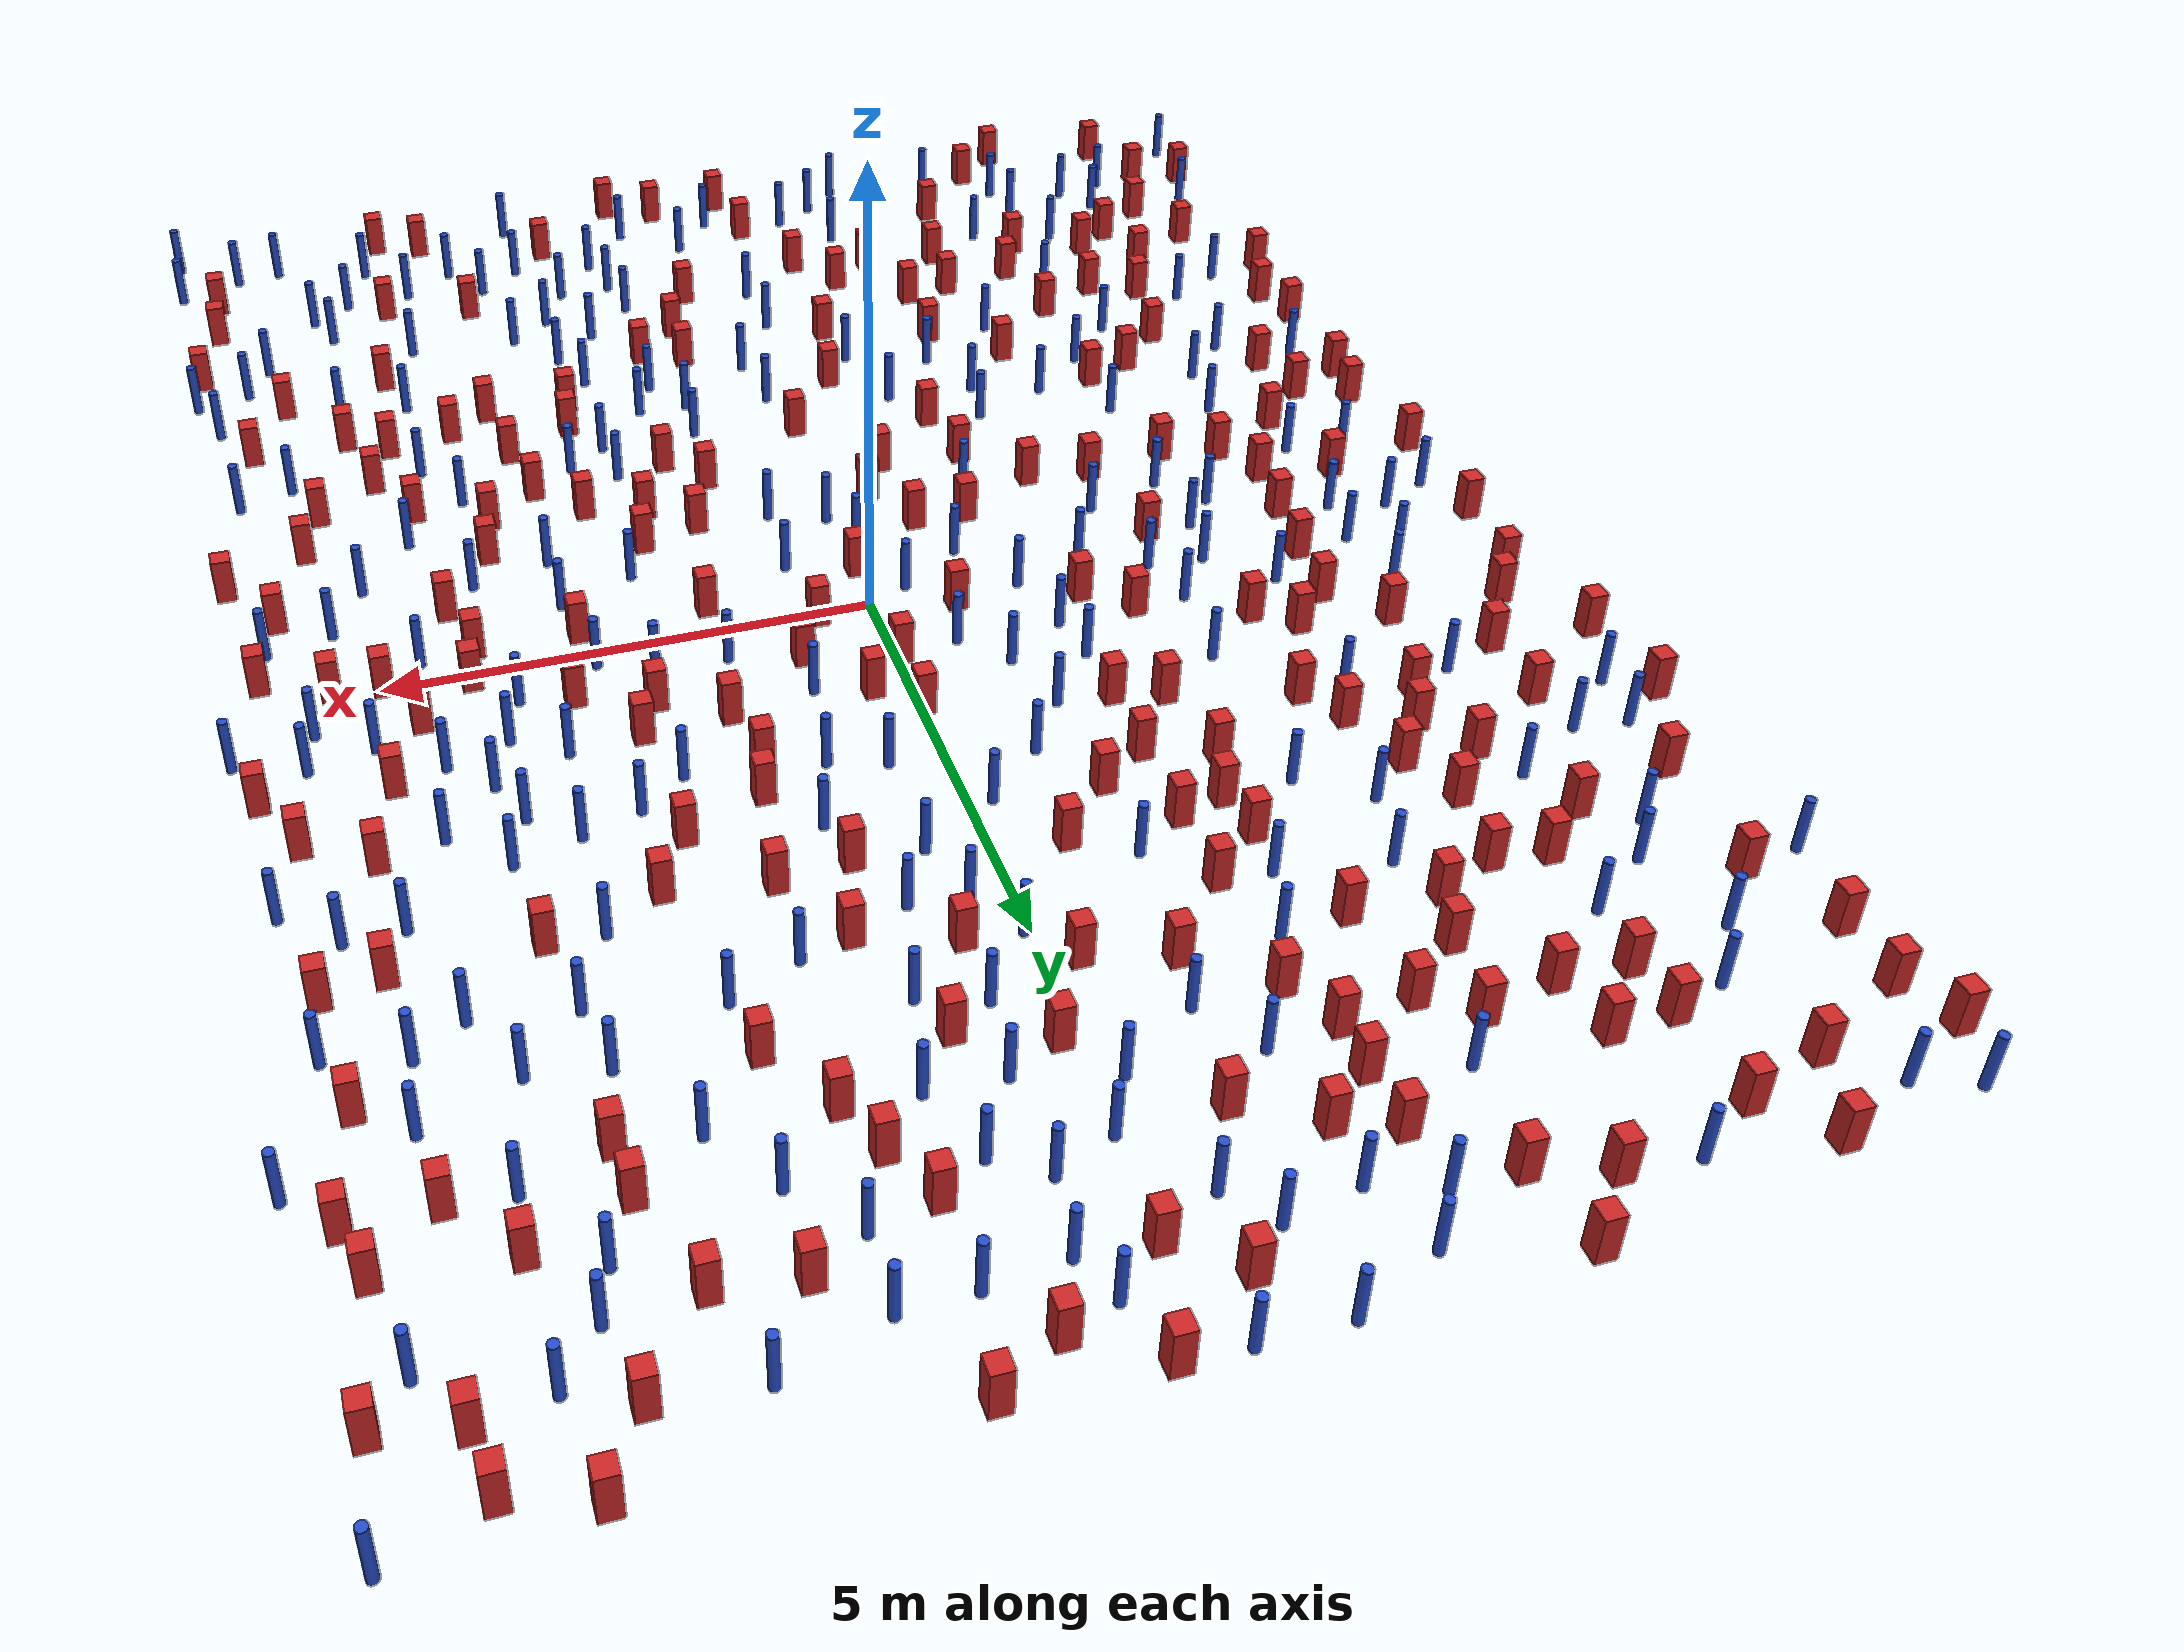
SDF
<sdf version="1.6">
  <model name="dense_19"><model name="square_post_obstacle0">
  <static>true</static>
  <pose frame="">5.86539074183 5.41331573031 8.22691968438e-08 7.2212513382e-06 -7.54495500217e-07 2.29674213826e-05</pose>
  <link name="link">
    <pose frame="">0 0 0.25 0 -0 0</pose>
    <inertial>
      <mass>100</mass>
      <inertia>
        <ixx>0.166667</ixx>
        <ixy>0</ixy>
        <ixz>0</ixz>
        <iyy>0.166667</iyy>
        <iyz>0</iyz>
        <izz>0.166667</izz>
      </inertia>
    </inertial>
    <collision name="collision">
      <geometry>
        <box>
          <size>.2 .2 .5</size>
        </box>
      </geometry>
      <max_contacts>10</max_contacts>
      <surface>
        <contact>
          <ode/>
        </contact>
        <bounce/>
        <friction>
          <torsional>
            <ode/>
          </torsional>
          <ode/>
        </friction>
      </surface>
    </collision>
    <visual name="visual">
      <geometry>
        <box>
          <size>.2 .2 .5</size>
        </box>
      </geometry>
      <material>
        <script>
          <name>Gazebo/Red</name>
          <uri>file://media/materials/scripts/gazebo.material</uri>
        </script>
      </material>
    </visual>
    <self_collide>0</self_collide>
    <kinematic>0</kinematic>
  </link>
</model>
<model name="square_post_obstacle1">
  <static>true</static>
  <pose frame="">0.477158628215 9.43952176952 8.22691968438e-08 7.22125133819e-06 -7.54495500217e-07 2.29674213826e-05</pose>
  <link name="link">
    <pose frame="">0 0 0.25 0 -0 0</pose>
    <inertial>
      <mass>100</mass>
      <inertia>
        <ixx>0.166667</ixx>
        <ixy>0</ixy>
        <ixz>0</ixz>
        <iyy>0.166667</iyy>
        <iyz>0</iyz>
        <izz>0.166667</izz>
      </inertia>
    </inertial>
    <collision name="collision">
      <geometry>
        <box>
          <size>.2 .2 .5</size>
        </box>
      </geometry>
      <max_contacts>10</max_contacts>
      <surface>
        <contact>
          <ode/>
        </contact>
        <bounce/>
        <friction>
          <torsional>
            <ode/>
          </torsional>
          <ode/>
        </friction>
      </surface>
    </collision>
    <visual name="visual">
      <geometry>
        <box>
          <size>.2 .2 .5</size>
        </box>
      </geometry>
      <material>
        <script>
          <name>Gazebo/Red</name>
          <uri>file://media/materials/scripts/gazebo.material</uri>
        </script>
      </material>
    </visual>
    <self_collide>0</self_collide>
    <kinematic>0</kinematic>
  </link>
</model>
<model name="pole_obstacle0">
  <static>true</static>
  <pose frame="">2.88885699599 0.218342367784 2.88873142074e-08 -9.90536689395e-09 4.60219949e-07 -1.20965994954e-07</pose>
  <link name="link">
  <pose frame="">0 0 0.3 0 -0 0</pose>
    <inertial>
      <mass>1</mass>
      <inertia>
        <ixx>0.145833</ixx>
        <ixy>0</ixy>
        <ixz>0</ixz>
        <iyy>0.145833</iyy>
        <iyz>0</iyz>
        <izz>0.125</izz>
      </inertia>
    </inertial>
    <collision name="collision">
      <geometry>
        <cylinder>
          <radius>0.05</radius>
          <length>.6</length>
        </cylinder>
      </geometry>
      <max_contacts>10</max_contacts>
      <surface>
        <contact>
          <ode/>
        </contact>
        <bounce/>
        <friction>
          <torsional>
            <ode/>
          </torsional>
          <ode/>
        </friction>
      </surface>
    </collision>
    <visual name="visual">
      <geometry>
        <cylinder>
          <radius>0.05</radius>
          <length>.6</length>
        </cylinder>
      </geometry>
      <material>
        <script>
          <name>Gazebo/Blue</name>
          <uri>file://media/materials/scripts/gazebo.material</uri>
        </script>
      </material>
    </visual>
    <self_collide>0</self_collide>
    <kinematic>0</kinematic>
  </link>
</model>
<model name="square_post_obstacle2">
  <static>true</static>
  <pose frame="">-1.50206599766 -6.68306396483 8.22691968438e-08 7.2212513382e-06 -7.54495500217e-07 2.29674213826e-05</pose>
  <link name="link">
    <pose frame="">0 0 0.25 0 -0 0</pose>
    <inertial>
      <mass>100</mass>
      <inertia>
        <ixx>0.166667</ixx>
        <ixy>0</ixy>
        <ixz>0</ixz>
        <iyy>0.166667</iyy>
        <iyz>0</iyz>
        <izz>0.166667</izz>
      </inertia>
    </inertial>
    <collision name="collision">
      <geometry>
        <box>
          <size>.2 .2 .5</size>
        </box>
      </geometry>
      <max_contacts>10</max_contacts>
      <surface>
        <contact>
          <ode/>
        </contact>
        <bounce/>
        <friction>
          <torsional>
            <ode/>
          </torsional>
          <ode/>
        </friction>
      </surface>
    </collision>
    <visual name="visual">
      <geometry>
        <box>
          <size>.2 .2 .5</size>
        </box>
      </geometry>
      <material>
        <script>
          <name>Gazebo/Red</name>
          <uri>file://media/materials/scripts/gazebo.material</uri>
        </script>
      </material>
    </visual>
    <self_collide>0</self_collide>
    <kinematic>0</kinematic>
  </link>
</model>
<model name="pole_obstacle1">
  <static>true</static>
  <pose frame="">-2.03950707412 -4.55169330116 2.88873142074e-08 -9.90536689575e-09 4.60219948995e-07 -1.20965994956e-07</pose>
  <link name="link">
  <pose frame="">0 0 0.3 0 -0 0</pose>
    <inertial>
      <mass>1</mass>
      <inertia>
        <ixx>0.145833</ixx>
        <ixy>0</ixy>
        <ixz>0</ixz>
        <iyy>0.145833</iyy>
        <iyz>0</iyz>
        <izz>0.125</izz>
      </inertia>
    </inertial>
    <collision name="collision">
      <geometry>
        <cylinder>
          <radius>0.05</radius>
          <length>.6</length>
        </cylinder>
      </geometry>
      <max_contacts>10</max_contacts>
      <surface>
        <contact>
          <ode/>
        </contact>
        <bounce/>
        <friction>
          <torsional>
            <ode/>
          </torsional>
          <ode/>
        </friction>
      </surface>
    </collision>
    <visual name="visual">
      <geometry>
        <cylinder>
          <radius>0.05</radius>
          <length>.6</length>
        </cylinder>
      </geometry>
      <material>
        <script>
          <name>Gazebo/Blue</name>
          <uri>file://media/materials/scripts/gazebo.material</uri>
        </script>
      </material>
    </visual>
    <self_collide>0</self_collide>
    <kinematic>0</kinematic>
  </link>
</model>
<model name="square_post_obstacle3">
  <static>true</static>
  <pose frame="">-0.780026683431 -4.40969399279 8.22691968438e-08 7.2212513382e-06 -7.54495500217e-07 2.29674213826e-05</pose>
  <link name="link">
    <pose frame="">0 0 0.25 0 -0 0</pose>
    <inertial>
      <mass>100</mass>
      <inertia>
        <ixx>0.166667</ixx>
        <ixy>0</ixy>
        <ixz>0</ixz>
        <iyy>0.166667</iyy>
        <iyz>0</iyz>
        <izz>0.166667</izz>
      </inertia>
    </inertial>
    <collision name="collision">
      <geometry>
        <box>
          <size>.2 .2 .5</size>
        </box>
      </geometry>
      <max_contacts>10</max_contacts>
      <surface>
        <contact>
          <ode/>
        </contact>
        <bounce/>
        <friction>
          <torsional>
            <ode/>
          </torsional>
          <ode/>
        </friction>
      </surface>
    </collision>
    <visual name="visual">
      <geometry>
        <box>
          <size>.2 .2 .5</size>
        </box>
      </geometry>
      <material>
        <script>
          <name>Gazebo/Red</name>
          <uri>file://media/materials/scripts/gazebo.material</uri>
        </script>
      </material>
    </visual>
    <self_collide>0</self_collide>
    <kinematic>0</kinematic>
  </link>
</model>
<model name="pole_obstacle2">
  <static>true</static>
  <pose frame="">-4.95476517142 -3.3155048729 2.88873142074e-08 -9.90536690245e-09 4.6021994898e-07 -1.20965994966e-07</pose>
  <link name="link">
  <pose frame="">0 0 0.3 0 -0 0</pose>
    <inertial>
      <mass>1</mass>
      <inertia>
        <ixx>0.145833</ixx>
        <ixy>0</ixy>
        <ixz>0</ixz>
        <iyy>0.145833</iyy>
        <iyz>0</iyz>
        <izz>0.125</izz>
      </inertia>
    </inertial>
    <collision name="collision">
      <geometry>
        <cylinder>
          <radius>0.05</radius>
          <length>.6</length>
        </cylinder>
      </geometry>
      <max_contacts>10</max_contacts>
      <surface>
        <contact>
          <ode/>
        </contact>
        <bounce/>
        <friction>
          <torsional>
            <ode/>
          </torsional>
          <ode/>
        </friction>
      </surface>
    </collision>
    <visual name="visual">
      <geometry>
        <cylinder>
          <radius>0.05</radius>
          <length>.6</length>
        </cylinder>
      </geometry>
      <material>
        <script>
          <name>Gazebo/Blue</name>
          <uri>file://media/materials/scripts/gazebo.material</uri>
        </script>
      </material>
    </visual>
    <self_collide>0</self_collide>
    <kinematic>0</kinematic>
  </link>
</model>
<model name="pole_obstacle3">
  <static>true</static>
  <pose frame="">-1.08976365134 1.31556032206 2.88873142074e-08 -9.90536689672e-09 4.60219948993e-07 -1.20965994959e-07</pose>
  <link name="link">
  <pose frame="">0 0 0.3 0 -0 0</pose>
    <inertial>
      <mass>1</mass>
      <inertia>
        <ixx>0.145833</ixx>
        <ixy>0</ixy>
        <ixz>0</ixz>
        <iyy>0.145833</iyy>
        <iyz>0</iyz>
        <izz>0.125</izz>
      </inertia>
    </inertial>
    <collision name="collision">
      <geometry>
        <cylinder>
          <radius>0.05</radius>
          <length>.6</length>
        </cylinder>
      </geometry>
      <max_contacts>10</max_contacts>
      <surface>
        <contact>
          <ode/>
        </contact>
        <bounce/>
        <friction>
          <torsional>
            <ode/>
          </torsional>
          <ode/>
        </friction>
      </surface>
    </collision>
    <visual name="visual">
      <geometry>
        <cylinder>
          <radius>0.05</radius>
          <length>.6</length>
        </cylinder>
      </geometry>
      <material>
        <script>
          <name>Gazebo/Blue</name>
          <uri>file://media/materials/scripts/gazebo.material</uri>
        </script>
      </material>
    </visual>
    <self_collide>0</self_collide>
    <kinematic>0</kinematic>
  </link>
</model>
<model name="square_post_obstacle4">
  <static>true</static>
  <pose frame="">-3.1690122181 -8.15503335935 8.22691968438e-08 7.2212513382e-06 -7.54495500217e-07 2.29674213826e-05</pose>
  <link name="link">
    <pose frame="">0 0 0.25 0 -0 0</pose>
    <inertial>
      <mass>100</mass>
      <inertia>
        <ixx>0.166667</ixx>
        <ixy>0</ixy>
        <ixz>0</ixz>
        <iyy>0.166667</iyy>
        <iyz>0</iyz>
        <izz>0.166667</izz>
      </inertia>
    </inertial>
    <collision name="collision">
      <geometry>
        <box>
          <size>.2 .2 .5</size>
        </box>
      </geometry>
      <max_contacts>10</max_contacts>
      <surface>
        <contact>
          <ode/>
        </contact>
        <bounce/>
        <friction>
          <torsional>
            <ode/>
          </torsional>
          <ode/>
        </friction>
      </surface>
    </collision>
    <visual name="visual">
      <geometry>
        <box>
          <size>.2 .2 .5</size>
        </box>
      </geometry>
      <material>
        <script>
          <name>Gazebo/Red</name>
          <uri>file://media/materials/scripts/gazebo.material</uri>
        </script>
      </material>
    </visual>
    <self_collide>0</self_collide>
    <kinematic>0</kinematic>
  </link>
</model>
<model name="square_post_obstacle5">
  <static>true</static>
  <pose frame="">-2.57601533757 0.859786683411 8.22691968438e-08 7.2212513382e-06 -7.54495500217e-07 2.29674213826e-05</pose>
  <link name="link">
    <pose frame="">0 0 0.25 0 -0 0</pose>
    <inertial>
      <mass>100</mass>
      <inertia>
        <ixx>0.166667</ixx>
        <ixy>0</ixy>
        <ixz>0</ixz>
        <iyy>0.166667</iyy>
        <iyz>0</iyz>
        <izz>0.166667</izz>
      </inertia>
    </inertial>
    <collision name="collision">
      <geometry>
        <box>
          <size>.2 .2 .5</size>
        </box>
      </geometry>
      <max_contacts>10</max_contacts>
      <surface>
        <contact>
          <ode/>
        </contact>
        <bounce/>
        <friction>
          <torsional>
            <ode/>
          </torsional>
          <ode/>
        </friction>
      </surface>
    </collision>
    <visual name="visual">
      <geometry>
        <box>
          <size>.2 .2 .5</size>
        </box>
      </geometry>
      <material>
        <script>
          <name>Gazebo/Red</name>
          <uri>file://media/materials/scripts/gazebo.material</uri>
        </script>
      </material>
    </visual>
    <self_collide>0</self_collide>
    <kinematic>0</kinematic>
  </link>
</model>
<model name="square_post_obstacle6">
  <static>true</static>
  <pose frame="">0.415322058031 -6.86767348785 8.22691968438e-08 7.2212513382e-06 -7.54495500217e-07 2.29674213826e-05</pose>
  <link name="link">
    <pose frame="">0 0 0.25 0 -0 0</pose>
    <inertial>
      <mass>100</mass>
      <inertia>
        <ixx>0.166667</ixx>
        <ixy>0</ixy>
        <ixz>0</ixz>
        <iyy>0.166667</iyy>
        <iyz>0</iyz>
        <izz>0.166667</izz>
      </inertia>
    </inertial>
    <collision name="collision">
      <geometry>
        <box>
          <size>.2 .2 .5</size>
        </box>
      </geometry>
      <max_contacts>10</max_contacts>
      <surface>
        <contact>
          <ode/>
        </contact>
        <bounce/>
        <friction>
          <torsional>
            <ode/>
          </torsional>
          <ode/>
        </friction>
      </surface>
    </collision>
    <visual name="visual">
      <geometry>
        <box>
          <size>.2 .2 .5</size>
        </box>
      </geometry>
      <material>
        <script>
          <name>Gazebo/Red</name>
          <uri>file://media/materials/scripts/gazebo.material</uri>
        </script>
      </material>
    </visual>
    <self_collide>0</self_collide>
    <kinematic>0</kinematic>
  </link>
</model>
<model name="pole_obstacle4">
  <static>true</static>
  <pose frame="">-3.15151144274 0.806409294875 2.88873142074e-08 -9.90536689285e-09 4.60219949002e-07 -1.20965994953e-07</pose>
  <link name="link">
  <pose frame="">0 0 0.3 0 -0 0</pose>
    <inertial>
      <mass>1</mass>
      <inertia>
        <ixx>0.145833</ixx>
        <ixy>0</ixy>
        <ixz>0</ixz>
        <iyy>0.145833</iyy>
        <iyz>0</iyz>
        <izz>0.125</izz>
      </inertia>
    </inertial>
    <collision name="collision">
      <geometry>
        <cylinder>
          <radius>0.05</radius>
          <length>.6</length>
        </cylinder>
      </geometry>
      <max_contacts>10</max_contacts>
      <surface>
        <contact>
          <ode/>
        </contact>
        <bounce/>
        <friction>
          <torsional>
            <ode/>
          </torsional>
          <ode/>
        </friction>
      </surface>
    </collision>
    <visual name="visual">
      <geometry>
        <cylinder>
          <radius>0.05</radius>
          <length>.6</length>
        </cylinder>
      </geometry>
      <material>
        <script>
          <name>Gazebo/Blue</name>
          <uri>file://media/materials/scripts/gazebo.material</uri>
        </script>
      </material>
    </visual>
    <self_collide>0</self_collide>
    <kinematic>0</kinematic>
  </link>
</model>
<model name="pole_obstacle5">
  <static>true</static>
  <pose frame="">0.382674475622 4.43594093725 2.88873142074e-08 -9.90536689683e-09 4.60219948993e-07 -1.20965994957e-07</pose>
  <link name="link">
  <pose frame="">0 0 0.3 0 -0 0</pose>
    <inertial>
      <mass>1</mass>
      <inertia>
        <ixx>0.145833</ixx>
        <ixy>0</ixy>
        <ixz>0</ixz>
        <iyy>0.145833</iyy>
        <iyz>0</iyz>
        <izz>0.125</izz>
      </inertia>
    </inertial>
    <collision name="collision">
      <geometry>
        <cylinder>
          <radius>0.05</radius>
          <length>.6</length>
        </cylinder>
      </geometry>
      <max_contacts>10</max_contacts>
      <surface>
        <contact>
          <ode/>
        </contact>
        <bounce/>
        <friction>
          <torsional>
            <ode/>
          </torsional>
          <ode/>
        </friction>
      </surface>
    </collision>
    <visual name="visual">
      <geometry>
        <cylinder>
          <radius>0.05</radius>
          <length>.6</length>
        </cylinder>
      </geometry>
      <material>
        <script>
          <name>Gazebo/Blue</name>
          <uri>file://media/materials/scripts/gazebo.material</uri>
        </script>
      </material>
    </visual>
    <self_collide>0</self_collide>
    <kinematic>0</kinematic>
  </link>
</model>
<model name="square_post_obstacle7">
  <static>true</static>
  <pose frame="">1.63549741798 -0.384665157309 8.22691968438e-08 7.2212513382e-06 -7.54495500217e-07 2.29674213826e-05</pose>
  <link name="link">
    <pose frame="">0 0 0.25 0 -0 0</pose>
    <inertial>
      <mass>100</mass>
      <inertia>
        <ixx>0.166667</ixx>
        <ixy>0</ixy>
        <ixz>0</ixz>
        <iyy>0.166667</iyy>
        <iyz>0</iyz>
        <izz>0.166667</izz>
      </inertia>
    </inertial>
    <collision name="collision">
      <geometry>
        <box>
          <size>.2 .2 .5</size>
        </box>
      </geometry>
      <max_contacts>10</max_contacts>
      <surface>
        <contact>
          <ode/>
        </contact>
        <bounce/>
        <friction>
          <torsional>
            <ode/>
          </torsional>
          <ode/>
        </friction>
      </surface>
    </collision>
    <visual name="visual">
      <geometry>
        <box>
          <size>.2 .2 .5</size>
        </box>
      </geometry>
      <material>
        <script>
          <name>Gazebo/Red</name>
          <uri>file://media/materials/scripts/gazebo.material</uri>
        </script>
      </material>
    </visual>
    <self_collide>0</self_collide>
    <kinematic>0</kinematic>
  </link>
</model>
<model name="square_post_obstacle8">
  <static>true</static>
  <pose frame="">-4.72382393284 -0.376325056524 8.22691968438e-08 7.22125133819e-06 -7.54495500217e-07 2.29674213826e-05</pose>
  <link name="link">
    <pose frame="">0 0 0.25 0 -0 0</pose>
    <inertial>
      <mass>100</mass>
      <inertia>
        <ixx>0.166667</ixx>
        <ixy>0</ixy>
        <ixz>0</ixz>
        <iyy>0.166667</iyy>
        <iyz>0</iyz>
        <izz>0.166667</izz>
      </inertia>
    </inertial>
    <collision name="collision">
      <geometry>
        <box>
          <size>.2 .2 .5</size>
        </box>
      </geometry>
      <max_contacts>10</max_contacts>
      <surface>
        <contact>
          <ode/>
        </contact>
        <bounce/>
        <friction>
          <torsional>
            <ode/>
          </torsional>
          <ode/>
        </friction>
      </surface>
    </collision>
    <visual name="visual">
      <geometry>
        <box>
          <size>.2 .2 .5</size>
        </box>
      </geometry>
      <material>
        <script>
          <name>Gazebo/Red</name>
          <uri>file://media/materials/scripts/gazebo.material</uri>
        </script>
      </material>
    </visual>
    <self_collide>0</self_collide>
    <kinematic>0</kinematic>
  </link>
</model>
<model name="pole_obstacle6">
  <static>true</static>
  <pose frame="">-5.11219012567 4.33190283015 2.88873142074e-08 -9.90536690842e-09 4.60219948965e-07 -1.20965994976e-07</pose>
  <link name="link">
  <pose frame="">0 0 0.3 0 -0 0</pose>
    <inertial>
      <mass>1</mass>
      <inertia>
        <ixx>0.145833</ixx>
        <ixy>0</ixy>
        <ixz>0</ixz>
        <iyy>0.145833</iyy>
        <iyz>0</iyz>
        <izz>0.125</izz>
      </inertia>
    </inertial>
    <collision name="collision">
      <geometry>
        <cylinder>
          <radius>0.05</radius>
          <length>.6</length>
        </cylinder>
      </geometry>
      <max_contacts>10</max_contacts>
      <surface>
        <contact>
          <ode/>
        </contact>
        <bounce/>
        <friction>
          <torsional>
            <ode/>
          </torsional>
          <ode/>
        </friction>
      </surface>
    </collision>
    <visual name="visual">
      <geometry>
        <cylinder>
          <radius>0.05</radius>
          <length>.6</length>
        </cylinder>
      </geometry>
      <material>
        <script>
          <name>Gazebo/Blue</name>
          <uri>file://media/materials/scripts/gazebo.material</uri>
        </script>
      </material>
    </visual>
    <self_collide>0</self_collide>
    <kinematic>0</kinematic>
  </link>
</model>
<model name="pole_obstacle7">
  <static>true</static>
  <pose frame="">5.50749667749 -3.81803511393 2.88873142074e-08 -9.90536690245e-09 4.6021994898e-07 -1.20965994966e-07</pose>
  <link name="link">
  <pose frame="">0 0 0.3 0 -0 0</pose>
    <inertial>
      <mass>1</mass>
      <inertia>
        <ixx>0.145833</ixx>
        <ixy>0</ixy>
        <ixz>0</ixz>
        <iyy>0.145833</iyy>
        <iyz>0</iyz>
        <izz>0.125</izz>
      </inertia>
    </inertial>
    <collision name="collision">
      <geometry>
        <cylinder>
          <radius>0.05</radius>
          <length>.6</length>
        </cylinder>
      </geometry>
      <max_contacts>10</max_contacts>
      <surface>
        <contact>
          <ode/>
        </contact>
        <bounce/>
        <friction>
          <torsional>
            <ode/>
          </torsional>
          <ode/>
        </friction>
      </surface>
    </collision>
    <visual name="visual">
      <geometry>
        <cylinder>
          <radius>0.05</radius>
          <length>.6</length>
        </cylinder>
      </geometry>
      <material>
        <script>
          <name>Gazebo/Blue</name>
          <uri>file://media/materials/scripts/gazebo.material</uri>
        </script>
      </material>
    </visual>
    <self_collide>0</self_collide>
    <kinematic>0</kinematic>
  </link>
</model>
<model name="square_post_obstacle9">
  <static>true</static>
  <pose frame="">2.50126027885 -2.48764107828 8.22691968438e-08 7.2212513382e-06 -7.54495500217e-07 2.29674213826e-05</pose>
  <link name="link">
    <pose frame="">0 0 0.25 0 -0 0</pose>
    <inertial>
      <mass>100</mass>
      <inertia>
        <ixx>0.166667</ixx>
        <ixy>0</ixy>
        <ixz>0</ixz>
        <iyy>0.166667</iyy>
        <iyz>0</iyz>
        <izz>0.166667</izz>
      </inertia>
    </inertial>
    <collision name="collision">
      <geometry>
        <box>
          <size>.2 .2 .5</size>
        </box>
      </geometry>
      <max_contacts>10</max_contacts>
      <surface>
        <contact>
          <ode/>
        </contact>
        <bounce/>
        <friction>
          <torsional>
            <ode/>
          </torsional>
          <ode/>
        </friction>
      </surface>
    </collision>
    <visual name="visual">
      <geometry>
        <box>
          <size>.2 .2 .5</size>
        </box>
      </geometry>
      <material>
        <script>
          <name>Gazebo/Red</name>
          <uri>file://media/materials/scripts/gazebo.material</uri>
        </script>
      </material>
    </visual>
    <self_collide>0</self_collide>
    <kinematic>0</kinematic>
  </link>
</model>
<model name="square_post_obstacle10">
  <static>true</static>
  <pose frame="">-6.50823513991 -2.34437890469 8.22691968438e-08 7.2212513382e-06 -7.54495500217e-07 2.29674213826e-05</pose>
  <link name="link">
    <pose frame="">0 0 0.25 0 -0 0</pose>
    <inertial>
      <mass>100</mass>
      <inertia>
        <ixx>0.166667</ixx>
        <ixy>0</ixy>
        <ixz>0</ixz>
        <iyy>0.166667</iyy>
        <iyz>0</iyz>
        <izz>0.166667</izz>
      </inertia>
    </inertial>
    <collision name="collision">
      <geometry>
        <box>
          <size>.2 .2 .5</size>
        </box>
      </geometry>
      <max_contacts>10</max_contacts>
      <surface>
        <contact>
          <ode/>
        </contact>
        <bounce/>
        <friction>
          <torsional>
            <ode/>
          </torsional>
          <ode/>
        </friction>
      </surface>
    </collision>
    <visual name="visual">
      <geometry>
        <box>
          <size>.2 .2 .5</size>
        </box>
      </geometry>
      <material>
        <script>
          <name>Gazebo/Red</name>
          <uri>file://media/materials/scripts/gazebo.material</uri>
        </script>
      </material>
    </visual>
    <self_collide>0</self_collide>
    <kinematic>0</kinematic>
  </link>
</model>
<model name="square_post_obstacle11">
  <static>true</static>
  <pose frame="">-4.8404946907 3.89938742409 8.22691968438e-08 7.2212513382e-06 -7.54495500217e-07 2.29674213826e-05</pose>
  <link name="link">
    <pose frame="">0 0 0.25 0 -0 0</pose>
    <inertial>
      <mass>100</mass>
      <inertia>
        <ixx>0.166667</ixx>
        <ixy>0</ixy>
        <ixz>0</ixz>
        <iyy>0.166667</iyy>
        <iyz>0</iyz>
        <izz>0.166667</izz>
      </inertia>
    </inertial>
    <collision name="collision">
      <geometry>
        <box>
          <size>.2 .2 .5</size>
        </box>
      </geometry>
      <max_contacts>10</max_contacts>
      <surface>
        <contact>
          <ode/>
        </contact>
        <bounce/>
        <friction>
          <torsional>
            <ode/>
          </torsional>
          <ode/>
        </friction>
      </surface>
    </collision>
    <visual name="visual">
      <geometry>
        <box>
          <size>.2 .2 .5</size>
        </box>
      </geometry>
      <material>
        <script>
          <name>Gazebo/Red</name>
          <uri>file://media/materials/scripts/gazebo.material</uri>
        </script>
      </material>
    </visual>
    <self_collide>0</self_collide>
    <kinematic>0</kinematic>
  </link>
</model>
<model name="square_post_obstacle12">
  <static>true</static>
  <pose frame="">-2.00418320931 -7.06071781148 8.22691968438e-08 7.22125133819e-06 -7.54495500217e-07 2.29674213826e-05</pose>
  <link name="link">
    <pose frame="">0 0 0.25 0 -0 0</pose>
    <inertial>
      <mass>100</mass>
      <inertia>
        <ixx>0.166667</ixx>
        <ixy>0</ixy>
        <ixz>0</ixz>
        <iyy>0.166667</iyy>
        <iyz>0</iyz>
        <izz>0.166667</izz>
      </inertia>
    </inertial>
    <collision name="collision">
      <geometry>
        <box>
          <size>.2 .2 .5</size>
        </box>
      </geometry>
      <max_contacts>10</max_contacts>
      <surface>
        <contact>
          <ode/>
        </contact>
        <bounce/>
        <friction>
          <torsional>
            <ode/>
          </torsional>
          <ode/>
        </friction>
      </surface>
    </collision>
    <visual name="visual">
      <geometry>
        <box>
          <size>.2 .2 .5</size>
        </box>
      </geometry>
      <material>
        <script>
          <name>Gazebo/Red</name>
          <uri>file://media/materials/scripts/gazebo.material</uri>
        </script>
      </material>
    </visual>
    <self_collide>0</self_collide>
    <kinematic>0</kinematic>
  </link>
</model>
<model name="square_post_obstacle13">
  <static>true</static>
  <pose frame="">-1.27762852433 3.37003128828 8.22691968438e-08 7.2212513382e-06 -7.54495500217e-07 2.29674213826e-05</pose>
  <link name="link">
    <pose frame="">0 0 0.25 0 -0 0</pose>
    <inertial>
      <mass>100</mass>
      <inertia>
        <ixx>0.166667</ixx>
        <ixy>0</ixy>
        <ixz>0</ixz>
        <iyy>0.166667</iyy>
        <iyz>0</iyz>
        <izz>0.166667</izz>
      </inertia>
    </inertial>
    <collision name="collision">
      <geometry>
        <box>
          <size>.2 .2 .5</size>
        </box>
      </geometry>
      <max_contacts>10</max_contacts>
      <surface>
        <contact>
          <ode/>
        </contact>
        <bounce/>
        <friction>
          <torsional>
            <ode/>
          </torsional>
          <ode/>
        </friction>
      </surface>
    </collision>
    <visual name="visual">
      <geometry>
        <box>
          <size>.2 .2 .5</size>
        </box>
      </geometry>
      <material>
        <script>
          <name>Gazebo/Red</name>
          <uri>file://media/materials/scripts/gazebo.material</uri>
        </script>
      </material>
    </visual>
    <self_collide>0</self_collide>
    <kinematic>0</kinematic>
  </link>
</model>
<model name="pole_obstacle8">
  <static>true</static>
  <pose frame="">4.90002891867 -7.51180466163 2.88873142074e-08 -9.90536690842e-09 4.60219948965e-07 -1.20965994976e-07</pose>
  <link name="link">
  <pose frame="">0 0 0.3 0 -0 0</pose>
    <inertial>
      <mass>1</mass>
      <inertia>
        <ixx>0.145833</ixx>
        <ixy>0</ixy>
        <ixz>0</ixz>
        <iyy>0.145833</iyy>
        <iyz>0</iyz>
        <izz>0.125</izz>
      </inertia>
    </inertial>
    <collision name="collision">
      <geometry>
        <cylinder>
          <radius>0.05</radius>
          <length>.6</length>
        </cylinder>
      </geometry>
      <max_contacts>10</max_contacts>
      <surface>
        <contact>
          <ode/>
        </contact>
        <bounce/>
        <friction>
          <torsional>
            <ode/>
          </torsional>
          <ode/>
        </friction>
      </surface>
    </collision>
    <visual name="visual">
      <geometry>
        <cylinder>
          <radius>0.05</radius>
          <length>.6</length>
        </cylinder>
      </geometry>
      <material>
        <script>
          <name>Gazebo/Blue</name>
          <uri>file://media/materials/scripts/gazebo.material</uri>
        </script>
      </material>
    </visual>
    <self_collide>0</self_collide>
    <kinematic>0</kinematic>
  </link>
</model>
<model name="square_post_obstacle14">
  <static>true</static>
  <pose frame="">2.61013132298 2.97255172156 8.22691968438e-08 7.2212513382e-06 -7.54495500217e-07 2.29674213826e-05</pose>
  <link name="link">
    <pose frame="">0 0 0.25 0 -0 0</pose>
    <inertial>
      <mass>100</mass>
      <inertia>
        <ixx>0.166667</ixx>
        <ixy>0</ixy>
        <ixz>0</ixz>
        <iyy>0.166667</iyy>
        <iyz>0</iyz>
        <izz>0.166667</izz>
      </inertia>
    </inertial>
    <collision name="collision">
      <geometry>
        <box>
          <size>.2 .2 .5</size>
        </box>
      </geometry>
      <max_contacts>10</max_contacts>
      <surface>
        <contact>
          <ode/>
        </contact>
        <bounce/>
        <friction>
          <torsional>
            <ode/>
          </torsional>
          <ode/>
        </friction>
      </surface>
    </collision>
    <visual name="visual">
      <geometry>
        <box>
          <size>.2 .2 .5</size>
        </box>
      </geometry>
      <material>
        <script>
          <name>Gazebo/Red</name>
          <uri>file://media/materials/scripts/gazebo.material</uri>
        </script>
      </material>
    </visual>
    <self_collide>0</self_collide>
    <kinematic>0</kinematic>
  </link>
</model>
<model name="square_post_obstacle15">
  <static>true</static>
  <pose frame="">-6.69380144993 -1.2012542964 8.22691968438e-08 7.2212513382e-06 -7.54495500217e-07 2.29674213826e-05</pose>
  <link name="link">
    <pose frame="">0 0 0.25 0 -0 0</pose>
    <inertial>
      <mass>100</mass>
      <inertia>
        <ixx>0.166667</ixx>
        <ixy>0</ixy>
        <ixz>0</ixz>
        <iyy>0.166667</iyy>
        <iyz>0</iyz>
        <izz>0.166667</izz>
      </inertia>
    </inertial>
    <collision name="collision">
      <geometry>
        <box>
          <size>.2 .2 .5</size>
        </box>
      </geometry>
      <max_contacts>10</max_contacts>
      <surface>
        <contact>
          <ode/>
        </contact>
        <bounce/>
        <friction>
          <torsional>
            <ode/>
          </torsional>
          <ode/>
        </friction>
      </surface>
    </collision>
    <visual name="visual">
      <geometry>
        <box>
          <size>.2 .2 .5</size>
        </box>
      </geometry>
      <material>
        <script>
          <name>Gazebo/Red</name>
          <uri>file://media/materials/scripts/gazebo.material</uri>
        </script>
      </material>
    </visual>
    <self_collide>0</self_collide>
    <kinematic>0</kinematic>
  </link>
</model>
<model name="square_post_obstacle16">
  <static>true</static>
  <pose frame="">4.78652558701 7.19634134487 8.22691968438e-08 7.2212513382e-06 -7.54495500217e-07 2.29674213826e-05</pose>
  <link name="link">
    <pose frame="">0 0 0.25 0 -0 0</pose>
    <inertial>
      <mass>100</mass>
      <inertia>
        <ixx>0.166667</ixx>
        <ixy>0</ixy>
        <ixz>0</ixz>
        <iyy>0.166667</iyy>
        <iyz>0</iyz>
        <izz>0.166667</izz>
      </inertia>
    </inertial>
    <collision name="collision">
      <geometry>
        <box>
          <size>.2 .2 .5</size>
        </box>
      </geometry>
      <max_contacts>10</max_contacts>
      <surface>
        <contact>
          <ode/>
        </contact>
        <bounce/>
        <friction>
          <torsional>
            <ode/>
          </torsional>
          <ode/>
        </friction>
      </surface>
    </collision>
    <visual name="visual">
      <geometry>
        <box>
          <size>.2 .2 .5</size>
        </box>
      </geometry>
      <material>
        <script>
          <name>Gazebo/Red</name>
          <uri>file://media/materials/scripts/gazebo.material</uri>
        </script>
      </material>
    </visual>
    <self_collide>0</self_collide>
    <kinematic>0</kinematic>
  </link>
</model>
<model name="pole_obstacle9">
  <static>true</static>
  <pose frame="">6.40183729626 -9.36785686819 2.88873142074e-08 -9.9053668967e-09 4.60219948993e-07 -1.20965994957e-07</pose>
  <link name="link">
  <pose frame="">0 0 0.3 0 -0 0</pose>
    <inertial>
      <mass>1</mass>
      <inertia>
        <ixx>0.145833</ixx>
        <ixy>0</ixy>
        <ixz>0</ixz>
        <iyy>0.145833</iyy>
        <iyz>0</iyz>
        <izz>0.125</izz>
      </inertia>
    </inertial>
    <collision name="collision">
      <geometry>
        <cylinder>
          <radius>0.05</radius>
          <length>.6</length>
        </cylinder>
      </geometry>
      <max_contacts>10</max_contacts>
      <surface>
        <contact>
          <ode/>
        </contact>
        <bounce/>
        <friction>
          <torsional>
            <ode/>
          </torsional>
          <ode/>
        </friction>
      </surface>
    </collision>
    <visual name="visual">
      <geometry>
        <cylinder>
          <radius>0.05</radius>
          <length>.6</length>
        </cylinder>
      </geometry>
      <material>
        <script>
          <name>Gazebo/Blue</name>
          <uri>file://media/materials/scripts/gazebo.material</uri>
        </script>
      </material>
    </visual>
    <self_collide>0</self_collide>
    <kinematic>0</kinematic>
  </link>
</model>
<model name="square_post_obstacle17">
  <static>true</static>
  <pose frame="">5.99555126417 -8.20845346596 8.22691968438e-08 7.2212513382e-06 -7.54495500217e-07 2.29674213826e-05</pose>
  <link name="link">
    <pose frame="">0 0 0.25 0 -0 0</pose>
    <inertial>
      <mass>100</mass>
      <inertia>
        <ixx>0.166667</ixx>
        <ixy>0</ixy>
        <ixz>0</ixz>
        <iyy>0.166667</iyy>
        <iyz>0</iyz>
        <izz>0.166667</izz>
      </inertia>
    </inertial>
    <collision name="collision">
      <geometry>
        <box>
          <size>.2 .2 .5</size>
        </box>
      </geometry>
      <max_contacts>10</max_contacts>
      <surface>
        <contact>
          <ode/>
        </contact>
        <bounce/>
        <friction>
          <torsional>
            <ode/>
          </torsional>
          <ode/>
        </friction>
      </surface>
    </collision>
    <visual name="visual">
      <geometry>
        <box>
          <size>.2 .2 .5</size>
        </box>
      </geometry>
      <material>
        <script>
          <name>Gazebo/Red</name>
          <uri>file://media/materials/scripts/gazebo.material</uri>
        </script>
      </material>
    </visual>
    <self_collide>0</self_collide>
    <kinematic>0</kinematic>
  </link>
</model>
<model name="square_post_obstacle18">
  <static>true</static>
  <pose frame="">5.32142066474 2.54348663365 8.22691968438e-08 7.2212513382e-06 -7.54495500217e-07 2.29674213826e-05</pose>
  <link name="link">
    <pose frame="">0 0 0.25 0 -0 0</pose>
    <inertial>
      <mass>100</mass>
      <inertia>
        <ixx>0.166667</ixx>
        <ixy>0</ixy>
        <ixz>0</ixz>
        <iyy>0.166667</iyy>
        <iyz>0</iyz>
        <izz>0.166667</izz>
      </inertia>
    </inertial>
    <collision name="collision">
      <geometry>
        <box>
          <size>.2 .2 .5</size>
        </box>
      </geometry>
      <max_contacts>10</max_contacts>
      <surface>
        <contact>
          <ode/>
        </contact>
        <bounce/>
        <friction>
          <torsional>
            <ode/>
          </torsional>
          <ode/>
        </friction>
      </surface>
    </collision>
    <visual name="visual">
      <geometry>
        <box>
          <size>.2 .2 .5</size>
        </box>
      </geometry>
      <material>
        <script>
          <name>Gazebo/Red</name>
          <uri>file://media/materials/scripts/gazebo.material</uri>
        </script>
      </material>
    </visual>
    <self_collide>0</self_collide>
    <kinematic>0</kinematic>
  </link>
</model>
<model name="pole_obstacle10">
  <static>true</static>
  <pose frame="">-1.60955035864 -1.83495691934 2.88873142074e-08 -9.90536689672e-09 4.60219948993e-07 -1.20965994959e-07</pose>
  <link name="link">
  <pose frame="">0 0 0.3 0 -0 0</pose>
    <inertial>
      <mass>1</mass>
      <inertia>
        <ixx>0.145833</ixx>
        <ixy>0</ixy>
        <ixz>0</ixz>
        <iyy>0.145833</iyy>
        <iyz>0</iyz>
        <izz>0.125</izz>
      </inertia>
    </inertial>
    <collision name="collision">
      <geometry>
        <cylinder>
          <radius>0.05</radius>
          <length>.6</length>
        </cylinder>
      </geometry>
      <max_contacts>10</max_contacts>
      <surface>
        <contact>
          <ode/>
        </contact>
        <bounce/>
        <friction>
          <torsional>
            <ode/>
          </torsional>
          <ode/>
        </friction>
      </surface>
    </collision>
    <visual name="visual">
      <geometry>
        <cylinder>
          <radius>0.05</radius>
          <length>.6</length>
        </cylinder>
      </geometry>
      <material>
        <script>
          <name>Gazebo/Blue</name>
          <uri>file://media/materials/scripts/gazebo.material</uri>
        </script>
      </material>
    </visual>
    <self_collide>0</self_collide>
    <kinematic>0</kinematic>
  </link>
</model>
<model name="square_post_obstacle19">
  <static>true</static>
  <pose frame="">5.39842793259 8.55268821389 8.22691968438e-08 7.22125133819e-06 -7.54495500217e-07 2.29674213826e-05</pose>
  <link name="link">
    <pose frame="">0 0 0.25 0 -0 0</pose>
    <inertial>
      <mass>100</mass>
      <inertia>
        <ixx>0.166667</ixx>
        <ixy>0</ixy>
        <ixz>0</ixz>
        <iyy>0.166667</iyy>
        <iyz>0</iyz>
        <izz>0.166667</izz>
      </inertia>
    </inertial>
    <collision name="collision">
      <geometry>
        <box>
          <size>.2 .2 .5</size>
        </box>
      </geometry>
      <max_contacts>10</max_contacts>
      <surface>
        <contact>
          <ode/>
        </contact>
        <bounce/>
        <friction>
          <torsional>
            <ode/>
          </torsional>
          <ode/>
        </friction>
      </surface>
    </collision>
    <visual name="visual">
      <geometry>
        <box>
          <size>.2 .2 .5</size>
        </box>
      </geometry>
      <material>
        <script>
          <name>Gazebo/Red</name>
          <uri>file://media/materials/scripts/gazebo.material</uri>
        </script>
      </material>
    </visual>
    <self_collide>0</self_collide>
    <kinematic>0</kinematic>
  </link>
</model>
<model name="pole_obstacle11">
  <static>true</static>
  <pose frame="">-6.13879291941 -5.5250848036 2.88873142074e-08 -9.90536690842e-09 4.60219948965e-07 -1.20965994976e-07</pose>
  <link name="link">
  <pose frame="">0 0 0.3 0 -0 0</pose>
    <inertial>
      <mass>1</mass>
      <inertia>
        <ixx>0.145833</ixx>
        <ixy>0</ixy>
        <ixz>0</ixz>
        <iyy>0.145833</iyy>
        <iyz>0</iyz>
        <izz>0.125</izz>
      </inertia>
    </inertial>
    <collision name="collision">
      <geometry>
        <cylinder>
          <radius>0.05</radius>
          <length>.6</length>
        </cylinder>
      </geometry>
      <max_contacts>10</max_contacts>
      <surface>
        <contact>
          <ode/>
        </contact>
        <bounce/>
        <friction>
          <torsional>
            <ode/>
          </torsional>
          <ode/>
        </friction>
      </surface>
    </collision>
    <visual name="visual">
      <geometry>
        <cylinder>
          <radius>0.05</radius>
          <length>.6</length>
        </cylinder>
      </geometry>
      <material>
        <script>
          <name>Gazebo/Blue</name>
          <uri>file://media/materials/scripts/gazebo.material</uri>
        </script>
      </material>
    </visual>
    <self_collide>0</self_collide>
    <kinematic>0</kinematic>
  </link>
</model>
<model name="square_post_obstacle20">
  <static>true</static>
  <pose frame="">4.18817228938 8.71090653586 8.22691968438e-08 7.22125133819e-06 -7.54495500217e-07 2.29674213826e-05</pose>
  <link name="link">
    <pose frame="">0 0 0.25 0 -0 0</pose>
    <inertial>
      <mass>100</mass>
      <inertia>
        <ixx>0.166667</ixx>
        <ixy>0</ixy>
        <ixz>0</ixz>
        <iyy>0.166667</iyy>
        <iyz>0</iyz>
        <izz>0.166667</izz>
      </inertia>
    </inertial>
    <collision name="collision">
      <geometry>
        <box>
          <size>.2 .2 .5</size>
        </box>
      </geometry>
      <max_contacts>10</max_contacts>
      <surface>
        <contact>
          <ode/>
        </contact>
        <bounce/>
        <friction>
          <torsional>
            <ode/>
          </torsional>
          <ode/>
        </friction>
      </surface>
    </collision>
    <visual name="visual">
      <geometry>
        <box>
          <size>.2 .2 .5</size>
        </box>
      </geometry>
      <material>
        <script>
          <name>Gazebo/Red</name>
          <uri>file://media/materials/scripts/gazebo.material</uri>
        </script>
      </material>
    </visual>
    <self_collide>0</self_collide>
    <kinematic>0</kinematic>
  </link>
</model>
<model name="pole_obstacle12">
  <static>true</static>
  <pose frame="">6.0619317782 4.78889199146 2.88873142074e-08 -9.90536690842e-09 4.60219948965e-07 -1.20965994976e-07</pose>
  <link name="link">
  <pose frame="">0 0 0.3 0 -0 0</pose>
    <inertial>
      <mass>1</mass>
      <inertia>
        <ixx>0.145833</ixx>
        <ixy>0</ixy>
        <ixz>0</ixz>
        <iyy>0.145833</iyy>
        <iyz>0</iyz>
        <izz>0.125</izz>
      </inertia>
    </inertial>
    <collision name="collision">
      <geometry>
        <cylinder>
          <radius>0.05</radius>
          <length>.6</length>
        </cylinder>
      </geometry>
      <max_contacts>10</max_contacts>
      <surface>
        <contact>
          <ode/>
        </contact>
        <bounce/>
        <friction>
          <torsional>
            <ode/>
          </torsional>
          <ode/>
        </friction>
      </surface>
    </collision>
    <visual name="visual">
      <geometry>
        <cylinder>
          <radius>0.05</radius>
          <length>.6</length>
        </cylinder>
      </geometry>
      <material>
        <script>
          <name>Gazebo/Blue</name>
          <uri>file://media/materials/scripts/gazebo.material</uri>
        </script>
      </material>
    </visual>
    <self_collide>0</self_collide>
    <kinematic>0</kinematic>
  </link>
</model>
<model name="square_post_obstacle21">
  <static>true</static>
  <pose frame="">5.41926579649 -5.4989104012 8.22691968438e-08 7.22125133819e-06 -7.54495500217e-07 2.29674213826e-05</pose>
  <link name="link">
    <pose frame="">0 0 0.25 0 -0 0</pose>
    <inertial>
      <mass>100</mass>
      <inertia>
        <ixx>0.166667</ixx>
        <ixy>0</ixy>
        <ixz>0</ixz>
        <iyy>0.166667</iyy>
        <iyz>0</iyz>
        <izz>0.166667</izz>
      </inertia>
    </inertial>
    <collision name="collision">
      <geometry>
        <box>
          <size>.2 .2 .5</size>
        </box>
      </geometry>
      <max_contacts>10</max_contacts>
      <surface>
        <contact>
          <ode/>
        </contact>
        <bounce/>
        <friction>
          <torsional>
            <ode/>
          </torsional>
          <ode/>
        </friction>
      </surface>
    </collision>
    <visual name="visual">
      <geometry>
        <box>
          <size>.2 .2 .5</size>
        </box>
      </geometry>
      <material>
        <script>
          <name>Gazebo/Red</name>
          <uri>file://media/materials/scripts/gazebo.material</uri>
        </script>
      </material>
    </visual>
    <self_collide>0</self_collide>
    <kinematic>0</kinematic>
  </link>
</model>
<model name="pole_obstacle13">
  <static>true</static>
  <pose frame="">-5.07513045503 -8.23710917946 2.88873142074e-08 -9.9053668967e-09 4.60219948993e-07 -1.20965994957e-07</pose>
  <link name="link">
  <pose frame="">0 0 0.3 0 -0 0</pose>
    <inertial>
      <mass>1</mass>
      <inertia>
        <ixx>0.145833</ixx>
        <ixy>0</ixy>
        <ixz>0</ixz>
        <iyy>0.145833</iyy>
        <iyz>0</iyz>
        <izz>0.125</izz>
      </inertia>
    </inertial>
    <collision name="collision">
      <geometry>
        <cylinder>
          <radius>0.05</radius>
          <length>.6</length>
        </cylinder>
      </geometry>
      <max_contacts>10</max_contacts>
      <surface>
        <contact>
          <ode/>
        </contact>
        <bounce/>
        <friction>
          <torsional>
            <ode/>
          </torsional>
          <ode/>
        </friction>
      </surface>
    </collision>
    <visual name="visual">
      <geometry>
        <cylinder>
          <radius>0.05</radius>
          <length>.6</length>
        </cylinder>
      </geometry>
      <material>
        <script>
          <name>Gazebo/Blue</name>
          <uri>file://media/materials/scripts/gazebo.material</uri>
        </script>
      </material>
    </visual>
    <self_collide>0</self_collide>
    <kinematic>0</kinematic>
  </link>
</model>
<model name="square_post_obstacle22">
  <static>true</static>
  <pose frame="">-0.85530971246 0.242384981534 8.22691968438e-08 7.2212513382e-06 -7.54495500217e-07 2.29674213826e-05</pose>
  <link name="link">
    <pose frame="">0 0 0.25 0 -0 0</pose>
    <inertial>
      <mass>100</mass>
      <inertia>
        <ixx>0.166667</ixx>
        <ixy>0</ixy>
        <ixz>0</ixz>
        <iyy>0.166667</iyy>
        <iyz>0</iyz>
        <izz>0.166667</izz>
      </inertia>
    </inertial>
    <collision name="collision">
      <geometry>
        <box>
          <size>.2 .2 .5</size>
        </box>
      </geometry>
      <max_contacts>10</max_contacts>
      <surface>
        <contact>
          <ode/>
        </contact>
        <bounce/>
        <friction>
          <torsional>
            <ode/>
          </torsional>
          <ode/>
        </friction>
      </surface>
    </collision>
    <visual name="visual">
      <geometry>
        <box>
          <size>.2 .2 .5</size>
        </box>
      </geometry>
      <material>
        <script>
          <name>Gazebo/Red</name>
          <uri>file://media/materials/scripts/gazebo.material</uri>
        </script>
      </material>
    </visual>
    <self_collide>0</self_collide>
    <kinematic>0</kinematic>
  </link>
</model>
<model name="pole_obstacle14">
  <static>true</static>
  <pose frame="">-1.77880233781 -7.88300365105 2.88873142074e-08 -9.90536689852e-09 4.60219948989e-07 -1.2096599496e-07</pose>
  <link name="link">
  <pose frame="">0 0 0.3 0 -0 0</pose>
    <inertial>
      <mass>1</mass>
      <inertia>
        <ixx>0.145833</ixx>
        <ixy>0</ixy>
        <ixz>0</ixz>
        <iyy>0.145833</iyy>
        <iyz>0</iyz>
        <izz>0.125</izz>
      </inertia>
    </inertial>
    <collision name="collision">
      <geometry>
        <cylinder>
          <radius>0.05</radius>
          <length>.6</length>
        </cylinder>
      </geometry>
      <max_contacts>10</max_contacts>
      <surface>
        <contact>
          <ode/>
        </contact>
        <bounce/>
        <friction>
          <torsional>
            <ode/>
          </torsional>
          <ode/>
        </friction>
      </surface>
    </collision>
    <visual name="visual">
      <geometry>
        <cylinder>
          <radius>0.05</radius>
          <length>.6</length>
        </cylinder>
      </geometry>
      <material>
        <script>
          <name>Gazebo/Blue</name>
          <uri>file://media/materials/scripts/gazebo.material</uri>
        </script>
      </material>
    </visual>
    <self_collide>0</self_collide>
    <kinematic>0</kinematic>
  </link>
</model>
<model name="pole_obstacle15">
  <static>true</static>
  <pose frame="">-3.74835648836 -4.06902858229 2.88873142074e-08 -9.90536692062e-09 4.60219948937e-07 -1.20965994985e-07</pose>
  <link name="link">
  <pose frame="">0 0 0.3 0 -0 0</pose>
    <inertial>
      <mass>1</mass>
      <inertia>
        <ixx>0.145833</ixx>
        <ixy>0</ixy>
        <ixz>0</ixz>
        <iyy>0.145833</iyy>
        <iyz>0</iyz>
        <izz>0.125</izz>
      </inertia>
    </inertial>
    <collision name="collision">
      <geometry>
        <cylinder>
          <radius>0.05</radius>
          <length>.6</length>
        </cylinder>
      </geometry>
      <max_contacts>10</max_contacts>
      <surface>
        <contact>
          <ode/>
        </contact>
        <bounce/>
        <friction>
          <torsional>
            <ode/>
          </torsional>
          <ode/>
        </friction>
      </surface>
    </collision>
    <visual name="visual">
      <geometry>
        <cylinder>
          <radius>0.05</radius>
          <length>.6</length>
        </cylinder>
      </geometry>
      <material>
        <script>
          <name>Gazebo/Blue</name>
          <uri>file://media/materials/scripts/gazebo.material</uri>
        </script>
      </material>
    </visual>
    <self_collide>0</self_collide>
    <kinematic>0</kinematic>
  </link>
</model>
<model name="pole_obstacle16">
  <static>true</static>
  <pose frame="">1.87375932207 -7.36777202343 2.88873142074e-08 -9.90536689852e-09 4.60219948989e-07 -1.2096599496e-07</pose>
  <link name="link">
  <pose frame="">0 0 0.3 0 -0 0</pose>
    <inertial>
      <mass>1</mass>
      <inertia>
        <ixx>0.145833</ixx>
        <ixy>0</ixy>
        <ixz>0</ixz>
        <iyy>0.145833</iyy>
        <iyz>0</iyz>
        <izz>0.125</izz>
      </inertia>
    </inertial>
    <collision name="collision">
      <geometry>
        <cylinder>
          <radius>0.05</radius>
          <length>.6</length>
        </cylinder>
      </geometry>
      <max_contacts>10</max_contacts>
      <surface>
        <contact>
          <ode/>
        </contact>
        <bounce/>
        <friction>
          <torsional>
            <ode/>
          </torsional>
          <ode/>
        </friction>
      </surface>
    </collision>
    <visual name="visual">
      <geometry>
        <cylinder>
          <radius>0.05</radius>
          <length>.6</length>
        </cylinder>
      </geometry>
      <material>
        <script>
          <name>Gazebo/Blue</name>
          <uri>file://media/materials/scripts/gazebo.material</uri>
        </script>
      </material>
    </visual>
    <self_collide>0</self_collide>
    <kinematic>0</kinematic>
  </link>
</model>
<model name="square_post_obstacle23">
  <static>true</static>
  <pose frame="">-2.03721567945 7.30508240218 8.22691968438e-08 7.22125133819e-06 -7.54495500217e-07 2.29674213826e-05</pose>
  <link name="link">
    <pose frame="">0 0 0.25 0 -0 0</pose>
    <inertial>
      <mass>100</mass>
      <inertia>
        <ixx>0.166667</ixx>
        <ixy>0</ixy>
        <ixz>0</ixz>
        <iyy>0.166667</iyy>
        <iyz>0</iyz>
        <izz>0.166667</izz>
      </inertia>
    </inertial>
    <collision name="collision">
      <geometry>
        <box>
          <size>.2 .2 .5</size>
        </box>
      </geometry>
      <max_contacts>10</max_contacts>
      <surface>
        <contact>
          <ode/>
        </contact>
        <bounce/>
        <friction>
          <torsional>
            <ode/>
          </torsional>
          <ode/>
        </friction>
      </surface>
    </collision>
    <visual name="visual">
      <geometry>
        <box>
          <size>.2 .2 .5</size>
        </box>
      </geometry>
      <material>
        <script>
          <name>Gazebo/Red</name>
          <uri>file://media/materials/scripts/gazebo.material</uri>
        </script>
      </material>
    </visual>
    <self_collide>0</self_collide>
    <kinematic>0</kinematic>
  </link>
</model>
<model name="pole_obstacle17">
  <static>true</static>
  <pose frame="">-2.99809422905 0.173714844666 2.88873142074e-08 -9.90536689314e-09 4.60219949002e-07 -1.20965994953e-07</pose>
  <link name="link">
  <pose frame="">0 0 0.3 0 -0 0</pose>
    <inertial>
      <mass>1</mass>
      <inertia>
        <ixx>0.145833</ixx>
        <ixy>0</ixy>
        <ixz>0</ixz>
        <iyy>0.145833</iyy>
        <iyz>0</iyz>
        <izz>0.125</izz>
      </inertia>
    </inertial>
    <collision name="collision">
      <geometry>
        <cylinder>
          <radius>0.05</radius>
          <length>.6</length>
        </cylinder>
      </geometry>
      <max_contacts>10</max_contacts>
      <surface>
        <contact>
          <ode/>
        </contact>
        <bounce/>
        <friction>
          <torsional>
            <ode/>
          </torsional>
          <ode/>
        </friction>
      </surface>
    </collision>
    <visual name="visual">
      <geometry>
        <cylinder>
          <radius>0.05</radius>
          <length>.6</length>
        </cylinder>
      </geometry>
      <material>
        <script>
          <name>Gazebo/Blue</name>
          <uri>file://media/materials/scripts/gazebo.material</uri>
        </script>
      </material>
    </visual>
    <self_collide>0</self_collide>
    <kinematic>0</kinematic>
  </link>
</model>
<model name="square_post_obstacle24">
  <static>true</static>
  <pose frame="">1.8701958105 -2.29422337343 8.22691968438e-08 7.2212513382e-06 -7.54495500217e-07 2.29674213826e-05</pose>
  <link name="link">
    <pose frame="">0 0 0.25 0 -0 0</pose>
    <inertial>
      <mass>100</mass>
      <inertia>
        <ixx>0.166667</ixx>
        <ixy>0</ixy>
        <ixz>0</ixz>
        <iyy>0.166667</iyy>
        <iyz>0</iyz>
        <izz>0.166667</izz>
      </inertia>
    </inertial>
    <collision name="collision">
      <geometry>
        <box>
          <size>.2 .2 .5</size>
        </box>
      </geometry>
      <max_contacts>10</max_contacts>
      <surface>
        <contact>
          <ode/>
        </contact>
        <bounce/>
        <friction>
          <torsional>
            <ode/>
          </torsional>
          <ode/>
        </friction>
      </surface>
    </collision>
    <visual name="visual">
      <geometry>
        <box>
          <size>.2 .2 .5</size>
        </box>
      </geometry>
      <material>
        <script>
          <name>Gazebo/Red</name>
          <uri>file://media/materials/scripts/gazebo.material</uri>
        </script>
      </material>
    </visual>
    <self_collide>0</self_collide>
    <kinematic>0</kinematic>
  </link>
</model>
<model name="square_post_obstacle25">
  <static>true</static>
  <pose frame="">-0.83853295713 -2.48116766802 8.22691968438e-08 7.2212513382e-06 -7.54495500217e-07 2.29674213826e-05</pose>
  <link name="link">
    <pose frame="">0 0 0.25 0 -0 0</pose>
    <inertial>
      <mass>100</mass>
      <inertia>
        <ixx>0.166667</ixx>
        <ixy>0</ixy>
        <ixz>0</ixz>
        <iyy>0.166667</iyy>
        <iyz>0</iyz>
        <izz>0.166667</izz>
      </inertia>
    </inertial>
    <collision name="collision">
      <geometry>
        <box>
          <size>.2 .2 .5</size>
        </box>
      </geometry>
      <max_contacts>10</max_contacts>
      <surface>
        <contact>
          <ode/>
        </contact>
        <bounce/>
        <friction>
          <torsional>
            <ode/>
          </torsional>
          <ode/>
        </friction>
      </surface>
    </collision>
    <visual name="visual">
      <geometry>
        <box>
          <size>.2 .2 .5</size>
        </box>
      </geometry>
      <material>
        <script>
          <name>Gazebo/Red</name>
          <uri>file://media/materials/scripts/gazebo.material</uri>
        </script>
      </material>
    </visual>
    <self_collide>0</self_collide>
    <kinematic>0</kinematic>
  </link>
</model>
<model name="square_post_obstacle26">
  <static>true</static>
  <pose frame="">-0.125004662885 -3.47699923398 8.22691968438e-08 7.22125133819e-06 -7.54495500217e-07 2.29674213826e-05</pose>
  <link name="link">
    <pose frame="">0 0 0.25 0 -0 0</pose>
    <inertial>
      <mass>100</mass>
      <inertia>
        <ixx>0.166667</ixx>
        <ixy>0</ixy>
        <ixz>0</ixz>
        <iyy>0.166667</iyy>
        <iyz>0</iyz>
        <izz>0.166667</izz>
      </inertia>
    </inertial>
    <collision name="collision">
      <geometry>
        <box>
          <size>.2 .2 .5</size>
        </box>
      </geometry>
      <max_contacts>10</max_contacts>
      <surface>
        <contact>
          <ode/>
        </contact>
        <bounce/>
        <friction>
          <torsional>
            <ode/>
          </torsional>
          <ode/>
        </friction>
      </surface>
    </collision>
    <visual name="visual">
      <geometry>
        <box>
          <size>.2 .2 .5</size>
        </box>
      </geometry>
      <material>
        <script>
          <name>Gazebo/Red</name>
          <uri>file://media/materials/scripts/gazebo.material</uri>
        </script>
      </material>
    </visual>
    <self_collide>0</self_collide>
    <kinematic>0</kinematic>
  </link>
</model>
<model name="square_post_obstacle27">
  <static>true</static>
  <pose frame="">-0.0255257108904 1.77597224821 8.22691968438e-08 7.2212513382e-06 -7.54495500217e-07 2.29674213826e-05</pose>
  <link name="link">
    <pose frame="">0 0 0.25 0 -0 0</pose>
    <inertial>
      <mass>100</mass>
      <inertia>
        <ixx>0.166667</ixx>
        <ixy>0</ixy>
        <ixz>0</ixz>
        <iyy>0.166667</iyy>
        <iyz>0</iyz>
        <izz>0.166667</izz>
      </inertia>
    </inertial>
    <collision name="collision">
      <geometry>
        <box>
          <size>.2 .2 .5</size>
        </box>
      </geometry>
      <max_contacts>10</max_contacts>
      <surface>
        <contact>
          <ode/>
        </contact>
        <bounce/>
        <friction>
          <torsional>
            <ode/>
          </torsional>
          <ode/>
        </friction>
      </surface>
    </collision>
    <visual name="visual">
      <geometry>
        <box>
          <size>.2 .2 .5</size>
        </box>
      </geometry>
      <material>
        <script>
          <name>Gazebo/Red</name>
          <uri>file://media/materials/scripts/gazebo.material</uri>
        </script>
      </material>
    </visual>
    <self_collide>0</self_collide>
    <kinematic>0</kinematic>
  </link>
</model>
<model name="pole_obstacle18">
  <static>true</static>
  <pose frame="">-5.83066934576 5.21732926426 2.88873142074e-08 -9.90536690842e-09 4.60219948965e-07 -1.20965994976e-07</pose>
  <link name="link">
  <pose frame="">0 0 0.3 0 -0 0</pose>
    <inertial>
      <mass>1</mass>
      <inertia>
        <ixx>0.145833</ixx>
        <ixy>0</ixy>
        <ixz>0</ixz>
        <iyy>0.145833</iyy>
        <iyz>0</iyz>
        <izz>0.125</izz>
      </inertia>
    </inertial>
    <collision name="collision">
      <geometry>
        <cylinder>
          <radius>0.05</radius>
          <length>.6</length>
        </cylinder>
      </geometry>
      <max_contacts>10</max_contacts>
      <surface>
        <contact>
          <ode/>
        </contact>
        <bounce/>
        <friction>
          <torsional>
            <ode/>
          </torsional>
          <ode/>
        </friction>
      </surface>
    </collision>
    <visual name="visual">
      <geometry>
        <cylinder>
          <radius>0.05</radius>
          <length>.6</length>
        </cylinder>
      </geometry>
      <material>
        <script>
          <name>Gazebo/Blue</name>
          <uri>file://media/materials/scripts/gazebo.material</uri>
        </script>
      </material>
    </visual>
    <self_collide>0</self_collide>
    <kinematic>0</kinematic>
  </link>
</model>
<model name="square_post_obstacle28">
  <static>true</static>
  <pose frame="">-3.85327002923 3.11422200383 8.22691968438e-08 7.2212513382e-06 -7.54495500217e-07 2.29674213826e-05</pose>
  <link name="link">
    <pose frame="">0 0 0.25 0 -0 0</pose>
    <inertial>
      <mass>100</mass>
      <inertia>
        <ixx>0.166667</ixx>
        <ixy>0</ixy>
        <ixz>0</ixz>
        <iyy>0.166667</iyy>
        <iyz>0</iyz>
        <izz>0.166667</izz>
      </inertia>
    </inertial>
    <collision name="collision">
      <geometry>
        <box>
          <size>.2 .2 .5</size>
        </box>
      </geometry>
      <max_contacts>10</max_contacts>
      <surface>
        <contact>
          <ode/>
        </contact>
        <bounce/>
        <friction>
          <torsional>
            <ode/>
          </torsional>
          <ode/>
        </friction>
      </surface>
    </collision>
    <visual name="visual">
      <geometry>
        <box>
          <size>.2 .2 .5</size>
        </box>
      </geometry>
      <material>
        <script>
          <name>Gazebo/Red</name>
          <uri>file://media/materials/scripts/gazebo.material</uri>
        </script>
      </material>
    </visual>
    <self_collide>0</self_collide>
    <kinematic>0</kinematic>
  </link>
</model>
<model name="pole_obstacle19">
  <static>true</static>
  <pose frame="">5.17856146694 3.44423831095 2.88873142074e-08 -9.90536690245e-09 4.6021994898e-07 -1.20965994966e-07</pose>
  <link name="link">
  <pose frame="">0 0 0.3 0 -0 0</pose>
    <inertial>
      <mass>1</mass>
      <inertia>
        <ixx>0.145833</ixx>
        <ixy>0</ixy>
        <ixz>0</ixz>
        <iyy>0.145833</iyy>
        <iyz>0</iyz>
        <izz>0.125</izz>
      </inertia>
    </inertial>
    <collision name="collision">
      <geometry>
        <cylinder>
          <radius>0.05</radius>
          <length>.6</length>
        </cylinder>
      </geometry>
      <max_contacts>10</max_contacts>
      <surface>
        <contact>
          <ode/>
        </contact>
        <bounce/>
        <friction>
          <torsional>
            <ode/>
          </torsional>
          <ode/>
        </friction>
      </surface>
    </collision>
    <visual name="visual">
      <geometry>
        <cylinder>
          <radius>0.05</radius>
          <length>.6</length>
        </cylinder>
      </geometry>
      <material>
        <script>
          <name>Gazebo/Blue</name>
          <uri>file://media/materials/scripts/gazebo.material</uri>
        </script>
      </material>
    </visual>
    <self_collide>0</self_collide>
    <kinematic>0</kinematic>
  </link>
</model>
<model name="square_post_obstacle29">
  <static>true</static>
  <pose frame="">5.96964762389 2.1500642033 8.22691968438e-08 7.2212513382e-06 -7.54495500217e-07 2.29674213826e-05</pose>
  <link name="link">
    <pose frame="">0 0 0.25 0 -0 0</pose>
    <inertial>
      <mass>100</mass>
      <inertia>
        <ixx>0.166667</ixx>
        <ixy>0</ixy>
        <ixz>0</ixz>
        <iyy>0.166667</iyy>
        <iyz>0</iyz>
        <izz>0.166667</izz>
      </inertia>
    </inertial>
    <collision name="collision">
      <geometry>
        <box>
          <size>.2 .2 .5</size>
        </box>
      </geometry>
      <max_contacts>10</max_contacts>
      <surface>
        <contact>
          <ode/>
        </contact>
        <bounce/>
        <friction>
          <torsional>
            <ode/>
          </torsional>
          <ode/>
        </friction>
      </surface>
    </collision>
    <visual name="visual">
      <geometry>
        <box>
          <size>.2 .2 .5</size>
        </box>
      </geometry>
      <material>
        <script>
          <name>Gazebo/Red</name>
          <uri>file://media/materials/scripts/gazebo.material</uri>
        </script>
      </material>
    </visual>
    <self_collide>0</self_collide>
    <kinematic>0</kinematic>
  </link>
</model>
<model name="square_post_obstacle30">
  <static>true</static>
  <pose frame="">-2.3392157579 4.38237892554 8.22691968438e-08 7.2212513382e-06 -7.54495500217e-07 2.29674213826e-05</pose>
  <link name="link">
    <pose frame="">0 0 0.25 0 -0 0</pose>
    <inertial>
      <mass>100</mass>
      <inertia>
        <ixx>0.166667</ixx>
        <ixy>0</ixy>
        <ixz>0</ixz>
        <iyy>0.166667</iyy>
        <iyz>0</iyz>
        <izz>0.166667</izz>
      </inertia>
    </inertial>
    <collision name="collision">
      <geometry>
        <box>
          <size>.2 .2 .5</size>
        </box>
      </geometry>
      <max_contacts>10</max_contacts>
      <surface>
        <contact>
          <ode/>
        </contact>
        <bounce/>
        <friction>
          <torsional>
            <ode/>
          </torsional>
          <ode/>
        </friction>
      </surface>
    </collision>
    <visual name="visual">
      <geometry>
        <box>
          <size>.2 .2 .5</size>
        </box>
      </geometry>
      <material>
        <script>
          <name>Gazebo/Red</name>
          <uri>file://media/materials/scripts/gazebo.material</uri>
        </script>
      </material>
    </visual>
    <self_collide>0</self_collide>
    <kinematic>0</kinematic>
  </link>
</model>
<model name="pole_obstacle20">
  <static>true</static>
  <pose frame="">-1.57611531392 0.0895097073499 2.88873142074e-08 -9.90536689732e-09 4.60219948992e-07 -1.20965994957e-07</pose>
  <link name="link">
  <pose frame="">0 0 0.3 0 -0 0</pose>
    <inertial>
      <mass>1</mass>
      <inertia>
        <ixx>0.145833</ixx>
        <ixy>0</ixy>
        <ixz>0</ixz>
        <iyy>0.145833</iyy>
        <iyz>0</iyz>
        <izz>0.125</izz>
      </inertia>
    </inertial>
    <collision name="collision">
      <geometry>
        <cylinder>
          <radius>0.05</radius>
          <length>.6</length>
        </cylinder>
      </geometry>
      <max_contacts>10</max_contacts>
      <surface>
        <contact>
          <ode/>
        </contact>
        <bounce/>
        <friction>
          <torsional>
            <ode/>
          </torsional>
          <ode/>
        </friction>
      </surface>
    </collision>
    <visual name="visual">
      <geometry>
        <cylinder>
          <radius>0.05</radius>
          <length>.6</length>
        </cylinder>
      </geometry>
      <material>
        <script>
          <name>Gazebo/Blue</name>
          <uri>file://media/materials/scripts/gazebo.material</uri>
        </script>
      </material>
    </visual>
    <self_collide>0</self_collide>
    <kinematic>0</kinematic>
  </link>
</model>
<model name="pole_obstacle21">
  <static>true</static>
  <pose frame="">-5.81307885209 6.64387147865 2.88873142074e-08 -9.90536690842e-09 4.60219948965e-07 -1.20965994976e-07</pose>
  <link name="link">
  <pose frame="">0 0 0.3 0 -0 0</pose>
    <inertial>
      <mass>1</mass>
      <inertia>
        <ixx>0.145833</ixx>
        <ixy>0</ixy>
        <ixz>0</ixz>
        <iyy>0.145833</iyy>
        <iyz>0</iyz>
        <izz>0.125</izz>
      </inertia>
    </inertial>
    <collision name="collision">
      <geometry>
        <cylinder>
          <radius>0.05</radius>
          <length>.6</length>
        </cylinder>
      </geometry>
      <max_contacts>10</max_contacts>
      <surface>
        <contact>
          <ode/>
        </contact>
        <bounce/>
        <friction>
          <torsional>
            <ode/>
          </torsional>
          <ode/>
        </friction>
      </surface>
    </collision>
    <visual name="visual">
      <geometry>
        <cylinder>
          <radius>0.05</radius>
          <length>.6</length>
        </cylinder>
      </geometry>
      <material>
        <script>
          <name>Gazebo/Blue</name>
          <uri>file://media/materials/scripts/gazebo.material</uri>
        </script>
      </material>
    </visual>
    <self_collide>0</self_collide>
    <kinematic>0</kinematic>
  </link>
</model>
<model name="square_post_obstacle31">
  <static>true</static>
  <pose frame="">4.20026988098 -1.06145336706 8.22691968438e-08 7.2212513382e-06 -7.54495500217e-07 2.29674213826e-05</pose>
  <link name="link">
    <pose frame="">0 0 0.25 0 -0 0</pose>
    <inertial>
      <mass>100</mass>
      <inertia>
        <ixx>0.166667</ixx>
        <ixy>0</ixy>
        <ixz>0</ixz>
        <iyy>0.166667</iyy>
        <iyz>0</iyz>
        <izz>0.166667</izz>
      </inertia>
    </inertial>
    <collision name="collision">
      <geometry>
        <box>
          <size>.2 .2 .5</size>
        </box>
      </geometry>
      <max_contacts>10</max_contacts>
      <surface>
        <contact>
          <ode/>
        </contact>
        <bounce/>
        <friction>
          <torsional>
            <ode/>
          </torsional>
          <ode/>
        </friction>
      </surface>
    </collision>
    <visual name="visual">
      <geometry>
        <box>
          <size>.2 .2 .5</size>
        </box>
      </geometry>
      <material>
        <script>
          <name>Gazebo/Red</name>
          <uri>file://media/materials/scripts/gazebo.material</uri>
        </script>
      </material>
    </visual>
    <self_collide>0</self_collide>
    <kinematic>0</kinematic>
  </link>
</model>
<model name="pole_obstacle22">
  <static>true</static>
  <pose frame="">-4.06603351257 -0.791707247874 2.88873142074e-08 -9.90536689837e-09 4.60219948989e-07 -1.2096599496e-07</pose>
  <link name="link">
  <pose frame="">0 0 0.3 0 -0 0</pose>
    <inertial>
      <mass>1</mass>
      <inertia>
        <ixx>0.145833</ixx>
        <ixy>0</ixy>
        <ixz>0</ixz>
        <iyy>0.145833</iyy>
        <iyz>0</iyz>
        <izz>0.125</izz>
      </inertia>
    </inertial>
    <collision name="collision">
      <geometry>
        <cylinder>
          <radius>0.05</radius>
          <length>.6</length>
        </cylinder>
      </geometry>
      <max_contacts>10</max_contacts>
      <surface>
        <contact>
          <ode/>
        </contact>
        <bounce/>
        <friction>
          <torsional>
            <ode/>
          </torsional>
          <ode/>
        </friction>
      </surface>
    </collision>
    <visual name="visual">
      <geometry>
        <cylinder>
          <radius>0.05</radius>
          <length>.6</length>
        </cylinder>
      </geometry>
      <material>
        <script>
          <name>Gazebo/Blue</name>
          <uri>file://media/materials/scripts/gazebo.material</uri>
        </script>
      </material>
    </visual>
    <self_collide>0</self_collide>
    <kinematic>0</kinematic>
  </link>
</model>
<model name="pole_obstacle23">
  <static>true</static>
  <pose frame="">1.45963767592 6.49354556979 2.88873142074e-08 -9.90536689852e-09 4.60219948989e-07 -1.2096599496e-07</pose>
  <link name="link">
  <pose frame="">0 0 0.3 0 -0 0</pose>
    <inertial>
      <mass>1</mass>
      <inertia>
        <ixx>0.145833</ixx>
        <ixy>0</ixy>
        <ixz>0</ixz>
        <iyy>0.145833</iyy>
        <iyz>0</iyz>
        <izz>0.125</izz>
      </inertia>
    </inertial>
    <collision name="collision">
      <geometry>
        <cylinder>
          <radius>0.05</radius>
          <length>.6</length>
        </cylinder>
      </geometry>
      <max_contacts>10</max_contacts>
      <surface>
        <contact>
          <ode/>
        </contact>
        <bounce/>
        <friction>
          <torsional>
            <ode/>
          </torsional>
          <ode/>
        </friction>
      </surface>
    </collision>
    <visual name="visual">
      <geometry>
        <cylinder>
          <radius>0.05</radius>
          <length>.6</length>
        </cylinder>
      </geometry>
      <material>
        <script>
          <name>Gazebo/Blue</name>
          <uri>file://media/materials/scripts/gazebo.material</uri>
        </script>
      </material>
    </visual>
    <self_collide>0</self_collide>
    <kinematic>0</kinematic>
  </link>
</model>
<model name="pole_obstacle24">
  <static>true</static>
  <pose frame="">5.68615089917 0.547979014255 2.88873142074e-08 -9.90536689326e-09 4.60219949001e-07 -1.20965994954e-07</pose>
  <link name="link">
  <pose frame="">0 0 0.3 0 -0 0</pose>
    <inertial>
      <mass>1</mass>
      <inertia>
        <ixx>0.145833</ixx>
        <ixy>0</ixy>
        <ixz>0</ixz>
        <iyy>0.145833</iyy>
        <iyz>0</iyz>
        <izz>0.125</izz>
      </inertia>
    </inertial>
    <collision name="collision">
      <geometry>
        <cylinder>
          <radius>0.05</radius>
          <length>.6</length>
        </cylinder>
      </geometry>
      <max_contacts>10</max_contacts>
      <surface>
        <contact>
          <ode/>
        </contact>
        <bounce/>
        <friction>
          <torsional>
            <ode/>
          </torsional>
          <ode/>
        </friction>
      </surface>
    </collision>
    <visual name="visual">
      <geometry>
        <cylinder>
          <radius>0.05</radius>
          <length>.6</length>
        </cylinder>
      </geometry>
      <material>
        <script>
          <name>Gazebo/Blue</name>
          <uri>file://media/materials/scripts/gazebo.material</uri>
        </script>
      </material>
    </visual>
    <self_collide>0</self_collide>
    <kinematic>0</kinematic>
  </link>
</model>
<model name="pole_obstacle25">
  <static>true</static>
  <pose frame="">0.850057579253 -8.72559462262 2.88873142074e-08 -9.90536690779e-09 4.60219948967e-07 -1.20965994975e-07</pose>
  <link name="link">
  <pose frame="">0 0 0.3 0 -0 0</pose>
    <inertial>
      <mass>1</mass>
      <inertia>
        <ixx>0.145833</ixx>
        <ixy>0</ixy>
        <ixz>0</ixz>
        <iyy>0.145833</iyy>
        <iyz>0</iyz>
        <izz>0.125</izz>
      </inertia>
    </inertial>
    <collision name="collision">
      <geometry>
        <cylinder>
          <radius>0.05</radius>
          <length>.6</length>
        </cylinder>
      </geometry>
      <max_contacts>10</max_contacts>
      <surface>
        <contact>
          <ode/>
        </contact>
        <bounce/>
        <friction>
          <torsional>
            <ode/>
          </torsional>
          <ode/>
        </friction>
      </surface>
    </collision>
    <visual name="visual">
      <geometry>
        <cylinder>
          <radius>0.05</radius>
          <length>.6</length>
        </cylinder>
      </geometry>
      <material>
        <script>
          <name>Gazebo/Blue</name>
          <uri>file://media/materials/scripts/gazebo.material</uri>
        </script>
      </material>
    </visual>
    <self_collide>0</self_collide>
    <kinematic>0</kinematic>
  </link>
</model>
<model name="pole_obstacle26">
  <static>true</static>
  <pose frame="">-1.78886491877 9.06825617732 2.88873142074e-08 -9.90536690474e-09 4.60219948974e-07 -1.2096599497e-07</pose>
  <link name="link">
  <pose frame="">0 0 0.3 0 -0 0</pose>
    <inertial>
      <mass>1</mass>
      <inertia>
        <ixx>0.145833</ixx>
        <ixy>0</ixy>
        <ixz>0</ixz>
        <iyy>0.145833</iyy>
        <iyz>0</iyz>
        <izz>0.125</izz>
      </inertia>
    </inertial>
    <collision name="collision">
      <geometry>
        <cylinder>
          <radius>0.05</radius>
          <length>.6</length>
        </cylinder>
      </geometry>
      <max_contacts>10</max_contacts>
      <surface>
        <contact>
          <ode/>
        </contact>
        <bounce/>
        <friction>
          <torsional>
            <ode/>
          </torsional>
          <ode/>
        </friction>
      </surface>
    </collision>
    <visual name="visual">
      <geometry>
        <cylinder>
          <radius>0.05</radius>
          <length>.6</length>
        </cylinder>
      </geometry>
      <material>
        <script>
          <name>Gazebo/Blue</name>
          <uri>file://media/materials/scripts/gazebo.material</uri>
        </script>
      </material>
    </visual>
    <self_collide>0</self_collide>
    <kinematic>0</kinematic>
  </link>
</model>
<model name="pole_obstacle27">
  <static>true</static>
  <pose frame="">3.53494748664 3.98788788969 2.88873142074e-08 -9.90536690801e-09 4.60219948966e-07 -1.20965994976e-07</pose>
  <link name="link">
  <pose frame="">0 0 0.3 0 -0 0</pose>
    <inertial>
      <mass>1</mass>
      <inertia>
        <ixx>0.145833</ixx>
        <ixy>0</ixy>
        <ixz>0</ixz>
        <iyy>0.145833</iyy>
        <iyz>0</iyz>
        <izz>0.125</izz>
      </inertia>
    </inertial>
    <collision name="collision">
      <geometry>
        <cylinder>
          <radius>0.05</radius>
          <length>.6</length>
        </cylinder>
      </geometry>
      <max_contacts>10</max_contacts>
      <surface>
        <contact>
          <ode/>
        </contact>
        <bounce/>
        <friction>
          <torsional>
            <ode/>
          </torsional>
          <ode/>
        </friction>
      </surface>
    </collision>
    <visual name="visual">
      <geometry>
        <cylinder>
          <radius>0.05</radius>
          <length>.6</length>
        </cylinder>
      </geometry>
      <material>
        <script>
          <name>Gazebo/Blue</name>
          <uri>file://media/materials/scripts/gazebo.material</uri>
        </script>
      </material>
    </visual>
    <self_collide>0</self_collide>
    <kinematic>0</kinematic>
  </link>
</model>
<model name="square_post_obstacle32">
  <static>true</static>
  <pose frame="">-5.62842636124 -0.956560722303 8.22691968438e-08 7.22125133819e-06 -7.54495500217e-07 2.29674213826e-05</pose>
  <link name="link">
    <pose frame="">0 0 0.25 0 -0 0</pose>
    <inertial>
      <mass>100</mass>
      <inertia>
        <ixx>0.166667</ixx>
        <ixy>0</ixy>
        <ixz>0</ixz>
        <iyy>0.166667</iyy>
        <iyz>0</iyz>
        <izz>0.166667</izz>
      </inertia>
    </inertial>
    <collision name="collision">
      <geometry>
        <box>
          <size>.2 .2 .5</size>
        </box>
      </geometry>
      <max_contacts>10</max_contacts>
      <surface>
        <contact>
          <ode/>
        </contact>
        <bounce/>
        <friction>
          <torsional>
            <ode/>
          </torsional>
          <ode/>
        </friction>
      </surface>
    </collision>
    <visual name="visual">
      <geometry>
        <box>
          <size>.2 .2 .5</size>
        </box>
      </geometry>
      <material>
        <script>
          <name>Gazebo/Red</name>
          <uri>file://media/materials/scripts/gazebo.material</uri>
        </script>
      </material>
    </visual>
    <self_collide>0</self_collide>
    <kinematic>0</kinematic>
  </link>
</model>
<model name="square_post_obstacle33">
  <static>true</static>
  <pose frame="">-0.277328488104 5.42035148456 8.22691968438e-08 7.2212513382e-06 -7.54495500217e-07 2.29674213826e-05</pose>
  <link name="link">
    <pose frame="">0 0 0.25 0 -0 0</pose>
    <inertial>
      <mass>100</mass>
      <inertia>
        <ixx>0.166667</ixx>
        <ixy>0</ixy>
        <ixz>0</ixz>
        <iyy>0.166667</iyy>
        <iyz>0</iyz>
        <izz>0.166667</izz>
      </inertia>
    </inertial>
    <collision name="collision">
      <geometry>
        <box>
          <size>.2 .2 .5</size>
        </box>
      </geometry>
      <max_contacts>10</max_contacts>
      <surface>
        <contact>
          <ode/>
        </contact>
        <bounce/>
        <friction>
          <torsional>
            <ode/>
          </torsional>
          <ode/>
        </friction>
      </surface>
    </collision>
    <visual name="visual">
      <geometry>
        <box>
          <size>.2 .2 .5</size>
        </box>
      </geometry>
      <material>
        <script>
          <name>Gazebo/Red</name>
          <uri>file://media/materials/scripts/gazebo.material</uri>
        </script>
      </material>
    </visual>
    <self_collide>0</self_collide>
    <kinematic>0</kinematic>
  </link>
</model>
<model name="pole_obstacle28">
  <static>true</static>
  <pose frame="">2.77393802967 7.10350299203 2.88873142074e-08 -9.90536689859e-09 4.60219948989e-07 -1.20965994961e-07</pose>
  <link name="link">
  <pose frame="">0 0 0.3 0 -0 0</pose>
    <inertial>
      <mass>1</mass>
      <inertia>
        <ixx>0.145833</ixx>
        <ixy>0</ixy>
        <ixz>0</ixz>
        <iyy>0.145833</iyy>
        <iyz>0</iyz>
        <izz>0.125</izz>
      </inertia>
    </inertial>
    <collision name="collision">
      <geometry>
        <cylinder>
          <radius>0.05</radius>
          <length>.6</length>
        </cylinder>
      </geometry>
      <max_contacts>10</max_contacts>
      <surface>
        <contact>
          <ode/>
        </contact>
        <bounce/>
        <friction>
          <torsional>
            <ode/>
          </torsional>
          <ode/>
        </friction>
      </surface>
    </collision>
    <visual name="visual">
      <geometry>
        <cylinder>
          <radius>0.05</radius>
          <length>.6</length>
        </cylinder>
      </geometry>
      <material>
        <script>
          <name>Gazebo/Blue</name>
          <uri>file://media/materials/scripts/gazebo.material</uri>
        </script>
      </material>
    </visual>
    <self_collide>0</self_collide>
    <kinematic>0</kinematic>
  </link>
</model>
<model name="pole_obstacle29">
  <static>true</static>
  <pose frame="">4.16363040737 -8.61375321939 2.88873142074e-08 -9.9053668967e-09 4.60219948993e-07 -1.20965994957e-07</pose>
  <link name="link">
  <pose frame="">0 0 0.3 0 -0 0</pose>
    <inertial>
      <mass>1</mass>
      <inertia>
        <ixx>0.145833</ixx>
        <ixy>0</ixy>
        <ixz>0</ixz>
        <iyy>0.145833</iyy>
        <iyz>0</iyz>
        <izz>0.125</izz>
      </inertia>
    </inertial>
    <collision name="collision">
      <geometry>
        <cylinder>
          <radius>0.05</radius>
          <length>.6</length>
        </cylinder>
      </geometry>
      <max_contacts>10</max_contacts>
      <surface>
        <contact>
          <ode/>
        </contact>
        <bounce/>
        <friction>
          <torsional>
            <ode/>
          </torsional>
          <ode/>
        </friction>
      </surface>
    </collision>
    <visual name="visual">
      <geometry>
        <cylinder>
          <radius>0.05</radius>
          <length>.6</length>
        </cylinder>
      </geometry>
      <material>
        <script>
          <name>Gazebo/Blue</name>
          <uri>file://media/materials/scripts/gazebo.material</uri>
        </script>
      </material>
    </visual>
    <self_collide>0</self_collide>
    <kinematic>0</kinematic>
  </link>
</model>
<model name="square_post_obstacle34">
  <static>true</static>
  <pose frame="">5.85978679327 -4.59039972074 8.22691968438e-08 7.2212513382e-06 -7.54495500217e-07 2.29674213826e-05</pose>
  <link name="link">
    <pose frame="">0 0 0.25 0 -0 0</pose>
    <inertial>
      <mass>100</mass>
      <inertia>
        <ixx>0.166667</ixx>
        <ixy>0</ixy>
        <ixz>0</ixz>
        <iyy>0.166667</iyy>
        <iyz>0</iyz>
        <izz>0.166667</izz>
      </inertia>
    </inertial>
    <collision name="collision">
      <geometry>
        <box>
          <size>.2 .2 .5</size>
        </box>
      </geometry>
      <max_contacts>10</max_contacts>
      <surface>
        <contact>
          <ode/>
        </contact>
        <bounce/>
        <friction>
          <torsional>
            <ode/>
          </torsional>
          <ode/>
        </friction>
      </surface>
    </collision>
    <visual name="visual">
      <geometry>
        <box>
          <size>.2 .2 .5</size>
        </box>
      </geometry>
      <material>
        <script>
          <name>Gazebo/Red</name>
          <uri>file://media/materials/scripts/gazebo.material</uri>
        </script>
      </material>
    </visual>
    <self_collide>0</self_collide>
    <kinematic>0</kinematic>
  </link>
</model>
<model name="pole_obstacle30">
  <static>true</static>
  <pose frame="">3.39756481299 1.49578005829 2.88873142074e-08 -9.90536689395e-09 4.60219949e-07 -1.20965994953e-07</pose>
  <link name="link">
  <pose frame="">0 0 0.3 0 -0 0</pose>
    <inertial>
      <mass>1</mass>
      <inertia>
        <ixx>0.145833</ixx>
        <ixy>0</ixy>
        <ixz>0</ixz>
        <iyy>0.145833</iyy>
        <iyz>0</iyz>
        <izz>0.125</izz>
      </inertia>
    </inertial>
    <collision name="collision">
      <geometry>
        <cylinder>
          <radius>0.05</radius>
          <length>.6</length>
        </cylinder>
      </geometry>
      <max_contacts>10</max_contacts>
      <surface>
        <contact>
          <ode/>
        </contact>
        <bounce/>
        <friction>
          <torsional>
            <ode/>
          </torsional>
          <ode/>
        </friction>
      </surface>
    </collision>
    <visual name="visual">
      <geometry>
        <cylinder>
          <radius>0.05</radius>
          <length>.6</length>
        </cylinder>
      </geometry>
      <material>
        <script>
          <name>Gazebo/Blue</name>
          <uri>file://media/materials/scripts/gazebo.material</uri>
        </script>
      </material>
    </visual>
    <self_collide>0</self_collide>
    <kinematic>0</kinematic>
  </link>
</model>
<model name="pole_obstacle31">
  <static>true</static>
  <pose frame="">-0.417944237807 8.08118357033 2.88873142074e-08 -9.90536691079e-09 4.6021994896e-07 -1.2096599498e-07</pose>
  <link name="link">
  <pose frame="">0 0 0.3 0 -0 0</pose>
    <inertial>
      <mass>1</mass>
      <inertia>
        <ixx>0.145833</ixx>
        <ixy>0</ixy>
        <ixz>0</ixz>
        <iyy>0.145833</iyy>
        <iyz>0</iyz>
        <izz>0.125</izz>
      </inertia>
    </inertial>
    <collision name="collision">
      <geometry>
        <cylinder>
          <radius>0.05</radius>
          <length>.6</length>
        </cylinder>
      </geometry>
      <max_contacts>10</max_contacts>
      <surface>
        <contact>
          <ode/>
        </contact>
        <bounce/>
        <friction>
          <torsional>
            <ode/>
          </torsional>
          <ode/>
        </friction>
      </surface>
    </collision>
    <visual name="visual">
      <geometry>
        <cylinder>
          <radius>0.05</radius>
          <length>.6</length>
        </cylinder>
      </geometry>
      <material>
        <script>
          <name>Gazebo/Blue</name>
          <uri>file://media/materials/scripts/gazebo.material</uri>
        </script>
      </material>
    </visual>
    <self_collide>0</self_collide>
    <kinematic>0</kinematic>
  </link>
</model>
<model name="pole_obstacle32">
  <static>true</static>
  <pose frame="">-2.8002000766 -0.998240823613 2.88873142074e-08 -9.90536689217e-09 4.60219949004e-07 -1.20965994953e-07</pose>
  <link name="link">
  <pose frame="">0 0 0.3 0 -0 0</pose>
    <inertial>
      <mass>1</mass>
      <inertia>
        <ixx>0.145833</ixx>
        <ixy>0</ixy>
        <ixz>0</ixz>
        <iyy>0.145833</iyy>
        <iyz>0</iyz>
        <izz>0.125</izz>
      </inertia>
    </inertial>
    <collision name="collision">
      <geometry>
        <cylinder>
          <radius>0.05</radius>
          <length>.6</length>
        </cylinder>
      </geometry>
      <max_contacts>10</max_contacts>
      <surface>
        <contact>
          <ode/>
        </contact>
        <bounce/>
        <friction>
          <torsional>
            <ode/>
          </torsional>
          <ode/>
        </friction>
      </surface>
    </collision>
    <visual name="visual">
      <geometry>
        <cylinder>
          <radius>0.05</radius>
          <length>.6</length>
        </cylinder>
      </geometry>
      <material>
        <script>
          <name>Gazebo/Blue</name>
          <uri>file://media/materials/scripts/gazebo.material</uri>
        </script>
      </material>
    </visual>
    <self_collide>0</self_collide>
    <kinematic>0</kinematic>
  </link>
</model>
<model name="pole_obstacle33">
  <static>true</static>
  <pose frame="">2.28881350816 8.46453302383 2.88873142074e-08 -9.90536692318e-09 4.6021994893e-07 -1.20965994988e-07</pose>
  <link name="link">
  <pose frame="">0 0 0.3 0 -0 0</pose>
    <inertial>
      <mass>1</mass>
      <inertia>
        <ixx>0.145833</ixx>
        <ixy>0</ixy>
        <ixz>0</ixz>
        <iyy>0.145833</iyy>
        <iyz>0</iyz>
        <izz>0.125</izz>
      </inertia>
    </inertial>
    <collision name="collision">
      <geometry>
        <cylinder>
          <radius>0.05</radius>
          <length>.6</length>
        </cylinder>
      </geometry>
      <max_contacts>10</max_contacts>
      <surface>
        <contact>
          <ode/>
        </contact>
        <bounce/>
        <friction>
          <torsional>
            <ode/>
          </torsional>
          <ode/>
        </friction>
      </surface>
    </collision>
    <visual name="visual">
      <geometry>
        <cylinder>
          <radius>0.05</radius>
          <length>.6</length>
        </cylinder>
      </geometry>
      <material>
        <script>
          <name>Gazebo/Blue</name>
          <uri>file://media/materials/scripts/gazebo.material</uri>
        </script>
      </material>
    </visual>
    <self_collide>0</self_collide>
    <kinematic>0</kinematic>
  </link>
</model>
<model name="square_post_obstacle35">
  <static>true</static>
  <pose frame="">-4.60704006461 0.393187467713 8.22691968438e-08 7.22125133819e-06 -7.54495500217e-07 2.29674213826e-05</pose>
  <link name="link">
    <pose frame="">0 0 0.25 0 -0 0</pose>
    <inertial>
      <mass>100</mass>
      <inertia>
        <ixx>0.166667</ixx>
        <ixy>0</ixy>
        <ixz>0</ixz>
        <iyy>0.166667</iyy>
        <iyz>0</iyz>
        <izz>0.166667</izz>
      </inertia>
    </inertial>
    <collision name="collision">
      <geometry>
        <box>
          <size>.2 .2 .5</size>
        </box>
      </geometry>
      <max_contacts>10</max_contacts>
      <surface>
        <contact>
          <ode/>
        </contact>
        <bounce/>
        <friction>
          <torsional>
            <ode/>
          </torsional>
          <ode/>
        </friction>
      </surface>
    </collision>
    <visual name="visual">
      <geometry>
        <box>
          <size>.2 .2 .5</size>
        </box>
      </geometry>
      <material>
        <script>
          <name>Gazebo/Red</name>
          <uri>file://media/materials/scripts/gazebo.material</uri>
        </script>
      </material>
    </visual>
    <self_collide>0</self_collide>
    <kinematic>0</kinematic>
  </link>
</model>
<model name="pole_obstacle34">
  <static>true</static>
  <pose frame="">1.60834827401 0.483331909976 2.88873142074e-08 -9.90536689788e-09 4.6021994899e-07 -1.2096599496e-07</pose>
  <link name="link">
  <pose frame="">0 0 0.3 0 -0 0</pose>
    <inertial>
      <mass>1</mass>
      <inertia>
        <ixx>0.145833</ixx>
        <ixy>0</ixy>
        <ixz>0</ixz>
        <iyy>0.145833</iyy>
        <iyz>0</iyz>
        <izz>0.125</izz>
      </inertia>
    </inertial>
    <collision name="collision">
      <geometry>
        <cylinder>
          <radius>0.05</radius>
          <length>.6</length>
        </cylinder>
      </geometry>
      <max_contacts>10</max_contacts>
      <surface>
        <contact>
          <ode/>
        </contact>
        <bounce/>
        <friction>
          <torsional>
            <ode/>
          </torsional>
          <ode/>
        </friction>
      </surface>
    </collision>
    <visual name="visual">
      <geometry>
        <cylinder>
          <radius>0.05</radius>
          <length>.6</length>
        </cylinder>
      </geometry>
      <material>
        <script>
          <name>Gazebo/Blue</name>
          <uri>file://media/materials/scripts/gazebo.material</uri>
        </script>
      </material>
    </visual>
    <self_collide>0</self_collide>
    <kinematic>0</kinematic>
  </link>
</model>
<model name="pole_obstacle35">
  <static>true</static>
  <pose frame="">-1.12154431042 -4.86890500265 2.88873142074e-08 -9.90536689852e-09 4.60219948989e-07 -1.2096599496e-07</pose>
  <link name="link">
  <pose frame="">0 0 0.3 0 -0 0</pose>
    <inertial>
      <mass>1</mass>
      <inertia>
        <ixx>0.145833</ixx>
        <ixy>0</ixy>
        <ixz>0</ixz>
        <iyy>0.145833</iyy>
        <iyz>0</iyz>
        <izz>0.125</izz>
      </inertia>
    </inertial>
    <collision name="collision">
      <geometry>
        <cylinder>
          <radius>0.05</radius>
          <length>.6</length>
        </cylinder>
      </geometry>
      <max_contacts>10</max_contacts>
      <surface>
        <contact>
          <ode/>
        </contact>
        <bounce/>
        <friction>
          <torsional>
            <ode/>
          </torsional>
          <ode/>
        </friction>
      </surface>
    </collision>
    <visual name="visual">
      <geometry>
        <cylinder>
          <radius>0.05</radius>
          <length>.6</length>
        </cylinder>
      </geometry>
      <material>
        <script>
          <name>Gazebo/Blue</name>
          <uri>file://media/materials/scripts/gazebo.material</uri>
        </script>
      </material>
    </visual>
    <self_collide>0</self_collide>
    <kinematic>0</kinematic>
  </link>
</model>
<model name="pole_obstacle36">
  <static>true</static>
  <pose frame="">-4.0327225855 -5.96429115288 2.88873142074e-08 -9.90536691069e-09 4.6021994896e-07 -1.20965994979e-07</pose>
  <link name="link">
  <pose frame="">0 0 0.3 0 -0 0</pose>
    <inertial>
      <mass>1</mass>
      <inertia>
        <ixx>0.145833</ixx>
        <ixy>0</ixy>
        <ixz>0</ixz>
        <iyy>0.145833</iyy>
        <iyz>0</iyz>
        <izz>0.125</izz>
      </inertia>
    </inertial>
    <collision name="collision">
      <geometry>
        <cylinder>
          <radius>0.05</radius>
          <length>.6</length>
        </cylinder>
      </geometry>
      <max_contacts>10</max_contacts>
      <surface>
        <contact>
          <ode/>
        </contact>
        <bounce/>
        <friction>
          <torsional>
            <ode/>
          </torsional>
          <ode/>
        </friction>
      </surface>
    </collision>
    <visual name="visual">
      <geometry>
        <cylinder>
          <radius>0.05</radius>
          <length>.6</length>
        </cylinder>
      </geometry>
      <material>
        <script>
          <name>Gazebo/Blue</name>
          <uri>file://media/materials/scripts/gazebo.material</uri>
        </script>
      </material>
    </visual>
    <self_collide>0</self_collide>
    <kinematic>0</kinematic>
  </link>
</model>
<model name="square_post_obstacle36">
  <static>true</static>
  <pose frame="">-5.7768450502 3.30718162013 8.22691968438e-08 7.2212513382e-06 -7.54495500217e-07 2.29674213826e-05</pose>
  <link name="link">
    <pose frame="">0 0 0.25 0 -0 0</pose>
    <inertial>
      <mass>100</mass>
      <inertia>
        <ixx>0.166667</ixx>
        <ixy>0</ixy>
        <ixz>0</ixz>
        <iyy>0.166667</iyy>
        <iyz>0</iyz>
        <izz>0.166667</izz>
      </inertia>
    </inertial>
    <collision name="collision">
      <geometry>
        <box>
          <size>.2 .2 .5</size>
        </box>
      </geometry>
      <max_contacts>10</max_contacts>
      <surface>
        <contact>
          <ode/>
        </contact>
        <bounce/>
        <friction>
          <torsional>
            <ode/>
          </torsional>
          <ode/>
        </friction>
      </surface>
    </collision>
    <visual name="visual">
      <geometry>
        <box>
          <size>.2 .2 .5</size>
        </box>
      </geometry>
      <material>
        <script>
          <name>Gazebo/Red</name>
          <uri>file://media/materials/scripts/gazebo.material</uri>
        </script>
      </material>
    </visual>
    <self_collide>0</self_collide>
    <kinematic>0</kinematic>
  </link>
</model>
<model name="square_post_obstacle37">
  <static>true</static>
  <pose frame="">4.58737884672 9.3956600693 8.22691968438e-08 7.22125133819e-06 -7.54495500217e-07 2.29674213826e-05</pose>
  <link name="link">
    <pose frame="">0 0 0.25 0 -0 0</pose>
    <inertial>
      <mass>100</mass>
      <inertia>
        <ixx>0.166667</ixx>
        <ixy>0</ixy>
        <ixz>0</ixz>
        <iyy>0.166667</iyy>
        <iyz>0</iyz>
        <izz>0.166667</izz>
      </inertia>
    </inertial>
    <collision name="collision">
      <geometry>
        <box>
          <size>.2 .2 .5</size>
        </box>
      </geometry>
      <max_contacts>10</max_contacts>
      <surface>
        <contact>
          <ode/>
        </contact>
        <bounce/>
        <friction>
          <torsional>
            <ode/>
          </torsional>
          <ode/>
        </friction>
      </surface>
    </collision>
    <visual name="visual">
      <geometry>
        <box>
          <size>.2 .2 .5</size>
        </box>
      </geometry>
      <material>
        <script>
          <name>Gazebo/Red</name>
          <uri>file://media/materials/scripts/gazebo.material</uri>
        </script>
      </material>
    </visual>
    <self_collide>0</self_collide>
    <kinematic>0</kinematic>
  </link>
</model>
<model name="pole_obstacle37">
  <static>true</static>
  <pose frame="">-6.58687986525 -7.69311509264 2.88873142074e-08 -9.90536690842e-09 4.60219948965e-07 -1.20965994976e-07</pose>
  <link name="link">
  <pose frame="">0 0 0.3 0 -0 0</pose>
    <inertial>
      <mass>1</mass>
      <inertia>
        <ixx>0.145833</ixx>
        <ixy>0</ixy>
        <ixz>0</ixz>
        <iyy>0.145833</iyy>
        <iyz>0</iyz>
        <izz>0.125</izz>
      </inertia>
    </inertial>
    <collision name="collision">
      <geometry>
        <cylinder>
          <radius>0.05</radius>
          <length>.6</length>
        </cylinder>
      </geometry>
      <max_contacts>10</max_contacts>
      <surface>
        <contact>
          <ode/>
        </contact>
        <bounce/>
        <friction>
          <torsional>
            <ode/>
          </torsional>
          <ode/>
        </friction>
      </surface>
    </collision>
    <visual name="visual">
      <geometry>
        <cylinder>
          <radius>0.05</radius>
          <length>.6</length>
        </cylinder>
      </geometry>
      <material>
        <script>
          <name>Gazebo/Blue</name>
          <uri>file://media/materials/scripts/gazebo.material</uri>
        </script>
      </material>
    </visual>
    <self_collide>0</self_collide>
    <kinematic>0</kinematic>
  </link>
</model>
<model name="pole_obstacle38">
  <static>true</static>
  <pose frame="">3.14869047652 -8.3020626892 2.88873142074e-08 -9.90536692318e-09 4.6021994893e-07 -1.20965994988e-07</pose>
  <link name="link">
  <pose frame="">0 0 0.3 0 -0 0</pose>
    <inertial>
      <mass>1</mass>
      <inertia>
        <ixx>0.145833</ixx>
        <ixy>0</ixy>
        <ixz>0</ixz>
        <iyy>0.145833</iyy>
        <iyz>0</iyz>
        <izz>0.125</izz>
      </inertia>
    </inertial>
    <collision name="collision">
      <geometry>
        <cylinder>
          <radius>0.05</radius>
          <length>.6</length>
        </cylinder>
      </geometry>
      <max_contacts>10</max_contacts>
      <surface>
        <contact>
          <ode/>
        </contact>
        <bounce/>
        <friction>
          <torsional>
            <ode/>
          </torsional>
          <ode/>
        </friction>
      </surface>
    </collision>
    <visual name="visual">
      <geometry>
        <cylinder>
          <radius>0.05</radius>
          <length>.6</length>
        </cylinder>
      </geometry>
      <material>
        <script>
          <name>Gazebo/Blue</name>
          <uri>file://media/materials/scripts/gazebo.material</uri>
        </script>
      </material>
    </visual>
    <self_collide>0</self_collide>
    <kinematic>0</kinematic>
  </link>
</model>
<model name="square_post_obstacle38">
  <static>true</static>
  <pose frame="">-2.26851469098 -6.07438547937 8.22691968438e-08 7.2212513382e-06 -7.54495500217e-07 2.29674213826e-05</pose>
  <link name="link">
    <pose frame="">0 0 0.25 0 -0 0</pose>
    <inertial>
      <mass>100</mass>
      <inertia>
        <ixx>0.166667</ixx>
        <ixy>0</ixy>
        <ixz>0</ixz>
        <iyy>0.166667</iyy>
        <iyz>0</iyz>
        <izz>0.166667</izz>
      </inertia>
    </inertial>
    <collision name="collision">
      <geometry>
        <box>
          <size>.2 .2 .5</size>
        </box>
      </geometry>
      <max_contacts>10</max_contacts>
      <surface>
        <contact>
          <ode/>
        </contact>
        <bounce/>
        <friction>
          <torsional>
            <ode/>
          </torsional>
          <ode/>
        </friction>
      </surface>
    </collision>
    <visual name="visual">
      <geometry>
        <box>
          <size>.2 .2 .5</size>
        </box>
      </geometry>
      <material>
        <script>
          <name>Gazebo/Red</name>
          <uri>file://media/materials/scripts/gazebo.material</uri>
        </script>
      </material>
    </visual>
    <self_collide>0</self_collide>
    <kinematic>0</kinematic>
  </link>
</model>
<model name="square_post_obstacle39">
  <static>true</static>
  <pose frame="">-5.65905650913 8.18538697839 8.22691968438e-08 7.22125133819e-06 -7.54495500217e-07 2.29674213826e-05</pose>
  <link name="link">
    <pose frame="">0 0 0.25 0 -0 0</pose>
    <inertial>
      <mass>100</mass>
      <inertia>
        <ixx>0.166667</ixx>
        <ixy>0</ixy>
        <ixz>0</ixz>
        <iyy>0.166667</iyy>
        <iyz>0</iyz>
        <izz>0.166667</izz>
      </inertia>
    </inertial>
    <collision name="collision">
      <geometry>
        <box>
          <size>.2 .2 .5</size>
        </box>
      </geometry>
      <max_contacts>10</max_contacts>
      <surface>
        <contact>
          <ode/>
        </contact>
        <bounce/>
        <friction>
          <torsional>
            <ode/>
          </torsional>
          <ode/>
        </friction>
      </surface>
    </collision>
    <visual name="visual">
      <geometry>
        <box>
          <size>.2 .2 .5</size>
        </box>
      </geometry>
      <material>
        <script>
          <name>Gazebo/Red</name>
          <uri>file://media/materials/scripts/gazebo.material</uri>
        </script>
      </material>
    </visual>
    <self_collide>0</self_collide>
    <kinematic>0</kinematic>
  </link>
</model>
<model name="pole_obstacle39">
  <static>true</static>
  <pose frame="">6.07914142735 -3.60286633807 2.88873142074e-08 -9.90536690245e-09 4.6021994898e-07 -1.20965994966e-07</pose>
  <link name="link">
  <pose frame="">0 0 0.3 0 -0 0</pose>
    <inertial>
      <mass>1</mass>
      <inertia>
        <ixx>0.145833</ixx>
        <ixy>0</ixy>
        <ixz>0</ixz>
        <iyy>0.145833</iyy>
        <iyz>0</iyz>
        <izz>0.125</izz>
      </inertia>
    </inertial>
    <collision name="collision">
      <geometry>
        <cylinder>
          <radius>0.05</radius>
          <length>.6</length>
        </cylinder>
      </geometry>
      <max_contacts>10</max_contacts>
      <surface>
        <contact>
          <ode/>
        </contact>
        <bounce/>
        <friction>
          <torsional>
            <ode/>
          </torsional>
          <ode/>
        </friction>
      </surface>
    </collision>
    <visual name="visual">
      <geometry>
        <cylinder>
          <radius>0.05</radius>
          <length>.6</length>
        </cylinder>
      </geometry>
      <material>
        <script>
          <name>Gazebo/Blue</name>
          <uri>file://media/materials/scripts/gazebo.material</uri>
        </script>
      </material>
    </visual>
    <self_collide>0</self_collide>
    <kinematic>0</kinematic>
  </link>
</model>
<model name="pole_obstacle40">
  <static>true</static>
  <pose frame="">-4.17911712455 8.85904856258 2.88873142074e-08 -9.9053668967e-09 4.60219948993e-07 -1.20965994957e-07</pose>
  <link name="link">
  <pose frame="">0 0 0.3 0 -0 0</pose>
    <inertial>
      <mass>1</mass>
      <inertia>
        <ixx>0.145833</ixx>
        <ixy>0</ixy>
        <ixz>0</ixz>
        <iyy>0.145833</iyy>
        <iyz>0</iyz>
        <izz>0.125</izz>
      </inertia>
    </inertial>
    <collision name="collision">
      <geometry>
        <cylinder>
          <radius>0.05</radius>
          <length>.6</length>
        </cylinder>
      </geometry>
      <max_contacts>10</max_contacts>
      <surface>
        <contact>
          <ode/>
        </contact>
        <bounce/>
        <friction>
          <torsional>
            <ode/>
          </torsional>
          <ode/>
        </friction>
      </surface>
    </collision>
    <visual name="visual">
      <geometry>
        <cylinder>
          <radius>0.05</radius>
          <length>.6</length>
        </cylinder>
      </geometry>
      <material>
        <script>
          <name>Gazebo/Blue</name>
          <uri>file://media/materials/scripts/gazebo.material</uri>
        </script>
      </material>
    </visual>
    <self_collide>0</self_collide>
    <kinematic>0</kinematic>
  </link>
</model>
<model name="pole_obstacle41">
  <static>true</static>
  <pose frame="">-3.03364688994 1.82328135514 2.88873142074e-08 -9.90536689395e-09 4.60219949e-07 -1.20965994953e-07</pose>
  <link name="link">
  <pose frame="">0 0 0.3 0 -0 0</pose>
    <inertial>
      <mass>1</mass>
      <inertia>
        <ixx>0.145833</ixx>
        <ixy>0</ixy>
        <ixz>0</ixz>
        <iyy>0.145833</iyy>
        <iyz>0</iyz>
        <izz>0.125</izz>
      </inertia>
    </inertial>
    <collision name="collision">
      <geometry>
        <cylinder>
          <radius>0.05</radius>
          <length>.6</length>
        </cylinder>
      </geometry>
      <max_contacts>10</max_contacts>
      <surface>
        <contact>
          <ode/>
        </contact>
        <bounce/>
        <friction>
          <torsional>
            <ode/>
          </torsional>
          <ode/>
        </friction>
      </surface>
    </collision>
    <visual name="visual">
      <geometry>
        <cylinder>
          <radius>0.05</radius>
          <length>.6</length>
        </cylinder>
      </geometry>
      <material>
        <script>
          <name>Gazebo/Blue</name>
          <uri>file://media/materials/scripts/gazebo.material</uri>
        </script>
      </material>
    </visual>
    <self_collide>0</self_collide>
    <kinematic>0</kinematic>
  </link>
</model>
<model name="pole_obstacle42">
  <static>true</static>
  <pose frame="">-1.84109518254 1.42156812608 2.88873142074e-08 -9.90536689672e-09 4.60219948993e-07 -1.20965994959e-07</pose>
  <link name="link">
  <pose frame="">0 0 0.3 0 -0 0</pose>
    <inertial>
      <mass>1</mass>
      <inertia>
        <ixx>0.145833</ixx>
        <ixy>0</ixy>
        <ixz>0</ixz>
        <iyy>0.145833</iyy>
        <iyz>0</iyz>
        <izz>0.125</izz>
      </inertia>
    </inertial>
    <collision name="collision">
      <geometry>
        <cylinder>
          <radius>0.05</radius>
          <length>.6</length>
        </cylinder>
      </geometry>
      <max_contacts>10</max_contacts>
      <surface>
        <contact>
          <ode/>
        </contact>
        <bounce/>
        <friction>
          <torsional>
            <ode/>
          </torsional>
          <ode/>
        </friction>
      </surface>
    </collision>
    <visual name="visual">
      <geometry>
        <cylinder>
          <radius>0.05</radius>
          <length>.6</length>
        </cylinder>
      </geometry>
      <material>
        <script>
          <name>Gazebo/Blue</name>
          <uri>file://media/materials/scripts/gazebo.material</uri>
        </script>
      </material>
    </visual>
    <self_collide>0</self_collide>
    <kinematic>0</kinematic>
  </link>
</model>
<model name="pole_obstacle43">
  <static>true</static>
  <pose frame="">2.32405264413 -8.1391681193 2.88873142074e-08 -9.90536692318e-09 4.6021994893e-07 -1.20965994988e-07</pose>
  <link name="link">
  <pose frame="">0 0 0.3 0 -0 0</pose>
    <inertial>
      <mass>1</mass>
      <inertia>
        <ixx>0.145833</ixx>
        <ixy>0</ixy>
        <ixz>0</ixz>
        <iyy>0.145833</iyy>
        <iyz>0</iyz>
        <izz>0.125</izz>
      </inertia>
    </inertial>
    <collision name="collision">
      <geometry>
        <cylinder>
          <radius>0.05</radius>
          <length>.6</length>
        </cylinder>
      </geometry>
      <max_contacts>10</max_contacts>
      <surface>
        <contact>
          <ode/>
        </contact>
        <bounce/>
        <friction>
          <torsional>
            <ode/>
          </torsional>
          <ode/>
        </friction>
      </surface>
    </collision>
    <visual name="visual">
      <geometry>
        <cylinder>
          <radius>0.05</radius>
          <length>.6</length>
        </cylinder>
      </geometry>
      <material>
        <script>
          <name>Gazebo/Blue</name>
          <uri>file://media/materials/scripts/gazebo.material</uri>
        </script>
      </material>
    </visual>
    <self_collide>0</self_collide>
    <kinematic>0</kinematic>
  </link>
</model>
<model name="square_post_obstacle40">
  <static>true</static>
  <pose frame="">-6.33078447611 6.07081158083 8.22691968438e-08 7.2212513382e-06 -7.54495500217e-07 2.29674213826e-05</pose>
  <link name="link">
    <pose frame="">0 0 0.25 0 -0 0</pose>
    <inertial>
      <mass>100</mass>
      <inertia>
        <ixx>0.166667</ixx>
        <ixy>0</ixy>
        <ixz>0</ixz>
        <iyy>0.166667</iyy>
        <iyz>0</iyz>
        <izz>0.166667</izz>
      </inertia>
    </inertial>
    <collision name="collision">
      <geometry>
        <box>
          <size>.2 .2 .5</size>
        </box>
      </geometry>
      <max_contacts>10</max_contacts>
      <surface>
        <contact>
          <ode/>
        </contact>
        <bounce/>
        <friction>
          <torsional>
            <ode/>
          </torsional>
          <ode/>
        </friction>
      </surface>
    </collision>
    <visual name="visual">
      <geometry>
        <box>
          <size>.2 .2 .5</size>
        </box>
      </geometry>
      <material>
        <script>
          <name>Gazebo/Red</name>
          <uri>file://media/materials/scripts/gazebo.material</uri>
        </script>
      </material>
    </visual>
    <self_collide>0</self_collide>
    <kinematic>0</kinematic>
  </link>
</model>
<model name="square_post_obstacle41">
  <static>true</static>
  <pose frame="">-5.94243826563 -2.60623121342 8.22691968438e-08 7.2212513382e-06 -7.54495500217e-07 2.29674213826e-05</pose>
  <link name="link">
    <pose frame="">0 0 0.25 0 -0 0</pose>
    <inertial>
      <mass>100</mass>
      <inertia>
        <ixx>0.166667</ixx>
        <ixy>0</ixy>
        <ixz>0</ixz>
        <iyy>0.166667</iyy>
        <iyz>0</iyz>
        <izz>0.166667</izz>
      </inertia>
    </inertial>
    <collision name="collision">
      <geometry>
        <box>
          <size>.2 .2 .5</size>
        </box>
      </geometry>
      <max_contacts>10</max_contacts>
      <surface>
        <contact>
          <ode/>
        </contact>
        <bounce/>
        <friction>
          <torsional>
            <ode/>
          </torsional>
          <ode/>
        </friction>
      </surface>
    </collision>
    <visual name="visual">
      <geometry>
        <box>
          <size>.2 .2 .5</size>
        </box>
      </geometry>
      <material>
        <script>
          <name>Gazebo/Red</name>
          <uri>file://media/materials/scripts/gazebo.material</uri>
        </script>
      </material>
    </visual>
    <self_collide>0</self_collide>
    <kinematic>0</kinematic>
  </link>
</model>
<model name="pole_obstacle44">
  <static>true</static>
  <pose frame="">2.26471390047 7.69749088098 2.88873142074e-08 -9.90536689859e-09 4.60219948989e-07 -1.20965994961e-07</pose>
  <link name="link">
  <pose frame="">0 0 0.3 0 -0 0</pose>
    <inertial>
      <mass>1</mass>
      <inertia>
        <ixx>0.145833</ixx>
        <ixy>0</ixy>
        <ixz>0</ixz>
        <iyy>0.145833</iyy>
        <iyz>0</iyz>
        <izz>0.125</izz>
      </inertia>
    </inertial>
    <collision name="collision">
      <geometry>
        <cylinder>
          <radius>0.05</radius>
          <length>.6</length>
        </cylinder>
      </geometry>
      <max_contacts>10</max_contacts>
      <surface>
        <contact>
          <ode/>
        </contact>
        <bounce/>
        <friction>
          <torsional>
            <ode/>
          </torsional>
          <ode/>
        </friction>
      </surface>
    </collision>
    <visual name="visual">
      <geometry>
        <cylinder>
          <radius>0.05</radius>
          <length>.6</length>
        </cylinder>
      </geometry>
      <material>
        <script>
          <name>Gazebo/Blue</name>
          <uri>file://media/materials/scripts/gazebo.material</uri>
        </script>
      </material>
    </visual>
    <self_collide>0</self_collide>
    <kinematic>0</kinematic>
  </link>
</model>
<model name="pole_obstacle45">
  <static>true</static>
  <pose frame="">-0.405635060372 -5.90418708495 2.88873142074e-08 -9.90536689683e-09 4.60219948993e-07 -1.20965994957e-07</pose>
  <link name="link">
  <pose frame="">0 0 0.3 0 -0 0</pose>
    <inertial>
      <mass>1</mass>
      <inertia>
        <ixx>0.145833</ixx>
        <ixy>0</ixy>
        <ixz>0</ixz>
        <iyy>0.145833</iyy>
        <iyz>0</iyz>
        <izz>0.125</izz>
      </inertia>
    </inertial>
    <collision name="collision">
      <geometry>
        <cylinder>
          <radius>0.05</radius>
          <length>.6</length>
        </cylinder>
      </geometry>
      <max_contacts>10</max_contacts>
      <surface>
        <contact>
          <ode/>
        </contact>
        <bounce/>
        <friction>
          <torsional>
            <ode/>
          </torsional>
          <ode/>
        </friction>
      </surface>
    </collision>
    <visual name="visual">
      <geometry>
        <cylinder>
          <radius>0.05</radius>
          <length>.6</length>
        </cylinder>
      </geometry>
      <material>
        <script>
          <name>Gazebo/Blue</name>
          <uri>file://media/materials/scripts/gazebo.material</uri>
        </script>
      </material>
    </visual>
    <self_collide>0</self_collide>
    <kinematic>0</kinematic>
  </link>
</model>
<model name="square_post_obstacle42">
  <static>true</static>
  <pose frame="">-3.58215494016 2.65585285157 8.22691968438e-08 7.2212513382e-06 -7.54495500217e-07 2.29674213826e-05</pose>
  <link name="link">
    <pose frame="">0 0 0.25 0 -0 0</pose>
    <inertial>
      <mass>100</mass>
      <inertia>
        <ixx>0.166667</ixx>
        <ixy>0</ixy>
        <ixz>0</ixz>
        <iyy>0.166667</iyy>
        <iyz>0</iyz>
        <izz>0.166667</izz>
      </inertia>
    </inertial>
    <collision name="collision">
      <geometry>
        <box>
          <size>.2 .2 .5</size>
        </box>
      </geometry>
      <max_contacts>10</max_contacts>
      <surface>
        <contact>
          <ode/>
        </contact>
        <bounce/>
        <friction>
          <torsional>
            <ode/>
          </torsional>
          <ode/>
        </friction>
      </surface>
    </collision>
    <visual name="visual">
      <geometry>
        <box>
          <size>.2 .2 .5</size>
        </box>
      </geometry>
      <material>
        <script>
          <name>Gazebo/Red</name>
          <uri>file://media/materials/scripts/gazebo.material</uri>
        </script>
      </material>
    </visual>
    <self_collide>0</self_collide>
    <kinematic>0</kinematic>
  </link>
</model>
<model name="square_post_obstacle43">
  <static>true</static>
  <pose frame="">2.28726980885 -4.71082801467 8.22691968438e-08 7.2212513382e-06 -7.54495500217e-07 2.29674213826e-05</pose>
  <link name="link">
    <pose frame="">0 0 0.25 0 -0 0</pose>
    <inertial>
      <mass>100</mass>
      <inertia>
        <ixx>0.166667</ixx>
        <ixy>0</ixy>
        <ixz>0</ixz>
        <iyy>0.166667</iyy>
        <iyz>0</iyz>
        <izz>0.166667</izz>
      </inertia>
    </inertial>
    <collision name="collision">
      <geometry>
        <box>
          <size>.2 .2 .5</size>
        </box>
      </geometry>
      <max_contacts>10</max_contacts>
      <surface>
        <contact>
          <ode/>
        </contact>
        <bounce/>
        <friction>
          <torsional>
            <ode/>
          </torsional>
          <ode/>
        </friction>
      </surface>
    </collision>
    <visual name="visual">
      <geometry>
        <box>
          <size>.2 .2 .5</size>
        </box>
      </geometry>
      <material>
        <script>
          <name>Gazebo/Red</name>
          <uri>file://media/materials/scripts/gazebo.material</uri>
        </script>
      </material>
    </visual>
    <self_collide>0</self_collide>
    <kinematic>0</kinematic>
  </link>
</model>
<model name="square_post_obstacle44">
  <static>true</static>
  <pose frame="">-1.01084193796 -5.50591038556 8.22691968438e-08 7.2212513382e-06 -7.54495500217e-07 2.29674213826e-05</pose>
  <link name="link">
    <pose frame="">0 0 0.25 0 -0 0</pose>
    <inertial>
      <mass>100</mass>
      <inertia>
        <ixx>0.166667</ixx>
        <ixy>0</ixy>
        <ixz>0</ixz>
        <iyy>0.166667</iyy>
        <iyz>0</iyz>
        <izz>0.166667</izz>
      </inertia>
    </inertial>
    <collision name="collision">
      <geometry>
        <box>
          <size>.2 .2 .5</size>
        </box>
      </geometry>
      <max_contacts>10</max_contacts>
      <surface>
        <contact>
          <ode/>
        </contact>
        <bounce/>
        <friction>
          <torsional>
            <ode/>
          </torsional>
          <ode/>
        </friction>
      </surface>
    </collision>
    <visual name="visual">
      <geometry>
        <box>
          <size>.2 .2 .5</size>
        </box>
      </geometry>
      <material>
        <script>
          <name>Gazebo/Red</name>
          <uri>file://media/materials/scripts/gazebo.material</uri>
        </script>
      </material>
    </visual>
    <self_collide>0</self_collide>
    <kinematic>0</kinematic>
  </link>
</model>
<model name="square_post_obstacle45">
  <static>true</static>
  <pose frame="">-3.64040078298 -6.33008832239 8.22691968438e-08 7.2212513382e-06 -7.54495500217e-07 2.29674213826e-05</pose>
  <link name="link">
    <pose frame="">0 0 0.25 0 -0 0</pose>
    <inertial>
      <mass>100</mass>
      <inertia>
        <ixx>0.166667</ixx>
        <ixy>0</ixy>
        <ixz>0</ixz>
        <iyy>0.166667</iyy>
        <iyz>0</iyz>
        <izz>0.166667</izz>
      </inertia>
    </inertial>
    <collision name="collision">
      <geometry>
        <box>
          <size>.2 .2 .5</size>
        </box>
      </geometry>
      <max_contacts>10</max_contacts>
      <surface>
        <contact>
          <ode/>
        </contact>
        <bounce/>
        <friction>
          <torsional>
            <ode/>
          </torsional>
          <ode/>
        </friction>
      </surface>
    </collision>
    <visual name="visual">
      <geometry>
        <box>
          <size>.2 .2 .5</size>
        </box>
      </geometry>
      <material>
        <script>
          <name>Gazebo/Red</name>
          <uri>file://media/materials/scripts/gazebo.material</uri>
        </script>
      </material>
    </visual>
    <self_collide>0</self_collide>
    <kinematic>0</kinematic>
  </link>
</model>
<model name="square_post_obstacle46">
  <static>true</static>
  <pose frame="">0.896852950103 0.699827318143 8.22691968438e-08 7.2212513382e-06 -7.54495500217e-07 2.29674213826e-05</pose>
  <link name="link">
    <pose frame="">0 0 0.25 0 -0 0</pose>
    <inertial>
      <mass>100</mass>
      <inertia>
        <ixx>0.166667</ixx>
        <ixy>0</ixy>
        <ixz>0</ixz>
        <iyy>0.166667</iyy>
        <iyz>0</iyz>
        <izz>0.166667</izz>
      </inertia>
    </inertial>
    <collision name="collision">
      <geometry>
        <box>
          <size>.2 .2 .5</size>
        </box>
      </geometry>
      <max_contacts>10</max_contacts>
      <surface>
        <contact>
          <ode/>
        </contact>
        <bounce/>
        <friction>
          <torsional>
            <ode/>
          </torsional>
          <ode/>
        </friction>
      </surface>
    </collision>
    <visual name="visual">
      <geometry>
        <box>
          <size>.2 .2 .5</size>
        </box>
      </geometry>
      <material>
        <script>
          <name>Gazebo/Red</name>
          <uri>file://media/materials/scripts/gazebo.material</uri>
        </script>
      </material>
    </visual>
    <self_collide>0</self_collide>
    <kinematic>0</kinematic>
  </link>
</model>
<model name="square_post_obstacle47">
  <static>true</static>
  <pose frame="">4.25158930889 -5.82174219561 8.22691968438e-08 7.2212513382e-06 -7.54495500217e-07 2.29674213826e-05</pose>
  <link name="link">
    <pose frame="">0 0 0.25 0 -0 0</pose>
    <inertial>
      <mass>100</mass>
      <inertia>
        <ixx>0.166667</ixx>
        <ixy>0</ixy>
        <ixz>0</ixz>
        <iyy>0.166667</iyy>
        <iyz>0</iyz>
        <izz>0.166667</izz>
      </inertia>
    </inertial>
    <collision name="collision">
      <geometry>
        <box>
          <size>.2 .2 .5</size>
        </box>
      </geometry>
      <max_contacts>10</max_contacts>
      <surface>
        <contact>
          <ode/>
        </contact>
        <bounce/>
        <friction>
          <torsional>
            <ode/>
          </torsional>
          <ode/>
        </friction>
      </surface>
    </collision>
    <visual name="visual">
      <geometry>
        <box>
          <size>.2 .2 .5</size>
        </box>
      </geometry>
      <material>
        <script>
          <name>Gazebo/Red</name>
          <uri>file://media/materials/scripts/gazebo.material</uri>
        </script>
      </material>
    </visual>
    <self_collide>0</self_collide>
    <kinematic>0</kinematic>
  </link>
</model>
<model name="square_post_obstacle48">
  <static>true</static>
  <pose frame="">6.0896887062 6.55080383344 8.22691968438e-08 7.2212513382e-06 -7.54495500217e-07 2.29674213826e-05</pose>
  <link name="link">
    <pose frame="">0 0 0.25 0 -0 0</pose>
    <inertial>
      <mass>100</mass>
      <inertia>
        <ixx>0.166667</ixx>
        <ixy>0</ixy>
        <ixz>0</ixz>
        <iyy>0.166667</iyy>
        <iyz>0</iyz>
        <izz>0.166667</izz>
      </inertia>
    </inertial>
    <collision name="collision">
      <geometry>
        <box>
          <size>.2 .2 .5</size>
        </box>
      </geometry>
      <max_contacts>10</max_contacts>
      <surface>
        <contact>
          <ode/>
        </contact>
        <bounce/>
        <friction>
          <torsional>
            <ode/>
          </torsional>
          <ode/>
        </friction>
      </surface>
    </collision>
    <visual name="visual">
      <geometry>
        <box>
          <size>.2 .2 .5</size>
        </box>
      </geometry>
      <material>
        <script>
          <name>Gazebo/Red</name>
          <uri>file://media/materials/scripts/gazebo.material</uri>
        </script>
      </material>
    </visual>
    <self_collide>0</self_collide>
    <kinematic>0</kinematic>
  </link>
</model>
<model name="pole_obstacle46">
  <static>true</static>
  <pose frame="">2.90901373411 2.49089740386 2.88873142074e-08 -9.90536690232e-09 4.6021994898e-07 -1.20965994968e-07</pose>
  <link name="link">
  <pose frame="">0 0 0.3 0 -0 0</pose>
    <inertial>
      <mass>1</mass>
      <inertia>
        <ixx>0.145833</ixx>
        <ixy>0</ixy>
        <ixz>0</ixz>
        <iyy>0.145833</iyy>
        <iyz>0</iyz>
        <izz>0.125</izz>
      </inertia>
    </inertial>
    <collision name="collision">
      <geometry>
        <cylinder>
          <radius>0.05</radius>
          <length>.6</length>
        </cylinder>
      </geometry>
      <max_contacts>10</max_contacts>
      <surface>
        <contact>
          <ode/>
        </contact>
        <bounce/>
        <friction>
          <torsional>
            <ode/>
          </torsional>
          <ode/>
        </friction>
      </surface>
    </collision>
    <visual name="visual">
      <geometry>
        <cylinder>
          <radius>0.05</radius>
          <length>.6</length>
        </cylinder>
      </geometry>
      <material>
        <script>
          <name>Gazebo/Blue</name>
          <uri>file://media/materials/scripts/gazebo.material</uri>
        </script>
      </material>
    </visual>
    <self_collide>0</self_collide>
    <kinematic>0</kinematic>
  </link>
</model>
<model name="pole_obstacle47">
  <static>true</static>
  <pose frame="">-6.76543494305 8.84364225365 2.88873142074e-08 -9.9053668967e-09 4.60219948993e-07 -1.20965994957e-07</pose>
  <link name="link">
  <pose frame="">0 0 0.3 0 -0 0</pose>
    <inertial>
      <mass>1</mass>
      <inertia>
        <ixx>0.145833</ixx>
        <ixy>0</ixy>
        <ixz>0</ixz>
        <iyy>0.145833</iyy>
        <iyz>0</iyz>
        <izz>0.125</izz>
      </inertia>
    </inertial>
    <collision name="collision">
      <geometry>
        <cylinder>
          <radius>0.05</radius>
          <length>.6</length>
        </cylinder>
      </geometry>
      <max_contacts>10</max_contacts>
      <surface>
        <contact>
          <ode/>
        </contact>
        <bounce/>
        <friction>
          <torsional>
            <ode/>
          </torsional>
          <ode/>
        </friction>
      </surface>
    </collision>
    <visual name="visual">
      <geometry>
        <cylinder>
          <radius>0.05</radius>
          <length>.6</length>
        </cylinder>
      </geometry>
      <material>
        <script>
          <name>Gazebo/Blue</name>
          <uri>file://media/materials/scripts/gazebo.material</uri>
        </script>
      </material>
    </visual>
    <self_collide>0</self_collide>
    <kinematic>0</kinematic>
  </link>
</model>
<model name="pole_obstacle48">
  <static>true</static>
  <pose frame="">5.35859806863 -1.01544605363 2.88873142074e-08 -9.90536689582e-09 4.60219948995e-07 -1.20965994957e-07</pose>
  <link name="link">
  <pose frame="">0 0 0.3 0 -0 0</pose>
    <inertial>
      <mass>1</mass>
      <inertia>
        <ixx>0.145833</ixx>
        <ixy>0</ixy>
        <ixz>0</ixz>
        <iyy>0.145833</iyy>
        <iyz>0</iyz>
        <izz>0.125</izz>
      </inertia>
    </inertial>
    <collision name="collision">
      <geometry>
        <cylinder>
          <radius>0.05</radius>
          <length>.6</length>
        </cylinder>
      </geometry>
      <max_contacts>10</max_contacts>
      <surface>
        <contact>
          <ode/>
        </contact>
        <bounce/>
        <friction>
          <torsional>
            <ode/>
          </torsional>
          <ode/>
        </friction>
      </surface>
    </collision>
    <visual name="visual">
      <geometry>
        <cylinder>
          <radius>0.05</radius>
          <length>.6</length>
        </cylinder>
      </geometry>
      <material>
        <script>
          <name>Gazebo/Blue</name>
          <uri>file://media/materials/scripts/gazebo.material</uri>
        </script>
      </material>
    </visual>
    <self_collide>0</self_collide>
    <kinematic>0</kinematic>
  </link>
</model>
<model name="pole_obstacle49">
  <static>true</static>
  <pose frame="">-2.91385041379 7.47918186781 2.88873142074e-08 -9.90536689859e-09 4.60219948989e-07 -1.20965994961e-07</pose>
  <link name="link">
  <pose frame="">0 0 0.3 0 -0 0</pose>
    <inertial>
      <mass>1</mass>
      <inertia>
        <ixx>0.145833</ixx>
        <ixy>0</ixy>
        <ixz>0</ixz>
        <iyy>0.145833</iyy>
        <iyz>0</iyz>
        <izz>0.125</izz>
      </inertia>
    </inertial>
    <collision name="collision">
      <geometry>
        <cylinder>
          <radius>0.05</radius>
          <length>.6</length>
        </cylinder>
      </geometry>
      <max_contacts>10</max_contacts>
      <surface>
        <contact>
          <ode/>
        </contact>
        <bounce/>
        <friction>
          <torsional>
            <ode/>
          </torsional>
          <ode/>
        </friction>
      </surface>
    </collision>
    <visual name="visual">
      <geometry>
        <cylinder>
          <radius>0.05</radius>
          <length>.6</length>
        </cylinder>
      </geometry>
      <material>
        <script>
          <name>Gazebo/Blue</name>
          <uri>file://media/materials/scripts/gazebo.material</uri>
        </script>
      </material>
    </visual>
    <self_collide>0</self_collide>
    <kinematic>0</kinematic>
  </link>
</model>
<model name="pole_obstacle50">
  <static>true</static>
  <pose frame="">-0.360635065036 -6.72433066485 2.88873142074e-08 -9.90536689683e-09 4.60219948993e-07 -1.20965994957e-07</pose>
  <link name="link">
  <pose frame="">0 0 0.3 0 -0 0</pose>
    <inertial>
      <mass>1</mass>
      <inertia>
        <ixx>0.145833</ixx>
        <ixy>0</ixy>
        <ixz>0</ixz>
        <iyy>0.145833</iyy>
        <iyz>0</iyz>
        <izz>0.125</izz>
      </inertia>
    </inertial>
    <collision name="collision">
      <geometry>
        <cylinder>
          <radius>0.05</radius>
          <length>.6</length>
        </cylinder>
      </geometry>
      <max_contacts>10</max_contacts>
      <surface>
        <contact>
          <ode/>
        </contact>
        <bounce/>
        <friction>
          <torsional>
            <ode/>
          </torsional>
          <ode/>
        </friction>
      </surface>
    </collision>
    <visual name="visual">
      <geometry>
        <cylinder>
          <radius>0.05</radius>
          <length>.6</length>
        </cylinder>
      </geometry>
      <material>
        <script>
          <name>Gazebo/Blue</name>
          <uri>file://media/materials/scripts/gazebo.material</uri>
        </script>
      </material>
    </visual>
    <self_collide>0</self_collide>
    <kinematic>0</kinematic>
  </link>
</model>
<model name="square_post_obstacle49">
  <static>true</static>
  <pose frame="">-3.45285570284 8.80713454996 8.22691968438e-08 7.2212513382e-06 -7.54495500217e-07 2.29674213826e-05</pose>
  <link name="link">
    <pose frame="">0 0 0.25 0 -0 0</pose>
    <inertial>
      <mass>100</mass>
      <inertia>
        <ixx>0.166667</ixx>
        <ixy>0</ixy>
        <ixz>0</ixz>
        <iyy>0.166667</iyy>
        <iyz>0</iyz>
        <izz>0.166667</izz>
      </inertia>
    </inertial>
    <collision name="collision">
      <geometry>
        <box>
          <size>.2 .2 .5</size>
        </box>
      </geometry>
      <max_contacts>10</max_contacts>
      <surface>
        <contact>
          <ode/>
        </contact>
        <bounce/>
        <friction>
          <torsional>
            <ode/>
          </torsional>
          <ode/>
        </friction>
      </surface>
    </collision>
    <visual name="visual">
      <geometry>
        <box>
          <size>.2 .2 .5</size>
        </box>
      </geometry>
      <material>
        <script>
          <name>Gazebo/Red</name>
          <uri>file://media/materials/scripts/gazebo.material</uri>
        </script>
      </material>
    </visual>
    <self_collide>0</self_collide>
    <kinematic>0</kinematic>
  </link>
</model>
<model name="square_post_obstacle50">
  <static>true</static>
  <pose frame="">4.96751503702 0.0074582383252 8.22691968438e-08 7.2212513382e-06 -7.54495500217e-07 2.29674213826e-05</pose>
  <link name="link">
    <pose frame="">0 0 0.25 0 -0 0</pose>
    <inertial>
      <mass>100</mass>
      <inertia>
        <ixx>0.166667</ixx>
        <ixy>0</ixy>
        <ixz>0</ixz>
        <iyy>0.166667</iyy>
        <iyz>0</iyz>
        <izz>0.166667</izz>
      </inertia>
    </inertial>
    <collision name="collision">
      <geometry>
        <box>
          <size>.2 .2 .5</size>
        </box>
      </geometry>
      <max_contacts>10</max_contacts>
      <surface>
        <contact>
          <ode/>
        </contact>
        <bounce/>
        <friction>
          <torsional>
            <ode/>
          </torsional>
          <ode/>
        </friction>
      </surface>
    </collision>
    <visual name="visual">
      <geometry>
        <box>
          <size>.2 .2 .5</size>
        </box>
      </geometry>
      <material>
        <script>
          <name>Gazebo/Red</name>
          <uri>file://media/materials/scripts/gazebo.material</uri>
        </script>
      </material>
    </visual>
    <self_collide>0</self_collide>
    <kinematic>0</kinematic>
  </link>
</model>
<model name="square_post_obstacle51">
  <static>true</static>
  <pose frame="">-6.53914932345 1.30629226594 8.22691968438e-08 7.2212513382e-06 -7.54495500217e-07 2.29674213826e-05</pose>
  <link name="link">
    <pose frame="">0 0 0.25 0 -0 0</pose>
    <inertial>
      <mass>100</mass>
      <inertia>
        <ixx>0.166667</ixx>
        <ixy>0</ixy>
        <ixz>0</ixz>
        <iyy>0.166667</iyy>
        <iyz>0</iyz>
        <izz>0.166667</izz>
      </inertia>
    </inertial>
    <collision name="collision">
      <geometry>
        <box>
          <size>.2 .2 .5</size>
        </box>
      </geometry>
      <max_contacts>10</max_contacts>
      <surface>
        <contact>
          <ode/>
        </contact>
        <bounce/>
        <friction>
          <torsional>
            <ode/>
          </torsional>
          <ode/>
        </friction>
      </surface>
    </collision>
    <visual name="visual">
      <geometry>
        <box>
          <size>.2 .2 .5</size>
        </box>
      </geometry>
      <material>
        <script>
          <name>Gazebo/Red</name>
          <uri>file://media/materials/scripts/gazebo.material</uri>
        </script>
      </material>
    </visual>
    <self_collide>0</self_collide>
    <kinematic>0</kinematic>
  </link>
</model>
<model name="square_post_obstacle52">
  <static>true</static>
  <pose frame="">0.37356149189 1.39586468227 8.22691968438e-08 7.2212513382e-06 -7.54495500217e-07 2.29674213826e-05</pose>
  <link name="link">
    <pose frame="">0 0 0.25 0 -0 0</pose>
    <inertial>
      <mass>100</mass>
      <inertia>
        <ixx>0.166667</ixx>
        <ixy>0</ixy>
        <ixz>0</ixz>
        <iyy>0.166667</iyy>
        <iyz>0</iyz>
        <izz>0.166667</izz>
      </inertia>
    </inertial>
    <collision name="collision">
      <geometry>
        <box>
          <size>.2 .2 .5</size>
        </box>
      </geometry>
      <max_contacts>10</max_contacts>
      <surface>
        <contact>
          <ode/>
        </contact>
        <bounce/>
        <friction>
          <torsional>
            <ode/>
          </torsional>
          <ode/>
        </friction>
      </surface>
    </collision>
    <visual name="visual">
      <geometry>
        <box>
          <size>.2 .2 .5</size>
        </box>
      </geometry>
      <material>
        <script>
          <name>Gazebo/Red</name>
          <uri>file://media/materials/scripts/gazebo.material</uri>
        </script>
      </material>
    </visual>
    <self_collide>0</self_collide>
    <kinematic>0</kinematic>
  </link>
</model>
<model name="square_post_obstacle53">
  <static>true</static>
  <pose frame="">-5.21181510723 -6.98321677522 8.22691968438e-08 7.22125133819e-06 -7.54495500217e-07 2.29674213826e-05</pose>
  <link name="link">
    <pose frame="">0 0 0.25 0 -0 0</pose>
    <inertial>
      <mass>100</mass>
      <inertia>
        <ixx>0.166667</ixx>
        <ixy>0</ixy>
        <ixz>0</ixz>
        <iyy>0.166667</iyy>
        <iyz>0</iyz>
        <izz>0.166667</izz>
      </inertia>
    </inertial>
    <collision name="collision">
      <geometry>
        <box>
          <size>.2 .2 .5</size>
        </box>
      </geometry>
      <max_contacts>10</max_contacts>
      <surface>
        <contact>
          <ode/>
        </contact>
        <bounce/>
        <friction>
          <torsional>
            <ode/>
          </torsional>
          <ode/>
        </friction>
      </surface>
    </collision>
    <visual name="visual">
      <geometry>
        <box>
          <size>.2 .2 .5</size>
        </box>
      </geometry>
      <material>
        <script>
          <name>Gazebo/Red</name>
          <uri>file://media/materials/scripts/gazebo.material</uri>
        </script>
      </material>
    </visual>
    <self_collide>0</self_collide>
    <kinematic>0</kinematic>
  </link>
</model>
<model name="pole_obstacle51">
  <static>true</static>
  <pose frame="">0.538467416489 2.4917963803 2.88873142074e-08 -9.90536689505e-09 4.60219948997e-07 -1.20965994956e-07</pose>
  <link name="link">
  <pose frame="">0 0 0.3 0 -0 0</pose>
    <inertial>
      <mass>1</mass>
      <inertia>
        <ixx>0.145833</ixx>
        <ixy>0</ixy>
        <ixz>0</ixz>
        <iyy>0.145833</iyy>
        <iyz>0</iyz>
        <izz>0.125</izz>
      </inertia>
    </inertial>
    <collision name="collision">
      <geometry>
        <cylinder>
          <radius>0.05</radius>
          <length>.6</length>
        </cylinder>
      </geometry>
      <max_contacts>10</max_contacts>
      <surface>
        <contact>
          <ode/>
        </contact>
        <bounce/>
        <friction>
          <torsional>
            <ode/>
          </torsional>
          <ode/>
        </friction>
      </surface>
    </collision>
    <visual name="visual">
      <geometry>
        <cylinder>
          <radius>0.05</radius>
          <length>.6</length>
        </cylinder>
      </geometry>
      <material>
        <script>
          <name>Gazebo/Blue</name>
          <uri>file://media/materials/scripts/gazebo.material</uri>
        </script>
      </material>
    </visual>
    <self_collide>0</self_collide>
    <kinematic>0</kinematic>
  </link>
</model>
<model name="square_post_obstacle54">
  <static>true</static>
  <pose frame="">6.33580919159 -2.04430219855 8.22691968438e-08 7.2212513382e-06 -7.54495500217e-07 2.29674213826e-05</pose>
  <link name="link">
    <pose frame="">0 0 0.25 0 -0 0</pose>
    <inertial>
      <mass>100</mass>
      <inertia>
        <ixx>0.166667</ixx>
        <ixy>0</ixy>
        <ixz>0</ixz>
        <iyy>0.166667</iyy>
        <iyz>0</iyz>
        <izz>0.166667</izz>
      </inertia>
    </inertial>
    <collision name="collision">
      <geometry>
        <box>
          <size>.2 .2 .5</size>
        </box>
      </geometry>
      <max_contacts>10</max_contacts>
      <surface>
        <contact>
          <ode/>
        </contact>
        <bounce/>
        <friction>
          <torsional>
            <ode/>
          </torsional>
          <ode/>
        </friction>
      </surface>
    </collision>
    <visual name="visual">
      <geometry>
        <box>
          <size>.2 .2 .5</size>
        </box>
      </geometry>
      <material>
        <script>
          <name>Gazebo/Red</name>
          <uri>file://media/materials/scripts/gazebo.material</uri>
        </script>
      </material>
    </visual>
    <self_collide>0</self_collide>
    <kinematic>0</kinematic>
  </link>
</model>
<model name="square_post_obstacle55">
  <static>true</static>
  <pose frame="">2.79258256145 8.00127265552 8.22691968438e-08 7.22125133819e-06 -7.54495500217e-07 2.29674213826e-05</pose>
  <link name="link">
    <pose frame="">0 0 0.25 0 -0 0</pose>
    <inertial>
      <mass>100</mass>
      <inertia>
        <ixx>0.166667</ixx>
        <ixy>0</ixy>
        <ixz>0</ixz>
        <iyy>0.166667</iyy>
        <iyz>0</iyz>
        <izz>0.166667</izz>
      </inertia>
    </inertial>
    <collision name="collision">
      <geometry>
        <box>
          <size>.2 .2 .5</size>
        </box>
      </geometry>
      <max_contacts>10</max_contacts>
      <surface>
        <contact>
          <ode/>
        </contact>
        <bounce/>
        <friction>
          <torsional>
            <ode/>
          </torsional>
          <ode/>
        </friction>
      </surface>
    </collision>
    <visual name="visual">
      <geometry>
        <box>
          <size>.2 .2 .5</size>
        </box>
      </geometry>
      <material>
        <script>
          <name>Gazebo/Red</name>
          <uri>file://media/materials/scripts/gazebo.material</uri>
        </script>
      </material>
    </visual>
    <self_collide>0</self_collide>
    <kinematic>0</kinematic>
  </link>
</model>
<model name="pole_obstacle52">
  <static>true</static>
  <pose frame="">2.1740612613 -6.74875326974 2.88873142074e-08 -9.90536689859e-09 4.60219948989e-07 -1.20965994961e-07</pose>
  <link name="link">
  <pose frame="">0 0 0.3 0 -0 0</pose>
    <inertial>
      <mass>1</mass>
      <inertia>
        <ixx>0.145833</ixx>
        <ixy>0</ixy>
        <ixz>0</ixz>
        <iyy>0.145833</iyy>
        <iyz>0</iyz>
        <izz>0.125</izz>
      </inertia>
    </inertial>
    <collision name="collision">
      <geometry>
        <cylinder>
          <radius>0.05</radius>
          <length>.6</length>
        </cylinder>
      </geometry>
      <max_contacts>10</max_contacts>
      <surface>
        <contact>
          <ode/>
        </contact>
        <bounce/>
        <friction>
          <torsional>
            <ode/>
          </torsional>
          <ode/>
        </friction>
      </surface>
    </collision>
    <visual name="visual">
      <geometry>
        <cylinder>
          <radius>0.05</radius>
          <length>.6</length>
        </cylinder>
      </geometry>
      <material>
        <script>
          <name>Gazebo/Blue</name>
          <uri>file://media/materials/scripts/gazebo.material</uri>
        </script>
      </material>
    </visual>
    <self_collide>0</self_collide>
    <kinematic>0</kinematic>
  </link>
</model>
<model name="square_post_obstacle56">
  <static>true</static>
  <pose frame="">3.42450353995 -9.0579846423 8.22691968438e-08 7.22125133819e-06 -7.54495500217e-07 2.29674213826e-05</pose>
  <link name="link">
    <pose frame="">0 0 0.25 0 -0 0</pose>
    <inertial>
      <mass>100</mass>
      <inertia>
        <ixx>0.166667</ixx>
        <ixy>0</ixy>
        <ixz>0</ixz>
        <iyy>0.166667</iyy>
        <iyz>0</iyz>
        <izz>0.166667</izz>
      </inertia>
    </inertial>
    <collision name="collision">
      <geometry>
        <box>
          <size>.2 .2 .5</size>
        </box>
      </geometry>
      <max_contacts>10</max_contacts>
      <surface>
        <contact>
          <ode/>
        </contact>
        <bounce/>
        <friction>
          <torsional>
            <ode/>
          </torsional>
          <ode/>
        </friction>
      </surface>
    </collision>
    <visual name="visual">
      <geometry>
        <box>
          <size>.2 .2 .5</size>
        </box>
      </geometry>
      <material>
        <script>
          <name>Gazebo/Red</name>
          <uri>file://media/materials/scripts/gazebo.material</uri>
        </script>
      </material>
    </visual>
    <self_collide>0</self_collide>
    <kinematic>0</kinematic>
  </link>
</model>
<model name="pole_obstacle53">
  <static>true</static>
  <pose frame="">5.53423224682 -6.4806238854 2.88873142074e-08 -9.90536690842e-09 4.60219948965e-07 -1.20965994976e-07</pose>
  <link name="link">
  <pose frame="">0 0 0.3 0 -0 0</pose>
    <inertial>
      <mass>1</mass>
      <inertia>
        <ixx>0.145833</ixx>
        <ixy>0</ixy>
        <ixz>0</ixz>
        <iyy>0.145833</iyy>
        <iyz>0</iyz>
        <izz>0.125</izz>
      </inertia>
    </inertial>
    <collision name="collision">
      <geometry>
        <cylinder>
          <radius>0.05</radius>
          <length>.6</length>
        </cylinder>
      </geometry>
      <max_contacts>10</max_contacts>
      <surface>
        <contact>
          <ode/>
        </contact>
        <bounce/>
        <friction>
          <torsional>
            <ode/>
          </torsional>
          <ode/>
        </friction>
      </surface>
    </collision>
    <visual name="visual">
      <geometry>
        <cylinder>
          <radius>0.05</radius>
          <length>.6</length>
        </cylinder>
      </geometry>
      <material>
        <script>
          <name>Gazebo/Blue</name>
          <uri>file://media/materials/scripts/gazebo.material</uri>
        </script>
      </material>
    </visual>
    <self_collide>0</self_collide>
    <kinematic>0</kinematic>
  </link>
</model>
<model name="square_post_obstacle57">
  <static>true</static>
  <pose frame="">-1.63442099715 -3.25620891849 8.22691968438e-08 7.2212513382e-06 -7.54495500217e-07 2.29674213826e-05</pose>
  <link name="link">
    <pose frame="">0 0 0.25 0 -0 0</pose>
    <inertial>
      <mass>100</mass>
      <inertia>
        <ixx>0.166667</ixx>
        <ixy>0</ixy>
        <ixz>0</ixz>
        <iyy>0.166667</iyy>
        <iyz>0</iyz>
        <izz>0.166667</izz>
      </inertia>
    </inertial>
    <collision name="collision">
      <geometry>
        <box>
          <size>.2 .2 .5</size>
        </box>
      </geometry>
      <max_contacts>10</max_contacts>
      <surface>
        <contact>
          <ode/>
        </contact>
        <bounce/>
        <friction>
          <torsional>
            <ode/>
          </torsional>
          <ode/>
        </friction>
      </surface>
    </collision>
    <visual name="visual">
      <geometry>
        <box>
          <size>.2 .2 .5</size>
        </box>
      </geometry>
      <material>
        <script>
          <name>Gazebo/Red</name>
          <uri>file://media/materials/scripts/gazebo.material</uri>
        </script>
      </material>
    </visual>
    <self_collide>0</self_collide>
    <kinematic>0</kinematic>
  </link>
</model>
<model name="pole_obstacle54">
  <static>true</static>
  <pose frame="">2.25785999035 -1.17319295104 2.88873142074e-08 -9.90536689395e-09 4.60219949e-07 -1.20965994953e-07</pose>
  <link name="link">
  <pose frame="">0 0 0.3 0 -0 0</pose>
    <inertial>
      <mass>1</mass>
      <inertia>
        <ixx>0.145833</ixx>
        <ixy>0</ixy>
        <ixz>0</ixz>
        <iyy>0.145833</iyy>
        <iyz>0</iyz>
        <izz>0.125</izz>
      </inertia>
    </inertial>
    <collision name="collision">
      <geometry>
        <cylinder>
          <radius>0.05</radius>
          <length>.6</length>
        </cylinder>
      </geometry>
      <max_contacts>10</max_contacts>
      <surface>
        <contact>
          <ode/>
        </contact>
        <bounce/>
        <friction>
          <torsional>
            <ode/>
          </torsional>
          <ode/>
        </friction>
      </surface>
    </collision>
    <visual name="visual">
      <geometry>
        <cylinder>
          <radius>0.05</radius>
          <length>.6</length>
        </cylinder>
      </geometry>
      <material>
        <script>
          <name>Gazebo/Blue</name>
          <uri>file://media/materials/scripts/gazebo.material</uri>
        </script>
      </material>
    </visual>
    <self_collide>0</self_collide>
    <kinematic>0</kinematic>
  </link>
</model>
<model name="pole_obstacle55">
  <static>true</static>
  <pose frame="">-3.39959192667 5.0782139618 2.88873142074e-08 -9.90536689859e-09 4.60219948989e-07 -1.20965994961e-07</pose>
  <link name="link">
  <pose frame="">0 0 0.3 0 -0 0</pose>
    <inertial>
      <mass>1</mass>
      <inertia>
        <ixx>0.145833</ixx>
        <ixy>0</ixy>
        <ixz>0</ixz>
        <iyy>0.145833</iyy>
        <iyz>0</iyz>
        <izz>0.125</izz>
      </inertia>
    </inertial>
    <collision name="collision">
      <geometry>
        <cylinder>
          <radius>0.05</radius>
          <length>.6</length>
        </cylinder>
      </geometry>
      <max_contacts>10</max_contacts>
      <surface>
        <contact>
          <ode/>
        </contact>
        <bounce/>
        <friction>
          <torsional>
            <ode/>
          </torsional>
          <ode/>
        </friction>
      </surface>
    </collision>
    <visual name="visual">
      <geometry>
        <cylinder>
          <radius>0.05</radius>
          <length>.6</length>
        </cylinder>
      </geometry>
      <material>
        <script>
          <name>Gazebo/Blue</name>
          <uri>file://media/materials/scripts/gazebo.material</uri>
        </script>
      </material>
    </visual>
    <self_collide>0</self_collide>
    <kinematic>0</kinematic>
  </link>
</model>
<model name="square_post_obstacle58">
  <static>true</static>
  <pose frame="">2.96455247818 -3.01054409783 8.22691968438e-08 7.2212513382e-06 -7.54495500217e-07 2.29674213826e-05</pose>
  <link name="link">
    <pose frame="">0 0 0.25 0 -0 0</pose>
    <inertial>
      <mass>100</mass>
      <inertia>
        <ixx>0.166667</ixx>
        <ixy>0</ixy>
        <ixz>0</ixz>
        <iyy>0.166667</iyy>
        <iyz>0</iyz>
        <izz>0.166667</izz>
      </inertia>
    </inertial>
    <collision name="collision">
      <geometry>
        <box>
          <size>.2 .2 .5</size>
        </box>
      </geometry>
      <max_contacts>10</max_contacts>
      <surface>
        <contact>
          <ode/>
        </contact>
        <bounce/>
        <friction>
          <torsional>
            <ode/>
          </torsional>
          <ode/>
        </friction>
      </surface>
    </collision>
    <visual name="visual">
      <geometry>
        <box>
          <size>.2 .2 .5</size>
        </box>
      </geometry>
      <material>
        <script>
          <name>Gazebo/Red</name>
          <uri>file://media/materials/scripts/gazebo.material</uri>
        </script>
      </material>
    </visual>
    <self_collide>0</self_collide>
    <kinematic>0</kinematic>
  </link>
</model>
<model name="square_post_obstacle59">
  <static>true</static>
  <pose frame="">-1.52378038873 7.73787321215 8.22691968438e-08 7.2212513382e-06 -7.54495500217e-07 2.29674213826e-05</pose>
  <link name="link">
    <pose frame="">0 0 0.25 0 -0 0</pose>
    <inertial>
      <mass>100</mass>
      <inertia>
        <ixx>0.166667</ixx>
        <ixy>0</ixy>
        <ixz>0</ixz>
        <iyy>0.166667</iyy>
        <iyz>0</iyz>
        <izz>0.166667</izz>
      </inertia>
    </inertial>
    <collision name="collision">
      <geometry>
        <box>
          <size>.2 .2 .5</size>
        </box>
      </geometry>
      <max_contacts>10</max_contacts>
      <surface>
        <contact>
          <ode/>
        </contact>
        <bounce/>
        <friction>
          <torsional>
            <ode/>
          </torsional>
          <ode/>
        </friction>
      </surface>
    </collision>
    <visual name="visual">
      <geometry>
        <box>
          <size>.2 .2 .5</size>
        </box>
      </geometry>
      <material>
        <script>
          <name>Gazebo/Red</name>
          <uri>file://media/materials/scripts/gazebo.material</uri>
        </script>
      </material>
    </visual>
    <self_collide>0</self_collide>
    <kinematic>0</kinematic>
  </link>
</model>
<model name="square_post_obstacle60">
  <static>true</static>
  <pose frame="">-0.0507237619743 0.941980563295 8.22691968438e-08 7.2212513382e-06 -7.54495500217e-07 2.29674213826e-05</pose>
  <link name="link">
    <pose frame="">0 0 0.25 0 -0 0</pose>
    <inertial>
      <mass>100</mass>
      <inertia>
        <ixx>0.166667</ixx>
        <ixy>0</ixy>
        <ixz>0</ixz>
        <iyy>0.166667</iyy>
        <iyz>0</iyz>
        <izz>0.166667</izz>
      </inertia>
    </inertial>
    <collision name="collision">
      <geometry>
        <box>
          <size>.2 .2 .5</size>
        </box>
      </geometry>
      <max_contacts>10</max_contacts>
      <surface>
        <contact>
          <ode/>
        </contact>
        <bounce/>
        <friction>
          <torsional>
            <ode/>
          </torsional>
          <ode/>
        </friction>
      </surface>
    </collision>
    <visual name="visual">
      <geometry>
        <box>
          <size>.2 .2 .5</size>
        </box>
      </geometry>
      <material>
        <script>
          <name>Gazebo/Red</name>
          <uri>file://media/materials/scripts/gazebo.material</uri>
        </script>
      </material>
    </visual>
    <self_collide>0</self_collide>
    <kinematic>0</kinematic>
  </link>
</model>
<model name="pole_obstacle56">
  <static>true</static>
  <pose frame="">5.71898908784 -8.84863410984 2.88873142074e-08 -9.9053668967e-09 4.60219948993e-07 -1.20965994957e-07</pose>
  <link name="link">
  <pose frame="">0 0 0.3 0 -0 0</pose>
    <inertial>
      <mass>1</mass>
      <inertia>
        <ixx>0.145833</ixx>
        <ixy>0</ixy>
        <ixz>0</ixz>
        <iyy>0.145833</iyy>
        <iyz>0</iyz>
        <izz>0.125</izz>
      </inertia>
    </inertial>
    <collision name="collision">
      <geometry>
        <cylinder>
          <radius>0.05</radius>
          <length>.6</length>
        </cylinder>
      </geometry>
      <max_contacts>10</max_contacts>
      <surface>
        <contact>
          <ode/>
        </contact>
        <bounce/>
        <friction>
          <torsional>
            <ode/>
          </torsional>
          <ode/>
        </friction>
      </surface>
    </collision>
    <visual name="visual">
      <geometry>
        <cylinder>
          <radius>0.05</radius>
          <length>.6</length>
        </cylinder>
      </geometry>
      <material>
        <script>
          <name>Gazebo/Blue</name>
          <uri>file://media/materials/scripts/gazebo.material</uri>
        </script>
      </material>
    </visual>
    <self_collide>0</self_collide>
    <kinematic>0</kinematic>
  </link>
</model>
<model name="pole_obstacle57">
  <static>true</static>
  <pose frame="">0.666566140551 -0.875571736039 2.88873142074e-08 -9.90536689967e-09 4.60219948986e-07 -1.20965994963e-07</pose>
  <link name="link">
  <pose frame="">0 0 0.3 0 -0 0</pose>
    <inertial>
      <mass>1</mass>
      <inertia>
        <ixx>0.145833</ixx>
        <ixy>0</ixy>
        <ixz>0</ixz>
        <iyy>0.145833</iyy>
        <iyz>0</iyz>
        <izz>0.125</izz>
      </inertia>
    </inertial>
    <collision name="collision">
      <geometry>
        <cylinder>
          <radius>0.05</radius>
          <length>.6</length>
        </cylinder>
      </geometry>
      <max_contacts>10</max_contacts>
      <surface>
        <contact>
          <ode/>
        </contact>
        <bounce/>
        <friction>
          <torsional>
            <ode/>
          </torsional>
          <ode/>
        </friction>
      </surface>
    </collision>
    <visual name="visual">
      <geometry>
        <cylinder>
          <radius>0.05</radius>
          <length>.6</length>
        </cylinder>
      </geometry>
      <material>
        <script>
          <name>Gazebo/Blue</name>
          <uri>file://media/materials/scripts/gazebo.material</uri>
        </script>
      </material>
    </visual>
    <self_collide>0</self_collide>
    <kinematic>0</kinematic>
  </link>
</model>
<model name="square_post_obstacle61">
  <static>true</static>
  <pose frame="">-4.81540366063 -1.10012209225 8.22691968438e-08 7.2212513382e-06 -7.54495500217e-07 2.29674213826e-05</pose>
  <link name="link">
    <pose frame="">0 0 0.25 0 -0 0</pose>
    <inertial>
      <mass>100</mass>
      <inertia>
        <ixx>0.166667</ixx>
        <ixy>0</ixy>
        <ixz>0</ixz>
        <iyy>0.166667</iyy>
        <iyz>0</iyz>
        <izz>0.166667</izz>
      </inertia>
    </inertial>
    <collision name="collision">
      <geometry>
        <box>
          <size>.2 .2 .5</size>
        </box>
      </geometry>
      <max_contacts>10</max_contacts>
      <surface>
        <contact>
          <ode/>
        </contact>
        <bounce/>
        <friction>
          <torsional>
            <ode/>
          </torsional>
          <ode/>
        </friction>
      </surface>
    </collision>
    <visual name="visual">
      <geometry>
        <box>
          <size>.2 .2 .5</size>
        </box>
      </geometry>
      <material>
        <script>
          <name>Gazebo/Red</name>
          <uri>file://media/materials/scripts/gazebo.material</uri>
        </script>
      </material>
    </visual>
    <self_collide>0</self_collide>
    <kinematic>0</kinematic>
  </link>
</model>
<model name="pole_obstacle58">
  <static>true</static>
  <pose frame="">-0.767167672992 8.51254749859 2.88873142074e-08 -9.90536690779e-09 4.60219948967e-07 -1.20965994975e-07</pose>
  <link name="link">
  <pose frame="">0 0 0.3 0 -0 0</pose>
    <inertial>
      <mass>1</mass>
      <inertia>
        <ixx>0.145833</ixx>
        <ixy>0</ixy>
        <ixz>0</ixz>
        <iyy>0.145833</iyy>
        <iyz>0</iyz>
        <izz>0.125</izz>
      </inertia>
    </inertial>
    <collision name="collision">
      <geometry>
        <cylinder>
          <radius>0.05</radius>
          <length>.6</length>
        </cylinder>
      </geometry>
      <max_contacts>10</max_contacts>
      <surface>
        <contact>
          <ode/>
        </contact>
        <bounce/>
        <friction>
          <torsional>
            <ode/>
          </torsional>
          <ode/>
        </friction>
      </surface>
    </collision>
    <visual name="visual">
      <geometry>
        <cylinder>
          <radius>0.05</radius>
          <length>.6</length>
        </cylinder>
      </geometry>
      <material>
        <script>
          <name>Gazebo/Blue</name>
          <uri>file://media/materials/scripts/gazebo.material</uri>
        </script>
      </material>
    </visual>
    <self_collide>0</self_collide>
    <kinematic>0</kinematic>
  </link>
</model>
<model name="pole_obstacle59">
  <static>true</static>
  <pose frame="">1.40137541284 -8.00488356607 2.88873142074e-08 -9.90536691789e-09 4.60219948943e-07 -1.20965994989e-07</pose>
  <link name="link">
  <pose frame="">0 0 0.3 0 -0 0</pose>
    <inertial>
      <mass>1</mass>
      <inertia>
        <ixx>0.145833</ixx>
        <ixy>0</ixy>
        <ixz>0</ixz>
        <iyy>0.145833</iyy>
        <iyz>0</iyz>
        <izz>0.125</izz>
      </inertia>
    </inertial>
    <collision name="collision">
      <geometry>
        <cylinder>
          <radius>0.05</radius>
          <length>.6</length>
        </cylinder>
      </geometry>
      <max_contacts>10</max_contacts>
      <surface>
        <contact>
          <ode/>
        </contact>
        <bounce/>
        <friction>
          <torsional>
            <ode/>
          </torsional>
          <ode/>
        </friction>
      </surface>
    </collision>
    <visual name="visual">
      <geometry>
        <cylinder>
          <radius>0.05</radius>
          <length>.6</length>
        </cylinder>
      </geometry>
      <material>
        <script>
          <name>Gazebo/Blue</name>
          <uri>file://media/materials/scripts/gazebo.material</uri>
        </script>
      </material>
    </visual>
    <self_collide>0</self_collide>
    <kinematic>0</kinematic>
  </link>
</model>
<model name="pole_obstacle60">
  <static>true</static>
  <pose frame="">4.73405541672 6.59473224566 2.88873142074e-08 -9.90536690842e-09 4.60219948965e-07 -1.20965994976e-07</pose>
  <link name="link">
  <pose frame="">0 0 0.3 0 -0 0</pose>
    <inertial>
      <mass>1</mass>
      <inertia>
        <ixx>0.145833</ixx>
        <ixy>0</ixy>
        <ixz>0</ixz>
        <iyy>0.145833</iyy>
        <iyz>0</iyz>
        <izz>0.125</izz>
      </inertia>
    </inertial>
    <collision name="collision">
      <geometry>
        <cylinder>
          <radius>0.05</radius>
          <length>.6</length>
        </cylinder>
      </geometry>
      <max_contacts>10</max_contacts>
      <surface>
        <contact>
          <ode/>
        </contact>
        <bounce/>
        <friction>
          <torsional>
            <ode/>
          </torsional>
          <ode/>
        </friction>
      </surface>
    </collision>
    <visual name="visual">
      <geometry>
        <cylinder>
          <radius>0.05</radius>
          <length>.6</length>
        </cylinder>
      </geometry>
      <material>
        <script>
          <name>Gazebo/Blue</name>
          <uri>file://media/materials/scripts/gazebo.material</uri>
        </script>
      </material>
    </visual>
    <self_collide>0</self_collide>
    <kinematic>0</kinematic>
  </link>
</model>
<model name="square_post_obstacle62">
  <static>true</static>
  <pose frame="">4.06875309384 3.96466266357 8.22691968438e-08 7.2212513382e-06 -7.54495500217e-07 2.29674213826e-05</pose>
  <link name="link">
    <pose frame="">0 0 0.25 0 -0 0</pose>
    <inertial>
      <mass>100</mass>
      <inertia>
        <ixx>0.166667</ixx>
        <ixy>0</ixy>
        <ixz>0</ixz>
        <iyy>0.166667</iyy>
        <iyz>0</iyz>
        <izz>0.166667</izz>
      </inertia>
    </inertial>
    <collision name="collision">
      <geometry>
        <box>
          <size>.2 .2 .5</size>
        </box>
      </geometry>
      <max_contacts>10</max_contacts>
      <surface>
        <contact>
          <ode/>
        </contact>
        <bounce/>
        <friction>
          <torsional>
            <ode/>
          </torsional>
          <ode/>
        </friction>
      </surface>
    </collision>
    <visual name="visual">
      <geometry>
        <box>
          <size>.2 .2 .5</size>
        </box>
      </geometry>
      <material>
        <script>
          <name>Gazebo/Red</name>
          <uri>file://media/materials/scripts/gazebo.material</uri>
        </script>
      </material>
    </visual>
    <self_collide>0</self_collide>
    <kinematic>0</kinematic>
  </link>
</model>
<model name="square_post_obstacle63">
  <static>true</static>
  <pose frame="">-1.79017261181 3.01422830606 8.22691968438e-08 7.2212513382e-06 -7.54495500217e-07 2.29674213826e-05</pose>
  <link name="link">
    <pose frame="">0 0 0.25 0 -0 0</pose>
    <inertial>
      <mass>100</mass>
      <inertia>
        <ixx>0.166667</ixx>
        <ixy>0</ixy>
        <ixz>0</ixz>
        <iyy>0.166667</iyy>
        <iyz>0</iyz>
        <izz>0.166667</izz>
      </inertia>
    </inertial>
    <collision name="collision">
      <geometry>
        <box>
          <size>.2 .2 .5</size>
        </box>
      </geometry>
      <max_contacts>10</max_contacts>
      <surface>
        <contact>
          <ode/>
        </contact>
        <bounce/>
        <friction>
          <torsional>
            <ode/>
          </torsional>
          <ode/>
        </friction>
      </surface>
    </collision>
    <visual name="visual">
      <geometry>
        <box>
          <size>.2 .2 .5</size>
        </box>
      </geometry>
      <material>
        <script>
          <name>Gazebo/Red</name>
          <uri>file://media/materials/scripts/gazebo.material</uri>
        </script>
      </material>
    </visual>
    <self_collide>0</self_collide>
    <kinematic>0</kinematic>
  </link>
</model>
<model name="pole_obstacle61">
  <static>true</static>
  <pose frame="">-2.36306127341 -0.219267992667 2.88873142074e-08 -9.90536692243e-09 4.60219948932e-07 -1.20965994987e-07</pose>
  <link name="link">
  <pose frame="">0 0 0.3 0 -0 0</pose>
    <inertial>
      <mass>1</mass>
      <inertia>
        <ixx>0.145833</ixx>
        <ixy>0</ixy>
        <ixz>0</ixz>
        <iyy>0.145833</iyy>
        <iyz>0</iyz>
        <izz>0.125</izz>
      </inertia>
    </inertial>
    <collision name="collision">
      <geometry>
        <cylinder>
          <radius>0.05</radius>
          <length>.6</length>
        </cylinder>
      </geometry>
      <max_contacts>10</max_contacts>
      <surface>
        <contact>
          <ode/>
        </contact>
        <bounce/>
        <friction>
          <torsional>
            <ode/>
          </torsional>
          <ode/>
        </friction>
      </surface>
    </collision>
    <visual name="visual">
      <geometry>
        <cylinder>
          <radius>0.05</radius>
          <length>.6</length>
        </cylinder>
      </geometry>
      <material>
        <script>
          <name>Gazebo/Blue</name>
          <uri>file://media/materials/scripts/gazebo.material</uri>
        </script>
      </material>
    </visual>
    <self_collide>0</self_collide>
    <kinematic>0</kinematic>
  </link>
</model>
<model name="pole_obstacle62">
  <static>true</static>
  <pose frame="">-0.973385768933 6.22614700067 2.88873142074e-08 -9.90536689644e-09 4.60219948994e-07 -1.20965994957e-07</pose>
  <link name="link">
  <pose frame="">0 0 0.3 0 -0 0</pose>
    <inertial>
      <mass>1</mass>
      <inertia>
        <ixx>0.145833</ixx>
        <ixy>0</ixy>
        <ixz>0</ixz>
        <iyy>0.145833</iyy>
        <iyz>0</iyz>
        <izz>0.125</izz>
      </inertia>
    </inertial>
    <collision name="collision">
      <geometry>
        <cylinder>
          <radius>0.05</radius>
          <length>.6</length>
        </cylinder>
      </geometry>
      <max_contacts>10</max_contacts>
      <surface>
        <contact>
          <ode/>
        </contact>
        <bounce/>
        <friction>
          <torsional>
            <ode/>
          </torsional>
          <ode/>
        </friction>
      </surface>
    </collision>
    <visual name="visual">
      <geometry>
        <cylinder>
          <radius>0.05</radius>
          <length>.6</length>
        </cylinder>
      </geometry>
      <material>
        <script>
          <name>Gazebo/Blue</name>
          <uri>file://media/materials/scripts/gazebo.material</uri>
        </script>
      </material>
    </visual>
    <self_collide>0</self_collide>
    <kinematic>0</kinematic>
  </link>
</model>
<model name="square_post_obstacle64">
  <static>true</static>
  <pose frame="">3.52086572161 -2.57109439381 8.22691968438e-08 7.2212513382e-06 -7.54495500217e-07 2.29674213826e-05</pose>
  <link name="link">
    <pose frame="">0 0 0.25 0 -0 0</pose>
    <inertial>
      <mass>100</mass>
      <inertia>
        <ixx>0.166667</ixx>
        <ixy>0</ixy>
        <ixz>0</ixz>
        <iyy>0.166667</iyy>
        <iyz>0</iyz>
        <izz>0.166667</izz>
      </inertia>
    </inertial>
    <collision name="collision">
      <geometry>
        <box>
          <size>.2 .2 .5</size>
        </box>
      </geometry>
      <max_contacts>10</max_contacts>
      <surface>
        <contact>
          <ode/>
        </contact>
        <bounce/>
        <friction>
          <torsional>
            <ode/>
          </torsional>
          <ode/>
        </friction>
      </surface>
    </collision>
    <visual name="visual">
      <geometry>
        <box>
          <size>.2 .2 .5</size>
        </box>
      </geometry>
      <material>
        <script>
          <name>Gazebo/Red</name>
          <uri>file://media/materials/scripts/gazebo.material</uri>
        </script>
      </material>
    </visual>
    <self_collide>0</self_collide>
    <kinematic>0</kinematic>
  </link>
</model>
<model name="square_post_obstacle65">
  <static>true</static>
  <pose frame="">2.60907710599 5.73213100745 8.22691968438e-08 7.2212513382e-06 -7.54495500217e-07 2.29674213826e-05</pose>
  <link name="link">
    <pose frame="">0 0 0.25 0 -0 0</pose>
    <inertial>
      <mass>100</mass>
      <inertia>
        <ixx>0.166667</ixx>
        <ixy>0</ixy>
        <ixz>0</ixz>
        <iyy>0.166667</iyy>
        <iyz>0</iyz>
        <izz>0.166667</izz>
      </inertia>
    </inertial>
    <collision name="collision">
      <geometry>
        <box>
          <size>.2 .2 .5</size>
        </box>
      </geometry>
      <max_contacts>10</max_contacts>
      <surface>
        <contact>
          <ode/>
        </contact>
        <bounce/>
        <friction>
          <torsional>
            <ode/>
          </torsional>
          <ode/>
        </friction>
      </surface>
    </collision>
    <visual name="visual">
      <geometry>
        <box>
          <size>.2 .2 .5</size>
        </box>
      </geometry>
      <material>
        <script>
          <name>Gazebo/Red</name>
          <uri>file://media/materials/scripts/gazebo.material</uri>
        </script>
      </material>
    </visual>
    <self_collide>0</self_collide>
    <kinematic>0</kinematic>
  </link>
</model>
<model name="pole_obstacle63">
  <static>true</static>
  <pose frame="">1.98623970117 -5.19156800052 2.88873142074e-08 -9.9053668918e-09 4.60219949005e-07 -1.20965994951e-07</pose>
  <link name="link">
  <pose frame="">0 0 0.3 0 -0 0</pose>
    <inertial>
      <mass>1</mass>
      <inertia>
        <ixx>0.145833</ixx>
        <ixy>0</ixy>
        <ixz>0</ixz>
        <iyy>0.145833</iyy>
        <iyz>0</iyz>
        <izz>0.125</izz>
      </inertia>
    </inertial>
    <collision name="collision">
      <geometry>
        <cylinder>
          <radius>0.05</radius>
          <length>.6</length>
        </cylinder>
      </geometry>
      <max_contacts>10</max_contacts>
      <surface>
        <contact>
          <ode/>
        </contact>
        <bounce/>
        <friction>
          <torsional>
            <ode/>
          </torsional>
          <ode/>
        </friction>
      </surface>
    </collision>
    <visual name="visual">
      <geometry>
        <cylinder>
          <radius>0.05</radius>
          <length>.6</length>
        </cylinder>
      </geometry>
      <material>
        <script>
          <name>Gazebo/Blue</name>
          <uri>file://media/materials/scripts/gazebo.material</uri>
        </script>
      </material>
    </visual>
    <self_collide>0</self_collide>
    <kinematic>0</kinematic>
  </link>
</model>
<model name="square_post_obstacle66">
  <static>true</static>
  <pose frame="">0.613485488091 4.94458646269 8.22691968438e-08 7.2212513382e-06 -7.54495500217e-07 2.29674213826e-05</pose>
  <link name="link">
    <pose frame="">0 0 0.25 0 -0 0</pose>
    <inertial>
      <mass>100</mass>
      <inertia>
        <ixx>0.166667</ixx>
        <ixy>0</ixy>
        <ixz>0</ixz>
        <iyy>0.166667</iyy>
        <iyz>0</iyz>
        <izz>0.166667</izz>
      </inertia>
    </inertial>
    <collision name="collision">
      <geometry>
        <box>
          <size>.2 .2 .5</size>
        </box>
      </geometry>
      <max_contacts>10</max_contacts>
      <surface>
        <contact>
          <ode/>
        </contact>
        <bounce/>
        <friction>
          <torsional>
            <ode/>
          </torsional>
          <ode/>
        </friction>
      </surface>
    </collision>
    <visual name="visual">
      <geometry>
        <box>
          <size>.2 .2 .5</size>
        </box>
      </geometry>
      <material>
        <script>
          <name>Gazebo/Red</name>
          <uri>file://media/materials/scripts/gazebo.material</uri>
        </script>
      </material>
    </visual>
    <self_collide>0</self_collide>
    <kinematic>0</kinematic>
  </link>
</model>
<model name="pole_obstacle64">
  <static>true</static>
  <pose frame="">-0.170004056576 6.77155879923 2.88873142074e-08 -9.90536689816e-09 4.6021994899e-07 -1.20965994961e-07</pose>
  <link name="link">
  <pose frame="">0 0 0.3 0 -0 0</pose>
    <inertial>
      <mass>1</mass>
      <inertia>
        <ixx>0.145833</ixx>
        <ixy>0</ixy>
        <ixz>0</ixz>
        <iyy>0.145833</iyy>
        <iyz>0</iyz>
        <izz>0.125</izz>
      </inertia>
    </inertial>
    <collision name="collision">
      <geometry>
        <cylinder>
          <radius>0.05</radius>
          <length>.6</length>
        </cylinder>
      </geometry>
      <max_contacts>10</max_contacts>
      <surface>
        <contact>
          <ode/>
        </contact>
        <bounce/>
        <friction>
          <torsional>
            <ode/>
          </torsional>
          <ode/>
        </friction>
      </surface>
    </collision>
    <visual name="visual">
      <geometry>
        <cylinder>
          <radius>0.05</radius>
          <length>.6</length>
        </cylinder>
      </geometry>
      <material>
        <script>
          <name>Gazebo/Blue</name>
          <uri>file://media/materials/scripts/gazebo.material</uri>
        </script>
      </material>
    </visual>
    <self_collide>0</self_collide>
    <kinematic>0</kinematic>
  </link>
</model>
<model name="square_post_obstacle67">
  <static>true</static>
  <pose frame="">3.1018461195 -3.83028561094 8.22691968438e-08 7.2212513382e-06 -7.54495500217e-07 2.29674213826e-05</pose>
  <link name="link">
    <pose frame="">0 0 0.25 0 -0 0</pose>
    <inertial>
      <mass>100</mass>
      <inertia>
        <ixx>0.166667</ixx>
        <ixy>0</ixy>
        <ixz>0</ixz>
        <iyy>0.166667</iyy>
        <iyz>0</iyz>
        <izz>0.166667</izz>
      </inertia>
    </inertial>
    <collision name="collision">
      <geometry>
        <box>
          <size>.2 .2 .5</size>
        </box>
      </geometry>
      <max_contacts>10</max_contacts>
      <surface>
        <contact>
          <ode/>
        </contact>
        <bounce/>
        <friction>
          <torsional>
            <ode/>
          </torsional>
          <ode/>
        </friction>
      </surface>
    </collision>
    <visual name="visual">
      <geometry>
        <box>
          <size>.2 .2 .5</size>
        </box>
      </geometry>
      <material>
        <script>
          <name>Gazebo/Red</name>
          <uri>file://media/materials/scripts/gazebo.material</uri>
        </script>
      </material>
    </visual>
    <self_collide>0</self_collide>
    <kinematic>0</kinematic>
  </link>
</model>
<model name="pole_obstacle65">
  <static>true</static>
  <pose frame="">6.03024125751 -0.854266662241 2.88873142074e-08 -9.90536689837e-09 4.60219948989e-07 -1.2096599496e-07</pose>
  <link name="link">
  <pose frame="">0 0 0.3 0 -0 0</pose>
    <inertial>
      <mass>1</mass>
      <inertia>
        <ixx>0.145833</ixx>
        <ixy>0</ixy>
        <ixz>0</ixz>
        <iyy>0.145833</iyy>
        <iyz>0</iyz>
        <izz>0.125</izz>
      </inertia>
    </inertial>
    <collision name="collision">
      <geometry>
        <cylinder>
          <radius>0.05</radius>
          <length>.6</length>
        </cylinder>
      </geometry>
      <max_contacts>10</max_contacts>
      <surface>
        <contact>
          <ode/>
        </contact>
        <bounce/>
        <friction>
          <torsional>
            <ode/>
          </torsional>
          <ode/>
        </friction>
      </surface>
    </collision>
    <visual name="visual">
      <geometry>
        <cylinder>
          <radius>0.05</radius>
          <length>.6</length>
        </cylinder>
      </geometry>
      <material>
        <script>
          <name>Gazebo/Blue</name>
          <uri>file://media/materials/scripts/gazebo.material</uri>
        </script>
      </material>
    </visual>
    <self_collide>0</self_collide>
    <kinematic>0</kinematic>
  </link>
</model>
<model name="square_post_obstacle68">
  <static>true</static>
  <pose frame="">-4.54815061026 -1.63855779034 8.22691968438e-08 7.2212513382e-06 -7.54495500217e-07 2.29674213826e-05</pose>
  <link name="link">
    <pose frame="">0 0 0.25 0 -0 0</pose>
    <inertial>
      <mass>100</mass>
      <inertia>
        <ixx>0.166667</ixx>
        <ixy>0</ixy>
        <ixz>0</ixz>
        <iyy>0.166667</iyy>
        <iyz>0</iyz>
        <izz>0.166667</izz>
      </inertia>
    </inertial>
    <collision name="collision">
      <geometry>
        <box>
          <size>.2 .2 .5</size>
        </box>
      </geometry>
      <max_contacts>10</max_contacts>
      <surface>
        <contact>
          <ode/>
        </contact>
        <bounce/>
        <friction>
          <torsional>
            <ode/>
          </torsional>
          <ode/>
        </friction>
      </surface>
    </collision>
    <visual name="visual">
      <geometry>
        <box>
          <size>.2 .2 .5</size>
        </box>
      </geometry>
      <material>
        <script>
          <name>Gazebo/Red</name>
          <uri>file://media/materials/scripts/gazebo.material</uri>
        </script>
      </material>
    </visual>
    <self_collide>0</self_collide>
    <kinematic>0</kinematic>
  </link>
</model>
<model name="pole_obstacle66">
  <static>true</static>
  <pose frame="">-4.83158280533 6.15363219573 2.88873142074e-08 -9.90536690842e-09 4.60219948965e-07 -1.20965994976e-07</pose>
  <link name="link">
  <pose frame="">0 0 0.3 0 -0 0</pose>
    <inertial>
      <mass>1</mass>
      <inertia>
        <ixx>0.145833</ixx>
        <ixy>0</ixy>
        <ixz>0</ixz>
        <iyy>0.145833</iyy>
        <iyz>0</iyz>
        <izz>0.125</izz>
      </inertia>
    </inertial>
    <collision name="collision">
      <geometry>
        <cylinder>
          <radius>0.05</radius>
          <length>.6</length>
        </cylinder>
      </geometry>
      <max_contacts>10</max_contacts>
      <surface>
        <contact>
          <ode/>
        </contact>
        <bounce/>
        <friction>
          <torsional>
            <ode/>
          </torsional>
          <ode/>
        </friction>
      </surface>
    </collision>
    <visual name="visual">
      <geometry>
        <cylinder>
          <radius>0.05</radius>
          <length>.6</length>
        </cylinder>
      </geometry>
      <material>
        <script>
          <name>Gazebo/Blue</name>
          <uri>file://media/materials/scripts/gazebo.material</uri>
        </script>
      </material>
    </visual>
    <self_collide>0</self_collide>
    <kinematic>0</kinematic>
  </link>
</model>
<model name="square_post_obstacle69">
  <static>true</static>
  <pose frame="">4.27492066907 -2.94388003536 8.22691968438e-08 7.2212513382e-06 -7.54495500217e-07 2.29674213826e-05</pose>
  <link name="link">
    <pose frame="">0 0 0.25 0 -0 0</pose>
    <inertial>
      <mass>100</mass>
      <inertia>
        <ixx>0.166667</ixx>
        <ixy>0</ixy>
        <ixz>0</ixz>
        <iyy>0.166667</iyy>
        <iyz>0</iyz>
        <izz>0.166667</izz>
      </inertia>
    </inertial>
    <collision name="collision">
      <geometry>
        <box>
          <size>.2 .2 .5</size>
        </box>
      </geometry>
      <max_contacts>10</max_contacts>
      <surface>
        <contact>
          <ode/>
        </contact>
        <bounce/>
        <friction>
          <torsional>
            <ode/>
          </torsional>
          <ode/>
        </friction>
      </surface>
    </collision>
    <visual name="visual">
      <geometry>
        <box>
          <size>.2 .2 .5</size>
        </box>
      </geometry>
      <material>
        <script>
          <name>Gazebo/Red</name>
          <uri>file://media/materials/scripts/gazebo.material</uri>
        </script>
      </material>
    </visual>
    <self_collide>0</self_collide>
    <kinematic>0</kinematic>
  </link>
</model>
<model name="square_post_obstacle70">
  <static>true</static>
  <pose frame="">-3.60672216604 5.60611077449 8.22691968438e-08 7.2212513382e-06 -7.54495500217e-07 2.29674213826e-05</pose>
  <link name="link">
    <pose frame="">0 0 0.25 0 -0 0</pose>
    <inertial>
      <mass>100</mass>
      <inertia>
        <ixx>0.166667</ixx>
        <ixy>0</ixy>
        <ixz>0</ixz>
        <iyy>0.166667</iyy>
        <iyz>0</iyz>
        <izz>0.166667</izz>
      </inertia>
    </inertial>
    <collision name="collision">
      <geometry>
        <box>
          <size>.2 .2 .5</size>
        </box>
      </geometry>
      <max_contacts>10</max_contacts>
      <surface>
        <contact>
          <ode/>
        </contact>
        <bounce/>
        <friction>
          <torsional>
            <ode/>
          </torsional>
          <ode/>
        </friction>
      </surface>
    </collision>
    <visual name="visual">
      <geometry>
        <box>
          <size>.2 .2 .5</size>
        </box>
      </geometry>
      <material>
        <script>
          <name>Gazebo/Red</name>
          <uri>file://media/materials/scripts/gazebo.material</uri>
        </script>
      </material>
    </visual>
    <self_collide>0</self_collide>
    <kinematic>0</kinematic>
  </link>
</model>
<model name="pole_obstacle67">
  <static>true</static>
  <pose frame="">5.33013302058 4.97884942234 2.88873142074e-08 -9.90536690842e-09 4.60219948965e-07 -1.20965994976e-07</pose>
  <link name="link">
  <pose frame="">0 0 0.3 0 -0 0</pose>
    <inertial>
      <mass>1</mass>
      <inertia>
        <ixx>0.145833</ixx>
        <ixy>0</ixy>
        <ixz>0</ixz>
        <iyy>0.145833</iyy>
        <iyz>0</iyz>
        <izz>0.125</izz>
      </inertia>
    </inertial>
    <collision name="collision">
      <geometry>
        <cylinder>
          <radius>0.05</radius>
          <length>.6</length>
        </cylinder>
      </geometry>
      <max_contacts>10</max_contacts>
      <surface>
        <contact>
          <ode/>
        </contact>
        <bounce/>
        <friction>
          <torsional>
            <ode/>
          </torsional>
          <ode/>
        </friction>
      </surface>
    </collision>
    <visual name="visual">
      <geometry>
        <cylinder>
          <radius>0.05</radius>
          <length>.6</length>
        </cylinder>
      </geometry>
      <material>
        <script>
          <name>Gazebo/Blue</name>
          <uri>file://media/materials/scripts/gazebo.material</uri>
        </script>
      </material>
    </visual>
    <self_collide>0</self_collide>
    <kinematic>0</kinematic>
  </link>
</model>
<model name="square_post_obstacle71">
  <static>true</static>
  <pose frame="">1.98013108426 3.80431975453 8.22691968438e-08 7.2212513382e-06 -7.54495500217e-07 2.29674213826e-05</pose>
  <link name="link">
    <pose frame="">0 0 0.25 0 -0 0</pose>
    <inertial>
      <mass>100</mass>
      <inertia>
        <ixx>0.166667</ixx>
        <ixy>0</ixy>
        <ixz>0</ixz>
        <iyy>0.166667</iyy>
        <iyz>0</iyz>
        <izz>0.166667</izz>
      </inertia>
    </inertial>
    <collision name="collision">
      <geometry>
        <box>
          <size>.2 .2 .5</size>
        </box>
      </geometry>
      <max_contacts>10</max_contacts>
      <surface>
        <contact>
          <ode/>
        </contact>
        <bounce/>
        <friction>
          <torsional>
            <ode/>
          </torsional>
          <ode/>
        </friction>
      </surface>
    </collision>
    <visual name="visual">
      <geometry>
        <box>
          <size>.2 .2 .5</size>
        </box>
      </geometry>
      <material>
        <script>
          <name>Gazebo/Red</name>
          <uri>file://media/materials/scripts/gazebo.material</uri>
        </script>
      </material>
    </visual>
    <self_collide>0</self_collide>
    <kinematic>0</kinematic>
  </link>
</model>
<model name="pole_obstacle68">
  <static>true</static>
  <pose frame="">0.862890356501 8.35498688069 2.88873142074e-08 -9.90536690779e-09 4.60219948967e-07 -1.20965994975e-07</pose>
  <link name="link">
  <pose frame="">0 0 0.3 0 -0 0</pose>
    <inertial>
      <mass>1</mass>
      <inertia>
        <ixx>0.145833</ixx>
        <ixy>0</ixy>
        <ixz>0</ixz>
        <iyy>0.145833</iyy>
        <iyz>0</iyz>
        <izz>0.125</izz>
      </inertia>
    </inertial>
    <collision name="collision">
      <geometry>
        <cylinder>
          <radius>0.05</radius>
          <length>.6</length>
        </cylinder>
      </geometry>
      <max_contacts>10</max_contacts>
      <surface>
        <contact>
          <ode/>
        </contact>
        <bounce/>
        <friction>
          <torsional>
            <ode/>
          </torsional>
          <ode/>
        </friction>
      </surface>
    </collision>
    <visual name="visual">
      <geometry>
        <cylinder>
          <radius>0.05</radius>
          <length>.6</length>
        </cylinder>
      </geometry>
      <material>
        <script>
          <name>Gazebo/Blue</name>
          <uri>file://media/materials/scripts/gazebo.material</uri>
        </script>
      </material>
    </visual>
    <self_collide>0</self_collide>
    <kinematic>0</kinematic>
  </link>
</model>
<model name="square_post_obstacle72">
  <static>true</static>
  <pose frame="">-6.49690147739 -4.86832967605 8.22691968438e-08 7.22125133819e-06 -7.54495500217e-07 2.29674213826e-05</pose>
  <link name="link">
    <pose frame="">0 0 0.25 0 -0 0</pose>
    <inertial>
      <mass>100</mass>
      <inertia>
        <ixx>0.166667</ixx>
        <ixy>0</ixy>
        <ixz>0</ixz>
        <iyy>0.166667</iyy>
        <iyz>0</iyz>
        <izz>0.166667</izz>
      </inertia>
    </inertial>
    <collision name="collision">
      <geometry>
        <box>
          <size>.2 .2 .5</size>
        </box>
      </geometry>
      <max_contacts>10</max_contacts>
      <surface>
        <contact>
          <ode/>
        </contact>
        <bounce/>
        <friction>
          <torsional>
            <ode/>
          </torsional>
          <ode/>
        </friction>
      </surface>
    </collision>
    <visual name="visual">
      <geometry>
        <box>
          <size>.2 .2 .5</size>
        </box>
      </geometry>
      <material>
        <script>
          <name>Gazebo/Red</name>
          <uri>file://media/materials/scripts/gazebo.material</uri>
        </script>
      </material>
    </visual>
    <self_collide>0</self_collide>
    <kinematic>0</kinematic>
  </link>
</model>
<model name="square_post_obstacle73">
  <static>true</static>
  <pose frame="">5.48747656037 -2.49697505619 8.22691968438e-08 7.2212513382e-06 -7.54495500217e-07 2.29674213826e-05</pose>
  <link name="link">
    <pose frame="">0 0 0.25 0 -0 0</pose>
    <inertial>
      <mass>100</mass>
      <inertia>
        <ixx>0.166667</ixx>
        <ixy>0</ixy>
        <ixz>0</ixz>
        <iyy>0.166667</iyy>
        <iyz>0</iyz>
        <izz>0.166667</izz>
      </inertia>
    </inertial>
    <collision name="collision">
      <geometry>
        <box>
          <size>.2 .2 .5</size>
        </box>
      </geometry>
      <max_contacts>10</max_contacts>
      <surface>
        <contact>
          <ode/>
        </contact>
        <bounce/>
        <friction>
          <torsional>
            <ode/>
          </torsional>
          <ode/>
        </friction>
      </surface>
    </collision>
    <visual name="visual">
      <geometry>
        <box>
          <size>.2 .2 .5</size>
        </box>
      </geometry>
      <material>
        <script>
          <name>Gazebo/Red</name>
          <uri>file://media/materials/scripts/gazebo.material</uri>
        </script>
      </material>
    </visual>
    <self_collide>0</self_collide>
    <kinematic>0</kinematic>
  </link>
</model>
<model name="square_post_obstacle74">
  <static>true</static>
  <pose frame="">1.09983535135 -2.69447167061 8.22691968438e-08 7.2212513382e-06 -7.54495500217e-07 2.29674213826e-05</pose>
  <link name="link">
    <pose frame="">0 0 0.25 0 -0 0</pose>
    <inertial>
      <mass>100</mass>
      <inertia>
        <ixx>0.166667</ixx>
        <ixy>0</ixy>
        <ixz>0</ixz>
        <iyy>0.166667</iyy>
        <iyz>0</iyz>
        <izz>0.166667</izz>
      </inertia>
    </inertial>
    <collision name="collision">
      <geometry>
        <box>
          <size>.2 .2 .5</size>
        </box>
      </geometry>
      <max_contacts>10</max_contacts>
      <surface>
        <contact>
          <ode/>
        </contact>
        <bounce/>
        <friction>
          <torsional>
            <ode/>
          </torsional>
          <ode/>
        </friction>
      </surface>
    </collision>
    <visual name="visual">
      <geometry>
        <box>
          <size>.2 .2 .5</size>
        </box>
      </geometry>
      <material>
        <script>
          <name>Gazebo/Red</name>
          <uri>file://media/materials/scripts/gazebo.material</uri>
        </script>
      </material>
    </visual>
    <self_collide>0</self_collide>
    <kinematic>0</kinematic>
  </link>
</model>
<model name="square_post_obstacle75">
  <static>true</static>
  <pose frame="">2.14707456046 6.45693934482 8.22691968438e-08 7.2212513382e-06 -7.54495500217e-07 2.29674213826e-05</pose>
  <link name="link">
    <pose frame="">0 0 0.25 0 -0 0</pose>
    <inertial>
      <mass>100</mass>
      <inertia>
        <ixx>0.166667</ixx>
        <ixy>0</ixy>
        <ixz>0</ixz>
        <iyy>0.166667</iyy>
        <iyz>0</iyz>
        <izz>0.166667</izz>
      </inertia>
    </inertial>
    <collision name="collision">
      <geometry>
        <box>
          <size>.2 .2 .5</size>
        </box>
      </geometry>
      <max_contacts>10</max_contacts>
      <surface>
        <contact>
          <ode/>
        </contact>
        <bounce/>
        <friction>
          <torsional>
            <ode/>
          </torsional>
          <ode/>
        </friction>
      </surface>
    </collision>
    <visual name="visual">
      <geometry>
        <box>
          <size>.2 .2 .5</size>
        </box>
      </geometry>
      <material>
        <script>
          <name>Gazebo/Red</name>
          <uri>file://media/materials/scripts/gazebo.material</uri>
        </script>
      </material>
    </visual>
    <self_collide>0</self_collide>
    <kinematic>0</kinematic>
  </link>
</model>
<model name="pole_obstacle69">
  <static>true</static>
  <pose frame="">-3.10065255334 -3.51525291683 2.88873142074e-08 -9.90536690232e-09 4.6021994898e-07 -1.20965994968e-07</pose>
  <link name="link">
  <pose frame="">0 0 0.3 0 -0 0</pose>
    <inertial>
      <mass>1</mass>
      <inertia>
        <ixx>0.145833</ixx>
        <ixy>0</ixy>
        <ixz>0</ixz>
        <iyy>0.145833</iyy>
        <iyz>0</iyz>
        <izz>0.125</izz>
      </inertia>
    </inertial>
    <collision name="collision">
      <geometry>
        <cylinder>
          <radius>0.05</radius>
          <length>.6</length>
        </cylinder>
      </geometry>
      <max_contacts>10</max_contacts>
      <surface>
        <contact>
          <ode/>
        </contact>
        <bounce/>
        <friction>
          <torsional>
            <ode/>
          </torsional>
          <ode/>
        </friction>
      </surface>
    </collision>
    <visual name="visual">
      <geometry>
        <cylinder>
          <radius>0.05</radius>
          <length>.6</length>
        </cylinder>
      </geometry>
      <material>
        <script>
          <name>Gazebo/Blue</name>
          <uri>file://media/materials/scripts/gazebo.material</uri>
        </script>
      </material>
    </visual>
    <self_collide>0</self_collide>
    <kinematic>0</kinematic>
  </link>
</model>
<model name="pole_obstacle70">
  <static>true</static>
  <pose frame="">-3.64785021027 -1.26504896577 2.88873142074e-08 -9.90536689395e-09 4.60219949e-07 -1.20965994953e-07</pose>
  <link name="link">
  <pose frame="">0 0 0.3 0 -0 0</pose>
    <inertial>
      <mass>1</mass>
      <inertia>
        <ixx>0.145833</ixx>
        <ixy>0</ixy>
        <ixz>0</ixz>
        <iyy>0.145833</iyy>
        <iyz>0</iyz>
        <izz>0.125</izz>
      </inertia>
    </inertial>
    <collision name="collision">
      <geometry>
        <cylinder>
          <radius>0.05</radius>
          <length>.6</length>
        </cylinder>
      </geometry>
      <max_contacts>10</max_contacts>
      <surface>
        <contact>
          <ode/>
        </contact>
        <bounce/>
        <friction>
          <torsional>
            <ode/>
          </torsional>
          <ode/>
        </friction>
      </surface>
    </collision>
    <visual name="visual">
      <geometry>
        <cylinder>
          <radius>0.05</radius>
          <length>.6</length>
        </cylinder>
      </geometry>
      <material>
        <script>
          <name>Gazebo/Blue</name>
          <uri>file://media/materials/scripts/gazebo.material</uri>
        </script>
      </material>
    </visual>
    <self_collide>0</self_collide>
    <kinematic>0</kinematic>
  </link>
</model>
<model name="pole_obstacle71">
  <static>true</static>
  <pose frame="">4.07756316649 -5.19965872193 2.88873142074e-08 -9.90536690842e-09 4.60219948965e-07 -1.20965994976e-07</pose>
  <link name="link">
  <pose frame="">0 0 0.3 0 -0 0</pose>
    <inertial>
      <mass>1</mass>
      <inertia>
        <ixx>0.145833</ixx>
        <ixy>0</ixy>
        <ixz>0</ixz>
        <iyy>0.145833</iyy>
        <iyz>0</iyz>
        <izz>0.125</izz>
      </inertia>
    </inertial>
    <collision name="collision">
      <geometry>
        <cylinder>
          <radius>0.05</radius>
          <length>.6</length>
        </cylinder>
      </geometry>
      <max_contacts>10</max_contacts>
      <surface>
        <contact>
          <ode/>
        </contact>
        <bounce/>
        <friction>
          <torsional>
            <ode/>
          </torsional>
          <ode/>
        </friction>
      </surface>
    </collision>
    <visual name="visual">
      <geometry>
        <cylinder>
          <radius>0.05</radius>
          <length>.6</length>
        </cylinder>
      </geometry>
      <material>
        <script>
          <name>Gazebo/Blue</name>
          <uri>file://media/materials/scripts/gazebo.material</uri>
        </script>
      </material>
    </visual>
    <self_collide>0</self_collide>
    <kinematic>0</kinematic>
  </link>
</model>
<model name="square_post_obstacle76">
  <static>true</static>
  <pose frame="">-5.37606294879 -2.07214176066 8.22691968438e-08 7.2212513382e-06 -7.54495500217e-07 2.29674213826e-05</pose>
  <link name="link">
    <pose frame="">0 0 0.25 0 -0 0</pose>
    <inertial>
      <mass>100</mass>
      <inertia>
        <ixx>0.166667</ixx>
        <ixy>0</ixy>
        <ixz>0</ixz>
        <iyy>0.166667</iyy>
        <iyz>0</iyz>
        <izz>0.166667</izz>
      </inertia>
    </inertial>
    <collision name="collision">
      <geometry>
        <box>
          <size>.2 .2 .5</size>
        </box>
      </geometry>
      <max_contacts>10</max_contacts>
      <surface>
        <contact>
          <ode/>
        </contact>
        <bounce/>
        <friction>
          <torsional>
            <ode/>
          </torsional>
          <ode/>
        </friction>
      </surface>
    </collision>
    <visual name="visual">
      <geometry>
        <box>
          <size>.2 .2 .5</size>
        </box>
      </geometry>
      <material>
        <script>
          <name>Gazebo/Red</name>
          <uri>file://media/materials/scripts/gazebo.material</uri>
        </script>
      </material>
    </visual>
    <self_collide>0</self_collide>
    <kinematic>0</kinematic>
  </link>
</model>
<model name="pole_obstacle72">
  <static>true</static>
  <pose frame="">-0.188298759405 -1.14795797744 2.88873142074e-08 -9.90536689666e-09 4.60219948993e-07 -1.20965994958e-07</pose>
  <link name="link">
  <pose frame="">0 0 0.3 0 -0 0</pose>
    <inertial>
      <mass>1</mass>
      <inertia>
        <ixx>0.145833</ixx>
        <ixy>0</ixy>
        <ixz>0</ixz>
        <iyy>0.145833</iyy>
        <iyz>0</iyz>
        <izz>0.125</izz>
      </inertia>
    </inertial>
    <collision name="collision">
      <geometry>
        <cylinder>
          <radius>0.05</radius>
          <length>.6</length>
        </cylinder>
      </geometry>
      <max_contacts>10</max_contacts>
      <surface>
        <contact>
          <ode/>
        </contact>
        <bounce/>
        <friction>
          <torsional>
            <ode/>
          </torsional>
          <ode/>
        </friction>
      </surface>
    </collision>
    <visual name="visual">
      <geometry>
        <cylinder>
          <radius>0.05</radius>
          <length>.6</length>
        </cylinder>
      </geometry>
      <material>
        <script>
          <name>Gazebo/Blue</name>
          <uri>file://media/materials/scripts/gazebo.material</uri>
        </script>
      </material>
    </visual>
    <self_collide>0</self_collide>
    <kinematic>0</kinematic>
  </link>
</model>
<model name="pole_obstacle73">
  <static>true</static>
  <pose frame="">3.72306893684 0.576632141042 2.88873142074e-08 -9.90536689285e-09 4.60219949002e-07 -1.20965994953e-07</pose>
  <link name="link">
  <pose frame="">0 0 0.3 0 -0 0</pose>
    <inertial>
      <mass>1</mass>
      <inertia>
        <ixx>0.145833</ixx>
        <ixy>0</ixy>
        <ixz>0</ixz>
        <iyy>0.145833</iyy>
        <iyz>0</iyz>
        <izz>0.125</izz>
      </inertia>
    </inertial>
    <collision name="collision">
      <geometry>
        <cylinder>
          <radius>0.05</radius>
          <length>.6</length>
        </cylinder>
      </geometry>
      <max_contacts>10</max_contacts>
      <surface>
        <contact>
          <ode/>
        </contact>
        <bounce/>
        <friction>
          <torsional>
            <ode/>
          </torsional>
          <ode/>
        </friction>
      </surface>
    </collision>
    <visual name="visual">
      <geometry>
        <cylinder>
          <radius>0.05</radius>
          <length>.6</length>
        </cylinder>
      </geometry>
      <material>
        <script>
          <name>Gazebo/Blue</name>
          <uri>file://media/materials/scripts/gazebo.material</uri>
        </script>
      </material>
    </visual>
    <self_collide>0</self_collide>
    <kinematic>0</kinematic>
  </link>
</model>
<model name="pole_obstacle74">
  <static>true</static>
  <pose frame="">-6.55440013574 3.28089470537 2.88873142074e-08 -9.90536690245e-09 4.6021994898e-07 -1.20965994966e-07</pose>
  <link name="link">
  <pose frame="">0 0 0.3 0 -0 0</pose>
    <inertial>
      <mass>1</mass>
      <inertia>
        <ixx>0.145833</ixx>
        <ixy>0</ixy>
        <ixz>0</ixz>
        <iyy>0.145833</iyy>
        <iyz>0</iyz>
        <izz>0.125</izz>
      </inertia>
    </inertial>
    <collision name="collision">
      <geometry>
        <cylinder>
          <radius>0.05</radius>
          <length>.6</length>
        </cylinder>
      </geometry>
      <max_contacts>10</max_contacts>
      <surface>
        <contact>
          <ode/>
        </contact>
        <bounce/>
        <friction>
          <torsional>
            <ode/>
          </torsional>
          <ode/>
        </friction>
      </surface>
    </collision>
    <visual name="visual">
      <geometry>
        <cylinder>
          <radius>0.05</radius>
          <length>.6</length>
        </cylinder>
      </geometry>
      <material>
        <script>
          <name>Gazebo/Blue</name>
          <uri>file://media/materials/scripts/gazebo.material</uri>
        </script>
      </material>
    </visual>
    <self_collide>0</self_collide>
    <kinematic>0</kinematic>
  </link>
</model>
<model name="pole_obstacle75">
  <static>true</static>
  <pose frame="">-4.32951539088 -4.67594757049 2.88873142074e-08 -9.90536690842e-09 4.60219948965e-07 -1.20965994976e-07</pose>
  <link name="link">
  <pose frame="">0 0 0.3 0 -0 0</pose>
    <inertial>
      <mass>1</mass>
      <inertia>
        <ixx>0.145833</ixx>
        <ixy>0</ixy>
        <ixz>0</ixz>
        <iyy>0.145833</iyy>
        <iyz>0</iyz>
        <izz>0.125</izz>
      </inertia>
    </inertial>
    <collision name="collision">
      <geometry>
        <cylinder>
          <radius>0.05</radius>
          <length>.6</length>
        </cylinder>
      </geometry>
      <max_contacts>10</max_contacts>
      <surface>
        <contact>
          <ode/>
        </contact>
        <bounce/>
        <friction>
          <torsional>
            <ode/>
          </torsional>
          <ode/>
        </friction>
      </surface>
    </collision>
    <visual name="visual">
      <geometry>
        <cylinder>
          <radius>0.05</radius>
          <length>.6</length>
        </cylinder>
      </geometry>
      <material>
        <script>
          <name>Gazebo/Blue</name>
          <uri>file://media/materials/scripts/gazebo.material</uri>
        </script>
      </material>
    </visual>
    <self_collide>0</self_collide>
    <kinematic>0</kinematic>
  </link>
</model>
<model name="pole_obstacle76">
  <static>true</static>
  <pose frame="">-5.301516826 -0.310903960356 2.88873142074e-08 -9.90536689981e-09 4.60219948986e-07 -1.20965994962e-07</pose>
  <link name="link">
  <pose frame="">0 0 0.3 0 -0 0</pose>
    <inertial>
      <mass>1</mass>
      <inertia>
        <ixx>0.145833</ixx>
        <ixy>0</ixy>
        <ixz>0</ixz>
        <iyy>0.145833</iyy>
        <iyz>0</iyz>
        <izz>0.125</izz>
      </inertia>
    </inertial>
    <collision name="collision">
      <geometry>
        <cylinder>
          <radius>0.05</radius>
          <length>.6</length>
        </cylinder>
      </geometry>
      <max_contacts>10</max_contacts>
      <surface>
        <contact>
          <ode/>
        </contact>
        <bounce/>
        <friction>
          <torsional>
            <ode/>
          </torsional>
          <ode/>
        </friction>
      </surface>
    </collision>
    <visual name="visual">
      <geometry>
        <cylinder>
          <radius>0.05</radius>
          <length>.6</length>
        </cylinder>
      </geometry>
      <material>
        <script>
          <name>Gazebo/Blue</name>
          <uri>file://media/materials/scripts/gazebo.material</uri>
        </script>
      </material>
    </visual>
    <self_collide>0</self_collide>
    <kinematic>0</kinematic>
  </link>
</model>
<model name="pole_obstacle77">
  <static>true</static>
  <pose frame="">2.30308946681 -9.22970113784 2.88873142074e-08 -9.90536692318e-09 4.6021994893e-07 -1.20965994988e-07</pose>
  <link name="link">
  <pose frame="">0 0 0.3 0 -0 0</pose>
    <inertial>
      <mass>1</mass>
      <inertia>
        <ixx>0.145833</ixx>
        <ixy>0</ixy>
        <ixz>0</ixz>
        <iyy>0.145833</iyy>
        <iyz>0</iyz>
        <izz>0.125</izz>
      </inertia>
    </inertial>
    <collision name="collision">
      <geometry>
        <cylinder>
          <radius>0.05</radius>
          <length>.6</length>
        </cylinder>
      </geometry>
      <max_contacts>10</max_contacts>
      <surface>
        <contact>
          <ode/>
        </contact>
        <bounce/>
        <friction>
          <torsional>
            <ode/>
          </torsional>
          <ode/>
        </friction>
      </surface>
    </collision>
    <visual name="visual">
      <geometry>
        <cylinder>
          <radius>0.05</radius>
          <length>.6</length>
        </cylinder>
      </geometry>
      <material>
        <script>
          <name>Gazebo/Blue</name>
          <uri>file://media/materials/scripts/gazebo.material</uri>
        </script>
      </material>
    </visual>
    <self_collide>0</self_collide>
    <kinematic>0</kinematic>
  </link>
</model>
<model name="pole_obstacle78">
  <static>true</static>
  <pose frame="">-1.63405915105 -5.69855744339 2.88873142074e-08 -9.90536689852e-09 4.60219948989e-07 -1.2096599496e-07</pose>
  <link name="link">
  <pose frame="">0 0 0.3 0 -0 0</pose>
    <inertial>
      <mass>1</mass>
      <inertia>
        <ixx>0.145833</ixx>
        <ixy>0</ixy>
        <ixz>0</ixz>
        <iyy>0.145833</iyy>
        <iyz>0</iyz>
        <izz>0.125</izz>
      </inertia>
    </inertial>
    <collision name="collision">
      <geometry>
        <cylinder>
          <radius>0.05</radius>
          <length>.6</length>
        </cylinder>
      </geometry>
      <max_contacts>10</max_contacts>
      <surface>
        <contact>
          <ode/>
        </contact>
        <bounce/>
        <friction>
          <torsional>
            <ode/>
          </torsional>
          <ode/>
        </friction>
      </surface>
    </collision>
    <visual name="visual">
      <geometry>
        <cylinder>
          <radius>0.05</radius>
          <length>.6</length>
        </cylinder>
      </geometry>
      <material>
        <script>
          <name>Gazebo/Blue</name>
          <uri>file://media/materials/scripts/gazebo.material</uri>
        </script>
      </material>
    </visual>
    <self_collide>0</self_collide>
    <kinematic>0</kinematic>
  </link>
</model>
<model name="square_post_obstacle77">
  <static>true</static>
  <pose frame="">0.577861326166 0.104650209226 8.22691968438e-08 7.2212513382e-06 -7.54495500217e-07 2.29674213826e-05</pose>
  <link name="link">
    <pose frame="">0 0 0.25 0 -0 0</pose>
    <inertial>
      <mass>100</mass>
      <inertia>
        <ixx>0.166667</ixx>
        <ixy>0</ixy>
        <ixz>0</ixz>
        <iyy>0.166667</iyy>
        <iyz>0</iyz>
        <izz>0.166667</izz>
      </inertia>
    </inertial>
    <collision name="collision">
      <geometry>
        <box>
          <size>.2 .2 .5</size>
        </box>
      </geometry>
      <max_contacts>10</max_contacts>
      <surface>
        <contact>
          <ode/>
        </contact>
        <bounce/>
        <friction>
          <torsional>
            <ode/>
          </torsional>
          <ode/>
        </friction>
      </surface>
    </collision>
    <visual name="visual">
      <geometry>
        <box>
          <size>.2 .2 .5</size>
        </box>
      </geometry>
      <material>
        <script>
          <name>Gazebo/Red</name>
          <uri>file://media/materials/scripts/gazebo.material</uri>
        </script>
      </material>
    </visual>
    <self_collide>0</self_collide>
    <kinematic>0</kinematic>
  </link>
</model>
<model name="pole_obstacle79">
  <static>true</static>
  <pose frame="">5.74018589394 3.45832633295 2.88873142074e-08 -9.90536690245e-09 4.6021994898e-07 -1.20965994966e-07</pose>
  <link name="link">
  <pose frame="">0 0 0.3 0 -0 0</pose>
    <inertial>
      <mass>1</mass>
      <inertia>
        <ixx>0.145833</ixx>
        <ixy>0</ixy>
        <ixz>0</ixz>
        <iyy>0.145833</iyy>
        <iyz>0</iyz>
        <izz>0.125</izz>
      </inertia>
    </inertial>
    <collision name="collision">
      <geometry>
        <cylinder>
          <radius>0.05</radius>
          <length>.6</length>
        </cylinder>
      </geometry>
      <max_contacts>10</max_contacts>
      <surface>
        <contact>
          <ode/>
        </contact>
        <bounce/>
        <friction>
          <torsional>
            <ode/>
          </torsional>
          <ode/>
        </friction>
      </surface>
    </collision>
    <visual name="visual">
      <geometry>
        <cylinder>
          <radius>0.05</radius>
          <length>.6</length>
        </cylinder>
      </geometry>
      <material>
        <script>
          <name>Gazebo/Blue</name>
          <uri>file://media/materials/scripts/gazebo.material</uri>
        </script>
      </material>
    </visual>
    <self_collide>0</self_collide>
    <kinematic>0</kinematic>
  </link>
</model>
<model name="square_post_obstacle78">
  <static>true</static>
  <pose frame="">-5.05144092422 -5.38398361425 8.22691968438e-08 7.22125133819e-06 -7.54495500217e-07 2.29674213826e-05</pose>
  <link name="link">
    <pose frame="">0 0 0.25 0 -0 0</pose>
    <inertial>
      <mass>100</mass>
      <inertia>
        <ixx>0.166667</ixx>
        <ixy>0</ixy>
        <ixz>0</ixz>
        <iyy>0.166667</iyy>
        <iyz>0</iyz>
        <izz>0.166667</izz>
      </inertia>
    </inertial>
    <collision name="collision">
      <geometry>
        <box>
          <size>.2 .2 .5</size>
        </box>
      </geometry>
      <max_contacts>10</max_contacts>
      <surface>
        <contact>
          <ode/>
        </contact>
        <bounce/>
        <friction>
          <torsional>
            <ode/>
          </torsional>
          <ode/>
        </friction>
      </surface>
    </collision>
    <visual name="visual">
      <geometry>
        <box>
          <size>.2 .2 .5</size>
        </box>
      </geometry>
      <material>
        <script>
          <name>Gazebo/Red</name>
          <uri>file://media/materials/scripts/gazebo.material</uri>
        </script>
      </material>
    </visual>
    <self_collide>0</self_collide>
    <kinematic>0</kinematic>
  </link>
</model>
<model name="square_post_obstacle79">
  <static>true</static>
  <pose frame="">-3.3960211782 6.16891573033 8.22691968438e-08 7.2212513382e-06 -7.54495500217e-07 2.29674213826e-05</pose>
  <link name="link">
    <pose frame="">0 0 0.25 0 -0 0</pose>
    <inertial>
      <mass>100</mass>
      <inertia>
        <ixx>0.166667</ixx>
        <ixy>0</ixy>
        <ixz>0</ixz>
        <iyy>0.166667</iyy>
        <iyz>0</iyz>
        <izz>0.166667</izz>
      </inertia>
    </inertial>
    <collision name="collision">
      <geometry>
        <box>
          <size>.2 .2 .5</size>
        </box>
      </geometry>
      <max_contacts>10</max_contacts>
      <surface>
        <contact>
          <ode/>
        </contact>
        <bounce/>
        <friction>
          <torsional>
            <ode/>
          </torsional>
          <ode/>
        </friction>
      </surface>
    </collision>
    <visual name="visual">
      <geometry>
        <box>
          <size>.2 .2 .5</size>
        </box>
      </geometry>
      <material>
        <script>
          <name>Gazebo/Red</name>
          <uri>file://media/materials/scripts/gazebo.material</uri>
        </script>
      </material>
    </visual>
    <self_collide>0</self_collide>
    <kinematic>0</kinematic>
  </link>
</model>
<model name="pole_obstacle80">
  <static>true</static>
  <pose frame="">4.985046342 -1.68550418916 2.88873142074e-08 -9.90536689445e-09 4.60219948999e-07 -1.20965994956e-07</pose>
  <link name="link">
  <pose frame="">0 0 0.3 0 -0 0</pose>
    <inertial>
      <mass>1</mass>
      <inertia>
        <ixx>0.145833</ixx>
        <ixy>0</ixy>
        <ixz>0</ixz>
        <iyy>0.145833</iyy>
        <iyz>0</iyz>
        <izz>0.125</izz>
      </inertia>
    </inertial>
    <collision name="collision">
      <geometry>
        <cylinder>
          <radius>0.05</radius>
          <length>.6</length>
        </cylinder>
      </geometry>
      <max_contacts>10</max_contacts>
      <surface>
        <contact>
          <ode/>
        </contact>
        <bounce/>
        <friction>
          <torsional>
            <ode/>
          </torsional>
          <ode/>
        </friction>
      </surface>
    </collision>
    <visual name="visual">
      <geometry>
        <cylinder>
          <radius>0.05</radius>
          <length>.6</length>
        </cylinder>
      </geometry>
      <material>
        <script>
          <name>Gazebo/Blue</name>
          <uri>file://media/materials/scripts/gazebo.material</uri>
        </script>
      </material>
    </visual>
    <self_collide>0</self_collide>
    <kinematic>0</kinematic>
  </link>
</model>
<model name="pole_obstacle81">
  <static>true</static>
  <pose frame="">1.16763589377 -6.81045999129 2.88873142074e-08 -9.90536689852e-09 4.60219948989e-07 -1.2096599496e-07</pose>
  <link name="link">
  <pose frame="">0 0 0.3 0 -0 0</pose>
    <inertial>
      <mass>1</mass>
      <inertia>
        <ixx>0.145833</ixx>
        <ixy>0</ixy>
        <ixz>0</ixz>
        <iyy>0.145833</iyy>
        <iyz>0</iyz>
        <izz>0.125</izz>
      </inertia>
    </inertial>
    <collision name="collision">
      <geometry>
        <cylinder>
          <radius>0.05</radius>
          <length>.6</length>
        </cylinder>
      </geometry>
      <max_contacts>10</max_contacts>
      <surface>
        <contact>
          <ode/>
        </contact>
        <bounce/>
        <friction>
          <torsional>
            <ode/>
          </torsional>
          <ode/>
        </friction>
      </surface>
    </collision>
    <visual name="visual">
      <geometry>
        <cylinder>
          <radius>0.05</radius>
          <length>.6</length>
        </cylinder>
      </geometry>
      <material>
        <script>
          <name>Gazebo/Blue</name>
          <uri>file://media/materials/scripts/gazebo.material</uri>
        </script>
      </material>
    </visual>
    <self_collide>0</self_collide>
    <kinematic>0</kinematic>
  </link>
</model>
<model name="pole_obstacle82">
  <static>true</static>
  <pose frame="">-4.84184578137 -2.54507692348 2.88873142074e-08 -9.90536690245e-09 4.6021994898e-07 -1.20965994966e-07</pose>
  <link name="link">
  <pose frame="">0 0 0.3 0 -0 0</pose>
    <inertial>
      <mass>1</mass>
      <inertia>
        <ixx>0.145833</ixx>
        <ixy>0</ixy>
        <ixz>0</ixz>
        <iyy>0.145833</iyy>
        <iyz>0</iyz>
        <izz>0.125</izz>
      </inertia>
    </inertial>
    <collision name="collision">
      <geometry>
        <cylinder>
          <radius>0.05</radius>
          <length>.6</length>
        </cylinder>
      </geometry>
      <max_contacts>10</max_contacts>
      <surface>
        <contact>
          <ode/>
        </contact>
        <bounce/>
        <friction>
          <torsional>
            <ode/>
          </torsional>
          <ode/>
        </friction>
      </surface>
    </collision>
    <visual name="visual">
      <geometry>
        <cylinder>
          <radius>0.05</radius>
          <length>.6</length>
        </cylinder>
      </geometry>
      <material>
        <script>
          <name>Gazebo/Blue</name>
          <uri>file://media/materials/scripts/gazebo.material</uri>
        </script>
      </material>
    </visual>
    <self_collide>0</self_collide>
    <kinematic>0</kinematic>
  </link>
</model>
<model name="pole_obstacle83">
  <static>true</static>
  <pose frame="">-4.52612757166 -7.11670466127 2.88873142074e-08 -9.90536690842e-09 4.60219948965e-07 -1.20965994976e-07</pose>
  <link name="link">
  <pose frame="">0 0 0.3 0 -0 0</pose>
    <inertial>
      <mass>1</mass>
      <inertia>
        <ixx>0.145833</ixx>
        <ixy>0</ixy>
        <ixz>0</ixz>
        <iyy>0.145833</iyy>
        <iyz>0</iyz>
        <izz>0.125</izz>
      </inertia>
    </inertial>
    <collision name="collision">
      <geometry>
        <cylinder>
          <radius>0.05</radius>
          <length>.6</length>
        </cylinder>
      </geometry>
      <max_contacts>10</max_contacts>
      <surface>
        <contact>
          <ode/>
        </contact>
        <bounce/>
        <friction>
          <torsional>
            <ode/>
          </torsional>
          <ode/>
        </friction>
      </surface>
    </collision>
    <visual name="visual">
      <geometry>
        <cylinder>
          <radius>0.05</radius>
          <length>.6</length>
        </cylinder>
      </geometry>
      <material>
        <script>
          <name>Gazebo/Blue</name>
          <uri>file://media/materials/scripts/gazebo.material</uri>
        </script>
      </material>
    </visual>
    <self_collide>0</self_collide>
    <kinematic>0</kinematic>
  </link>
</model>
<model name="pole_obstacle84">
  <static>true</static>
  <pose frame="">-0.851962237992 2.6984156431 2.88873142074e-08 -9.90536689636e-09 4.60219948994e-07 -1.20965994958e-07</pose>
  <link name="link">
  <pose frame="">0 0 0.3 0 -0 0</pose>
    <inertial>
      <mass>1</mass>
      <inertia>
        <ixx>0.145833</ixx>
        <ixy>0</ixy>
        <ixz>0</ixz>
        <iyy>0.145833</iyy>
        <iyz>0</iyz>
        <izz>0.125</izz>
      </inertia>
    </inertial>
    <collision name="collision">
      <geometry>
        <cylinder>
          <radius>0.05</radius>
          <length>.6</length>
        </cylinder>
      </geometry>
      <max_contacts>10</max_contacts>
      <surface>
        <contact>
          <ode/>
        </contact>
        <bounce/>
        <friction>
          <torsional>
            <ode/>
          </torsional>
          <ode/>
        </friction>
      </surface>
    </collision>
    <visual name="visual">
      <geometry>
        <cylinder>
          <radius>0.05</radius>
          <length>.6</length>
        </cylinder>
      </geometry>
      <material>
        <script>
          <name>Gazebo/Blue</name>
          <uri>file://media/materials/scripts/gazebo.material</uri>
        </script>
      </material>
    </visual>
    <self_collide>0</self_collide>
    <kinematic>0</kinematic>
  </link>
</model>
<model name="pole_obstacle85">
  <static>true</static>
  <pose frame="">-1.35959693958 -3.85396511508 2.88873142074e-08 -9.90536689791e-09 4.6021994899e-07 -1.20965994959e-07</pose>
  <link name="link">
  <pose frame="">0 0 0.3 0 -0 0</pose>
    <inertial>
      <mass>1</mass>
      <inertia>
        <ixx>0.145833</ixx>
        <ixy>0</ixy>
        <ixz>0</ixz>
        <iyy>0.145833</iyy>
        <iyz>0</iyz>
        <izz>0.125</izz>
      </inertia>
    </inertial>
    <collision name="collision">
      <geometry>
        <cylinder>
          <radius>0.05</radius>
          <length>.6</length>
        </cylinder>
      </geometry>
      <max_contacts>10</max_contacts>
      <surface>
        <contact>
          <ode/>
        </contact>
        <bounce/>
        <friction>
          <torsional>
            <ode/>
          </torsional>
          <ode/>
        </friction>
      </surface>
    </collision>
    <visual name="visual">
      <geometry>
        <cylinder>
          <radius>0.05</radius>
          <length>.6</length>
        </cylinder>
      </geometry>
      <material>
        <script>
          <name>Gazebo/Blue</name>
          <uri>file://media/materials/scripts/gazebo.material</uri>
        </script>
      </material>
    </visual>
    <self_collide>0</self_collide>
    <kinematic>0</kinematic>
  </link>
</model>
<model name="square_post_obstacle80">
  <static>true</static>
  <pose frame="">0.193927296909 8.41809540993 8.22691968438e-08 7.22125133819e-06 -7.54495500217e-07 2.29674213826e-05</pose>
  <link name="link">
    <pose frame="">0 0 0.25 0 -0 0</pose>
    <inertial>
      <mass>100</mass>
      <inertia>
        <ixx>0.166667</ixx>
        <ixy>0</ixy>
        <ixz>0</ixz>
        <iyy>0.166667</iyy>
        <iyz>0</iyz>
        <izz>0.166667</izz>
      </inertia>
    </inertial>
    <collision name="collision">
      <geometry>
        <box>
          <size>.2 .2 .5</size>
        </box>
      </geometry>
      <max_contacts>10</max_contacts>
      <surface>
        <contact>
          <ode/>
        </contact>
        <bounce/>
        <friction>
          <torsional>
            <ode/>
          </torsional>
          <ode/>
        </friction>
      </surface>
    </collision>
    <visual name="visual">
      <geometry>
        <box>
          <size>.2 .2 .5</size>
        </box>
      </geometry>
      <material>
        <script>
          <name>Gazebo/Red</name>
          <uri>file://media/materials/scripts/gazebo.material</uri>
        </script>
      </material>
    </visual>
    <self_collide>0</self_collide>
    <kinematic>0</kinematic>
  </link>
</model>
<model name="pole_obstacle86">
  <static>true</static>
  <pose frame="">-0.923522886846 -3.10957826701 2.88873142074e-08 -9.90536689636e-09 4.60219948994e-07 -1.20965994958e-07</pose>
  <link name="link">
  <pose frame="">0 0 0.3 0 -0 0</pose>
    <inertial>
      <mass>1</mass>
      <inertia>
        <ixx>0.145833</ixx>
        <ixy>0</ixy>
        <ixz>0</ixz>
        <iyy>0.145833</iyy>
        <iyz>0</iyz>
        <izz>0.125</izz>
      </inertia>
    </inertial>
    <collision name="collision">
      <geometry>
        <cylinder>
          <radius>0.05</radius>
          <length>.6</length>
        </cylinder>
      </geometry>
      <max_contacts>10</max_contacts>
      <surface>
        <contact>
          <ode/>
        </contact>
        <bounce/>
        <friction>
          <torsional>
            <ode/>
          </torsional>
          <ode/>
        </friction>
      </surface>
    </collision>
    <visual name="visual">
      <geometry>
        <cylinder>
          <radius>0.05</radius>
          <length>.6</length>
        </cylinder>
      </geometry>
      <material>
        <script>
          <name>Gazebo/Blue</name>
          <uri>file://media/materials/scripts/gazebo.material</uri>
        </script>
      </material>
    </visual>
    <self_collide>0</self_collide>
    <kinematic>0</kinematic>
  </link>
</model>
<model name="pole_obstacle87">
  <static>true</static>
  <pose frame="">3.24281417933 6.41800187507 2.88873142074e-08 -9.90536689859e-09 4.60219948989e-07 -1.20965994961e-07</pose>
  <link name="link">
  <pose frame="">0 0 0.3 0 -0 0</pose>
    <inertial>
      <mass>1</mass>
      <inertia>
        <ixx>0.145833</ixx>
        <ixy>0</ixy>
        <ixz>0</ixz>
        <iyy>0.145833</iyy>
        <iyz>0</iyz>
        <izz>0.125</izz>
      </inertia>
    </inertial>
    <collision name="collision">
      <geometry>
        <cylinder>
          <radius>0.05</radius>
          <length>.6</length>
        </cylinder>
      </geometry>
      <max_contacts>10</max_contacts>
      <surface>
        <contact>
          <ode/>
        </contact>
        <bounce/>
        <friction>
          <torsional>
            <ode/>
          </torsional>
          <ode/>
        </friction>
      </surface>
    </collision>
    <visual name="visual">
      <geometry>
        <cylinder>
          <radius>0.05</radius>
          <length>.6</length>
        </cylinder>
      </geometry>
      <material>
        <script>
          <name>Gazebo/Blue</name>
          <uri>file://media/materials/scripts/gazebo.material</uri>
        </script>
      </material>
    </visual>
    <self_collide>0</self_collide>
    <kinematic>0</kinematic>
  </link>
</model>
<model name="square_post_obstacle81">
  <static>true</static>
  <pose frame="">-3.01490721924 -1.6540041328 8.22691968438e-08 7.22125133819e-06 -7.54495500217e-07 2.29674213826e-05</pose>
  <link name="link">
    <pose frame="">0 0 0.25 0 -0 0</pose>
    <inertial>
      <mass>100</mass>
      <inertia>
        <ixx>0.166667</ixx>
        <ixy>0</ixy>
        <ixz>0</ixz>
        <iyy>0.166667</iyy>
        <iyz>0</iyz>
        <izz>0.166667</izz>
      </inertia>
    </inertial>
    <collision name="collision">
      <geometry>
        <box>
          <size>.2 .2 .5</size>
        </box>
      </geometry>
      <max_contacts>10</max_contacts>
      <surface>
        <contact>
          <ode/>
        </contact>
        <bounce/>
        <friction>
          <torsional>
            <ode/>
          </torsional>
          <ode/>
        </friction>
      </surface>
    </collision>
    <visual name="visual">
      <geometry>
        <box>
          <size>.2 .2 .5</size>
        </box>
      </geometry>
      <material>
        <script>
          <name>Gazebo/Red</name>
          <uri>file://media/materials/scripts/gazebo.material</uri>
        </script>
      </material>
    </visual>
    <self_collide>0</self_collide>
    <kinematic>0</kinematic>
  </link>
</model>
<model name="pole_obstacle88">
  <static>true</static>
  <pose frame="">3.71216052329 -7.90400213916 2.88873142074e-08 -9.90536689859e-09 4.60219948989e-07 -1.20965994961e-07</pose>
  <link name="link">
  <pose frame="">0 0 0.3 0 -0 0</pose>
    <inertial>
      <mass>1</mass>
      <inertia>
        <ixx>0.145833</ixx>
        <ixy>0</ixy>
        <ixz>0</ixz>
        <iyy>0.145833</iyy>
        <iyz>0</iyz>
        <izz>0.125</izz>
      </inertia>
    </inertial>
    <collision name="collision">
      <geometry>
        <cylinder>
          <radius>0.05</radius>
          <length>.6</length>
        </cylinder>
      </geometry>
      <max_contacts>10</max_contacts>
      <surface>
        <contact>
          <ode/>
        </contact>
        <bounce/>
        <friction>
          <torsional>
            <ode/>
          </torsional>
          <ode/>
        </friction>
      </surface>
    </collision>
    <visual name="visual">
      <geometry>
        <cylinder>
          <radius>0.05</radius>
          <length>.6</length>
        </cylinder>
      </geometry>
      <material>
        <script>
          <name>Gazebo/Blue</name>
          <uri>file://media/materials/scripts/gazebo.material</uri>
        </script>
      </material>
    </visual>
    <self_collide>0</self_collide>
    <kinematic>0</kinematic>
  </link>
</model>
<model name="pole_obstacle89">
  <static>true</static>
  <pose frame="">4.81425711517 -5.35042578705 2.88873142074e-08 -9.90536690842e-09 4.60219948965e-07 -1.20965994976e-07</pose>
  <link name="link">
  <pose frame="">0 0 0.3 0 -0 0</pose>
    <inertial>
      <mass>1</mass>
      <inertia>
        <ixx>0.145833</ixx>
        <ixy>0</ixy>
        <ixz>0</ixz>
        <iyy>0.145833</iyy>
        <iyz>0</iyz>
        <izz>0.125</izz>
      </inertia>
    </inertial>
    <collision name="collision">
      <geometry>
        <cylinder>
          <radius>0.05</radius>
          <length>.6</length>
        </cylinder>
      </geometry>
      <max_contacts>10</max_contacts>
      <surface>
        <contact>
          <ode/>
        </contact>
        <bounce/>
        <friction>
          <torsional>
            <ode/>
          </torsional>
          <ode/>
        </friction>
      </surface>
    </collision>
    <visual name="visual">
      <geometry>
        <cylinder>
          <radius>0.05</radius>
          <length>.6</length>
        </cylinder>
      </geometry>
      <material>
        <script>
          <name>Gazebo/Blue</name>
          <uri>file://media/materials/scripts/gazebo.material</uri>
        </script>
      </material>
    </visual>
    <self_collide>0</self_collide>
    <kinematic>0</kinematic>
  </link>
</model>
<model name="square_post_obstacle82">
  <static>true</static>
  <pose frame="">-4.27762680763 -3.77641316798 8.22691968438e-08 7.2212513382e-06 -7.54495500217e-07 2.29674213826e-05</pose>
  <link name="link">
    <pose frame="">0 0 0.25 0 -0 0</pose>
    <inertial>
      <mass>100</mass>
      <inertia>
        <ixx>0.166667</ixx>
        <ixy>0</ixy>
        <ixz>0</ixz>
        <iyy>0.166667</iyy>
        <iyz>0</iyz>
        <izz>0.166667</izz>
      </inertia>
    </inertial>
    <collision name="collision">
      <geometry>
        <box>
          <size>.2 .2 .5</size>
        </box>
      </geometry>
      <max_contacts>10</max_contacts>
      <surface>
        <contact>
          <ode/>
        </contact>
        <bounce/>
        <friction>
          <torsional>
            <ode/>
          </torsional>
          <ode/>
        </friction>
      </surface>
    </collision>
    <visual name="visual">
      <geometry>
        <box>
          <size>.2 .2 .5</size>
        </box>
      </geometry>
      <material>
        <script>
          <name>Gazebo/Red</name>
          <uri>file://media/materials/scripts/gazebo.material</uri>
        </script>
      </material>
    </visual>
    <self_collide>0</self_collide>
    <kinematic>0</kinematic>
  </link>
</model>
<model name="pole_obstacle90">
  <static>true</static>
  <pose frame="">-3.60289700581 0.219497358174 2.88873142074e-08 -9.90536690909e-09 4.60219948964e-07 -1.2096599498e-07</pose>
  <link name="link">
  <pose frame="">0 0 0.3 0 -0 0</pose>
    <inertial>
      <mass>1</mass>
      <inertia>
        <ixx>0.145833</ixx>
        <ixy>0</ixy>
        <ixz>0</ixz>
        <iyy>0.145833</iyy>
        <iyz>0</iyz>
        <izz>0.125</izz>
      </inertia>
    </inertial>
    <collision name="collision">
      <geometry>
        <cylinder>
          <radius>0.05</radius>
          <length>.6</length>
        </cylinder>
      </geometry>
      <max_contacts>10</max_contacts>
      <surface>
        <contact>
          <ode/>
        </contact>
        <bounce/>
        <friction>
          <torsional>
            <ode/>
          </torsional>
          <ode/>
        </friction>
      </surface>
    </collision>
    <visual name="visual">
      <geometry>
        <cylinder>
          <radius>0.05</radius>
          <length>.6</length>
        </cylinder>
      </geometry>
      <material>
        <script>
          <name>Gazebo/Blue</name>
          <uri>file://media/materials/scripts/gazebo.material</uri>
        </script>
      </material>
    </visual>
    <self_collide>0</self_collide>
    <kinematic>0</kinematic>
  </link>
</model>
<model name="pole_obstacle91">
  <static>true</static>
  <pose frame="">1.49995526968 -4.36305457644 2.88873142074e-08 -9.90536689852e-09 4.60219948989e-07 -1.2096599496e-07</pose>
  <link name="link">
  <pose frame="">0 0 0.3 0 -0 0</pose>
    <inertial>
      <mass>1</mass>
      <inertia>
        <ixx>0.145833</ixx>
        <ixy>0</ixy>
        <ixz>0</ixz>
        <iyy>0.145833</iyy>
        <iyz>0</iyz>
        <izz>0.125</izz>
      </inertia>
    </inertial>
    <collision name="collision">
      <geometry>
        <cylinder>
          <radius>0.05</radius>
          <length>.6</length>
        </cylinder>
      </geometry>
      <max_contacts>10</max_contacts>
      <surface>
        <contact>
          <ode/>
        </contact>
        <bounce/>
        <friction>
          <torsional>
            <ode/>
          </torsional>
          <ode/>
        </friction>
      </surface>
    </collision>
    <visual name="visual">
      <geometry>
        <cylinder>
          <radius>0.05</radius>
          <length>.6</length>
        </cylinder>
      </geometry>
      <material>
        <script>
          <name>Gazebo/Blue</name>
          <uri>file://media/materials/scripts/gazebo.material</uri>
        </script>
      </material>
    </visual>
    <self_collide>0</self_collide>
    <kinematic>0</kinematic>
  </link>
</model>
<model name="pole_obstacle92">
  <static>true</static>
  <pose frame="">6.17791020732 9.45705245229 2.88873142074e-08 -9.9053668967e-09 4.60219948993e-07 -1.20965994957e-07</pose>
  <link name="link">
  <pose frame="">0 0 0.3 0 -0 0</pose>
    <inertial>
      <mass>1</mass>
      <inertia>
        <ixx>0.145833</ixx>
        <ixy>0</ixy>
        <ixz>0</ixz>
        <iyy>0.145833</iyy>
        <iyz>0</iyz>
        <izz>0.125</izz>
      </inertia>
    </inertial>
    <collision name="collision">
      <geometry>
        <cylinder>
          <radius>0.05</radius>
          <length>.6</length>
        </cylinder>
      </geometry>
      <max_contacts>10</max_contacts>
      <surface>
        <contact>
          <ode/>
        </contact>
        <bounce/>
        <friction>
          <torsional>
            <ode/>
          </torsional>
          <ode/>
        </friction>
      </surface>
    </collision>
    <visual name="visual">
      <geometry>
        <cylinder>
          <radius>0.05</radius>
          <length>.6</length>
        </cylinder>
      </geometry>
      <material>
        <script>
          <name>Gazebo/Blue</name>
          <uri>file://media/materials/scripts/gazebo.material</uri>
        </script>
      </material>
    </visual>
    <self_collide>0</self_collide>
    <kinematic>0</kinematic>
  </link>
</model>
<model name="pole_obstacle93">
  <static>true</static>
  <pose frame="">3.0476981293 -0.860500871558 2.88873142074e-08 -9.90536689285e-09 4.60219949002e-07 -1.20965994953e-07</pose>
  <link name="link">
  <pose frame="">0 0 0.3 0 -0 0</pose>
    <inertial>
      <mass>1</mass>
      <inertia>
        <ixx>0.145833</ixx>
        <ixy>0</ixy>
        <ixz>0</ixz>
        <iyy>0.145833</iyy>
        <iyz>0</iyz>
        <izz>0.125</izz>
      </inertia>
    </inertial>
    <collision name="collision">
      <geometry>
        <cylinder>
          <radius>0.05</radius>
          <length>.6</length>
        </cylinder>
      </geometry>
      <max_contacts>10</max_contacts>
      <surface>
        <contact>
          <ode/>
        </contact>
        <bounce/>
        <friction>
          <torsional>
            <ode/>
          </torsional>
          <ode/>
        </friction>
      </surface>
    </collision>
    <visual name="visual">
      <geometry>
        <cylinder>
          <radius>0.05</radius>
          <length>.6</length>
        </cylinder>
      </geometry>
      <material>
        <script>
          <name>Gazebo/Blue</name>
          <uri>file://media/materials/scripts/gazebo.material</uri>
        </script>
      </material>
    </visual>
    <self_collide>0</self_collide>
    <kinematic>0</kinematic>
  </link>
</model>
<model name="pole_obstacle94">
  <static>true</static>
  <pose frame="">-3.64276049125 4.24428962149 2.88873142074e-08 -9.90536692062e-09 4.60219948937e-07 -1.20965994985e-07</pose>
  <link name="link">
  <pose frame="">0 0 0.3 0 -0 0</pose>
    <inertial>
      <mass>1</mass>
      <inertia>
        <ixx>0.145833</ixx>
        <ixy>0</ixy>
        <ixz>0</ixz>
        <iyy>0.145833</iyy>
        <iyz>0</iyz>
        <izz>0.125</izz>
      </inertia>
    </inertial>
    <collision name="collision">
      <geometry>
        <cylinder>
          <radius>0.05</radius>
          <length>.6</length>
        </cylinder>
      </geometry>
      <max_contacts>10</max_contacts>
      <surface>
        <contact>
          <ode/>
        </contact>
        <bounce/>
        <friction>
          <torsional>
            <ode/>
          </torsional>
          <ode/>
        </friction>
      </surface>
    </collision>
    <visual name="visual">
      <geometry>
        <cylinder>
          <radius>0.05</radius>
          <length>.6</length>
        </cylinder>
      </geometry>
      <material>
        <script>
          <name>Gazebo/Blue</name>
          <uri>file://media/materials/scripts/gazebo.material</uri>
        </script>
      </material>
    </visual>
    <self_collide>0</self_collide>
    <kinematic>0</kinematic>
  </link>
</model>
<model name="square_post_obstacle83">
  <static>true</static>
  <pose frame="">-2.78499705302 6.6787587721 8.22691968438e-08 7.2212513382e-06 -7.54495500217e-07 2.29674213826e-05</pose>
  <link name="link">
    <pose frame="">0 0 0.25 0 -0 0</pose>
    <inertial>
      <mass>100</mass>
      <inertia>
        <ixx>0.166667</ixx>
        <ixy>0</ixy>
        <ixz>0</ixz>
        <iyy>0.166667</iyy>
        <iyz>0</iyz>
        <izz>0.166667</izz>
      </inertia>
    </inertial>
    <collision name="collision">
      <geometry>
        <box>
          <size>.2 .2 .5</size>
        </box>
      </geometry>
      <max_contacts>10</max_contacts>
      <surface>
        <contact>
          <ode/>
        </contact>
        <bounce/>
        <friction>
          <torsional>
            <ode/>
          </torsional>
          <ode/>
        </friction>
      </surface>
    </collision>
    <visual name="visual">
      <geometry>
        <box>
          <size>.2 .2 .5</size>
        </box>
      </geometry>
      <material>
        <script>
          <name>Gazebo/Red</name>
          <uri>file://media/materials/scripts/gazebo.material</uri>
        </script>
      </material>
    </visual>
    <self_collide>0</self_collide>
    <kinematic>0</kinematic>
  </link>
</model>
<model name="pole_obstacle95">
  <static>true</static>
  <pose frame="">2.70929222649 5.07933669351 2.88873142074e-08 -9.90536689859e-09 4.60219948989e-07 -1.20965994961e-07</pose>
  <link name="link">
  <pose frame="">0 0 0.3 0 -0 0</pose>
    <inertial>
      <mass>1</mass>
      <inertia>
        <ixx>0.145833</ixx>
        <ixy>0</ixy>
        <ixz>0</ixz>
        <iyy>0.145833</iyy>
        <iyz>0</iyz>
        <izz>0.125</izz>
      </inertia>
    </inertial>
    <collision name="collision">
      <geometry>
        <cylinder>
          <radius>0.05</radius>
          <length>.6</length>
        </cylinder>
      </geometry>
      <max_contacts>10</max_contacts>
      <surface>
        <contact>
          <ode/>
        </contact>
        <bounce/>
        <friction>
          <torsional>
            <ode/>
          </torsional>
          <ode/>
        </friction>
      </surface>
    </collision>
    <visual name="visual">
      <geometry>
        <cylinder>
          <radius>0.05</radius>
          <length>.6</length>
        </cylinder>
      </geometry>
      <material>
        <script>
          <name>Gazebo/Blue</name>
          <uri>file://media/materials/scripts/gazebo.material</uri>
        </script>
      </material>
    </visual>
    <self_collide>0</self_collide>
    <kinematic>0</kinematic>
  </link>
</model>
<model name="pole_obstacle96">
  <static>true</static>
  <pose frame="">3.27341335919 8.78736928619 2.88873142074e-08 -9.90536692318e-09 4.6021994893e-07 -1.20965994988e-07</pose>
  <link name="link">
  <pose frame="">0 0 0.3 0 -0 0</pose>
    <inertial>
      <mass>1</mass>
      <inertia>
        <ixx>0.145833</ixx>
        <ixy>0</ixy>
        <ixz>0</ixz>
        <iyy>0.145833</iyy>
        <iyz>0</iyz>
        <izz>0.125</izz>
      </inertia>
    </inertial>
    <collision name="collision">
      <geometry>
        <cylinder>
          <radius>0.05</radius>
          <length>.6</length>
        </cylinder>
      </geometry>
      <max_contacts>10</max_contacts>
      <surface>
        <contact>
          <ode/>
        </contact>
        <bounce/>
        <friction>
          <torsional>
            <ode/>
          </torsional>
          <ode/>
        </friction>
      </surface>
    </collision>
    <visual name="visual">
      <geometry>
        <cylinder>
          <radius>0.05</radius>
          <length>.6</length>
        </cylinder>
      </geometry>
      <material>
        <script>
          <name>Gazebo/Blue</name>
          <uri>file://media/materials/scripts/gazebo.material</uri>
        </script>
      </material>
    </visual>
    <self_collide>0</self_collide>
    <kinematic>0</kinematic>
  </link>
</model>
<model name="square_post_obstacle84">
  <static>true</static>
  <pose frame="">5.2700895419 -3.16116330334 8.22691968438e-08 7.2212513382e-06 -7.54495500217e-07 2.29674213826e-05</pose>
  <link name="link">
    <pose frame="">0 0 0.25 0 -0 0</pose>
    <inertial>
      <mass>100</mass>
      <inertia>
        <ixx>0.166667</ixx>
        <ixy>0</ixy>
        <ixz>0</ixz>
        <iyy>0.166667</iyy>
        <iyz>0</iyz>
        <izz>0.166667</izz>
      </inertia>
    </inertial>
    <collision name="collision">
      <geometry>
        <box>
          <size>.2 .2 .5</size>
        </box>
      </geometry>
      <max_contacts>10</max_contacts>
      <surface>
        <contact>
          <ode/>
        </contact>
        <bounce/>
        <friction>
          <torsional>
            <ode/>
          </torsional>
          <ode/>
        </friction>
      </surface>
    </collision>
    <visual name="visual">
      <geometry>
        <box>
          <size>.2 .2 .5</size>
        </box>
      </geometry>
      <material>
        <script>
          <name>Gazebo/Red</name>
          <uri>file://media/materials/scripts/gazebo.material</uri>
        </script>
      </material>
    </visual>
    <self_collide>0</self_collide>
    <kinematic>0</kinematic>
  </link>
</model>
<model name="square_post_obstacle85">
  <static>true</static>
  <pose frame="">1.2385242844 -5.57460624003 8.22691968438e-08 7.2212513382e-06 -7.54495500217e-07 2.29674213826e-05</pose>
  <link name="link">
    <pose frame="">0 0 0.25 0 -0 0</pose>
    <inertial>
      <mass>100</mass>
      <inertia>
        <ixx>0.166667</ixx>
        <ixy>0</ixy>
        <ixz>0</ixz>
        <iyy>0.166667</iyy>
        <iyz>0</iyz>
        <izz>0.166667</izz>
      </inertia>
    </inertial>
    <collision name="collision">
      <geometry>
        <box>
          <size>.2 .2 .5</size>
        </box>
      </geometry>
      <max_contacts>10</max_contacts>
      <surface>
        <contact>
          <ode/>
        </contact>
        <bounce/>
        <friction>
          <torsional>
            <ode/>
          </torsional>
          <ode/>
        </friction>
      </surface>
    </collision>
    <visual name="visual">
      <geometry>
        <box>
          <size>.2 .2 .5</size>
        </box>
      </geometry>
      <material>
        <script>
          <name>Gazebo/Red</name>
          <uri>file://media/materials/scripts/gazebo.material</uri>
        </script>
      </material>
    </visual>
    <self_collide>0</self_collide>
    <kinematic>0</kinematic>
  </link>
</model>
<model name="square_post_obstacle86">
  <static>true</static>
  <pose frame="">-4.46939758915 -9.49752148642 8.22691968438e-08 7.22125133819e-06 -7.54495500217e-07 2.29674213826e-05</pose>
  <link name="link">
    <pose frame="">0 0 0.25 0 -0 0</pose>
    <inertial>
      <mass>100</mass>
      <inertia>
        <ixx>0.166667</ixx>
        <ixy>0</ixy>
        <ixz>0</ixz>
        <iyy>0.166667</iyy>
        <iyz>0</iyz>
        <izz>0.166667</izz>
      </inertia>
    </inertial>
    <collision name="collision">
      <geometry>
        <box>
          <size>.2 .2 .5</size>
        </box>
      </geometry>
      <max_contacts>10</max_contacts>
      <surface>
        <contact>
          <ode/>
        </contact>
        <bounce/>
        <friction>
          <torsional>
            <ode/>
          </torsional>
          <ode/>
        </friction>
      </surface>
    </collision>
    <visual name="visual">
      <geometry>
        <box>
          <size>.2 .2 .5</size>
        </box>
      </geometry>
      <material>
        <script>
          <name>Gazebo/Red</name>
          <uri>file://media/materials/scripts/gazebo.material</uri>
        </script>
      </material>
    </visual>
    <self_collide>0</self_collide>
    <kinematic>0</kinematic>
  </link>
</model>
<model name="square_post_obstacle87">
  <static>true</static>
  <pose frame="">5.04496275468 1.54257929177 8.22691968438e-08 7.2212513382e-06 -7.54495500217e-07 2.29674213826e-05</pose>
  <link name="link">
    <pose frame="">0 0 0.25 0 -0 0</pose>
    <inertial>
      <mass>100</mass>
      <inertia>
        <ixx>0.166667</ixx>
        <ixy>0</ixy>
        <ixz>0</ixz>
        <iyy>0.166667</iyy>
        <iyz>0</iyz>
        <izz>0.166667</izz>
      </inertia>
    </inertial>
    <collision name="collision">
      <geometry>
        <box>
          <size>.2 .2 .5</size>
        </box>
      </geometry>
      <max_contacts>10</max_contacts>
      <surface>
        <contact>
          <ode/>
        </contact>
        <bounce/>
        <friction>
          <torsional>
            <ode/>
          </torsional>
          <ode/>
        </friction>
      </surface>
    </collision>
    <visual name="visual">
      <geometry>
        <box>
          <size>.2 .2 .5</size>
        </box>
      </geometry>
      <material>
        <script>
          <name>Gazebo/Red</name>
          <uri>file://media/materials/scripts/gazebo.material</uri>
        </script>
      </material>
    </visual>
    <self_collide>0</self_collide>
    <kinematic>0</kinematic>
  </link>
</model>
<model name="pole_obstacle97">
  <static>true</static>
  <pose frame="">-2.34795210557 -3.78168480757 2.88873142074e-08 -9.90536690232e-09 4.6021994898e-07 -1.20965994968e-07</pose>
  <link name="link">
  <pose frame="">0 0 0.3 0 -0 0</pose>
    <inertial>
      <mass>1</mass>
      <inertia>
        <ixx>0.145833</ixx>
        <ixy>0</ixy>
        <ixz>0</ixz>
        <iyy>0.145833</iyy>
        <iyz>0</iyz>
        <izz>0.125</izz>
      </inertia>
    </inertial>
    <collision name="collision">
      <geometry>
        <cylinder>
          <radius>0.05</radius>
          <length>.6</length>
        </cylinder>
      </geometry>
      <max_contacts>10</max_contacts>
      <surface>
        <contact>
          <ode/>
        </contact>
        <bounce/>
        <friction>
          <torsional>
            <ode/>
          </torsional>
          <ode/>
        </friction>
      </surface>
    </collision>
    <visual name="visual">
      <geometry>
        <cylinder>
          <radius>0.05</radius>
          <length>.6</length>
        </cylinder>
      </geometry>
      <material>
        <script>
          <name>Gazebo/Blue</name>
          <uri>file://media/materials/scripts/gazebo.material</uri>
        </script>
      </material>
    </visual>
    <self_collide>0</self_collide>
    <kinematic>0</kinematic>
  </link>
</model>
<model name="pole_obstacle98">
  <static>true</static>
  <pose frame="">1.70476349366 -6.25943628982 2.88873142074e-08 -9.90536689852e-09 4.60219948989e-07 -1.2096599496e-07</pose>
  <link name="link">
  <pose frame="">0 0 0.3 0 -0 0</pose>
    <inertial>
      <mass>1</mass>
      <inertia>
        <ixx>0.145833</ixx>
        <ixy>0</ixy>
        <ixz>0</ixz>
        <iyy>0.145833</iyy>
        <iyz>0</iyz>
        <izz>0.125</izz>
      </inertia>
    </inertial>
    <collision name="collision">
      <geometry>
        <cylinder>
          <radius>0.05</radius>
          <length>.6</length>
        </cylinder>
      </geometry>
      <max_contacts>10</max_contacts>
      <surface>
        <contact>
          <ode/>
        </contact>
        <bounce/>
        <friction>
          <torsional>
            <ode/>
          </torsional>
          <ode/>
        </friction>
      </surface>
    </collision>
    <visual name="visual">
      <geometry>
        <cylinder>
          <radius>0.05</radius>
          <length>.6</length>
        </cylinder>
      </geometry>
      <material>
        <script>
          <name>Gazebo/Blue</name>
          <uri>file://media/materials/scripts/gazebo.material</uri>
        </script>
      </material>
    </visual>
    <self_collide>0</self_collide>
    <kinematic>0</kinematic>
  </link>
</model>
<model name="pole_obstacle99">
  <static>true</static>
  <pose frame="">0.182000700432 -8.16703380786 2.88873142074e-08 -9.90536690875e-09 4.60219948965e-07 -1.20965994978e-07</pose>
  <link name="link">
  <pose frame="">0 0 0.3 0 -0 0</pose>
    <inertial>
      <mass>1</mass>
      <inertia>
        <ixx>0.145833</ixx>
        <ixy>0</ixy>
        <ixz>0</ixz>
        <iyy>0.145833</iyy>
        <iyz>0</iyz>
        <izz>0.125</izz>
      </inertia>
    </inertial>
    <collision name="collision">
      <geometry>
        <cylinder>
          <radius>0.05</radius>
          <length>.6</length>
        </cylinder>
      </geometry>
      <max_contacts>10</max_contacts>
      <surface>
        <contact>
          <ode/>
        </contact>
        <bounce/>
        <friction>
          <torsional>
            <ode/>
          </torsional>
          <ode/>
        </friction>
      </surface>
    </collision>
    <visual name="visual">
      <geometry>
        <cylinder>
          <radius>0.05</radius>
          <length>.6</length>
        </cylinder>
      </geometry>
      <material>
        <script>
          <name>Gazebo/Blue</name>
          <uri>file://media/materials/scripts/gazebo.material</uri>
        </script>
      </material>
    </visual>
    <self_collide>0</self_collide>
    <kinematic>0</kinematic>
  </link>
</model>
<model name="pole_obstacle100">
  <static>true</static>
  <pose frame="">-1.26637371874 4.32290611118 2.88873142074e-08 -9.90536689852e-09 4.60219948989e-07 -1.2096599496e-07</pose>
  <link name="link">
  <pose frame="">0 0 0.3 0 -0 0</pose>
    <inertial>
      <mass>1</mass>
      <inertia>
        <ixx>0.145833</ixx>
        <ixy>0</ixy>
        <ixz>0</ixz>
        <iyy>0.145833</iyy>
        <iyz>0</iyz>
        <izz>0.125</izz>
      </inertia>
    </inertial>
    <collision name="collision">
      <geometry>
        <cylinder>
          <radius>0.05</radius>
          <length>.6</length>
        </cylinder>
      </geometry>
      <max_contacts>10</max_contacts>
      <surface>
        <contact>
          <ode/>
        </contact>
        <bounce/>
        <friction>
          <torsional>
            <ode/>
          </torsional>
          <ode/>
        </friction>
      </surface>
    </collision>
    <visual name="visual">
      <geometry>
        <cylinder>
          <radius>0.05</radius>
          <length>.6</length>
        </cylinder>
      </geometry>
      <material>
        <script>
          <name>Gazebo/Blue</name>
          <uri>file://media/materials/scripts/gazebo.material</uri>
        </script>
      </material>
    </visual>
    <self_collide>0</self_collide>
    <kinematic>0</kinematic>
  </link>
</model>
<model name="square_post_obstacle88">
  <static>true</static>
  <pose frame="">0.918545488383 -9.43654356551 8.22691968438e-08 7.2212513382e-06 -7.54495500217e-07 2.29674213826e-05</pose>
  <link name="link">
    <pose frame="">0 0 0.25 0 -0 0</pose>
    <inertial>
      <mass>100</mass>
      <inertia>
        <ixx>0.166667</ixx>
        <ixy>0</ixy>
        <ixz>0</ixz>
        <iyy>0.166667</iyy>
        <iyz>0</iyz>
        <izz>0.166667</izz>
      </inertia>
    </inertial>
    <collision name="collision">
      <geometry>
        <box>
          <size>.2 .2 .5</size>
        </box>
      </geometry>
      <max_contacts>10</max_contacts>
      <surface>
        <contact>
          <ode/>
        </contact>
        <bounce/>
        <friction>
          <torsional>
            <ode/>
          </torsional>
          <ode/>
        </friction>
      </surface>
    </collision>
    <visual name="visual">
      <geometry>
        <box>
          <size>.2 .2 .5</size>
        </box>
      </geometry>
      <material>
        <script>
          <name>Gazebo/Red</name>
          <uri>file://media/materials/scripts/gazebo.material</uri>
        </script>
      </material>
    </visual>
    <self_collide>0</self_collide>
    <kinematic>0</kinematic>
  </link>
</model>
<model name="pole_obstacle101">
  <static>true</static>
  <pose frame="">-4.08183028044 2.63110811047 2.88873142074e-08 -9.90536690245e-09 4.6021994898e-07 -1.20965994966e-07</pose>
  <link name="link">
  <pose frame="">0 0 0.3 0 -0 0</pose>
    <inertial>
      <mass>1</mass>
      <inertia>
        <ixx>0.145833</ixx>
        <ixy>0</ixy>
        <ixz>0</ixz>
        <iyy>0.145833</iyy>
        <iyz>0</iyz>
        <izz>0.125</izz>
      </inertia>
    </inertial>
    <collision name="collision">
      <geometry>
        <cylinder>
          <radius>0.05</radius>
          <length>.6</length>
        </cylinder>
      </geometry>
      <max_contacts>10</max_contacts>
      <surface>
        <contact>
          <ode/>
        </contact>
        <bounce/>
        <friction>
          <torsional>
            <ode/>
          </torsional>
          <ode/>
        </friction>
      </surface>
    </collision>
    <visual name="visual">
      <geometry>
        <cylinder>
          <radius>0.05</radius>
          <length>.6</length>
        </cylinder>
      </geometry>
      <material>
        <script>
          <name>Gazebo/Blue</name>
          <uri>file://media/materials/scripts/gazebo.material</uri>
        </script>
      </material>
    </visual>
    <self_collide>0</self_collide>
    <kinematic>0</kinematic>
  </link>
</model>
<model name="square_post_obstacle89">
  <static>true</static>
  <pose frame="">4.37964779241 -4.32261460774 8.22691968438e-08 7.22125133819e-06 -7.54495500217e-07 2.29674213826e-05</pose>
  <link name="link">
    <pose frame="">0 0 0.25 0 -0 0</pose>
    <inertial>
      <mass>100</mass>
      <inertia>
        <ixx>0.166667</ixx>
        <ixy>0</ixy>
        <ixz>0</ixz>
        <iyy>0.166667</iyy>
        <iyz>0</iyz>
        <izz>0.166667</izz>
      </inertia>
    </inertial>
    <collision name="collision">
      <geometry>
        <box>
          <size>.2 .2 .5</size>
        </box>
      </geometry>
      <max_contacts>10</max_contacts>
      <surface>
        <contact>
          <ode/>
        </contact>
        <bounce/>
        <friction>
          <torsional>
            <ode/>
          </torsional>
          <ode/>
        </friction>
      </surface>
    </collision>
    <visual name="visual">
      <geometry>
        <box>
          <size>.2 .2 .5</size>
        </box>
      </geometry>
      <material>
        <script>
          <name>Gazebo/Red</name>
          <uri>file://media/materials/scripts/gazebo.material</uri>
        </script>
      </material>
    </visual>
    <self_collide>0</self_collide>
    <kinematic>0</kinematic>
  </link>
</model>
<model name="square_post_obstacle90">
  <static>true</static>
  <pose frame="">-2.93710106599 9.41357612494 8.22691968438e-08 7.22125133819e-06 -7.54495500217e-07 2.29674213826e-05</pose>
  <link name="link">
    <pose frame="">0 0 0.25 0 -0 0</pose>
    <inertial>
      <mass>100</mass>
      <inertia>
        <ixx>0.166667</ixx>
        <ixy>0</ixy>
        <ixz>0</ixz>
        <iyy>0.166667</iyy>
        <iyz>0</iyz>
        <izz>0.166667</izz>
      </inertia>
    </inertial>
    <collision name="collision">
      <geometry>
        <box>
          <size>.2 .2 .5</size>
        </box>
      </geometry>
      <max_contacts>10</max_contacts>
      <surface>
        <contact>
          <ode/>
        </contact>
        <bounce/>
        <friction>
          <torsional>
            <ode/>
          </torsional>
          <ode/>
        </friction>
      </surface>
    </collision>
    <visual name="visual">
      <geometry>
        <box>
          <size>.2 .2 .5</size>
        </box>
      </geometry>
      <material>
        <script>
          <name>Gazebo/Red</name>
          <uri>file://media/materials/scripts/gazebo.material</uri>
        </script>
      </material>
    </visual>
    <self_collide>0</self_collide>
    <kinematic>0</kinematic>
  </link>
</model>
<model name="pole_obstacle102">
  <static>true</static>
  <pose frame="">1.18890810782 7.26915221411 2.88873142074e-08 -9.90536689852e-09 4.60219948989e-07 -1.2096599496e-07</pose>
  <link name="link">
  <pose frame="">0 0 0.3 0 -0 0</pose>
    <inertial>
      <mass>1</mass>
      <inertia>
        <ixx>0.145833</ixx>
        <ixy>0</ixy>
        <ixz>0</ixz>
        <iyy>0.145833</iyy>
        <iyz>0</iyz>
        <izz>0.125</izz>
      </inertia>
    </inertial>
    <collision name="collision">
      <geometry>
        <cylinder>
          <radius>0.05</radius>
          <length>.6</length>
        </cylinder>
      </geometry>
      <max_contacts>10</max_contacts>
      <surface>
        <contact>
          <ode/>
        </contact>
        <bounce/>
        <friction>
          <torsional>
            <ode/>
          </torsional>
          <ode/>
        </friction>
      </surface>
    </collision>
    <visual name="visual">
      <geometry>
        <cylinder>
          <radius>0.05</radius>
          <length>.6</length>
        </cylinder>
      </geometry>
      <material>
        <script>
          <name>Gazebo/Blue</name>
          <uri>file://media/materials/scripts/gazebo.material</uri>
        </script>
      </material>
    </visual>
    <self_collide>0</self_collide>
    <kinematic>0</kinematic>
  </link>
</model>
<model name="square_post_obstacle91">
  <static>true</static>
  <pose frame="">3.19738153457 0.706337699116 8.22691968438e-08 7.2212513382e-06 -7.54495500217e-07 2.29674213826e-05</pose>
  <link name="link">
    <pose frame="">0 0 0.25 0 -0 0</pose>
    <inertial>
      <mass>100</mass>
      <inertia>
        <ixx>0.166667</ixx>
        <ixy>0</ixy>
        <ixz>0</ixz>
        <iyy>0.166667</iyy>
        <iyz>0</iyz>
        <izz>0.166667</izz>
      </inertia>
    </inertial>
    <collision name="collision">
      <geometry>
        <box>
          <size>.2 .2 .5</size>
        </box>
      </geometry>
      <max_contacts>10</max_contacts>
      <surface>
        <contact>
          <ode/>
        </contact>
        <bounce/>
        <friction>
          <torsional>
            <ode/>
          </torsional>
          <ode/>
        </friction>
      </surface>
    </collision>
    <visual name="visual">
      <geometry>
        <box>
          <size>.2 .2 .5</size>
        </box>
      </geometry>
      <material>
        <script>
          <name>Gazebo/Red</name>
          <uri>file://media/materials/scripts/gazebo.material</uri>
        </script>
      </material>
    </visual>
    <self_collide>0</self_collide>
    <kinematic>0</kinematic>
  </link>
</model>
<model name="pole_obstacle103">
  <static>true</static>
  <pose frame="">-0.934463599325 9.46222303915 2.88873142074e-08 -9.90536690779e-09 4.60219948967e-07 -1.20965994975e-07</pose>
  <link name="link">
  <pose frame="">0 0 0.3 0 -0 0</pose>
    <inertial>
      <mass>1</mass>
      <inertia>
        <ixx>0.145833</ixx>
        <ixy>0</ixy>
        <ixz>0</ixz>
        <iyy>0.145833</iyy>
        <iyz>0</iyz>
        <izz>0.125</izz>
      </inertia>
    </inertial>
    <collision name="collision">
      <geometry>
        <cylinder>
          <radius>0.05</radius>
          <length>.6</length>
        </cylinder>
      </geometry>
      <max_contacts>10</max_contacts>
      <surface>
        <contact>
          <ode/>
        </contact>
        <bounce/>
        <friction>
          <torsional>
            <ode/>
          </torsional>
          <ode/>
        </friction>
      </surface>
    </collision>
    <visual name="visual">
      <geometry>
        <cylinder>
          <radius>0.05</radius>
          <length>.6</length>
        </cylinder>
      </geometry>
      <material>
        <script>
          <name>Gazebo/Blue</name>
          <uri>file://media/materials/scripts/gazebo.material</uri>
        </script>
      </material>
    </visual>
    <self_collide>0</self_collide>
    <kinematic>0</kinematic>
  </link>
</model>
<model name="pole_obstacle104">
  <static>true</static>
  <pose frame="">2.01143298686 -3.09226912773 2.88873142074e-08 -9.9053669043e-09 4.60219948975e-07 -1.2096599497e-07</pose>
  <link name="link">
  <pose frame="">0 0 0.3 0 -0 0</pose>
    <inertial>
      <mass>1</mass>
      <inertia>
        <ixx>0.145833</ixx>
        <ixy>0</ixy>
        <ixz>0</ixz>
        <iyy>0.145833</iyy>
        <iyz>0</iyz>
        <izz>0.125</izz>
      </inertia>
    </inertial>
    <collision name="collision">
      <geometry>
        <cylinder>
          <radius>0.05</radius>
          <length>.6</length>
        </cylinder>
      </geometry>
      <max_contacts>10</max_contacts>
      <surface>
        <contact>
          <ode/>
        </contact>
        <bounce/>
        <friction>
          <torsional>
            <ode/>
          </torsional>
          <ode/>
        </friction>
      </surface>
    </collision>
    <visual name="visual">
      <geometry>
        <cylinder>
          <radius>0.05</radius>
          <length>.6</length>
        </cylinder>
      </geometry>
      <material>
        <script>
          <name>Gazebo/Blue</name>
          <uri>file://media/materials/scripts/gazebo.material</uri>
        </script>
      </material>
    </visual>
    <self_collide>0</self_collide>
    <kinematic>0</kinematic>
  </link>
</model>
<model name="square_post_obstacle92">
  <static>true</static>
  <pose frame="">-1.44809173117 -1.2756362401 8.22691968438e-08 7.2212513382e-06 -7.54495500217e-07 2.29674213826e-05</pose>
  <link name="link">
    <pose frame="">0 0 0.25 0 -0 0</pose>
    <inertial>
      <mass>100</mass>
      <inertia>
        <ixx>0.166667</ixx>
        <ixy>0</ixy>
        <ixz>0</ixz>
        <iyy>0.166667</iyy>
        <iyz>0</iyz>
        <izz>0.166667</izz>
      </inertia>
    </inertial>
    <collision name="collision">
      <geometry>
        <box>
          <size>.2 .2 .5</size>
        </box>
      </geometry>
      <max_contacts>10</max_contacts>
      <surface>
        <contact>
          <ode/>
        </contact>
        <bounce/>
        <friction>
          <torsional>
            <ode/>
          </torsional>
          <ode/>
        </friction>
      </surface>
    </collision>
    <visual name="visual">
      <geometry>
        <box>
          <size>.2 .2 .5</size>
        </box>
      </geometry>
      <material>
        <script>
          <name>Gazebo/Red</name>
          <uri>file://media/materials/scripts/gazebo.material</uri>
        </script>
      </material>
    </visual>
    <self_collide>0</self_collide>
    <kinematic>0</kinematic>
  </link>
</model>
<model name="square_post_obstacle93">
  <static>true</static>
  <pose frame="">-2.26442221289 3.84824981687 8.22691968438e-08 7.2212513382e-06 -7.54495500217e-07 2.29674213826e-05</pose>
  <link name="link">
    <pose frame="">0 0 0.25 0 -0 0</pose>
    <inertial>
      <mass>100</mass>
      <inertia>
        <ixx>0.166667</ixx>
        <ixy>0</ixy>
        <ixz>0</ixz>
        <iyy>0.166667</iyy>
        <iyz>0</iyz>
        <izz>0.166667</izz>
      </inertia>
    </inertial>
    <collision name="collision">
      <geometry>
        <box>
          <size>.2 .2 .5</size>
        </box>
      </geometry>
      <max_contacts>10</max_contacts>
      <surface>
        <contact>
          <ode/>
        </contact>
        <bounce/>
        <friction>
          <torsional>
            <ode/>
          </torsional>
          <ode/>
        </friction>
      </surface>
    </collision>
    <visual name="visual">
      <geometry>
        <box>
          <size>.2 .2 .5</size>
        </box>
      </geometry>
      <material>
        <script>
          <name>Gazebo/Red</name>
          <uri>file://media/materials/scripts/gazebo.material</uri>
        </script>
      </material>
    </visual>
    <self_collide>0</self_collide>
    <kinematic>0</kinematic>
  </link>
</model>
<model name="pole_obstacle105">
  <static>true</static>
  <pose frame="">-0.278596874031 -8.74142404617 2.88873142074e-08 -9.90536690955e-09 4.60219948963e-07 -1.20965994979e-07</pose>
  <link name="link">
  <pose frame="">0 0 0.3 0 -0 0</pose>
    <inertial>
      <mass>1</mass>
      <inertia>
        <ixx>0.145833</ixx>
        <ixy>0</ixy>
        <ixz>0</ixz>
        <iyy>0.145833</iyy>
        <iyz>0</iyz>
        <izz>0.125</izz>
      </inertia>
    </inertial>
    <collision name="collision">
      <geometry>
        <cylinder>
          <radius>0.05</radius>
          <length>.6</length>
        </cylinder>
      </geometry>
      <max_contacts>10</max_contacts>
      <surface>
        <contact>
          <ode/>
        </contact>
        <bounce/>
        <friction>
          <torsional>
            <ode/>
          </torsional>
          <ode/>
        </friction>
      </surface>
    </collision>
    <visual name="visual">
      <geometry>
        <cylinder>
          <radius>0.05</radius>
          <length>.6</length>
        </cylinder>
      </geometry>
      <material>
        <script>
          <name>Gazebo/Blue</name>
          <uri>file://media/materials/scripts/gazebo.material</uri>
        </script>
      </material>
    </visual>
    <self_collide>0</self_collide>
    <kinematic>0</kinematic>
  </link>
</model>
<model name="pole_obstacle106">
  <static>true</static>
  <pose frame="">-2.95328183018 -5.09054933305 2.88873142074e-08 -9.90536689859e-09 4.60219948989e-07 -1.20965994961e-07</pose>
  <link name="link">
  <pose frame="">0 0 0.3 0 -0 0</pose>
    <inertial>
      <mass>1</mass>
      <inertia>
        <ixx>0.145833</ixx>
        <ixy>0</ixy>
        <ixz>0</ixz>
        <iyy>0.145833</iyy>
        <iyz>0</iyz>
        <izz>0.125</izz>
      </inertia>
    </inertial>
    <collision name="collision">
      <geometry>
        <cylinder>
          <radius>0.05</radius>
          <length>.6</length>
        </cylinder>
      </geometry>
      <max_contacts>10</max_contacts>
      <surface>
        <contact>
          <ode/>
        </contact>
        <bounce/>
        <friction>
          <torsional>
            <ode/>
          </torsional>
          <ode/>
        </friction>
      </surface>
    </collision>
    <visual name="visual">
      <geometry>
        <cylinder>
          <radius>0.05</radius>
          <length>.6</length>
        </cylinder>
      </geometry>
      <material>
        <script>
          <name>Gazebo/Blue</name>
          <uri>file://media/materials/scripts/gazebo.material</uri>
        </script>
      </material>
    </visual>
    <self_collide>0</self_collide>
    <kinematic>0</kinematic>
  </link>
</model>
<model name="square_post_obstacle94">
  <static>true</static>
  <pose frame="">1.25440199853 3.71421109143 8.22691968438e-08 7.2212513382e-06 -7.54495500217e-07 2.29674213826e-05</pose>
  <link name="link">
    <pose frame="">0 0 0.25 0 -0 0</pose>
    <inertial>
      <mass>100</mass>
      <inertia>
        <ixx>0.166667</ixx>
        <ixy>0</ixy>
        <ixz>0</ixz>
        <iyy>0.166667</iyy>
        <iyz>0</iyz>
        <izz>0.166667</izz>
      </inertia>
    </inertial>
    <collision name="collision">
      <geometry>
        <box>
          <size>.2 .2 .5</size>
        </box>
      </geometry>
      <max_contacts>10</max_contacts>
      <surface>
        <contact>
          <ode/>
        </contact>
        <bounce/>
        <friction>
          <torsional>
            <ode/>
          </torsional>
          <ode/>
        </friction>
      </surface>
    </collision>
    <visual name="visual">
      <geometry>
        <box>
          <size>.2 .2 .5</size>
        </box>
      </geometry>
      <material>
        <script>
          <name>Gazebo/Red</name>
          <uri>file://media/materials/scripts/gazebo.material</uri>
        </script>
      </material>
    </visual>
    <self_collide>0</self_collide>
    <kinematic>0</kinematic>
  </link>
</model>
<model name="pole_obstacle107">
  <static>true</static>
  <pose frame="">1.35894943077 3.16353920913 2.88873142074e-08 -9.90536689791e-09 4.6021994899e-07 -1.20965994959e-07</pose>
  <link name="link">
  <pose frame="">0 0 0.3 0 -0 0</pose>
    <inertial>
      <mass>1</mass>
      <inertia>
        <ixx>0.145833</ixx>
        <ixy>0</ixy>
        <ixz>0</ixz>
        <iyy>0.145833</iyy>
        <iyz>0</iyz>
        <izz>0.125</izz>
      </inertia>
    </inertial>
    <collision name="collision">
      <geometry>
        <cylinder>
          <radius>0.05</radius>
          <length>.6</length>
        </cylinder>
      </geometry>
      <max_contacts>10</max_contacts>
      <surface>
        <contact>
          <ode/>
        </contact>
        <bounce/>
        <friction>
          <torsional>
            <ode/>
          </torsional>
          <ode/>
        </friction>
      </surface>
    </collision>
    <visual name="visual">
      <geometry>
        <cylinder>
          <radius>0.05</radius>
          <length>.6</length>
        </cylinder>
      </geometry>
      <material>
        <script>
          <name>Gazebo/Blue</name>
          <uri>file://media/materials/scripts/gazebo.material</uri>
        </script>
      </material>
    </visual>
    <self_collide>0</self_collide>
    <kinematic>0</kinematic>
  </link>
</model>
<model name="square_post_obstacle95">
  <static>true</static>
  <pose frame="">-5.36066143499 -6.1321104564 8.22691968438e-08 7.22125133819e-06 -7.54495500217e-07 2.29674213826e-05</pose>
  <link name="link">
    <pose frame="">0 0 0.25 0 -0 0</pose>
    <inertial>
      <mass>100</mass>
      <inertia>
        <ixx>0.166667</ixx>
        <ixy>0</ixy>
        <ixz>0</ixz>
        <iyy>0.166667</iyy>
        <iyz>0</iyz>
        <izz>0.166667</izz>
      </inertia>
    </inertial>
    <collision name="collision">
      <geometry>
        <box>
          <size>.2 .2 .5</size>
        </box>
      </geometry>
      <max_contacts>10</max_contacts>
      <surface>
        <contact>
          <ode/>
        </contact>
        <bounce/>
        <friction>
          <torsional>
            <ode/>
          </torsional>
          <ode/>
        </friction>
      </surface>
    </collision>
    <visual name="visual">
      <geometry>
        <box>
          <size>.2 .2 .5</size>
        </box>
      </geometry>
      <material>
        <script>
          <name>Gazebo/Red</name>
          <uri>file://media/materials/scripts/gazebo.material</uri>
        </script>
      </material>
    </visual>
    <self_collide>0</self_collide>
    <kinematic>0</kinematic>
  </link>
</model>
<model name="pole_obstacle108">
  <static>true</static>
  <pose frame="">0.0660360742255 4.98084027787 2.88873142074e-08 -9.90536689856e-09 4.60219948989e-07 -1.20965994961e-07</pose>
  <link name="link">
  <pose frame="">0 0 0.3 0 -0 0</pose>
    <inertial>
      <mass>1</mass>
      <inertia>
        <ixx>0.145833</ixx>
        <ixy>0</ixy>
        <ixz>0</ixz>
        <iyy>0.145833</iyy>
        <iyz>0</iyz>
        <izz>0.125</izz>
      </inertia>
    </inertial>
    <collision name="collision">
      <geometry>
        <cylinder>
          <radius>0.05</radius>
          <length>.6</length>
        </cylinder>
      </geometry>
      <max_contacts>10</max_contacts>
      <surface>
        <contact>
          <ode/>
        </contact>
        <bounce/>
        <friction>
          <torsional>
            <ode/>
          </torsional>
          <ode/>
        </friction>
      </surface>
    </collision>
    <visual name="visual">
      <geometry>
        <cylinder>
          <radius>0.05</radius>
          <length>.6</length>
        </cylinder>
      </geometry>
      <material>
        <script>
          <name>Gazebo/Blue</name>
          <uri>file://media/materials/scripts/gazebo.material</uri>
        </script>
      </material>
    </visual>
    <self_collide>0</self_collide>
    <kinematic>0</kinematic>
  </link>
</model>
<model name="square_post_obstacle96">
  <static>true</static>
  <pose frame="">-4.48257636819 3.37089320578 8.22691968438e-08 7.2212513382e-06 -7.54495500217e-07 2.29674213826e-05</pose>
  <link name="link">
    <pose frame="">0 0 0.25 0 -0 0</pose>
    <inertial>
      <mass>100</mass>
      <inertia>
        <ixx>0.166667</ixx>
        <ixy>0</ixy>
        <ixz>0</ixz>
        <iyy>0.166667</iyy>
        <iyz>0</iyz>
        <izz>0.166667</izz>
      </inertia>
    </inertial>
    <collision name="collision">
      <geometry>
        <box>
          <size>.2 .2 .5</size>
        </box>
      </geometry>
      <max_contacts>10</max_contacts>
      <surface>
        <contact>
          <ode/>
        </contact>
        <bounce/>
        <friction>
          <torsional>
            <ode/>
          </torsional>
          <ode/>
        </friction>
      </surface>
    </collision>
    <visual name="visual">
      <geometry>
        <box>
          <size>.2 .2 .5</size>
        </box>
      </geometry>
      <material>
        <script>
          <name>Gazebo/Red</name>
          <uri>file://media/materials/scripts/gazebo.material</uri>
        </script>
      </material>
    </visual>
    <self_collide>0</self_collide>
    <kinematic>0</kinematic>
  </link>
</model>
<model name="pole_obstacle109">
  <static>true</static>
  <pose frame="">-2.99882161013 3.78717765915 2.88873142074e-08 -9.90536690232e-09 4.6021994898e-07 -1.20965994968e-07</pose>
  <link name="link">
  <pose frame="">0 0 0.3 0 -0 0</pose>
    <inertial>
      <mass>1</mass>
      <inertia>
        <ixx>0.145833</ixx>
        <ixy>0</ixy>
        <ixz>0</ixz>
        <iyy>0.145833</iyy>
        <iyz>0</iyz>
        <izz>0.125</izz>
      </inertia>
    </inertial>
    <collision name="collision">
      <geometry>
        <cylinder>
          <radius>0.05</radius>
          <length>.6</length>
        </cylinder>
      </geometry>
      <max_contacts>10</max_contacts>
      <surface>
        <contact>
          <ode/>
        </contact>
        <bounce/>
        <friction>
          <torsional>
            <ode/>
          </torsional>
          <ode/>
        </friction>
      </surface>
    </collision>
    <visual name="visual">
      <geometry>
        <cylinder>
          <radius>0.05</radius>
          <length>.6</length>
        </cylinder>
      </geometry>
      <material>
        <script>
          <name>Gazebo/Blue</name>
          <uri>file://media/materials/scripts/gazebo.material</uri>
        </script>
      </material>
    </visual>
    <self_collide>0</self_collide>
    <kinematic>0</kinematic>
  </link>
</model>
<model name="square_post_obstacle97">
  <static>true</static>
  <pose frame="">-3.94150272827 -9.04603015363 8.22691968438e-08 7.22125133819e-06 -7.54495500217e-07 2.29674213826e-05</pose>
  <link name="link">
    <pose frame="">0 0 0.25 0 -0 0</pose>
    <inertial>
      <mass>100</mass>
      <inertia>
        <ixx>0.166667</ixx>
        <ixy>0</ixy>
        <ixz>0</ixz>
        <iyy>0.166667</iyy>
        <iyz>0</iyz>
        <izz>0.166667</izz>
      </inertia>
    </inertial>
    <collision name="collision">
      <geometry>
        <box>
          <size>.2 .2 .5</size>
        </box>
      </geometry>
      <max_contacts>10</max_contacts>
      <surface>
        <contact>
          <ode/>
        </contact>
        <bounce/>
        <friction>
          <torsional>
            <ode/>
          </torsional>
          <ode/>
        </friction>
      </surface>
    </collision>
    <visual name="visual">
      <geometry>
        <box>
          <size>.2 .2 .5</size>
        </box>
      </geometry>
      <material>
        <script>
          <name>Gazebo/Red</name>
          <uri>file://media/materials/scripts/gazebo.material</uri>
        </script>
      </material>
    </visual>
    <self_collide>0</self_collide>
    <kinematic>0</kinematic>
  </link>
</model>
<model name="square_post_obstacle98">
  <static>true</static>
  <pose frame="">-6.73910009144 6.9314279743 8.22691968438e-08 7.22125133819e-06 -7.54495500217e-07 2.29674213826e-05</pose>
  <link name="link">
    <pose frame="">0 0 0.25 0 -0 0</pose>
    <inertial>
      <mass>100</mass>
      <inertia>
        <ixx>0.166667</ixx>
        <ixy>0</ixy>
        <ixz>0</ixz>
        <iyy>0.166667</iyy>
        <iyz>0</iyz>
        <izz>0.166667</izz>
      </inertia>
    </inertial>
    <collision name="collision">
      <geometry>
        <box>
          <size>.2 .2 .5</size>
        </box>
      </geometry>
      <max_contacts>10</max_contacts>
      <surface>
        <contact>
          <ode/>
        </contact>
        <bounce/>
        <friction>
          <torsional>
            <ode/>
          </torsional>
          <ode/>
        </friction>
      </surface>
    </collision>
    <visual name="visual">
      <geometry>
        <box>
          <size>.2 .2 .5</size>
        </box>
      </geometry>
      <material>
        <script>
          <name>Gazebo/Red</name>
          <uri>file://media/materials/scripts/gazebo.material</uri>
        </script>
      </material>
    </visual>
    <self_collide>0</self_collide>
    <kinematic>0</kinematic>
  </link>
</model>
<model name="pole_obstacle110">
  <static>true</static>
  <pose frame="">-0.234288007317 3.25946235455 2.88873142074e-08 -9.90536692547e-09 4.60219948925e-07 -1.2096599499e-07</pose>
  <link name="link">
  <pose frame="">0 0 0.3 0 -0 0</pose>
    <inertial>
      <mass>1</mass>
      <inertia>
        <ixx>0.145833</ixx>
        <ixy>0</ixy>
        <ixz>0</ixz>
        <iyy>0.145833</iyy>
        <iyz>0</iyz>
        <izz>0.125</izz>
      </inertia>
    </inertial>
    <collision name="collision">
      <geometry>
        <cylinder>
          <radius>0.05</radius>
          <length>.6</length>
        </cylinder>
      </geometry>
      <max_contacts>10</max_contacts>
      <surface>
        <contact>
          <ode/>
        </contact>
        <bounce/>
        <friction>
          <torsional>
            <ode/>
          </torsional>
          <ode/>
        </friction>
      </surface>
    </collision>
    <visual name="visual">
      <geometry>
        <cylinder>
          <radius>0.05</radius>
          <length>.6</length>
        </cylinder>
      </geometry>
      <material>
        <script>
          <name>Gazebo/Blue</name>
          <uri>file://media/materials/scripts/gazebo.material</uri>
        </script>
      </material>
    </visual>
    <self_collide>0</self_collide>
    <kinematic>0</kinematic>
  </link>
</model>
<model name="pole_obstacle111">
  <static>true</static>
  <pose frame="">3.90955947455 4.81346588161 2.88873142074e-08 -9.90536689859e-09 4.60219948989e-07 -1.20965994961e-07</pose>
  <link name="link">
  <pose frame="">0 0 0.3 0 -0 0</pose>
    <inertial>
      <mass>1</mass>
      <inertia>
        <ixx>0.145833</ixx>
        <ixy>0</ixy>
        <ixz>0</ixz>
        <iyy>0.145833</iyy>
        <iyz>0</iyz>
        <izz>0.125</izz>
      </inertia>
    </inertial>
    <collision name="collision">
      <geometry>
        <cylinder>
          <radius>0.05</radius>
          <length>.6</length>
        </cylinder>
      </geometry>
      <max_contacts>10</max_contacts>
      <surface>
        <contact>
          <ode/>
        </contact>
        <bounce/>
        <friction>
          <torsional>
            <ode/>
          </torsional>
          <ode/>
        </friction>
      </surface>
    </collision>
    <visual name="visual">
      <geometry>
        <cylinder>
          <radius>0.05</radius>
          <length>.6</length>
        </cylinder>
      </geometry>
      <material>
        <script>
          <name>Gazebo/Blue</name>
          <uri>file://media/materials/scripts/gazebo.material</uri>
        </script>
      </material>
    </visual>
    <self_collide>0</self_collide>
    <kinematic>0</kinematic>
  </link>
</model>
<model name="pole_obstacle112">
  <static>true</static>
  <pose frame="">-1.29592752126 2.07177950542 2.88873142074e-08 -9.90536689791e-09 4.6021994899e-07 -1.20965994959e-07</pose>
  <link name="link">
  <pose frame="">0 0 0.3 0 -0 0</pose>
    <inertial>
      <mass>1</mass>
      <inertia>
        <ixx>0.145833</ixx>
        <ixy>0</ixy>
        <ixz>0</ixz>
        <iyy>0.145833</iyy>
        <iyz>0</iyz>
        <izz>0.125</izz>
      </inertia>
    </inertial>
    <collision name="collision">
      <geometry>
        <cylinder>
          <radius>0.05</radius>
          <length>.6</length>
        </cylinder>
      </geometry>
      <max_contacts>10</max_contacts>
      <surface>
        <contact>
          <ode/>
        </contact>
        <bounce/>
        <friction>
          <torsional>
            <ode/>
          </torsional>
          <ode/>
        </friction>
      </surface>
    </collision>
    <visual name="visual">
      <geometry>
        <cylinder>
          <radius>0.05</radius>
          <length>.6</length>
        </cylinder>
      </geometry>
      <material>
        <script>
          <name>Gazebo/Blue</name>
          <uri>file://media/materials/scripts/gazebo.material</uri>
        </script>
      </material>
    </visual>
    <self_collide>0</self_collide>
    <kinematic>0</kinematic>
  </link>
</model>
<model name="square_post_obstacle99">
  <static>true</static>
  <pose frame="">1.65509684832 7.56695087861 8.22691968438e-08 7.2212513382e-06 -7.54495500217e-07 2.29674213826e-05</pose>
  <link name="link">
    <pose frame="">0 0 0.25 0 -0 0</pose>
    <inertial>
      <mass>100</mass>
      <inertia>
        <ixx>0.166667</ixx>
        <ixy>0</ixy>
        <ixz>0</ixz>
        <iyy>0.166667</iyy>
        <iyz>0</iyz>
        <izz>0.166667</izz>
      </inertia>
    </inertial>
    <collision name="collision">
      <geometry>
        <box>
          <size>.2 .2 .5</size>
        </box>
      </geometry>
      <max_contacts>10</max_contacts>
      <surface>
        <contact>
          <ode/>
        </contact>
        <bounce/>
        <friction>
          <torsional>
            <ode/>
          </torsional>
          <ode/>
        </friction>
      </surface>
    </collision>
    <visual name="visual">
      <geometry>
        <box>
          <size>.2 .2 .5</size>
        </box>
      </geometry>
      <material>
        <script>
          <name>Gazebo/Red</name>
          <uri>file://media/materials/scripts/gazebo.material</uri>
        </script>
      </material>
    </visual>
    <self_collide>0</self_collide>
    <kinematic>0</kinematic>
  </link>
</model>
<model name="pole_obstacle113">
  <static>true</static>
  <pose frame="">-2.30934450533 4.89970901909 2.88873142074e-08 -9.90536689859e-09 4.60219948989e-07 -1.20965994961e-07</pose>
  <link name="link">
  <pose frame="">0 0 0.3 0 -0 0</pose>
    <inertial>
      <mass>1</mass>
      <inertia>
        <ixx>0.145833</ixx>
        <ixy>0</ixy>
        <ixz>0</ixz>
        <iyy>0.145833</iyy>
        <iyz>0</iyz>
        <izz>0.125</izz>
      </inertia>
    </inertial>
    <collision name="collision">
      <geometry>
        <cylinder>
          <radius>0.05</radius>
          <length>.6</length>
        </cylinder>
      </geometry>
      <max_contacts>10</max_contacts>
      <surface>
        <contact>
          <ode/>
        </contact>
        <bounce/>
        <friction>
          <torsional>
            <ode/>
          </torsional>
          <ode/>
        </friction>
      </surface>
    </collision>
    <visual name="visual">
      <geometry>
        <cylinder>
          <radius>0.05</radius>
          <length>.6</length>
        </cylinder>
      </geometry>
      <material>
        <script>
          <name>Gazebo/Blue</name>
          <uri>file://media/materials/scripts/gazebo.material</uri>
        </script>
      </material>
    </visual>
    <self_collide>0</self_collide>
    <kinematic>0</kinematic>
  </link>
</model>
<model name="square_post_obstacle100">
  <static>true</static>
  <pose frame="">5.41986902795 3.98958610892 8.22691968438e-08 7.2212513382e-06 -7.54495500217e-07 2.29674213826e-05</pose>
  <link name="link">
    <pose frame="">0 0 0.25 0 -0 0</pose>
    <inertial>
      <mass>100</mass>
      <inertia>
        <ixx>0.166667</ixx>
        <ixy>0</ixy>
        <ixz>0</ixz>
        <iyy>0.166667</iyy>
        <iyz>0</iyz>
        <izz>0.166667</izz>
      </inertia>
    </inertial>
    <collision name="collision">
      <geometry>
        <box>
          <size>.2 .2 .5</size>
        </box>
      </geometry>
      <max_contacts>10</max_contacts>
      <surface>
        <contact>
          <ode/>
        </contact>
        <bounce/>
        <friction>
          <torsional>
            <ode/>
          </torsional>
          <ode/>
        </friction>
      </surface>
    </collision>
    <visual name="visual">
      <geometry>
        <box>
          <size>.2 .2 .5</size>
        </box>
      </geometry>
      <material>
        <script>
          <name>Gazebo/Red</name>
          <uri>file://media/materials/scripts/gazebo.material</uri>
        </script>
      </material>
    </visual>
    <self_collide>0</self_collide>
    <kinematic>0</kinematic>
  </link>
</model>
<model name="square_post_obstacle101">
  <static>true</static>
  <pose frame="">3.03592099497 -7.2527526989 8.22691968438e-08 7.2212513382e-06 -7.54495500217e-07 2.29674213826e-05</pose>
  <link name="link">
    <pose frame="">0 0 0.25 0 -0 0</pose>
    <inertial>
      <mass>100</mass>
      <inertia>
        <ixx>0.166667</ixx>
        <ixy>0</ixy>
        <ixz>0</ixz>
        <iyy>0.166667</iyy>
        <iyz>0</iyz>
        <izz>0.166667</izz>
      </inertia>
    </inertial>
    <collision name="collision">
      <geometry>
        <box>
          <size>.2 .2 .5</size>
        </box>
      </geometry>
      <max_contacts>10</max_contacts>
      <surface>
        <contact>
          <ode/>
        </contact>
        <bounce/>
        <friction>
          <torsional>
            <ode/>
          </torsional>
          <ode/>
        </friction>
      </surface>
    </collision>
    <visual name="visual">
      <geometry>
        <box>
          <size>.2 .2 .5</size>
        </box>
      </geometry>
      <material>
        <script>
          <name>Gazebo/Red</name>
          <uri>file://media/materials/scripts/gazebo.material</uri>
        </script>
      </material>
    </visual>
    <self_collide>0</self_collide>
    <kinematic>0</kinematic>
  </link>
</model>
<model name="pole_obstacle114">
  <static>true</static>
  <pose frame="">3.0493330959 -1.67011264166 2.88873142074e-08 -9.90536689395e-09 4.60219949e-07 -1.20965994953e-07</pose>
  <link name="link">
  <pose frame="">0 0 0.3 0 -0 0</pose>
    <inertial>
      <mass>1</mass>
      <inertia>
        <ixx>0.145833</ixx>
        <ixy>0</ixy>
        <ixz>0</ixz>
        <iyy>0.145833</iyy>
        <iyz>0</iyz>
        <izz>0.125</izz>
      </inertia>
    </inertial>
    <collision name="collision">
      <geometry>
        <cylinder>
          <radius>0.05</radius>
          <length>.6</length>
        </cylinder>
      </geometry>
      <max_contacts>10</max_contacts>
      <surface>
        <contact>
          <ode/>
        </contact>
        <bounce/>
        <friction>
          <torsional>
            <ode/>
          </torsional>
          <ode/>
        </friction>
      </surface>
    </collision>
    <visual name="visual">
      <geometry>
        <cylinder>
          <radius>0.05</radius>
          <length>.6</length>
        </cylinder>
      </geometry>
      <material>
        <script>
          <name>Gazebo/Blue</name>
          <uri>file://media/materials/scripts/gazebo.material</uri>
        </script>
      </material>
    </visual>
    <self_collide>0</self_collide>
    <kinematic>0</kinematic>
  </link>
</model>
<model name="pole_obstacle115">
  <static>true</static>
  <pose frame="">0.927162185354 1.22304639306 2.88873142074e-08 -9.90536689855e-09 4.60219948989e-07 -1.20965994962e-07</pose>
  <link name="link">
  <pose frame="">0 0 0.3 0 -0 0</pose>
    <inertial>
      <mass>1</mass>
      <inertia>
        <ixx>0.145833</ixx>
        <ixy>0</ixy>
        <ixz>0</ixz>
        <iyy>0.145833</iyy>
        <iyz>0</iyz>
        <izz>0.125</izz>
      </inertia>
    </inertial>
    <collision name="collision">
      <geometry>
        <cylinder>
          <radius>0.05</radius>
          <length>.6</length>
        </cylinder>
      </geometry>
      <max_contacts>10</max_contacts>
      <surface>
        <contact>
          <ode/>
        </contact>
        <bounce/>
        <friction>
          <torsional>
            <ode/>
          </torsional>
          <ode/>
        </friction>
      </surface>
    </collision>
    <visual name="visual">
      <geometry>
        <cylinder>
          <radius>0.05</radius>
          <length>.6</length>
        </cylinder>
      </geometry>
      <material>
        <script>
          <name>Gazebo/Blue</name>
          <uri>file://media/materials/scripts/gazebo.material</uri>
        </script>
      </material>
    </visual>
    <self_collide>0</self_collide>
    <kinematic>0</kinematic>
  </link>
</model>
<model name="square_post_obstacle102">
  <static>true</static>
  <pose frame="">-4.81976345389 -4.30759883117 8.22691968438e-08 7.22125133819e-06 -7.54495500217e-07 2.29674213826e-05</pose>
  <link name="link">
    <pose frame="">0 0 0.25 0 -0 0</pose>
    <inertial>
      <mass>100</mass>
      <inertia>
        <ixx>0.166667</ixx>
        <ixy>0</ixy>
        <ixz>0</ixz>
        <iyy>0.166667</iyy>
        <iyz>0</iyz>
        <izz>0.166667</izz>
      </inertia>
    </inertial>
    <collision name="collision">
      <geometry>
        <box>
          <size>.2 .2 .5</size>
        </box>
      </geometry>
      <max_contacts>10</max_contacts>
      <surface>
        <contact>
          <ode/>
        </contact>
        <bounce/>
        <friction>
          <torsional>
            <ode/>
          </torsional>
          <ode/>
        </friction>
      </surface>
    </collision>
    <visual name="visual">
      <geometry>
        <box>
          <size>.2 .2 .5</size>
        </box>
      </geometry>
      <material>
        <script>
          <name>Gazebo/Red</name>
          <uri>file://media/materials/scripts/gazebo.material</uri>
        </script>
      </material>
    </visual>
    <self_collide>0</self_collide>
    <kinematic>0</kinematic>
  </link>
</model>
<model name="pole_obstacle116">
  <static>true</static>
  <pose frame="">-5.1888675097 2.67297872029 2.88873142074e-08 -9.90536690245e-09 4.6021994898e-07 -1.20965994966e-07</pose>
  <link name="link">
  <pose frame="">0 0 0.3 0 -0 0</pose>
    <inertial>
      <mass>1</mass>
      <inertia>
        <ixx>0.145833</ixx>
        <ixy>0</ixy>
        <ixz>0</ixz>
        <iyy>0.145833</iyy>
        <iyz>0</iyz>
        <izz>0.125</izz>
      </inertia>
    </inertial>
    <collision name="collision">
      <geometry>
        <cylinder>
          <radius>0.05</radius>
          <length>.6</length>
        </cylinder>
      </geometry>
      <max_contacts>10</max_contacts>
      <surface>
        <contact>
          <ode/>
        </contact>
        <bounce/>
        <friction>
          <torsional>
            <ode/>
          </torsional>
          <ode/>
        </friction>
      </surface>
    </collision>
    <visual name="visual">
      <geometry>
        <cylinder>
          <radius>0.05</radius>
          <length>.6</length>
        </cylinder>
      </geometry>
      <material>
        <script>
          <name>Gazebo/Blue</name>
          <uri>file://media/materials/scripts/gazebo.material</uri>
        </script>
      </material>
    </visual>
    <self_collide>0</self_collide>
    <kinematic>0</kinematic>
  </link>
</model>
<model name="pole_obstacle117">
  <static>true</static>
  <pose frame="">-6.47266363987 -0.437718465796 2.88873142074e-08 -9.90536689981e-09 4.60219948986e-07 -1.20965994962e-07</pose>
  <link name="link">
  <pose frame="">0 0 0.3 0 -0 0</pose>
    <inertial>
      <mass>1</mass>
      <inertia>
        <ixx>0.145833</ixx>
        <ixy>0</ixy>
        <ixz>0</ixz>
        <iyy>0.145833</iyy>
        <iyz>0</iyz>
        <izz>0.125</izz>
      </inertia>
    </inertial>
    <collision name="collision">
      <geometry>
        <cylinder>
          <radius>0.05</radius>
          <length>.6</length>
        </cylinder>
      </geometry>
      <max_contacts>10</max_contacts>
      <surface>
        <contact>
          <ode/>
        </contact>
        <bounce/>
        <friction>
          <torsional>
            <ode/>
          </torsional>
          <ode/>
        </friction>
      </surface>
    </collision>
    <visual name="visual">
      <geometry>
        <cylinder>
          <radius>0.05</radius>
          <length>.6</length>
        </cylinder>
      </geometry>
      <material>
        <script>
          <name>Gazebo/Blue</name>
          <uri>file://media/materials/scripts/gazebo.material</uri>
        </script>
      </material>
    </visual>
    <self_collide>0</self_collide>
    <kinematic>0</kinematic>
  </link>
</model>
<model name="pole_obstacle118">
  <static>true</static>
  <pose frame="">1.1014590591 2.32056846947 2.88873142074e-08 -9.90536689791e-09 4.6021994899e-07 -1.20965994959e-07</pose>
  <link name="link">
  <pose frame="">0 0 0.3 0 -0 0</pose>
    <inertial>
      <mass>1</mass>
      <inertia>
        <ixx>0.145833</ixx>
        <ixy>0</ixy>
        <ixz>0</ixz>
        <iyy>0.145833</iyy>
        <iyz>0</iyz>
        <izz>0.125</izz>
      </inertia>
    </inertial>
    <collision name="collision">
      <geometry>
        <cylinder>
          <radius>0.05</radius>
          <length>.6</length>
        </cylinder>
      </geometry>
      <max_contacts>10</max_contacts>
      <surface>
        <contact>
          <ode/>
        </contact>
        <bounce/>
        <friction>
          <torsional>
            <ode/>
          </torsional>
          <ode/>
        </friction>
      </surface>
    </collision>
    <visual name="visual">
      <geometry>
        <cylinder>
          <radius>0.05</radius>
          <length>.6</length>
        </cylinder>
      </geometry>
      <material>
        <script>
          <name>Gazebo/Blue</name>
          <uri>file://media/materials/scripts/gazebo.material</uri>
        </script>
      </material>
    </visual>
    <self_collide>0</self_collide>
    <kinematic>0</kinematic>
  </link>
</model>
<model name="square_post_obstacle103">
  <static>true</static>
  <pose frame="">-6.68981124218 0.228527592101 8.22691968438e-08 7.2212513382e-06 -7.54495500217e-07 2.29674213826e-05</pose>
  <link name="link">
    <pose frame="">0 0 0.25 0 -0 0</pose>
    <inertial>
      <mass>100</mass>
      <inertia>
        <ixx>0.166667</ixx>
        <ixy>0</ixy>
        <ixz>0</ixz>
        <iyy>0.166667</iyy>
        <iyz>0</iyz>
        <izz>0.166667</izz>
      </inertia>
    </inertial>
    <collision name="collision">
      <geometry>
        <box>
          <size>.2 .2 .5</size>
        </box>
      </geometry>
      <max_contacts>10</max_contacts>
      <surface>
        <contact>
          <ode/>
        </contact>
        <bounce/>
        <friction>
          <torsional>
            <ode/>
          </torsional>
          <ode/>
        </friction>
      </surface>
    </collision>
    <visual name="visual">
      <geometry>
        <box>
          <size>.2 .2 .5</size>
        </box>
      </geometry>
      <material>
        <script>
          <name>Gazebo/Red</name>
          <uri>file://media/materials/scripts/gazebo.material</uri>
        </script>
      </material>
    </visual>
    <self_collide>0</self_collide>
    <kinematic>0</kinematic>
  </link>
</model>
<model name="square_post_obstacle104">
  <static>true</static>
  <pose frame="">-3.92373208056 -1.80153394817 8.22691968438e-08 7.2212513382e-06 -7.54495500217e-07 2.29674213826e-05</pose>
  <link name="link">
    <pose frame="">0 0 0.25 0 -0 0</pose>
    <inertial>
      <mass>100</mass>
      <inertia>
        <ixx>0.166667</ixx>
        <ixy>0</ixy>
        <ixz>0</ixz>
        <iyy>0.166667</iyy>
        <iyz>0</iyz>
        <izz>0.166667</izz>
      </inertia>
    </inertial>
    <collision name="collision">
      <geometry>
        <box>
          <size>.2 .2 .5</size>
        </box>
      </geometry>
      <max_contacts>10</max_contacts>
      <surface>
        <contact>
          <ode/>
        </contact>
        <bounce/>
        <friction>
          <torsional>
            <ode/>
          </torsional>
          <ode/>
        </friction>
      </surface>
    </collision>
    <visual name="visual">
      <geometry>
        <box>
          <size>.2 .2 .5</size>
        </box>
      </geometry>
      <material>
        <script>
          <name>Gazebo/Red</name>
          <uri>file://media/materials/scripts/gazebo.material</uri>
        </script>
      </material>
    </visual>
    <self_collide>0</self_collide>
    <kinematic>0</kinematic>
  </link>
</model>
<model name="square_post_obstacle105">
  <static>true</static>
  <pose frame="">3.66547670914 -4.45870023039 8.22691968438e-08 7.2212513382e-06 -7.54495500217e-07 2.29674213826e-05</pose>
  <link name="link">
    <pose frame="">0 0 0.25 0 -0 0</pose>
    <inertial>
      <mass>100</mass>
      <inertia>
        <ixx>0.166667</ixx>
        <ixy>0</ixy>
        <ixz>0</ixz>
        <iyy>0.166667</iyy>
        <iyz>0</iyz>
        <izz>0.166667</izz>
      </inertia>
    </inertial>
    <collision name="collision">
      <geometry>
        <box>
          <size>.2 .2 .5</size>
        </box>
      </geometry>
      <max_contacts>10</max_contacts>
      <surface>
        <contact>
          <ode/>
        </contact>
        <bounce/>
        <friction>
          <torsional>
            <ode/>
          </torsional>
          <ode/>
        </friction>
      </surface>
    </collision>
    <visual name="visual">
      <geometry>
        <box>
          <size>.2 .2 .5</size>
        </box>
      </geometry>
      <material>
        <script>
          <name>Gazebo/Red</name>
          <uri>file://media/materials/scripts/gazebo.material</uri>
        </script>
      </material>
    </visual>
    <self_collide>0</self_collide>
    <kinematic>0</kinematic>
  </link>
</model>
<model name="square_post_obstacle106">
  <static>true</static>
  <pose frame="">-6.26282633879 1.7269047847 8.22691968438e-08 7.2212513382e-06 -7.54495500217e-07 2.29674213826e-05</pose>
  <link name="link">
    <pose frame="">0 0 0.25 0 -0 0</pose>
    <inertial>
      <mass>100</mass>
      <inertia>
        <ixx>0.166667</ixx>
        <ixy>0</ixy>
        <ixz>0</ixz>
        <iyy>0.166667</iyy>
        <iyz>0</iyz>
        <izz>0.166667</izz>
      </inertia>
    </inertial>
    <collision name="collision">
      <geometry>
        <box>
          <size>.2 .2 .5</size>
        </box>
      </geometry>
      <max_contacts>10</max_contacts>
      <surface>
        <contact>
          <ode/>
        </contact>
        <bounce/>
        <friction>
          <torsional>
            <ode/>
          </torsional>
          <ode/>
        </friction>
      </surface>
    </collision>
    <visual name="visual">
      <geometry>
        <box>
          <size>.2 .2 .5</size>
        </box>
      </geometry>
      <material>
        <script>
          <name>Gazebo/Red</name>
          <uri>file://media/materials/scripts/gazebo.material</uri>
        </script>
      </material>
    </visual>
    <self_collide>0</self_collide>
    <kinematic>0</kinematic>
  </link>
</model>
<model name="square_post_obstacle107">
  <static>true</static>
  <pose frame="">-6.85701660653 2.49127304261 8.22691968438e-08 7.2212513382e-06 -7.54495500217e-07 2.29674213826e-05</pose>
  <link name="link">
    <pose frame="">0 0 0.25 0 -0 0</pose>
    <inertial>
      <mass>100</mass>
      <inertia>
        <ixx>0.166667</ixx>
        <ixy>0</ixy>
        <ixz>0</ixz>
        <iyy>0.166667</iyy>
        <iyz>0</iyz>
        <izz>0.166667</izz>
      </inertia>
    </inertial>
    <collision name="collision">
      <geometry>
        <box>
          <size>.2 .2 .5</size>
        </box>
      </geometry>
      <max_contacts>10</max_contacts>
      <surface>
        <contact>
          <ode/>
        </contact>
        <bounce/>
        <friction>
          <torsional>
            <ode/>
          </torsional>
          <ode/>
        </friction>
      </surface>
    </collision>
    <visual name="visual">
      <geometry>
        <box>
          <size>.2 .2 .5</size>
        </box>
      </geometry>
      <material>
        <script>
          <name>Gazebo/Red</name>
          <uri>file://media/materials/scripts/gazebo.material</uri>
        </script>
      </material>
    </visual>
    <self_collide>0</self_collide>
    <kinematic>0</kinematic>
  </link>
</model>
<model name="pole_obstacle119">
  <static>true</static>
  <pose frame="">-2.10447825759 -9.13763736625 2.88873142074e-08 -9.90536692318e-09 4.6021994893e-07 -1.20965994988e-07</pose>
  <link name="link">
  <pose frame="">0 0 0.3 0 -0 0</pose>
    <inertial>
      <mass>1</mass>
      <inertia>
        <ixx>0.145833</ixx>
        <ixy>0</ixy>
        <ixz>0</ixz>
        <iyy>0.145833</iyy>
        <iyz>0</iyz>
        <izz>0.125</izz>
      </inertia>
    </inertial>
    <collision name="collision">
      <geometry>
        <cylinder>
          <radius>0.05</radius>
          <length>.6</length>
        </cylinder>
      </geometry>
      <max_contacts>10</max_contacts>
      <surface>
        <contact>
          <ode/>
        </contact>
        <bounce/>
        <friction>
          <torsional>
            <ode/>
          </torsional>
          <ode/>
        </friction>
      </surface>
    </collision>
    <visual name="visual">
      <geometry>
        <cylinder>
          <radius>0.05</radius>
          <length>.6</length>
        </cylinder>
      </geometry>
      <material>
        <script>
          <name>Gazebo/Blue</name>
          <uri>file://media/materials/scripts/gazebo.material</uri>
        </script>
      </material>
    </visual>
    <self_collide>0</self_collide>
    <kinematic>0</kinematic>
  </link>
</model>
<model name="square_post_obstacle108">
  <static>true</static>
  <pose frame="">-2.32533334578 -1.76260890622 8.22691968438e-08 7.2212513382e-06 -7.54495500217e-07 2.29674213826e-05</pose>
  <link name="link">
    <pose frame="">0 0 0.25 0 -0 0</pose>
    <inertial>
      <mass>100</mass>
      <inertia>
        <ixx>0.166667</ixx>
        <ixy>0</ixy>
        <ixz>0</ixz>
        <iyy>0.166667</iyy>
        <iyz>0</iyz>
        <izz>0.166667</izz>
      </inertia>
    </inertial>
    <collision name="collision">
      <geometry>
        <box>
          <size>.2 .2 .5</size>
        </box>
      </geometry>
      <max_contacts>10</max_contacts>
      <surface>
        <contact>
          <ode/>
        </contact>
        <bounce/>
        <friction>
          <torsional>
            <ode/>
          </torsional>
          <ode/>
        </friction>
      </surface>
    </collision>
    <visual name="visual">
      <geometry>
        <box>
          <size>.2 .2 .5</size>
        </box>
      </geometry>
      <material>
        <script>
          <name>Gazebo/Red</name>
          <uri>file://media/materials/scripts/gazebo.material</uri>
        </script>
      </material>
    </visual>
    <self_collide>0</self_collide>
    <kinematic>0</kinematic>
  </link>
</model>
<model name="square_post_obstacle109">
  <static>true</static>
  <pose frame="">-1.77952450516 3.99247732106 8.22691968438e-08 7.2212513382e-06 -7.54495500217e-07 2.29674213826e-05</pose>
  <link name="link">
    <pose frame="">0 0 0.25 0 -0 0</pose>
    <inertial>
      <mass>100</mass>
      <inertia>
        <ixx>0.166667</ixx>
        <ixy>0</ixy>
        <ixz>0</ixz>
        <iyy>0.166667</iyy>
        <iyz>0</iyz>
        <izz>0.166667</izz>
      </inertia>
    </inertial>
    <collision name="collision">
      <geometry>
        <box>
          <size>.2 .2 .5</size>
        </box>
      </geometry>
      <max_contacts>10</max_contacts>
      <surface>
        <contact>
          <ode/>
        </contact>
        <bounce/>
        <friction>
          <torsional>
            <ode/>
          </torsional>
          <ode/>
        </friction>
      </surface>
    </collision>
    <visual name="visual">
      <geometry>
        <box>
          <size>.2 .2 .5</size>
        </box>
      </geometry>
      <material>
        <script>
          <name>Gazebo/Red</name>
          <uri>file://media/materials/scripts/gazebo.material</uri>
        </script>
      </material>
    </visual>
    <self_collide>0</self_collide>
    <kinematic>0</kinematic>
  </link>
</model>
<model name="square_post_obstacle110">
  <static>true</static>
  <pose frame="">-3.79512731876 -5.28460834799 8.22691968438e-08 7.2212513382e-06 -7.54495500217e-07 2.29674213826e-05</pose>
  <link name="link">
    <pose frame="">0 0 0.25 0 -0 0</pose>
    <inertial>
      <mass>100</mass>
      <inertia>
        <ixx>0.166667</ixx>
        <ixy>0</ixy>
        <ixz>0</ixz>
        <iyy>0.166667</iyy>
        <iyz>0</iyz>
        <izz>0.166667</izz>
      </inertia>
    </inertial>
    <collision name="collision">
      <geometry>
        <box>
          <size>.2 .2 .5</size>
        </box>
      </geometry>
      <max_contacts>10</max_contacts>
      <surface>
        <contact>
          <ode/>
        </contact>
        <bounce/>
        <friction>
          <torsional>
            <ode/>
          </torsional>
          <ode/>
        </friction>
      </surface>
    </collision>
    <visual name="visual">
      <geometry>
        <box>
          <size>.2 .2 .5</size>
        </box>
      </geometry>
      <material>
        <script>
          <name>Gazebo/Red</name>
          <uri>file://media/materials/scripts/gazebo.material</uri>
        </script>
      </material>
    </visual>
    <self_collide>0</self_collide>
    <kinematic>0</kinematic>
  </link>
</model>
<model name="square_post_obstacle111">
  <static>true</static>
  <pose frame="">3.55306418981 7.89015435753 8.22691968438e-08 7.2212513382e-06 -7.54495500217e-07 2.29674213826e-05</pose>
  <link name="link">
    <pose frame="">0 0 0.25 0 -0 0</pose>
    <inertial>
      <mass>100</mass>
      <inertia>
        <ixx>0.166667</ixx>
        <ixy>0</ixy>
        <ixz>0</ixz>
        <iyy>0.166667</iyy>
        <iyz>0</iyz>
        <izz>0.166667</izz>
      </inertia>
    </inertial>
    <collision name="collision">
      <geometry>
        <box>
          <size>.2 .2 .5</size>
        </box>
      </geometry>
      <max_contacts>10</max_contacts>
      <surface>
        <contact>
          <ode/>
        </contact>
        <bounce/>
        <friction>
          <torsional>
            <ode/>
          </torsional>
          <ode/>
        </friction>
      </surface>
    </collision>
    <visual name="visual">
      <geometry>
        <box>
          <size>.2 .2 .5</size>
        </box>
      </geometry>
      <material>
        <script>
          <name>Gazebo/Red</name>
          <uri>file://media/materials/scripts/gazebo.material</uri>
        </script>
      </material>
    </visual>
    <self_collide>0</self_collide>
    <kinematic>0</kinematic>
  </link>
</model>
<model name="pole_obstacle120">
  <static>true</static>
  <pose frame="">4.54256286126 1.37131917725 2.88873142074e-08 -9.90536689445e-09 4.60219948999e-07 -1.20965994956e-07</pose>
  <link name="link">
  <pose frame="">0 0 0.3 0 -0 0</pose>
    <inertial>
      <mass>1</mass>
      <inertia>
        <ixx>0.145833</ixx>
        <ixy>0</ixy>
        <ixz>0</ixz>
        <iyy>0.145833</iyy>
        <iyz>0</iyz>
        <izz>0.125</izz>
      </inertia>
    </inertial>
    <collision name="collision">
      <geometry>
        <cylinder>
          <radius>0.05</radius>
          <length>.6</length>
        </cylinder>
      </geometry>
      <max_contacts>10</max_contacts>
      <surface>
        <contact>
          <ode/>
        </contact>
        <bounce/>
        <friction>
          <torsional>
            <ode/>
          </torsional>
          <ode/>
        </friction>
      </surface>
    </collision>
    <visual name="visual">
      <geometry>
        <cylinder>
          <radius>0.05</radius>
          <length>.6</length>
        </cylinder>
      </geometry>
      <material>
        <script>
          <name>Gazebo/Blue</name>
          <uri>file://media/materials/scripts/gazebo.material</uri>
        </script>
      </material>
    </visual>
    <self_collide>0</self_collide>
    <kinematic>0</kinematic>
  </link>
</model>
<model name="square_post_obstacle112">
  <static>true</static>
  <pose frame="">1.17730572542 9.00479960348 8.22691968438e-08 7.22125133819e-06 -7.54495500217e-07 2.29674213826e-05</pose>
  <link name="link">
    <pose frame="">0 0 0.25 0 -0 0</pose>
    <inertial>
      <mass>100</mass>
      <inertia>
        <ixx>0.166667</ixx>
        <ixy>0</ixy>
        <ixz>0</ixz>
        <iyy>0.166667</iyy>
        <iyz>0</iyz>
        <izz>0.166667</izz>
      </inertia>
    </inertial>
    <collision name="collision">
      <geometry>
        <box>
          <size>.2 .2 .5</size>
        </box>
      </geometry>
      <max_contacts>10</max_contacts>
      <surface>
        <contact>
          <ode/>
        </contact>
        <bounce/>
        <friction>
          <torsional>
            <ode/>
          </torsional>
          <ode/>
        </friction>
      </surface>
    </collision>
    <visual name="visual">
      <geometry>
        <box>
          <size>.2 .2 .5</size>
        </box>
      </geometry>
      <material>
        <script>
          <name>Gazebo/Red</name>
          <uri>file://media/materials/scripts/gazebo.material</uri>
        </script>
      </material>
    </visual>
    <self_collide>0</self_collide>
    <kinematic>0</kinematic>
  </link>
</model>
<model name="pole_obstacle121">
  <static>true</static>
  <pose frame="">-3.35119066374 -8.93696829047 2.88873142074e-08 -9.9053668994e-09 4.60219948987e-07 -1.20965994963e-07</pose>
  <link name="link">
  <pose frame="">0 0 0.3 0 -0 0</pose>
    <inertial>
      <mass>1</mass>
      <inertia>
        <ixx>0.145833</ixx>
        <ixy>0</ixy>
        <ixz>0</ixz>
        <iyy>0.145833</iyy>
        <iyz>0</iyz>
        <izz>0.125</izz>
      </inertia>
    </inertial>
    <collision name="collision">
      <geometry>
        <cylinder>
          <radius>0.05</radius>
          <length>.6</length>
        </cylinder>
      </geometry>
      <max_contacts>10</max_contacts>
      <surface>
        <contact>
          <ode/>
        </contact>
        <bounce/>
        <friction>
          <torsional>
            <ode/>
          </torsional>
          <ode/>
        </friction>
      </surface>
    </collision>
    <visual name="visual">
      <geometry>
        <cylinder>
          <radius>0.05</radius>
          <length>.6</length>
        </cylinder>
      </geometry>
      <material>
        <script>
          <name>Gazebo/Blue</name>
          <uri>file://media/materials/scripts/gazebo.material</uri>
        </script>
      </material>
    </visual>
    <self_collide>0</self_collide>
    <kinematic>0</kinematic>
  </link>
</model>
<model name="pole_obstacle122">
  <static>true</static>
  <pose frame="">-1.69690613669 -8.76684942455 2.88873142074e-08 -9.90536690474e-09 4.60219948974e-07 -1.2096599497e-07</pose>
  <link name="link">
  <pose frame="">0 0 0.3 0 -0 0</pose>
    <inertial>
      <mass>1</mass>
      <inertia>
        <ixx>0.145833</ixx>
        <ixy>0</ixy>
        <ixz>0</ixz>
        <iyy>0.145833</iyy>
        <iyz>0</iyz>
        <izz>0.125</izz>
      </inertia>
    </inertial>
    <collision name="collision">
      <geometry>
        <cylinder>
          <radius>0.05</radius>
          <length>.6</length>
        </cylinder>
      </geometry>
      <max_contacts>10</max_contacts>
      <surface>
        <contact>
          <ode/>
        </contact>
        <bounce/>
        <friction>
          <torsional>
            <ode/>
          </torsional>
          <ode/>
        </friction>
      </surface>
    </collision>
    <visual name="visual">
      <geometry>
        <cylinder>
          <radius>0.05</radius>
          <length>.6</length>
        </cylinder>
      </geometry>
      <material>
        <script>
          <name>Gazebo/Blue</name>
          <uri>file://media/materials/scripts/gazebo.material</uri>
        </script>
      </material>
    </visual>
    <self_collide>0</self_collide>
    <kinematic>0</kinematic>
  </link>
</model>
<model name="pole_obstacle123">
  <static>true</static>
  <pose frame="">4.14812218759 1.77840719696 2.88873142074e-08 -9.90536689445e-09 4.60219948999e-07 -1.20965994956e-07</pose>
  <link name="link">
  <pose frame="">0 0 0.3 0 -0 0</pose>
    <inertial>
      <mass>1</mass>
      <inertia>
        <ixx>0.145833</ixx>
        <ixy>0</ixy>
        <ixz>0</ixz>
        <iyy>0.145833</iyy>
        <iyz>0</iyz>
        <izz>0.125</izz>
      </inertia>
    </inertial>
    <collision name="collision">
      <geometry>
        <cylinder>
          <radius>0.05</radius>
          <length>.6</length>
        </cylinder>
      </geometry>
      <max_contacts>10</max_contacts>
      <surface>
        <contact>
          <ode/>
        </contact>
        <bounce/>
        <friction>
          <torsional>
            <ode/>
          </torsional>
          <ode/>
        </friction>
      </surface>
    </collision>
    <visual name="visual">
      <geometry>
        <cylinder>
          <radius>0.05</radius>
          <length>.6</length>
        </cylinder>
      </geometry>
      <material>
        <script>
          <name>Gazebo/Blue</name>
          <uri>file://media/materials/scripts/gazebo.material</uri>
        </script>
      </material>
    </visual>
    <self_collide>0</self_collide>
    <kinematic>0</kinematic>
  </link>
</model>
<model name="pole_obstacle124">
  <static>true</static>
  <pose frame="">2.01302240176 4.76584626278 2.88873142074e-08 -9.90536689932e-09 4.60219948987e-07 -1.20965994962e-07</pose>
  <link name="link">
  <pose frame="">0 0 0.3 0 -0 0</pose>
    <inertial>
      <mass>1</mass>
      <inertia>
        <ixx>0.145833</ixx>
        <ixy>0</ixy>
        <ixz>0</ixz>
        <iyy>0.145833</iyy>
        <iyz>0</iyz>
        <izz>0.125</izz>
      </inertia>
    </inertial>
    <collision name="collision">
      <geometry>
        <cylinder>
          <radius>0.05</radius>
          <length>.6</length>
        </cylinder>
      </geometry>
      <max_contacts>10</max_contacts>
      <surface>
        <contact>
          <ode/>
        </contact>
        <bounce/>
        <friction>
          <torsional>
            <ode/>
          </torsional>
          <ode/>
        </friction>
      </surface>
    </collision>
    <visual name="visual">
      <geometry>
        <cylinder>
          <radius>0.05</radius>
          <length>.6</length>
        </cylinder>
      </geometry>
      <material>
        <script>
          <name>Gazebo/Blue</name>
          <uri>file://media/materials/scripts/gazebo.material</uri>
        </script>
      </material>
    </visual>
    <self_collide>0</self_collide>
    <kinematic>0</kinematic>
  </link>
</model>
<model name="pole_obstacle125">
  <static>true</static>
  <pose frame="">6.24891173623 2.99461866241 2.88873142074e-08 -9.90536690245e-09 4.6021994898e-07 -1.20965994966e-07</pose>
  <link name="link">
  <pose frame="">0 0 0.3 0 -0 0</pose>
    <inertial>
      <mass>1</mass>
      <inertia>
        <ixx>0.145833</ixx>
        <ixy>0</ixy>
        <ixz>0</ixz>
        <iyy>0.145833</iyy>
        <iyz>0</iyz>
        <izz>0.125</izz>
      </inertia>
    </inertial>
    <collision name="collision">
      <geometry>
        <cylinder>
          <radius>0.05</radius>
          <length>.6</length>
        </cylinder>
      </geometry>
      <max_contacts>10</max_contacts>
      <surface>
        <contact>
          <ode/>
        </contact>
        <bounce/>
        <friction>
          <torsional>
            <ode/>
          </torsional>
          <ode/>
        </friction>
      </surface>
    </collision>
    <visual name="visual">
      <geometry>
        <cylinder>
          <radius>0.05</radius>
          <length>.6</length>
        </cylinder>
      </geometry>
      <material>
        <script>
          <name>Gazebo/Blue</name>
          <uri>file://media/materials/scripts/gazebo.material</uri>
        </script>
      </material>
    </visual>
    <self_collide>0</self_collide>
    <kinematic>0</kinematic>
  </link>
</model>
<model name="pole_obstacle126">
  <static>true</static>
  <pose frame="">0.670344748755 8.81796477273 2.88873142074e-08 -9.90536690779e-09 4.60219948967e-07 -1.20965994975e-07</pose>
  <link name="link">
  <pose frame="">0 0 0.3 0 -0 0</pose>
    <inertial>
      <mass>1</mass>
      <inertia>
        <ixx>0.145833</ixx>
        <ixy>0</ixy>
        <ixz>0</ixz>
        <iyy>0.145833</iyy>
        <iyz>0</iyz>
        <izz>0.125</izz>
      </inertia>
    </inertial>
    <collision name="collision">
      <geometry>
        <cylinder>
          <radius>0.05</radius>
          <length>.6</length>
        </cylinder>
      </geometry>
      <max_contacts>10</max_contacts>
      <surface>
        <contact>
          <ode/>
        </contact>
        <bounce/>
        <friction>
          <torsional>
            <ode/>
          </torsional>
          <ode/>
        </friction>
      </surface>
    </collision>
    <visual name="visual">
      <geometry>
        <cylinder>
          <radius>0.05</radius>
          <length>.6</length>
        </cylinder>
      </geometry>
      <material>
        <script>
          <name>Gazebo/Blue</name>
          <uri>file://media/materials/scripts/gazebo.material</uri>
        </script>
      </material>
    </visual>
    <self_collide>0</self_collide>
    <kinematic>0</kinematic>
  </link>
</model>
<model name="pole_obstacle127">
  <static>true</static>
  <pose frame="">4.74740130887 8.42990722322 2.88873142074e-08 -9.9053668967e-09 4.60219948993e-07 -1.20965994957e-07</pose>
  <link name="link">
  <pose frame="">0 0 0.3 0 -0 0</pose>
    <inertial>
      <mass>1</mass>
      <inertia>
        <ixx>0.145833</ixx>
        <ixy>0</ixy>
        <ixz>0</ixz>
        <iyy>0.145833</iyy>
        <iyz>0</iyz>
        <izz>0.125</izz>
      </inertia>
    </inertial>
    <collision name="collision">
      <geometry>
        <cylinder>
          <radius>0.05</radius>
          <length>.6</length>
        </cylinder>
      </geometry>
      <max_contacts>10</max_contacts>
      <surface>
        <contact>
          <ode/>
        </contact>
        <bounce/>
        <friction>
          <torsional>
            <ode/>
          </torsional>
          <ode/>
        </friction>
      </surface>
    </collision>
    <visual name="visual">
      <geometry>
        <cylinder>
          <radius>0.05</radius>
          <length>.6</length>
        </cylinder>
      </geometry>
      <material>
        <script>
          <name>Gazebo/Blue</name>
          <uri>file://media/materials/scripts/gazebo.material</uri>
        </script>
      </material>
    </visual>
    <self_collide>0</self_collide>
    <kinematic>0</kinematic>
  </link>
</model>
<model name="square_post_obstacle113">
  <static>true</static>
  <pose frame="">-4.79325177238 -6.68139201967 8.22691968438e-08 7.22125133819e-06 -7.54495500217e-07 2.29674213826e-05</pose>
  <link name="link">
    <pose frame="">0 0 0.25 0 -0 0</pose>
    <inertial>
      <mass>100</mass>
      <inertia>
        <ixx>0.166667</ixx>
        <ixy>0</ixy>
        <ixz>0</ixz>
        <iyy>0.166667</iyy>
        <iyz>0</iyz>
        <izz>0.166667</izz>
      </inertia>
    </inertial>
    <collision name="collision">
      <geometry>
        <box>
          <size>.2 .2 .5</size>
        </box>
      </geometry>
      <max_contacts>10</max_contacts>
      <surface>
        <contact>
          <ode/>
        </contact>
        <bounce/>
        <friction>
          <torsional>
            <ode/>
          </torsional>
          <ode/>
        </friction>
      </surface>
    </collision>
    <visual name="visual">
      <geometry>
        <box>
          <size>.2 .2 .5</size>
        </box>
      </geometry>
      <material>
        <script>
          <name>Gazebo/Red</name>
          <uri>file://media/materials/scripts/gazebo.material</uri>
        </script>
      </material>
    </visual>
    <self_collide>0</self_collide>
    <kinematic>0</kinematic>
  </link>
</model>
<model name="pole_obstacle128">
  <static>true</static>
  <pose frame="">-5.91281349555 3.8527570961 2.88873142074e-08 -9.90536690245e-09 4.6021994898e-07 -1.20965994966e-07</pose>
  <link name="link">
  <pose frame="">0 0 0.3 0 -0 0</pose>
    <inertial>
      <mass>1</mass>
      <inertia>
        <ixx>0.145833</ixx>
        <ixy>0</ixy>
        <ixz>0</ixz>
        <iyy>0.145833</iyy>
        <iyz>0</iyz>
        <izz>0.125</izz>
      </inertia>
    </inertial>
    <collision name="collision">
      <geometry>
        <cylinder>
          <radius>0.05</radius>
          <length>.6</length>
        </cylinder>
      </geometry>
      <max_contacts>10</max_contacts>
      <surface>
        <contact>
          <ode/>
        </contact>
        <bounce/>
        <friction>
          <torsional>
            <ode/>
          </torsional>
          <ode/>
        </friction>
      </surface>
    </collision>
    <visual name="visual">
      <geometry>
        <cylinder>
          <radius>0.05</radius>
          <length>.6</length>
        </cylinder>
      </geometry>
      <material>
        <script>
          <name>Gazebo/Blue</name>
          <uri>file://media/materials/scripts/gazebo.material</uri>
        </script>
      </material>
    </visual>
    <self_collide>0</self_collide>
    <kinematic>0</kinematic>
  </link>
</model>
<model name="pole_obstacle129">
  <static>true</static>
  <pose frame="">-5.35930894777 -7.80451027704 2.88873142074e-08 -9.90536690842e-09 4.60219948965e-07 -1.20965994976e-07</pose>
  <link name="link">
  <pose frame="">0 0 0.3 0 -0 0</pose>
    <inertial>
      <mass>1</mass>
      <inertia>
        <ixx>0.145833</ixx>
        <ixy>0</ixy>
        <ixz>0</ixz>
        <iyy>0.145833</iyy>
        <iyz>0</iyz>
        <izz>0.125</izz>
      </inertia>
    </inertial>
    <collision name="collision">
      <geometry>
        <cylinder>
          <radius>0.05</radius>
          <length>.6</length>
        </cylinder>
      </geometry>
      <max_contacts>10</max_contacts>
      <surface>
        <contact>
          <ode/>
        </contact>
        <bounce/>
        <friction>
          <torsional>
            <ode/>
          </torsional>
          <ode/>
        </friction>
      </surface>
    </collision>
    <visual name="visual">
      <geometry>
        <cylinder>
          <radius>0.05</radius>
          <length>.6</length>
        </cylinder>
      </geometry>
      <material>
        <script>
          <name>Gazebo/Blue</name>
          <uri>file://media/materials/scripts/gazebo.material</uri>
        </script>
      </material>
    </visual>
    <self_collide>0</self_collide>
    <kinematic>0</kinematic>
  </link>
</model>
<model name="square_post_obstacle114">
  <static>true</static>
  <pose frame="">-5.78944555667 -3.32065225013 8.22691968438e-08 7.2212513382e-06 -7.54495500217e-07 2.29674213826e-05</pose>
  <link name="link">
    <pose frame="">0 0 0.25 0 -0 0</pose>
    <inertial>
      <mass>100</mass>
      <inertia>
        <ixx>0.166667</ixx>
        <ixy>0</ixy>
        <ixz>0</ixz>
        <iyy>0.166667</iyy>
        <iyz>0</iyz>
        <izz>0.166667</izz>
      </inertia>
    </inertial>
    <collision name="collision">
      <geometry>
        <box>
          <size>.2 .2 .5</size>
        </box>
      </geometry>
      <max_contacts>10</max_contacts>
      <surface>
        <contact>
          <ode/>
        </contact>
        <bounce/>
        <friction>
          <torsional>
            <ode/>
          </torsional>
          <ode/>
        </friction>
      </surface>
    </collision>
    <visual name="visual">
      <geometry>
        <box>
          <size>.2 .2 .5</size>
        </box>
      </geometry>
      <material>
        <script>
          <name>Gazebo/Red</name>
          <uri>file://media/materials/scripts/gazebo.material</uri>
        </script>
      </material>
    </visual>
    <self_collide>0</self_collide>
    <kinematic>0</kinematic>
  </link>
</model>
<model name="pole_obstacle130">
  <static>true</static>
  <pose frame="">4.19286882459 7.4511030062 2.88873142074e-08 -9.90536690842e-09 4.60219948965e-07 -1.20965994976e-07</pose>
  <link name="link">
  <pose frame="">0 0 0.3 0 -0 0</pose>
    <inertial>
      <mass>1</mass>
      <inertia>
        <ixx>0.145833</ixx>
        <ixy>0</ixy>
        <ixz>0</ixz>
        <iyy>0.145833</iyy>
        <iyz>0</iyz>
        <izz>0.125</izz>
      </inertia>
    </inertial>
    <collision name="collision">
      <geometry>
        <cylinder>
          <radius>0.05</radius>
          <length>.6</length>
        </cylinder>
      </geometry>
      <max_contacts>10</max_contacts>
      <surface>
        <contact>
          <ode/>
        </contact>
        <bounce/>
        <friction>
          <torsional>
            <ode/>
          </torsional>
          <ode/>
        </friction>
      </surface>
    </collision>
    <visual name="visual">
      <geometry>
        <cylinder>
          <radius>0.05</radius>
          <length>.6</length>
        </cylinder>
      </geometry>
      <material>
        <script>
          <name>Gazebo/Blue</name>
          <uri>file://media/materials/scripts/gazebo.material</uri>
        </script>
      </material>
    </visual>
    <self_collide>0</self_collide>
    <kinematic>0</kinematic>
  </link>
</model>
<model name="pole_obstacle131">
  <static>true</static>
  <pose frame="">-5.92076631118 -0.168298565748 2.88873142074e-08 -9.90536689223e-09 4.60219949004e-07 -1.20965994952e-07</pose>
  <link name="link">
  <pose frame="">0 0 0.3 0 -0 0</pose>
    <inertial>
      <mass>1</mass>
      <inertia>
        <ixx>0.145833</ixx>
        <ixy>0</ixy>
        <ixz>0</ixz>
        <iyy>0.145833</iyy>
        <iyz>0</iyz>
        <izz>0.125</izz>
      </inertia>
    </inertial>
    <collision name="collision">
      <geometry>
        <cylinder>
          <radius>0.05</radius>
          <length>.6</length>
        </cylinder>
      </geometry>
      <max_contacts>10</max_contacts>
      <surface>
        <contact>
          <ode/>
        </contact>
        <bounce/>
        <friction>
          <torsional>
            <ode/>
          </torsional>
          <ode/>
        </friction>
      </surface>
    </collision>
    <visual name="visual">
      <geometry>
        <cylinder>
          <radius>0.05</radius>
          <length>.6</length>
        </cylinder>
      </geometry>
      <material>
        <script>
          <name>Gazebo/Blue</name>
          <uri>file://media/materials/scripts/gazebo.material</uri>
        </script>
      </material>
    </visual>
    <self_collide>0</self_collide>
    <kinematic>0</kinematic>
  </link>
</model>
<model name="pole_obstacle132">
  <static>true</static>
  <pose frame="">-4.28455678392 -8.01030966381 2.88873142074e-08 -9.9053669103e-09 4.60219948961e-07 -1.20965994981e-07</pose>
  <link name="link">
  <pose frame="">0 0 0.3 0 -0 0</pose>
    <inertial>
      <mass>1</mass>
      <inertia>
        <ixx>0.145833</ixx>
        <ixy>0</ixy>
        <ixz>0</ixz>
        <iyy>0.145833</iyy>
        <iyz>0</iyz>
        <izz>0.125</izz>
      </inertia>
    </inertial>
    <collision name="collision">
      <geometry>
        <cylinder>
          <radius>0.05</radius>
          <length>.6</length>
        </cylinder>
      </geometry>
      <max_contacts>10</max_contacts>
      <surface>
        <contact>
          <ode/>
        </contact>
        <bounce/>
        <friction>
          <torsional>
            <ode/>
          </torsional>
          <ode/>
        </friction>
      </surface>
    </collision>
    <visual name="visual">
      <geometry>
        <cylinder>
          <radius>0.05</radius>
          <length>.6</length>
        </cylinder>
      </geometry>
      <material>
        <script>
          <name>Gazebo/Blue</name>
          <uri>file://media/materials/scripts/gazebo.material</uri>
        </script>
      </material>
    </visual>
    <self_collide>0</self_collide>
    <kinematic>0</kinematic>
  </link>
</model>
<model name="pole_obstacle133">
  <static>true</static>
  <pose frame="">-4.19259812666 0.783050311765 2.88873142074e-08 -9.90536689837e-09 4.60219948989e-07 -1.2096599496e-07</pose>
  <link name="link">
  <pose frame="">0 0 0.3 0 -0 0</pose>
    <inertial>
      <mass>1</mass>
      <inertia>
        <ixx>0.145833</ixx>
        <ixy>0</ixy>
        <ixz>0</ixz>
        <iyy>0.145833</iyy>
        <iyz>0</iyz>
        <izz>0.125</izz>
      </inertia>
    </inertial>
    <collision name="collision">
      <geometry>
        <cylinder>
          <radius>0.05</radius>
          <length>.6</length>
        </cylinder>
      </geometry>
      <max_contacts>10</max_contacts>
      <surface>
        <contact>
          <ode/>
        </contact>
        <bounce/>
        <friction>
          <torsional>
            <ode/>
          </torsional>
          <ode/>
        </friction>
      </surface>
    </collision>
    <visual name="visual">
      <geometry>
        <cylinder>
          <radius>0.05</radius>
          <length>.6</length>
        </cylinder>
      </geometry>
      <material>
        <script>
          <name>Gazebo/Blue</name>
          <uri>file://media/materials/scripts/gazebo.material</uri>
        </script>
      </material>
    </visual>
    <self_collide>0</self_collide>
    <kinematic>0</kinematic>
  </link>
</model>
<model name="square_post_obstacle115">
  <static>true</static>
  <pose frame="">2.97482575073 -0.312013435311 8.22691968438e-08 7.2212513382e-06 -7.54495500217e-07 2.29674213826e-05</pose>
  <link name="link">
    <pose frame="">0 0 0.25 0 -0 0</pose>
    <inertial>
      <mass>100</mass>
      <inertia>
        <ixx>0.166667</ixx>
        <ixy>0</ixy>
        <ixz>0</ixz>
        <iyy>0.166667</iyy>
        <iyz>0</iyz>
        <izz>0.166667</izz>
      </inertia>
    </inertial>
    <collision name="collision">
      <geometry>
        <box>
          <size>.2 .2 .5</size>
        </box>
      </geometry>
      <max_contacts>10</max_contacts>
      <surface>
        <contact>
          <ode/>
        </contact>
        <bounce/>
        <friction>
          <torsional>
            <ode/>
          </torsional>
          <ode/>
        </friction>
      </surface>
    </collision>
    <visual name="visual">
      <geometry>
        <box>
          <size>.2 .2 .5</size>
        </box>
      </geometry>
      <material>
        <script>
          <name>Gazebo/Red</name>
          <uri>file://media/materials/scripts/gazebo.material</uri>
        </script>
      </material>
    </visual>
    <self_collide>0</self_collide>
    <kinematic>0</kinematic>
  </link>
</model>
<model name="pole_obstacle134">
  <static>true</static>
  <pose frame="">-3.57463333953 -7.40285049455 2.88873142074e-08 -9.90536689859e-09 4.60219948989e-07 -1.20965994961e-07</pose>
  <link name="link">
  <pose frame="">0 0 0.3 0 -0 0</pose>
    <inertial>
      <mass>1</mass>
      <inertia>
        <ixx>0.145833</ixx>
        <ixy>0</ixy>
        <ixz>0</ixz>
        <iyy>0.145833</iyy>
        <iyz>0</iyz>
        <izz>0.125</izz>
      </inertia>
    </inertial>
    <collision name="collision">
      <geometry>
        <cylinder>
          <radius>0.05</radius>
          <length>.6</length>
        </cylinder>
      </geometry>
      <max_contacts>10</max_contacts>
      <surface>
        <contact>
          <ode/>
        </contact>
        <bounce/>
        <friction>
          <torsional>
            <ode/>
          </torsional>
          <ode/>
        </friction>
      </surface>
    </collision>
    <visual name="visual">
      <geometry>
        <cylinder>
          <radius>0.05</radius>
          <length>.6</length>
        </cylinder>
      </geometry>
      <material>
        <script>
          <name>Gazebo/Blue</name>
          <uri>file://media/materials/scripts/gazebo.material</uri>
        </script>
      </material>
    </visual>
    <self_collide>0</self_collide>
    <kinematic>0</kinematic>
  </link>
</model>
<model name="pole_obstacle135">
  <static>true</static>
  <pose frame="">-5.367915958 7.25028434685 2.88873142074e-08 -9.90536690842e-09 4.60219948965e-07 -1.20965994976e-07</pose>
  <link name="link">
  <pose frame="">0 0 0.3 0 -0 0</pose>
    <inertial>
      <mass>1</mass>
      <inertia>
        <ixx>0.145833</ixx>
        <ixy>0</ixy>
        <ixz>0</ixz>
        <iyy>0.145833</iyy>
        <iyz>0</iyz>
        <izz>0.125</izz>
      </inertia>
    </inertial>
    <collision name="collision">
      <geometry>
        <cylinder>
          <radius>0.05</radius>
          <length>.6</length>
        </cylinder>
      </geometry>
      <max_contacts>10</max_contacts>
      <surface>
        <contact>
          <ode/>
        </contact>
        <bounce/>
        <friction>
          <torsional>
            <ode/>
          </torsional>
          <ode/>
        </friction>
      </surface>
    </collision>
    <visual name="visual">
      <geometry>
        <cylinder>
          <radius>0.05</radius>
          <length>.6</length>
        </cylinder>
      </geometry>
      <material>
        <script>
          <name>Gazebo/Blue</name>
          <uri>file://media/materials/scripts/gazebo.material</uri>
        </script>
      </material>
    </visual>
    <self_collide>0</self_collide>
    <kinematic>0</kinematic>
  </link>
</model>
<model name="square_post_obstacle116">
  <static>true</static>
  <pose frame="">-5.32234836291 9.02516183719 8.22691968438e-08 7.22125133819e-06 -7.54495500217e-07 2.29674213826e-05</pose>
  <link name="link">
    <pose frame="">0 0 0.25 0 -0 0</pose>
    <inertial>
      <mass>100</mass>
      <inertia>
        <ixx>0.166667</ixx>
        <ixy>0</ixy>
        <ixz>0</ixz>
        <iyy>0.166667</iyy>
        <iyz>0</iyz>
        <izz>0.166667</izz>
      </inertia>
    </inertial>
    <collision name="collision">
      <geometry>
        <box>
          <size>.2 .2 .5</size>
        </box>
      </geometry>
      <max_contacts>10</max_contacts>
      <surface>
        <contact>
          <ode/>
        </contact>
        <bounce/>
        <friction>
          <torsional>
            <ode/>
          </torsional>
          <ode/>
        </friction>
      </surface>
    </collision>
    <visual name="visual">
      <geometry>
        <box>
          <size>.2 .2 .5</size>
        </box>
      </geometry>
      <material>
        <script>
          <name>Gazebo/Red</name>
          <uri>file://media/materials/scripts/gazebo.material</uri>
        </script>
      </material>
    </visual>
    <self_collide>0</self_collide>
    <kinematic>0</kinematic>
  </link>
</model>
<model name="square_post_obstacle117">
  <static>true</static>
  <pose frame="">6.04341552226 -7.46416859922 8.22691968438e-08 7.2212513382e-06 -7.54495500217e-07 2.29674213826e-05</pose>
  <link name="link">
    <pose frame="">0 0 0.25 0 -0 0</pose>
    <inertial>
      <mass>100</mass>
      <inertia>
        <ixx>0.166667</ixx>
        <ixy>0</ixy>
        <ixz>0</ixz>
        <iyy>0.166667</iyy>
        <iyz>0</iyz>
        <izz>0.166667</izz>
      </inertia>
    </inertial>
    <collision name="collision">
      <geometry>
        <box>
          <size>.2 .2 .5</size>
        </box>
      </geometry>
      <max_contacts>10</max_contacts>
      <surface>
        <contact>
          <ode/>
        </contact>
        <bounce/>
        <friction>
          <torsional>
            <ode/>
          </torsional>
          <ode/>
        </friction>
      </surface>
    </collision>
    <visual name="visual">
      <geometry>
        <box>
          <size>.2 .2 .5</size>
        </box>
      </geometry>
      <material>
        <script>
          <name>Gazebo/Red</name>
          <uri>file://media/materials/scripts/gazebo.material</uri>
        </script>
      </material>
    </visual>
    <self_collide>0</self_collide>
    <kinematic>0</kinematic>
  </link>
</model>
<model name="pole_obstacle136">
  <static>true</static>
  <pose frame="">4.84925087403 4.66553515354 2.88873142074e-08 -9.90536690842e-09 4.60219948965e-07 -1.20965994976e-07</pose>
  <link name="link">
  <pose frame="">0 0 0.3 0 -0 0</pose>
    <inertial>
      <mass>1</mass>
      <inertia>
        <ixx>0.145833</ixx>
        <ixy>0</ixy>
        <ixz>0</ixz>
        <iyy>0.145833</iyy>
        <iyz>0</iyz>
        <izz>0.125</izz>
      </inertia>
    </inertial>
    <collision name="collision">
      <geometry>
        <cylinder>
          <radius>0.05</radius>
          <length>.6</length>
        </cylinder>
      </geometry>
      <max_contacts>10</max_contacts>
      <surface>
        <contact>
          <ode/>
        </contact>
        <bounce/>
        <friction>
          <torsional>
            <ode/>
          </torsional>
          <ode/>
        </friction>
      </surface>
    </collision>
    <visual name="visual">
      <geometry>
        <cylinder>
          <radius>0.05</radius>
          <length>.6</length>
        </cylinder>
      </geometry>
      <material>
        <script>
          <name>Gazebo/Blue</name>
          <uri>file://media/materials/scripts/gazebo.material</uri>
        </script>
      </material>
    </visual>
    <self_collide>0</self_collide>
    <kinematic>0</kinematic>
  </link>
</model>
<model name="square_post_obstacle118">
  <static>true</static>
  <pose frame="">0.737681468908 -6.09273726908 8.22691968438e-08 7.2212513382e-06 -7.54495500217e-07 2.29674213826e-05</pose>
  <link name="link">
    <pose frame="">0 0 0.25 0 -0 0</pose>
    <inertial>
      <mass>100</mass>
      <inertia>
        <ixx>0.166667</ixx>
        <ixy>0</ixy>
        <ixz>0</ixz>
        <iyy>0.166667</iyy>
        <iyz>0</iyz>
        <izz>0.166667</izz>
      </inertia>
    </inertial>
    <collision name="collision">
      <geometry>
        <box>
          <size>.2 .2 .5</size>
        </box>
      </geometry>
      <max_contacts>10</max_contacts>
      <surface>
        <contact>
          <ode/>
        </contact>
        <bounce/>
        <friction>
          <torsional>
            <ode/>
          </torsional>
          <ode/>
        </friction>
      </surface>
    </collision>
    <visual name="visual">
      <geometry>
        <box>
          <size>.2 .2 .5</size>
        </box>
      </geometry>
      <material>
        <script>
          <name>Gazebo/Red</name>
          <uri>file://media/materials/scripts/gazebo.material</uri>
        </script>
      </material>
    </visual>
    <self_collide>0</self_collide>
    <kinematic>0</kinematic>
  </link>
</model>
<model name="pole_obstacle137">
  <static>true</static>
  <pose frame="">0.73391590364 6.52444964855 2.88873142074e-08 -9.90536689661e-09 4.60219948993e-07 -1.20965994957e-07</pose>
  <link name="link">
  <pose frame="">0 0 0.3 0 -0 0</pose>
    <inertial>
      <mass>1</mass>
      <inertia>
        <ixx>0.145833</ixx>
        <ixy>0</ixy>
        <ixz>0</ixz>
        <iyy>0.145833</iyy>
        <iyz>0</iyz>
        <izz>0.125</izz>
      </inertia>
    </inertial>
    <collision name="collision">
      <geometry>
        <cylinder>
          <radius>0.05</radius>
          <length>.6</length>
        </cylinder>
      </geometry>
      <max_contacts>10</max_contacts>
      <surface>
        <contact>
          <ode/>
        </contact>
        <bounce/>
        <friction>
          <torsional>
            <ode/>
          </torsional>
          <ode/>
        </friction>
      </surface>
    </collision>
    <visual name="visual">
      <geometry>
        <cylinder>
          <radius>0.05</radius>
          <length>.6</length>
        </cylinder>
      </geometry>
      <material>
        <script>
          <name>Gazebo/Blue</name>
          <uri>file://media/materials/scripts/gazebo.material</uri>
        </script>
      </material>
    </visual>
    <self_collide>0</self_collide>
    <kinematic>0</kinematic>
  </link>
</model>
<model name="pole_obstacle138">
  <static>true</static>
  <pose frame="">-5.47610698014 -3.84900790099 2.88873142074e-08 -9.90536690245e-09 4.6021994898e-07 -1.20965994966e-07</pose>
  <link name="link">
  <pose frame="">0 0 0.3 0 -0 0</pose>
    <inertial>
      <mass>1</mass>
      <inertia>
        <ixx>0.145833</ixx>
        <ixy>0</ixy>
        <ixz>0</ixz>
        <iyy>0.145833</iyy>
        <iyz>0</iyz>
        <izz>0.125</izz>
      </inertia>
    </inertial>
    <collision name="collision">
      <geometry>
        <cylinder>
          <radius>0.05</radius>
          <length>.6</length>
        </cylinder>
      </geometry>
      <max_contacts>10</max_contacts>
      <surface>
        <contact>
          <ode/>
        </contact>
        <bounce/>
        <friction>
          <torsional>
            <ode/>
          </torsional>
          <ode/>
        </friction>
      </surface>
    </collision>
    <visual name="visual">
      <geometry>
        <cylinder>
          <radius>0.05</radius>
          <length>.6</length>
        </cylinder>
      </geometry>
      <material>
        <script>
          <name>Gazebo/Blue</name>
          <uri>file://media/materials/scripts/gazebo.material</uri>
        </script>
      </material>
    </visual>
    <self_collide>0</self_collide>
    <kinematic>0</kinematic>
  </link>
</model>
<model name="square_post_obstacle119">
  <static>true</static>
  <pose frame="">-2.86901836433 -6.98460509615 8.22691968438e-08 7.22125133819e-06 -7.54495500217e-07 2.29674213826e-05</pose>
  <link name="link">
    <pose frame="">0 0 0.25 0 -0 0</pose>
    <inertial>
      <mass>100</mass>
      <inertia>
        <ixx>0.166667</ixx>
        <ixy>0</ixy>
        <ixz>0</ixz>
        <iyy>0.166667</iyy>
        <iyz>0</iyz>
        <izz>0.166667</izz>
      </inertia>
    </inertial>
    <collision name="collision">
      <geometry>
        <box>
          <size>.2 .2 .5</size>
        </box>
      </geometry>
      <max_contacts>10</max_contacts>
      <surface>
        <contact>
          <ode/>
        </contact>
        <bounce/>
        <friction>
          <torsional>
            <ode/>
          </torsional>
          <ode/>
        </friction>
      </surface>
    </collision>
    <visual name="visual">
      <geometry>
        <box>
          <size>.2 .2 .5</size>
        </box>
      </geometry>
      <material>
        <script>
          <name>Gazebo/Red</name>
          <uri>file://media/materials/scripts/gazebo.material</uri>
        </script>
      </material>
    </visual>
    <self_collide>0</self_collide>
    <kinematic>0</kinematic>
  </link>
</model>
<model name="square_post_obstacle120">
  <static>true</static>
  <pose frame="">-4.50836434524 1.17616989515 8.22691968438e-08 7.2212513382e-06 -7.54495500217e-07 2.29674213826e-05</pose>
  <link name="link">
    <pose frame="">0 0 0.25 0 -0 0</pose>
    <inertial>
      <mass>100</mass>
      <inertia>
        <ixx>0.166667</ixx>
        <ixy>0</ixy>
        <ixz>0</ixz>
        <iyy>0.166667</iyy>
        <iyz>0</iyz>
        <izz>0.166667</izz>
      </inertia>
    </inertial>
    <collision name="collision">
      <geometry>
        <box>
          <size>.2 .2 .5</size>
        </box>
      </geometry>
      <max_contacts>10</max_contacts>
      <surface>
        <contact>
          <ode/>
        </contact>
        <bounce/>
        <friction>
          <torsional>
            <ode/>
          </torsional>
          <ode/>
        </friction>
      </surface>
    </collision>
    <visual name="visual">
      <geometry>
        <box>
          <size>.2 .2 .5</size>
        </box>
      </geometry>
      <material>
        <script>
          <name>Gazebo/Red</name>
          <uri>file://media/materials/scripts/gazebo.material</uri>
        </script>
      </material>
    </visual>
    <self_collide>0</self_collide>
    <kinematic>0</kinematic>
  </link>
</model>
<model name="square_post_obstacle121">
  <static>true</static>
  <pose frame="">-0.547295982108 -1.96461039944 8.22691968438e-08 7.2212513382e-06 -7.54495500217e-07 2.29674213826e-05</pose>
  <link name="link">
    <pose frame="">0 0 0.25 0 -0 0</pose>
    <inertial>
      <mass>100</mass>
      <inertia>
        <ixx>0.166667</ixx>
        <ixy>0</ixy>
        <ixz>0</ixz>
        <iyy>0.166667</iyy>
        <iyz>0</iyz>
        <izz>0.166667</izz>
      </inertia>
    </inertial>
    <collision name="collision">
      <geometry>
        <box>
          <size>.2 .2 .5</size>
        </box>
      </geometry>
      <max_contacts>10</max_contacts>
      <surface>
        <contact>
          <ode/>
        </contact>
        <bounce/>
        <friction>
          <torsional>
            <ode/>
          </torsional>
          <ode/>
        </friction>
      </surface>
    </collision>
    <visual name="visual">
      <geometry>
        <box>
          <size>.2 .2 .5</size>
        </box>
      </geometry>
      <material>
        <script>
          <name>Gazebo/Red</name>
          <uri>file://media/materials/scripts/gazebo.material</uri>
        </script>
      </material>
    </visual>
    <self_collide>0</self_collide>
    <kinematic>0</kinematic>
  </link>
</model>
<model name="square_post_obstacle122">
  <static>true</static>
  <pose frame="">5.46742240595 -0.0497189341731 8.22691968438e-08 7.2212513382e-06 -7.54495500217e-07 2.29674213826e-05</pose>
  <link name="link">
    <pose frame="">0 0 0.25 0 -0 0</pose>
    <inertial>
      <mass>100</mass>
      <inertia>
        <ixx>0.166667</ixx>
        <ixy>0</ixy>
        <ixz>0</ixz>
        <iyy>0.166667</iyy>
        <iyz>0</iyz>
        <izz>0.166667</izz>
      </inertia>
    </inertial>
    <collision name="collision">
      <geometry>
        <box>
          <size>.2 .2 .5</size>
        </box>
      </geometry>
      <max_contacts>10</max_contacts>
      <surface>
        <contact>
          <ode/>
        </contact>
        <bounce/>
        <friction>
          <torsional>
            <ode/>
          </torsional>
          <ode/>
        </friction>
      </surface>
    </collision>
    <visual name="visual">
      <geometry>
        <box>
          <size>.2 .2 .5</size>
        </box>
      </geometry>
      <material>
        <script>
          <name>Gazebo/Red</name>
          <uri>file://media/materials/scripts/gazebo.material</uri>
        </script>
      </material>
    </visual>
    <self_collide>0</self_collide>
    <kinematic>0</kinematic>
  </link>
</model>
<model name="pole_obstacle139">
  <static>true</static>
  <pose frame="">3.94839999957 2.3071250398 2.88873142074e-08 -9.90536690232e-09 4.6021994898e-07 -1.20965994968e-07</pose>
  <link name="link">
  <pose frame="">0 0 0.3 0 -0 0</pose>
    <inertial>
      <mass>1</mass>
      <inertia>
        <ixx>0.145833</ixx>
        <ixy>0</ixy>
        <ixz>0</ixz>
        <iyy>0.145833</iyy>
        <iyz>0</iyz>
        <izz>0.125</izz>
      </inertia>
    </inertial>
    <collision name="collision">
      <geometry>
        <cylinder>
          <radius>0.05</radius>
          <length>.6</length>
        </cylinder>
      </geometry>
      <max_contacts>10</max_contacts>
      <surface>
        <contact>
          <ode/>
        </contact>
        <bounce/>
        <friction>
          <torsional>
            <ode/>
          </torsional>
          <ode/>
        </friction>
      </surface>
    </collision>
    <visual name="visual">
      <geometry>
        <cylinder>
          <radius>0.05</radius>
          <length>.6</length>
        </cylinder>
      </geometry>
      <material>
        <script>
          <name>Gazebo/Blue</name>
          <uri>file://media/materials/scripts/gazebo.material</uri>
        </script>
      </material>
    </visual>
    <self_collide>0</self_collide>
    <kinematic>0</kinematic>
  </link>
</model>
<model name="square_post_obstacle123">
  <static>true</static>
  <pose frame="">-4.7758679637 5.40082395949 8.22691968438e-08 7.2212513382e-06 -7.54495500217e-07 2.29674213826e-05</pose>
  <link name="link">
    <pose frame="">0 0 0.25 0 -0 0</pose>
    <inertial>
      <mass>100</mass>
      <inertia>
        <ixx>0.166667</ixx>
        <ixy>0</ixy>
        <ixz>0</ixz>
        <iyy>0.166667</iyy>
        <iyz>0</iyz>
        <izz>0.166667</izz>
      </inertia>
    </inertial>
    <collision name="collision">
      <geometry>
        <box>
          <size>.2 .2 .5</size>
        </box>
      </geometry>
      <max_contacts>10</max_contacts>
      <surface>
        <contact>
          <ode/>
        </contact>
        <bounce/>
        <friction>
          <torsional>
            <ode/>
          </torsional>
          <ode/>
        </friction>
      </surface>
    </collision>
    <visual name="visual">
      <geometry>
        <box>
          <size>.2 .2 .5</size>
        </box>
      </geometry>
      <material>
        <script>
          <name>Gazebo/Red</name>
          <uri>file://media/materials/scripts/gazebo.material</uri>
        </script>
      </material>
    </visual>
    <self_collide>0</self_collide>
    <kinematic>0</kinematic>
  </link>
</model>
<model name="square_post_obstacle124">
  <static>true</static>
  <pose frame="">1.81633537042 9.38183773393 8.22691968438e-08 7.22125133819e-06 -7.54495500217e-07 2.29674213826e-05</pose>
  <link name="link">
    <pose frame="">0 0 0.25 0 -0 0</pose>
    <inertial>
      <mass>100</mass>
      <inertia>
        <ixx>0.166667</ixx>
        <ixy>0</ixy>
        <ixz>0</ixz>
        <iyy>0.166667</iyy>
        <iyz>0</iyz>
        <izz>0.166667</izz>
      </inertia>
    </inertial>
    <collision name="collision">
      <geometry>
        <box>
          <size>.2 .2 .5</size>
        </box>
      </geometry>
      <max_contacts>10</max_contacts>
      <surface>
        <contact>
          <ode/>
        </contact>
        <bounce/>
        <friction>
          <torsional>
            <ode/>
          </torsional>
          <ode/>
        </friction>
      </surface>
    </collision>
    <visual name="visual">
      <geometry>
        <box>
          <size>.2 .2 .5</size>
        </box>
      </geometry>
      <material>
        <script>
          <name>Gazebo/Red</name>
          <uri>file://media/materials/scripts/gazebo.material</uri>
        </script>
      </material>
    </visual>
    <self_collide>0</self_collide>
    <kinematic>0</kinematic>
  </link>
</model>
<model name="square_post_obstacle125">
  <static>true</static>
  <pose frame="">4.0246564746 -0.345391969822 8.22691968438e-08 7.2212513382e-06 -7.54495500217e-07 2.29674213826e-05</pose>
  <link name="link">
    <pose frame="">0 0 0.25 0 -0 0</pose>
    <inertial>
      <mass>100</mass>
      <inertia>
        <ixx>0.166667</ixx>
        <ixy>0</ixy>
        <ixz>0</ixz>
        <iyy>0.166667</iyy>
        <iyz>0</iyz>
        <izz>0.166667</izz>
      </inertia>
    </inertial>
    <collision name="collision">
      <geometry>
        <box>
          <size>.2 .2 .5</size>
        </box>
      </geometry>
      <max_contacts>10</max_contacts>
      <surface>
        <contact>
          <ode/>
        </contact>
        <bounce/>
        <friction>
          <torsional>
            <ode/>
          </torsional>
          <ode/>
        </friction>
      </surface>
    </collision>
    <visual name="visual">
      <geometry>
        <box>
          <size>.2 .2 .5</size>
        </box>
      </geometry>
      <material>
        <script>
          <name>Gazebo/Red</name>
          <uri>file://media/materials/scripts/gazebo.material</uri>
        </script>
      </material>
    </visual>
    <self_collide>0</self_collide>
    <kinematic>0</kinematic>
  </link>
</model>
<model name="pole_obstacle140">
  <static>true</static>
  <pose frame="">3.84024185706 -6.47394986124 2.88873142074e-08 -9.90536689859e-09 4.60219948989e-07 -1.20965994961e-07</pose>
  <link name="link">
  <pose frame="">0 0 0.3 0 -0 0</pose>
    <inertial>
      <mass>1</mass>
      <inertia>
        <ixx>0.145833</ixx>
        <ixy>0</ixy>
        <ixz>0</ixz>
        <iyy>0.145833</iyy>
        <iyz>0</iyz>
        <izz>0.125</izz>
      </inertia>
    </inertial>
    <collision name="collision">
      <geometry>
        <cylinder>
          <radius>0.05</radius>
          <length>.6</length>
        </cylinder>
      </geometry>
      <max_contacts>10</max_contacts>
      <surface>
        <contact>
          <ode/>
        </contact>
        <bounce/>
        <friction>
          <torsional>
            <ode/>
          </torsional>
          <ode/>
        </friction>
      </surface>
    </collision>
    <visual name="visual">
      <geometry>
        <cylinder>
          <radius>0.05</radius>
          <length>.6</length>
        </cylinder>
      </geometry>
      <material>
        <script>
          <name>Gazebo/Blue</name>
          <uri>file://media/materials/scripts/gazebo.material</uri>
        </script>
      </material>
    </visual>
    <self_collide>0</self_collide>
    <kinematic>0</kinematic>
  </link>
</model>
<model name="pole_obstacle141">
  <static>true</static>
  <pose frame="">3.90942512859 1.15092189156 2.88873142074e-08 -9.90536689395e-09 4.60219949e-07 -1.20965994953e-07</pose>
  <link name="link">
  <pose frame="">0 0 0.3 0 -0 0</pose>
    <inertial>
      <mass>1</mass>
      <inertia>
        <ixx>0.145833</ixx>
        <ixy>0</ixy>
        <ixz>0</ixz>
        <iyy>0.145833</iyy>
        <iyz>0</iyz>
        <izz>0.125</izz>
      </inertia>
    </inertial>
    <collision name="collision">
      <geometry>
        <cylinder>
          <radius>0.05</radius>
          <length>.6</length>
        </cylinder>
      </geometry>
      <max_contacts>10</max_contacts>
      <surface>
        <contact>
          <ode/>
        </contact>
        <bounce/>
        <friction>
          <torsional>
            <ode/>
          </torsional>
          <ode/>
        </friction>
      </surface>
    </collision>
    <visual name="visual">
      <geometry>
        <cylinder>
          <radius>0.05</radius>
          <length>.6</length>
        </cylinder>
      </geometry>
      <material>
        <script>
          <name>Gazebo/Blue</name>
          <uri>file://media/materials/scripts/gazebo.material</uri>
        </script>
      </material>
    </visual>
    <self_collide>0</self_collide>
    <kinematic>0</kinematic>
  </link>
</model>
<model name="square_post_obstacle126">
  <static>true</static>
  <pose frame="">2.67675898367 1.44273884122 8.22691968438e-08 7.2212513382e-06 -7.54495500217e-07 2.29674213826e-05</pose>
  <link name="link">
    <pose frame="">0 0 0.25 0 -0 0</pose>
    <inertial>
      <mass>100</mass>
      <inertia>
        <ixx>0.166667</ixx>
        <ixy>0</ixy>
        <ixz>0</ixz>
        <iyy>0.166667</iyy>
        <iyz>0</iyz>
        <izz>0.166667</izz>
      </inertia>
    </inertial>
    <collision name="collision">
      <geometry>
        <box>
          <size>.2 .2 .5</size>
        </box>
      </geometry>
      <max_contacts>10</max_contacts>
      <surface>
        <contact>
          <ode/>
        </contact>
        <bounce/>
        <friction>
          <torsional>
            <ode/>
          </torsional>
          <ode/>
        </friction>
      </surface>
    </collision>
    <visual name="visual">
      <geometry>
        <box>
          <size>.2 .2 .5</size>
        </box>
      </geometry>
      <material>
        <script>
          <name>Gazebo/Red</name>
          <uri>file://media/materials/scripts/gazebo.material</uri>
        </script>
      </material>
    </visual>
    <self_collide>0</self_collide>
    <kinematic>0</kinematic>
  </link>
</model>
<model name="square_post_obstacle127">
  <static>true</static>
  <pose frame="">-6.96439937522 3.57836497117 8.22691968438e-08 7.2212513382e-06 -7.54495500217e-07 2.29674213826e-05</pose>
  <link name="link">
    <pose frame="">0 0 0.25 0 -0 0</pose>
    <inertial>
      <mass>100</mass>
      <inertia>
        <ixx>0.166667</ixx>
        <ixy>0</ixy>
        <ixz>0</ixz>
        <iyy>0.166667</iyy>
        <iyz>0</iyz>
        <izz>0.166667</izz>
      </inertia>
    </inertial>
    <collision name="collision">
      <geometry>
        <box>
          <size>.2 .2 .5</size>
        </box>
      </geometry>
      <max_contacts>10</max_contacts>
      <surface>
        <contact>
          <ode/>
        </contact>
        <bounce/>
        <friction>
          <torsional>
            <ode/>
          </torsional>
          <ode/>
        </friction>
      </surface>
    </collision>
    <visual name="visual">
      <geometry>
        <box>
          <size>.2 .2 .5</size>
        </box>
      </geometry>
      <material>
        <script>
          <name>Gazebo/Red</name>
          <uri>file://media/materials/scripts/gazebo.material</uri>
        </script>
      </material>
    </visual>
    <self_collide>0</self_collide>
    <kinematic>0</kinematic>
  </link>
</model>
<model name="square_post_obstacle128">
  <static>true</static>
  <pose frame="">5.9354060612 7.07889199849 8.22691968438e-08 7.2212513382e-06 -7.54495500217e-07 2.29674213826e-05</pose>
  <link name="link">
    <pose frame="">0 0 0.25 0 -0 0</pose>
    <inertial>
      <mass>100</mass>
      <inertia>
        <ixx>0.166667</ixx>
        <ixy>0</ixy>
        <ixz>0</ixz>
        <iyy>0.166667</iyy>
        <iyz>0</iyz>
        <izz>0.166667</izz>
      </inertia>
    </inertial>
    <collision name="collision">
      <geometry>
        <box>
          <size>.2 .2 .5</size>
        </box>
      </geometry>
      <max_contacts>10</max_contacts>
      <surface>
        <contact>
          <ode/>
        </contact>
        <bounce/>
        <friction>
          <torsional>
            <ode/>
          </torsional>
          <ode/>
        </friction>
      </surface>
    </collision>
    <visual name="visual">
      <geometry>
        <box>
          <size>.2 .2 .5</size>
        </box>
      </geometry>
      <material>
        <script>
          <name>Gazebo/Red</name>
          <uri>file://media/materials/scripts/gazebo.material</uri>
        </script>
      </material>
    </visual>
    <self_collide>0</self_collide>
    <kinematic>0</kinematic>
  </link>
</model>
<model name="square_post_obstacle129">
  <static>true</static>
  <pose frame="">2.97025087968 3.63249098519 8.22691968438e-08 7.2212513382e-06 -7.54495500217e-07 2.29674213826e-05</pose>
  <link name="link">
    <pose frame="">0 0 0.25 0 -0 0</pose>
    <inertial>
      <mass>100</mass>
      <inertia>
        <ixx>0.166667</ixx>
        <ixy>0</ixy>
        <ixz>0</ixz>
        <iyy>0.166667</iyy>
        <iyz>0</iyz>
        <izz>0.166667</izz>
      </inertia>
    </inertial>
    <collision name="collision">
      <geometry>
        <box>
          <size>.2 .2 .5</size>
        </box>
      </geometry>
      <max_contacts>10</max_contacts>
      <surface>
        <contact>
          <ode/>
        </contact>
        <bounce/>
        <friction>
          <torsional>
            <ode/>
          </torsional>
          <ode/>
        </friction>
      </surface>
    </collision>
    <visual name="visual">
      <geometry>
        <box>
          <size>.2 .2 .5</size>
        </box>
      </geometry>
      <material>
        <script>
          <name>Gazebo/Red</name>
          <uri>file://media/materials/scripts/gazebo.material</uri>
        </script>
      </material>
    </visual>
    <self_collide>0</self_collide>
    <kinematic>0</kinematic>
  </link>
</model>
<model name="pole_obstacle142">
  <static>true</static>
  <pose frame="">4.56555406588 -0.298374908035 2.88873142074e-08 -9.9053668927e-09 4.60219949003e-07 -1.20965994954e-07</pose>
  <link name="link">
  <pose frame="">0 0 0.3 0 -0 0</pose>
    <inertial>
      <mass>1</mass>
      <inertia>
        <ixx>0.145833</ixx>
        <ixy>0</ixy>
        <ixz>0</ixz>
        <iyy>0.145833</iyy>
        <iyz>0</iyz>
        <izz>0.125</izz>
      </inertia>
    </inertial>
    <collision name="collision">
      <geometry>
        <cylinder>
          <radius>0.05</radius>
          <length>.6</length>
        </cylinder>
      </geometry>
      <max_contacts>10</max_contacts>
      <surface>
        <contact>
          <ode/>
        </contact>
        <bounce/>
        <friction>
          <torsional>
            <ode/>
          </torsional>
          <ode/>
        </friction>
      </surface>
    </collision>
    <visual name="visual">
      <geometry>
        <cylinder>
          <radius>0.05</radius>
          <length>.6</length>
        </cylinder>
      </geometry>
      <material>
        <script>
          <name>Gazebo/Blue</name>
          <uri>file://media/materials/scripts/gazebo.material</uri>
        </script>
      </material>
    </visual>
    <self_collide>0</self_collide>
    <kinematic>0</kinematic>
  </link>
</model>
<model name="square_post_obstacle130">
  <static>true</static>
  <pose frame="">-1.0985752367 -7.2698871941 8.22691968438e-08 7.2212513382e-06 -7.54495500217e-07 2.29674213826e-05</pose>
  <link name="link">
    <pose frame="">0 0 0.25 0 -0 0</pose>
    <inertial>
      <mass>100</mass>
      <inertia>
        <ixx>0.166667</ixx>
        <ixy>0</ixy>
        <ixz>0</ixz>
        <iyy>0.166667</iyy>
        <iyz>0</iyz>
        <izz>0.166667</izz>
      </inertia>
    </inertial>
    <collision name="collision">
      <geometry>
        <box>
          <size>.2 .2 .5</size>
        </box>
      </geometry>
      <max_contacts>10</max_contacts>
      <surface>
        <contact>
          <ode/>
        </contact>
        <bounce/>
        <friction>
          <torsional>
            <ode/>
          </torsional>
          <ode/>
        </friction>
      </surface>
    </collision>
    <visual name="visual">
      <geometry>
        <box>
          <size>.2 .2 .5</size>
        </box>
      </geometry>
      <material>
        <script>
          <name>Gazebo/Red</name>
          <uri>file://media/materials/scripts/gazebo.material</uri>
        </script>
      </material>
    </visual>
    <self_collide>0</self_collide>
    <kinematic>0</kinematic>
  </link>
</model>
<model name="square_post_obstacle131">
  <static>true</static>
  <pose frame="">-6.64445756482 -4.29576279419 8.22691968438e-08 7.22125133819e-06 -7.54495500217e-07 2.29674213826e-05</pose>
  <link name="link">
    <pose frame="">0 0 0.25 0 -0 0</pose>
    <inertial>
      <mass>100</mass>
      <inertia>
        <ixx>0.166667</ixx>
        <ixy>0</ixy>
        <ixz>0</ixz>
        <iyy>0.166667</iyy>
        <iyz>0</iyz>
        <izz>0.166667</izz>
      </inertia>
    </inertial>
    <collision name="collision">
      <geometry>
        <box>
          <size>.2 .2 .5</size>
        </box>
      </geometry>
      <max_contacts>10</max_contacts>
      <surface>
        <contact>
          <ode/>
        </contact>
        <bounce/>
        <friction>
          <torsional>
            <ode/>
          </torsional>
          <ode/>
        </friction>
      </surface>
    </collision>
    <visual name="visual">
      <geometry>
        <box>
          <size>.2 .2 .5</size>
        </box>
      </geometry>
      <material>
        <script>
          <name>Gazebo/Red</name>
          <uri>file://media/materials/scripts/gazebo.material</uri>
        </script>
      </material>
    </visual>
    <self_collide>0</self_collide>
    <kinematic>0</kinematic>
  </link>
</model>
<model name="square_post_obstacle132">
  <static>true</static>
  <pose frame="">-1.78472021985 6.23317396464 8.22691968438e-08 7.2212513382e-06 -7.54495500217e-07 2.29674213826e-05</pose>
  <link name="link">
    <pose frame="">0 0 0.25 0 -0 0</pose>
    <inertial>
      <mass>100</mass>
      <inertia>
        <ixx>0.166667</ixx>
        <ixy>0</ixy>
        <ixz>0</ixz>
        <iyy>0.166667</iyy>
        <iyz>0</iyz>
        <izz>0.166667</izz>
      </inertia>
    </inertial>
    <collision name="collision">
      <geometry>
        <box>
          <size>.2 .2 .5</size>
        </box>
      </geometry>
      <max_contacts>10</max_contacts>
      <surface>
        <contact>
          <ode/>
        </contact>
        <bounce/>
        <friction>
          <torsional>
            <ode/>
          </torsional>
          <ode/>
        </friction>
      </surface>
    </collision>
    <visual name="visual">
      <geometry>
        <box>
          <size>.2 .2 .5</size>
        </box>
      </geometry>
      <material>
        <script>
          <name>Gazebo/Red</name>
          <uri>file://media/materials/scripts/gazebo.material</uri>
        </script>
      </material>
    </visual>
    <self_collide>0</self_collide>
    <kinematic>0</kinematic>
  </link>
</model>
<model name="pole_obstacle143">
  <static>true</static>
  <pose frame="">0.0179665733012 -4.23759715565 2.88873142074e-08 -9.9053668965e-09 4.60219948994e-07 -1.20965994958e-07</pose>
  <link name="link">
  <pose frame="">0 0 0.3 0 -0 0</pose>
    <inertial>
      <mass>1</mass>
      <inertia>
        <ixx>0.145833</ixx>
        <ixy>0</ixy>
        <ixz>0</ixz>
        <iyy>0.145833</iyy>
        <iyz>0</iyz>
        <izz>0.125</izz>
      </inertia>
    </inertial>
    <collision name="collision">
      <geometry>
        <cylinder>
          <radius>0.05</radius>
          <length>.6</length>
        </cylinder>
      </geometry>
      <max_contacts>10</max_contacts>
      <surface>
        <contact>
          <ode/>
        </contact>
        <bounce/>
        <friction>
          <torsional>
            <ode/>
          </torsional>
          <ode/>
        </friction>
      </surface>
    </collision>
    <visual name="visual">
      <geometry>
        <cylinder>
          <radius>0.05</radius>
          <length>.6</length>
        </cylinder>
      </geometry>
      <material>
        <script>
          <name>Gazebo/Blue</name>
          <uri>file://media/materials/scripts/gazebo.material</uri>
        </script>
      </material>
    </visual>
    <self_collide>0</self_collide>
    <kinematic>0</kinematic>
  </link>
</model>
<model name="square_post_obstacle133">
  <static>true</static>
  <pose frame="">4.02396224699 -7.50791195488 8.22691968438e-08 7.2212513382e-06 -7.54495500217e-07 2.29674213826e-05</pose>
  <link name="link">
    <pose frame="">0 0 0.25 0 -0 0</pose>
    <inertial>
      <mass>100</mass>
      <inertia>
        <ixx>0.166667</ixx>
        <ixy>0</ixy>
        <ixz>0</ixz>
        <iyy>0.166667</iyy>
        <iyz>0</iyz>
        <izz>0.166667</izz>
      </inertia>
    </inertial>
    <collision name="collision">
      <geometry>
        <box>
          <size>.2 .2 .5</size>
        </box>
      </geometry>
      <max_contacts>10</max_contacts>
      <surface>
        <contact>
          <ode/>
        </contact>
        <bounce/>
        <friction>
          <torsional>
            <ode/>
          </torsional>
          <ode/>
        </friction>
      </surface>
    </collision>
    <visual name="visual">
      <geometry>
        <box>
          <size>.2 .2 .5</size>
        </box>
      </geometry>
      <material>
        <script>
          <name>Gazebo/Red</name>
          <uri>file://media/materials/scripts/gazebo.material</uri>
        </script>
      </material>
    </visual>
    <self_collide>0</self_collide>
    <kinematic>0</kinematic>
  </link>
</model>
<model name="pole_obstacle144">
  <static>true</static>
  <pose frame="">0.994830304478 -3.73205569937 2.88873142074e-08 -9.90536689802e-09 4.6021994899e-07 -1.2096599496e-07</pose>
  <link name="link">
  <pose frame="">0 0 0.3 0 -0 0</pose>
    <inertial>
      <mass>1</mass>
      <inertia>
        <ixx>0.145833</ixx>
        <ixy>0</ixy>
        <ixz>0</ixz>
        <iyy>0.145833</iyy>
        <iyz>0</iyz>
        <izz>0.125</izz>
      </inertia>
    </inertial>
    <collision name="collision">
      <geometry>
        <cylinder>
          <radius>0.05</radius>
          <length>.6</length>
        </cylinder>
      </geometry>
      <max_contacts>10</max_contacts>
      <surface>
        <contact>
          <ode/>
        </contact>
        <bounce/>
        <friction>
          <torsional>
            <ode/>
          </torsional>
          <ode/>
        </friction>
      </surface>
    </collision>
    <visual name="visual">
      <geometry>
        <cylinder>
          <radius>0.05</radius>
          <length>.6</length>
        </cylinder>
      </geometry>
      <material>
        <script>
          <name>Gazebo/Blue</name>
          <uri>file://media/materials/scripts/gazebo.material</uri>
        </script>
      </material>
    </visual>
    <self_collide>0</self_collide>
    <kinematic>0</kinematic>
  </link>
</model>
<model name="square_post_obstacle134">
  <static>true</static>
  <pose frame="">1.92437627282 -8.52468590678 8.22691968438e-08 7.2212513382e-06 -7.54495500217e-07 2.29674213826e-05</pose>
  <link name="link">
    <pose frame="">0 0 0.25 0 -0 0</pose>
    <inertial>
      <mass>100</mass>
      <inertia>
        <ixx>0.166667</ixx>
        <ixy>0</ixy>
        <ixz>0</ixz>
        <iyy>0.166667</iyy>
        <iyz>0</iyz>
        <izz>0.166667</izz>
      </inertia>
    </inertial>
    <collision name="collision">
      <geometry>
        <box>
          <size>.2 .2 .5</size>
        </box>
      </geometry>
      <max_contacts>10</max_contacts>
      <surface>
        <contact>
          <ode/>
        </contact>
        <bounce/>
        <friction>
          <torsional>
            <ode/>
          </torsional>
          <ode/>
        </friction>
      </surface>
    </collision>
    <visual name="visual">
      <geometry>
        <box>
          <size>.2 .2 .5</size>
        </box>
      </geometry>
      <material>
        <script>
          <name>Gazebo/Red</name>
          <uri>file://media/materials/scripts/gazebo.material</uri>
        </script>
      </material>
    </visual>
    <self_collide>0</self_collide>
    <kinematic>0</kinematic>
  </link>
</model>
<model name="square_post_obstacle135">
  <static>true</static>
  <pose frame="">-0.874043624652 -1.29538057884 8.22691968438e-08 7.2212513382e-06 -7.54495500217e-07 2.29674213826e-05</pose>
  <link name="link">
    <pose frame="">0 0 0.25 0 -0 0</pose>
    <inertial>
      <mass>100</mass>
      <inertia>
        <ixx>0.166667</ixx>
        <ixy>0</ixy>
        <ixz>0</ixz>
        <iyy>0.166667</iyy>
        <iyz>0</iyz>
        <izz>0.166667</izz>
      </inertia>
    </inertial>
    <collision name="collision">
      <geometry>
        <box>
          <size>.2 .2 .5</size>
        </box>
      </geometry>
      <max_contacts>10</max_contacts>
      <surface>
        <contact>
          <ode/>
        </contact>
        <bounce/>
        <friction>
          <torsional>
            <ode/>
          </torsional>
          <ode/>
        </friction>
      </surface>
    </collision>
    <visual name="visual">
      <geometry>
        <box>
          <size>.2 .2 .5</size>
        </box>
      </geometry>
      <material>
        <script>
          <name>Gazebo/Red</name>
          <uri>file://media/materials/scripts/gazebo.material</uri>
        </script>
      </material>
    </visual>
    <self_collide>0</self_collide>
    <kinematic>0</kinematic>
  </link>
</model>
<model name="pole_obstacle145">
  <static>true</static>
  <pose frame="">-1.12386469454 -0.658764487349 2.88873142074e-08 -9.90536689692e-09 4.60219948993e-07 -1.20965994958e-07</pose>
  <link name="link">
  <pose frame="">0 0 0.3 0 -0 0</pose>
    <inertial>
      <mass>1</mass>
      <inertia>
        <ixx>0.145833</ixx>
        <ixy>0</ixy>
        <ixz>0</ixz>
        <iyy>0.145833</iyy>
        <iyz>0</iyz>
        <izz>0.125</izz>
      </inertia>
    </inertial>
    <collision name="collision">
      <geometry>
        <cylinder>
          <radius>0.05</radius>
          <length>.6</length>
        </cylinder>
      </geometry>
      <max_contacts>10</max_contacts>
      <surface>
        <contact>
          <ode/>
        </contact>
        <bounce/>
        <friction>
          <torsional>
            <ode/>
          </torsional>
          <ode/>
        </friction>
      </surface>
    </collision>
    <visual name="visual">
      <geometry>
        <cylinder>
          <radius>0.05</radius>
          <length>.6</length>
        </cylinder>
      </geometry>
      <material>
        <script>
          <name>Gazebo/Blue</name>
          <uri>file://media/materials/scripts/gazebo.material</uri>
        </script>
      </material>
    </visual>
    <self_collide>0</self_collide>
    <kinematic>0</kinematic>
  </link>
</model>
<model name="square_post_obstacle136">
  <static>true</static>
  <pose frame="">5.31100243309 6.55364004816 8.22691968438e-08 7.2212513382e-06 -7.54495500217e-07 2.29674213826e-05</pose>
  <link name="link">
    <pose frame="">0 0 0.25 0 -0 0</pose>
    <inertial>
      <mass>100</mass>
      <inertia>
        <ixx>0.166667</ixx>
        <ixy>0</ixy>
        <ixz>0</ixz>
        <iyy>0.166667</iyy>
        <iyz>0</iyz>
        <izz>0.166667</izz>
      </inertia>
    </inertial>
    <collision name="collision">
      <geometry>
        <box>
          <size>.2 .2 .5</size>
        </box>
      </geometry>
      <max_contacts>10</max_contacts>
      <surface>
        <contact>
          <ode/>
        </contact>
        <bounce/>
        <friction>
          <torsional>
            <ode/>
          </torsional>
          <ode/>
        </friction>
      </surface>
    </collision>
    <visual name="visual">
      <geometry>
        <box>
          <size>.2 .2 .5</size>
        </box>
      </geometry>
      <material>
        <script>
          <name>Gazebo/Red</name>
          <uri>file://media/materials/scripts/gazebo.material</uri>
        </script>
      </material>
    </visual>
    <self_collide>0</self_collide>
    <kinematic>0</kinematic>
  </link>
</model>
<model name="pole_obstacle146">
  <static>true</static>
  <pose frame="">2.19450091875 -5.77366278484 2.88873142074e-08 -9.90536689859e-09 4.60219948989e-07 -1.20965994961e-07</pose>
  <link name="link">
  <pose frame="">0 0 0.3 0 -0 0</pose>
    <inertial>
      <mass>1</mass>
      <inertia>
        <ixx>0.145833</ixx>
        <ixy>0</ixy>
        <ixz>0</ixz>
        <iyy>0.145833</iyy>
        <iyz>0</iyz>
        <izz>0.125</izz>
      </inertia>
    </inertial>
    <collision name="collision">
      <geometry>
        <cylinder>
          <radius>0.05</radius>
          <length>.6</length>
        </cylinder>
      </geometry>
      <max_contacts>10</max_contacts>
      <surface>
        <contact>
          <ode/>
        </contact>
        <bounce/>
        <friction>
          <torsional>
            <ode/>
          </torsional>
          <ode/>
        </friction>
      </surface>
    </collision>
    <visual name="visual">
      <geometry>
        <cylinder>
          <radius>0.05</radius>
          <length>.6</length>
        </cylinder>
      </geometry>
      <material>
        <script>
          <name>Gazebo/Blue</name>
          <uri>file://media/materials/scripts/gazebo.material</uri>
        </script>
      </material>
    </visual>
    <self_collide>0</self_collide>
    <kinematic>0</kinematic>
  </link>
</model>
<model name="pole_obstacle147">
  <static>true</static>
  <pose frame="">0.0146981119921 -1.62242924073 2.88873142074e-08 -9.90536690187e-09 4.60219948981e-07 -1.20965994964e-07</pose>
  <link name="link">
  <pose frame="">0 0 0.3 0 -0 0</pose>
    <inertial>
      <mass>1</mass>
      <inertia>
        <ixx>0.145833</ixx>
        <ixy>0</ixy>
        <ixz>0</ixz>
        <iyy>0.145833</iyy>
        <iyz>0</iyz>
        <izz>0.125</izz>
      </inertia>
    </inertial>
    <collision name="collision">
      <geometry>
        <cylinder>
          <radius>0.05</radius>
          <length>.6</length>
        </cylinder>
      </geometry>
      <max_contacts>10</max_contacts>
      <surface>
        <contact>
          <ode/>
        </contact>
        <bounce/>
        <friction>
          <torsional>
            <ode/>
          </torsional>
          <ode/>
        </friction>
      </surface>
    </collision>
    <visual name="visual">
      <geometry>
        <cylinder>
          <radius>0.05</radius>
          <length>.6</length>
        </cylinder>
      </geometry>
      <material>
        <script>
          <name>Gazebo/Blue</name>
          <uri>file://media/materials/scripts/gazebo.material</uri>
        </script>
      </material>
    </visual>
    <self_collide>0</self_collide>
    <kinematic>0</kinematic>
  </link>
</model>
<model name="pole_obstacle148">
  <static>true</static>
  <pose frame="">2.48455865989 -3.38825252655 2.88873142074e-08 -9.90536690232e-09 4.6021994898e-07 -1.20965994968e-07</pose>
  <link name="link">
  <pose frame="">0 0 0.3 0 -0 0</pose>
    <inertial>
      <mass>1</mass>
      <inertia>
        <ixx>0.145833</ixx>
        <ixy>0</ixy>
        <ixz>0</ixz>
        <iyy>0.145833</iyy>
        <iyz>0</iyz>
        <izz>0.125</izz>
      </inertia>
    </inertial>
    <collision name="collision">
      <geometry>
        <cylinder>
          <radius>0.05</radius>
          <length>.6</length>
        </cylinder>
      </geometry>
      <max_contacts>10</max_contacts>
      <surface>
        <contact>
          <ode/>
        </contact>
        <bounce/>
        <friction>
          <torsional>
            <ode/>
          </torsional>
          <ode/>
        </friction>
      </surface>
    </collision>
    <visual name="visual">
      <geometry>
        <cylinder>
          <radius>0.05</radius>
          <length>.6</length>
        </cylinder>
      </geometry>
      <material>
        <script>
          <name>Gazebo/Blue</name>
          <uri>file://media/materials/scripts/gazebo.material</uri>
        </script>
      </material>
    </visual>
    <self_collide>0</self_collide>
    <kinematic>0</kinematic>
  </link>
</model>
<model name="square_post_obstacle137">
  <static>true</static>
  <pose frame="">-4.72083079073 6.8576199152 8.22691968438e-08 7.22125133819e-06 -7.54495500217e-07 2.29674213826e-05</pose>
  <link name="link">
    <pose frame="">0 0 0.25 0 -0 0</pose>
    <inertial>
      <mass>100</mass>
      <inertia>
        <ixx>0.166667</ixx>
        <ixy>0</ixy>
        <ixz>0</ixz>
        <iyy>0.166667</iyy>
        <iyz>0</iyz>
        <izz>0.166667</izz>
      </inertia>
    </inertial>
    <collision name="collision">
      <geometry>
        <box>
          <size>.2 .2 .5</size>
        </box>
      </geometry>
      <max_contacts>10</max_contacts>
      <surface>
        <contact>
          <ode/>
        </contact>
        <bounce/>
        <friction>
          <torsional>
            <ode/>
          </torsional>
          <ode/>
        </friction>
      </surface>
    </collision>
    <visual name="visual">
      <geometry>
        <box>
          <size>.2 .2 .5</size>
        </box>
      </geometry>
      <material>
        <script>
          <name>Gazebo/Red</name>
          <uri>file://media/materials/scripts/gazebo.material</uri>
        </script>
      </material>
    </visual>
    <self_collide>0</self_collide>
    <kinematic>0</kinematic>
  </link>
</model>
<model name="square_post_obstacle138">
  <static>true</static>
  <pose frame="">-4.35887354306 4.47136112576 8.22691968438e-08 7.22125133819e-06 -7.54495500217e-07 2.29674213826e-05</pose>
  <link name="link">
    <pose frame="">0 0 0.25 0 -0 0</pose>
    <inertial>
      <mass>100</mass>
      <inertia>
        <ixx>0.166667</ixx>
        <ixy>0</ixy>
        <ixz>0</ixz>
        <iyy>0.166667</iyy>
        <iyz>0</iyz>
        <izz>0.166667</izz>
      </inertia>
    </inertial>
    <collision name="collision">
      <geometry>
        <box>
          <size>.2 .2 .5</size>
        </box>
      </geometry>
      <max_contacts>10</max_contacts>
      <surface>
        <contact>
          <ode/>
        </contact>
        <bounce/>
        <friction>
          <torsional>
            <ode/>
          </torsional>
          <ode/>
        </friction>
      </surface>
    </collision>
    <visual name="visual">
      <geometry>
        <box>
          <size>.2 .2 .5</size>
        </box>
      </geometry>
      <material>
        <script>
          <name>Gazebo/Red</name>
          <uri>file://media/materials/scripts/gazebo.material</uri>
        </script>
      </material>
    </visual>
    <self_collide>0</self_collide>
    <kinematic>0</kinematic>
  </link>
</model>
<model name="square_post_obstacle139">
  <static>true</static>
  <pose frame="">-2.0536299165 6.78452922206 8.22691968438e-08 7.22125133819e-06 -7.54495500217e-07 2.29674213826e-05</pose>
  <link name="link">
    <pose frame="">0 0 0.25 0 -0 0</pose>
    <inertial>
      <mass>100</mass>
      <inertia>
        <ixx>0.166667</ixx>
        <ixy>0</ixy>
        <ixz>0</ixz>
        <iyy>0.166667</iyy>
        <iyz>0</iyz>
        <izz>0.166667</izz>
      </inertia>
    </inertial>
    <collision name="collision">
      <geometry>
        <box>
          <size>.2 .2 .5</size>
        </box>
      </geometry>
      <max_contacts>10</max_contacts>
      <surface>
        <contact>
          <ode/>
        </contact>
        <bounce/>
        <friction>
          <torsional>
            <ode/>
          </torsional>
          <ode/>
        </friction>
      </surface>
    </collision>
    <visual name="visual">
      <geometry>
        <box>
          <size>.2 .2 .5</size>
        </box>
      </geometry>
      <material>
        <script>
          <name>Gazebo/Red</name>
          <uri>file://media/materials/scripts/gazebo.material</uri>
        </script>
      </material>
    </visual>
    <self_collide>0</self_collide>
    <kinematic>0</kinematic>
  </link>
</model>
<model name="square_post_obstacle140">
  <static>true</static>
  <pose frame="">-4.14640272712 7.49137145564 8.22691968438e-08 7.22125133819e-06 -7.54495500217e-07 2.29674213826e-05</pose>
  <link name="link">
    <pose frame="">0 0 0.25 0 -0 0</pose>
    <inertial>
      <mass>100</mass>
      <inertia>
        <ixx>0.166667</ixx>
        <ixy>0</ixy>
        <ixz>0</ixz>
        <iyy>0.166667</iyy>
        <iyz>0</iyz>
        <izz>0.166667</izz>
      </inertia>
    </inertial>
    <collision name="collision">
      <geometry>
        <box>
          <size>.2 .2 .5</size>
        </box>
      </geometry>
      <max_contacts>10</max_contacts>
      <surface>
        <contact>
          <ode/>
        </contact>
        <bounce/>
        <friction>
          <torsional>
            <ode/>
          </torsional>
          <ode/>
        </friction>
      </surface>
    </collision>
    <visual name="visual">
      <geometry>
        <box>
          <size>.2 .2 .5</size>
        </box>
      </geometry>
      <material>
        <script>
          <name>Gazebo/Red</name>
          <uri>file://media/materials/scripts/gazebo.material</uri>
        </script>
      </material>
    </visual>
    <self_collide>0</self_collide>
    <kinematic>0</kinematic>
  </link>
</model>
<model name="pole_obstacle149">
  <static>true</static>
  <pose frame="">0.604434591766 -1.8580674986 2.88873142074e-08 -9.90536689855e-09 4.60219948989e-07 -1.20965994962e-07</pose>
  <link name="link">
  <pose frame="">0 0 0.3 0 -0 0</pose>
    <inertial>
      <mass>1</mass>
      <inertia>
        <ixx>0.145833</ixx>
        <ixy>0</ixy>
        <ixz>0</ixz>
        <iyy>0.145833</iyy>
        <iyz>0</iyz>
        <izz>0.125</izz>
      </inertia>
    </inertial>
    <collision name="collision">
      <geometry>
        <cylinder>
          <radius>0.05</radius>
          <length>.6</length>
        </cylinder>
      </geometry>
      <max_contacts>10</max_contacts>
      <surface>
        <contact>
          <ode/>
        </contact>
        <bounce/>
        <friction>
          <torsional>
            <ode/>
          </torsional>
          <ode/>
        </friction>
      </surface>
    </collision>
    <visual name="visual">
      <geometry>
        <cylinder>
          <radius>0.05</radius>
          <length>.6</length>
        </cylinder>
      </geometry>
      <material>
        <script>
          <name>Gazebo/Blue</name>
          <uri>file://media/materials/scripts/gazebo.material</uri>
        </script>
      </material>
    </visual>
    <self_collide>0</self_collide>
    <kinematic>0</kinematic>
  </link>
</model>
<model name="pole_obstacle150">
  <static>true</static>
  <pose frame="">4.41091722289 -2.41075555168 2.88873142074e-08 -9.90536690245e-09 4.6021994898e-07 -1.20965994966e-07</pose>
  <link name="link">
  <pose frame="">0 0 0.3 0 -0 0</pose>
    <inertial>
      <mass>1</mass>
      <inertia>
        <ixx>0.145833</ixx>
        <ixy>0</ixy>
        <ixz>0</ixz>
        <iyy>0.145833</iyy>
        <iyz>0</iyz>
        <izz>0.125</izz>
      </inertia>
    </inertial>
    <collision name="collision">
      <geometry>
        <cylinder>
          <radius>0.05</radius>
          <length>.6</length>
        </cylinder>
      </geometry>
      <max_contacts>10</max_contacts>
      <surface>
        <contact>
          <ode/>
        </contact>
        <bounce/>
        <friction>
          <torsional>
            <ode/>
          </torsional>
          <ode/>
        </friction>
      </surface>
    </collision>
    <visual name="visual">
      <geometry>
        <cylinder>
          <radius>0.05</radius>
          <length>.6</length>
        </cylinder>
      </geometry>
      <material>
        <script>
          <name>Gazebo/Blue</name>
          <uri>file://media/materials/scripts/gazebo.material</uri>
        </script>
      </material>
    </visual>
    <self_collide>0</self_collide>
    <kinematic>0</kinematic>
  </link>
</model>
<model name="pole_obstacle151">
  <static>true</static>
  <pose frame="">-5.22667336541 0.310133325727 2.88873142074e-08 -9.90536689981e-09 4.60219948986e-07 -1.20965994962e-07</pose>
  <link name="link">
  <pose frame="">0 0 0.3 0 -0 0</pose>
    <inertial>
      <mass>1</mass>
      <inertia>
        <ixx>0.145833</ixx>
        <ixy>0</ixy>
        <ixz>0</ixz>
        <iyy>0.145833</iyy>
        <iyz>0</iyz>
        <izz>0.125</izz>
      </inertia>
    </inertial>
    <collision name="collision">
      <geometry>
        <cylinder>
          <radius>0.05</radius>
          <length>.6</length>
        </cylinder>
      </geometry>
      <max_contacts>10</max_contacts>
      <surface>
        <contact>
          <ode/>
        </contact>
        <bounce/>
        <friction>
          <torsional>
            <ode/>
          </torsional>
          <ode/>
        </friction>
      </surface>
    </collision>
    <visual name="visual">
      <geometry>
        <cylinder>
          <radius>0.05</radius>
          <length>.6</length>
        </cylinder>
      </geometry>
      <material>
        <script>
          <name>Gazebo/Blue</name>
          <uri>file://media/materials/scripts/gazebo.material</uri>
        </script>
      </material>
    </visual>
    <self_collide>0</self_collide>
    <kinematic>0</kinematic>
  </link>
</model>
<model name="square_post_obstacle141">
  <static>true</static>
  <pose frame="">-6.42051955582 4.64055327827 8.22691968438e-08 7.2212513382e-06 -7.54495500217e-07 2.29674213826e-05</pose>
  <link name="link">
    <pose frame="">0 0 0.25 0 -0 0</pose>
    <inertial>
      <mass>100</mass>
      <inertia>
        <ixx>0.166667</ixx>
        <ixy>0</ixy>
        <ixz>0</ixz>
        <iyy>0.166667</iyy>
        <iyz>0</iyz>
        <izz>0.166667</izz>
      </inertia>
    </inertial>
    <collision name="collision">
      <geometry>
        <box>
          <size>.2 .2 .5</size>
        </box>
      </geometry>
      <max_contacts>10</max_contacts>
      <surface>
        <contact>
          <ode/>
        </contact>
        <bounce/>
        <friction>
          <torsional>
            <ode/>
          </torsional>
          <ode/>
        </friction>
      </surface>
    </collision>
    <visual name="visual">
      <geometry>
        <box>
          <size>.2 .2 .5</size>
        </box>
      </geometry>
      <material>
        <script>
          <name>Gazebo/Red</name>
          <uri>file://media/materials/scripts/gazebo.material</uri>
        </script>
      </material>
    </visual>
    <self_collide>0</self_collide>
    <kinematic>0</kinematic>
  </link>
</model>
<model name="pole_obstacle152">
  <static>true</static>
  <pose frame="">5.2197685395 -8.9330192909 2.88873142074e-08 -9.9053668967e-09 4.60219948993e-07 -1.20965994957e-07</pose>
  <link name="link">
  <pose frame="">0 0 0.3 0 -0 0</pose>
    <inertial>
      <mass>1</mass>
      <inertia>
        <ixx>0.145833</ixx>
        <ixy>0</ixy>
        <ixz>0</ixz>
        <iyy>0.145833</iyy>
        <iyz>0</iyz>
        <izz>0.125</izz>
      </inertia>
    </inertial>
    <collision name="collision">
      <geometry>
        <cylinder>
          <radius>0.05</radius>
          <length>.6</length>
        </cylinder>
      </geometry>
      <max_contacts>10</max_contacts>
      <surface>
        <contact>
          <ode/>
        </contact>
        <bounce/>
        <friction>
          <torsional>
            <ode/>
          </torsional>
          <ode/>
        </friction>
      </surface>
    </collision>
    <visual name="visual">
      <geometry>
        <cylinder>
          <radius>0.05</radius>
          <length>.6</length>
        </cylinder>
      </geometry>
      <material>
        <script>
          <name>Gazebo/Blue</name>
          <uri>file://media/materials/scripts/gazebo.material</uri>
        </script>
      </material>
    </visual>
    <self_collide>0</self_collide>
    <kinematic>0</kinematic>
  </link>
</model>
<model name="pole_obstacle153">
  <static>true</static>
  <pose frame="">-3.71648994504 -0.403208287831 2.88873142074e-08 -9.90536689307e-09 4.60219949002e-07 -1.20965994954e-07</pose>
  <link name="link">
  <pose frame="">0 0 0.3 0 -0 0</pose>
    <inertial>
      <mass>1</mass>
      <inertia>
        <ixx>0.145833</ixx>
        <ixy>0</ixy>
        <ixz>0</ixz>
        <iyy>0.145833</iyy>
        <iyz>0</iyz>
        <izz>0.125</izz>
      </inertia>
    </inertial>
    <collision name="collision">
      <geometry>
        <cylinder>
          <radius>0.05</radius>
          <length>.6</length>
        </cylinder>
      </geometry>
      <max_contacts>10</max_contacts>
      <surface>
        <contact>
          <ode/>
        </contact>
        <bounce/>
        <friction>
          <torsional>
            <ode/>
          </torsional>
          <ode/>
        </friction>
      </surface>
    </collision>
    <visual name="visual">
      <geometry>
        <cylinder>
          <radius>0.05</radius>
          <length>.6</length>
        </cylinder>
      </geometry>
      <material>
        <script>
          <name>Gazebo/Blue</name>
          <uri>file://media/materials/scripts/gazebo.material</uri>
        </script>
      </material>
    </visual>
    <self_collide>0</self_collide>
    <kinematic>0</kinematic>
  </link>
</model>
<model name="square_post_obstacle142">
  <static>true</static>
  <pose frame="">2.44755816439 0.990581160897 8.22691968438e-08 7.2212513382e-06 -7.54495500217e-07 2.29674213826e-05</pose>
  <link name="link">
    <pose frame="">0 0 0.25 0 -0 0</pose>
    <inertial>
      <mass>100</mass>
      <inertia>
        <ixx>0.166667</ixx>
        <ixy>0</ixy>
        <ixz>0</ixz>
        <iyy>0.166667</iyy>
        <iyz>0</iyz>
        <izz>0.166667</izz>
      </inertia>
    </inertial>
    <collision name="collision">
      <geometry>
        <box>
          <size>.2 .2 .5</size>
        </box>
      </geometry>
      <max_contacts>10</max_contacts>
      <surface>
        <contact>
          <ode/>
        </contact>
        <bounce/>
        <friction>
          <torsional>
            <ode/>
          </torsional>
          <ode/>
        </friction>
      </surface>
    </collision>
    <visual name="visual">
      <geometry>
        <box>
          <size>.2 .2 .5</size>
        </box>
      </geometry>
      <material>
        <script>
          <name>Gazebo/Red</name>
          <uri>file://media/materials/scripts/gazebo.material</uri>
        </script>
      </material>
    </visual>
    <self_collide>0</self_collide>
    <kinematic>0</kinematic>
  </link>
</model>
<model name="square_post_obstacle143">
  <static>true</static>
  <pose frame="">-2.05941243781 7.93873972908 8.22691968438e-08 7.22125133819e-06 -7.54495500217e-07 2.29674213826e-05</pose>
  <link name="link">
    <pose frame="">0 0 0.25 0 -0 0</pose>
    <inertial>
      <mass>100</mass>
      <inertia>
        <ixx>0.166667</ixx>
        <ixy>0</ixy>
        <ixz>0</ixz>
        <iyy>0.166667</iyy>
        <iyz>0</iyz>
        <izz>0.166667</izz>
      </inertia>
    </inertial>
    <collision name="collision">
      <geometry>
        <box>
          <size>.2 .2 .5</size>
        </box>
      </geometry>
      <max_contacts>10</max_contacts>
      <surface>
        <contact>
          <ode/>
        </contact>
        <bounce/>
        <friction>
          <torsional>
            <ode/>
          </torsional>
          <ode/>
        </friction>
      </surface>
    </collision>
    <visual name="visual">
      <geometry>
        <box>
          <size>.2 .2 .5</size>
        </box>
      </geometry>
      <material>
        <script>
          <name>Gazebo/Red</name>
          <uri>file://media/materials/scripts/gazebo.material</uri>
        </script>
      </material>
    </visual>
    <self_collide>0</self_collide>
    <kinematic>0</kinematic>
  </link>
</model>
<model name="pole_obstacle154">
  <static>true</static>
  <pose frame="">-0.116994946335 9.46513758642 2.88873142074e-08 -9.905366905e-09 4.60219948973e-07 -1.20965994971e-07</pose>
  <link name="link">
  <pose frame="">0 0 0.3 0 -0 0</pose>
    <inertial>
      <mass>1</mass>
      <inertia>
        <ixx>0.145833</ixx>
        <ixy>0</ixy>
        <ixz>0</ixz>
        <iyy>0.145833</iyy>
        <iyz>0</iyz>
        <izz>0.125</izz>
      </inertia>
    </inertial>
    <collision name="collision">
      <geometry>
        <cylinder>
          <radius>0.05</radius>
          <length>.6</length>
        </cylinder>
      </geometry>
      <max_contacts>10</max_contacts>
      <surface>
        <contact>
          <ode/>
        </contact>
        <bounce/>
        <friction>
          <torsional>
            <ode/>
          </torsional>
          <ode/>
        </friction>
      </surface>
    </collision>
    <visual name="visual">
      <geometry>
        <cylinder>
          <radius>0.05</radius>
          <length>.6</length>
        </cylinder>
      </geometry>
      <material>
        <script>
          <name>Gazebo/Blue</name>
          <uri>file://media/materials/scripts/gazebo.material</uri>
        </script>
      </material>
    </visual>
    <self_collide>0</self_collide>
    <kinematic>0</kinematic>
  </link>
</model>
<model name="square_post_obstacle144">
  <static>true</static>
  <pose frame="">-5.82068554365 -7.45596008286 8.22691968438e-08 7.22125133819e-06 -7.54495500217e-07 2.29674213826e-05</pose>
  <link name="link">
    <pose frame="">0 0 0.25 0 -0 0</pose>
    <inertial>
      <mass>100</mass>
      <inertia>
        <ixx>0.166667</ixx>
        <ixy>0</ixy>
        <ixz>0</ixz>
        <iyy>0.166667</iyy>
        <iyz>0</iyz>
        <izz>0.166667</izz>
      </inertia>
    </inertial>
    <collision name="collision">
      <geometry>
        <box>
          <size>.2 .2 .5</size>
        </box>
      </geometry>
      <max_contacts>10</max_contacts>
      <surface>
        <contact>
          <ode/>
        </contact>
        <bounce/>
        <friction>
          <torsional>
            <ode/>
          </torsional>
          <ode/>
        </friction>
      </surface>
    </collision>
    <visual name="visual">
      <geometry>
        <box>
          <size>.2 .2 .5</size>
        </box>
      </geometry>
      <material>
        <script>
          <name>Gazebo/Red</name>
          <uri>file://media/materials/scripts/gazebo.material</uri>
        </script>
      </material>
    </visual>
    <self_collide>0</self_collide>
    <kinematic>0</kinematic>
  </link>
</model>
<model name="pole_obstacle155">
  <static>true</static>
  <pose frame="">3.50039729582 2.69165817195 2.88873142074e-08 -9.90536690232e-09 4.6021994898e-07 -1.20965994968e-07</pose>
  <link name="link">
  <pose frame="">0 0 0.3 0 -0 0</pose>
    <inertial>
      <mass>1</mass>
      <inertia>
        <ixx>0.145833</ixx>
        <ixy>0</ixy>
        <ixz>0</ixz>
        <iyy>0.145833</iyy>
        <iyz>0</iyz>
        <izz>0.125</izz>
      </inertia>
    </inertial>
    <collision name="collision">
      <geometry>
        <cylinder>
          <radius>0.05</radius>
          <length>.6</length>
        </cylinder>
      </geometry>
      <max_contacts>10</max_contacts>
      <surface>
        <contact>
          <ode/>
        </contact>
        <bounce/>
        <friction>
          <torsional>
            <ode/>
          </torsional>
          <ode/>
        </friction>
      </surface>
    </collision>
    <visual name="visual">
      <geometry>
        <cylinder>
          <radius>0.05</radius>
          <length>.6</length>
        </cylinder>
      </geometry>
      <material>
        <script>
          <name>Gazebo/Blue</name>
          <uri>file://media/materials/scripts/gazebo.material</uri>
        </script>
      </material>
    </visual>
    <self_collide>0</self_collide>
    <kinematic>0</kinematic>
  </link>
</model>
<model name="square_post_obstacle145">
  <static>true</static>
  <pose frame="">-2.93700570958 -4.41128676315 8.22691968438e-08 7.2212513382e-06 -7.54495500217e-07 2.29674213826e-05</pose>
  <link name="link">
    <pose frame="">0 0 0.25 0 -0 0</pose>
    <inertial>
      <mass>100</mass>
      <inertia>
        <ixx>0.166667</ixx>
        <ixy>0</ixy>
        <ixz>0</ixz>
        <iyy>0.166667</iyy>
        <iyz>0</iyz>
        <izz>0.166667</izz>
      </inertia>
    </inertial>
    <collision name="collision">
      <geometry>
        <box>
          <size>.2 .2 .5</size>
        </box>
      </geometry>
      <max_contacts>10</max_contacts>
      <surface>
        <contact>
          <ode/>
        </contact>
        <bounce/>
        <friction>
          <torsional>
            <ode/>
          </torsional>
          <ode/>
        </friction>
      </surface>
    </collision>
    <visual name="visual">
      <geometry>
        <box>
          <size>.2 .2 .5</size>
        </box>
      </geometry>
      <material>
        <script>
          <name>Gazebo/Red</name>
          <uri>file://media/materials/scripts/gazebo.material</uri>
        </script>
      </material>
    </visual>
    <self_collide>0</self_collide>
    <kinematic>0</kinematic>
  </link>
</model>
<model name="square_post_obstacle146">
  <static>true</static>
  <pose frame="">-2.33018917177 2.28346846501 8.22691968438e-08 7.2212513382e-06 -7.54495500217e-07 2.29674213826e-05</pose>
  <link name="link">
    <pose frame="">0 0 0.25 0 -0 0</pose>
    <inertial>
      <mass>100</mass>
      <inertia>
        <ixx>0.166667</ixx>
        <ixy>0</ixy>
        <ixz>0</ixz>
        <iyy>0.166667</iyy>
        <iyz>0</iyz>
        <izz>0.166667</izz>
      </inertia>
    </inertial>
    <collision name="collision">
      <geometry>
        <box>
          <size>.2 .2 .5</size>
        </box>
      </geometry>
      <max_contacts>10</max_contacts>
      <surface>
        <contact>
          <ode/>
        </contact>
        <bounce/>
        <friction>
          <torsional>
            <ode/>
          </torsional>
          <ode/>
        </friction>
      </surface>
    </collision>
    <visual name="visual">
      <geometry>
        <box>
          <size>.2 .2 .5</size>
        </box>
      </geometry>
      <material>
        <script>
          <name>Gazebo/Red</name>
          <uri>file://media/materials/scripts/gazebo.material</uri>
        </script>
      </material>
    </visual>
    <self_collide>0</self_collide>
    <kinematic>0</kinematic>
  </link>
</model>
<model name="pole_obstacle156">
  <static>true</static>
  <pose frame="">1.21736423848 5.47806848409 2.88873142074e-08 -9.90536689852e-09 4.60219948989e-07 -1.2096599496e-07</pose>
  <link name="link">
  <pose frame="">0 0 0.3 0 -0 0</pose>
    <inertial>
      <mass>1</mass>
      <inertia>
        <ixx>0.145833</ixx>
        <ixy>0</ixy>
        <ixz>0</ixz>
        <iyy>0.145833</iyy>
        <iyz>0</iyz>
        <izz>0.125</izz>
      </inertia>
    </inertial>
    <collision name="collision">
      <geometry>
        <cylinder>
          <radius>0.05</radius>
          <length>.6</length>
        </cylinder>
      </geometry>
      <max_contacts>10</max_contacts>
      <surface>
        <contact>
          <ode/>
        </contact>
        <bounce/>
        <friction>
          <torsional>
            <ode/>
          </torsional>
          <ode/>
        </friction>
      </surface>
    </collision>
    <visual name="visual">
      <geometry>
        <cylinder>
          <radius>0.05</radius>
          <length>.6</length>
        </cylinder>
      </geometry>
      <material>
        <script>
          <name>Gazebo/Blue</name>
          <uri>file://media/materials/scripts/gazebo.material</uri>
        </script>
      </material>
    </visual>
    <self_collide>0</self_collide>
    <kinematic>0</kinematic>
  </link>
</model>
<model name="square_post_obstacle147">
  <static>true</static>
  <pose frame="">-4.01087168104 6.83863973808 8.22691968438e-08 7.2212513382e-06 -7.54495500217e-07 2.29674213826e-05</pose>
  <link name="link">
    <pose frame="">0 0 0.25 0 -0 0</pose>
    <inertial>
      <mass>100</mass>
      <inertia>
        <ixx>0.166667</ixx>
        <ixy>0</ixy>
        <ixz>0</ixz>
        <iyy>0.166667</iyy>
        <iyz>0</iyz>
        <izz>0.166667</izz>
      </inertia>
    </inertial>
    <collision name="collision">
      <geometry>
        <box>
          <size>.2 .2 .5</size>
        </box>
      </geometry>
      <max_contacts>10</max_contacts>
      <surface>
        <contact>
          <ode/>
        </contact>
        <bounce/>
        <friction>
          <torsional>
            <ode/>
          </torsional>
          <ode/>
        </friction>
      </surface>
    </collision>
    <visual name="visual">
      <geometry>
        <box>
          <size>.2 .2 .5</size>
        </box>
      </geometry>
      <material>
        <script>
          <name>Gazebo/Red</name>
          <uri>file://media/materials/scripts/gazebo.material</uri>
        </script>
      </material>
    </visual>
    <self_collide>0</self_collide>
    <kinematic>0</kinematic>
  </link>
</model>
<model name="square_post_obstacle148">
  <static>true</static>
  <pose frame="">5.99172679484 4.09877531514 8.22691968438e-08 7.22125133819e-06 -7.54495500217e-07 2.29674213826e-05</pose>
  <link name="link">
    <pose frame="">0 0 0.25 0 -0 0</pose>
    <inertial>
      <mass>100</mass>
      <inertia>
        <ixx>0.166667</ixx>
        <ixy>0</ixy>
        <ixz>0</ixz>
        <iyy>0.166667</iyy>
        <iyz>0</iyz>
        <izz>0.166667</izz>
      </inertia>
    </inertial>
    <collision name="collision">
      <geometry>
        <box>
          <size>.2 .2 .5</size>
        </box>
      </geometry>
      <max_contacts>10</max_contacts>
      <surface>
        <contact>
          <ode/>
        </contact>
        <bounce/>
        <friction>
          <torsional>
            <ode/>
          </torsional>
          <ode/>
        </friction>
      </surface>
    </collision>
    <visual name="visual">
      <geometry>
        <box>
          <size>.2 .2 .5</size>
        </box>
      </geometry>
      <material>
        <script>
          <name>Gazebo/Red</name>
          <uri>file://media/materials/scripts/gazebo.material</uri>
        </script>
      </material>
    </visual>
    <self_collide>0</self_collide>
    <kinematic>0</kinematic>
  </link>
</model>
<model name="square_post_obstacle149">
  <static>true</static>
  <pose frame="">-4.8137324237 8.47889017384 8.22691968438e-08 7.22125133819e-06 -7.54495500217e-07 2.29674213826e-05</pose>
  <link name="link">
    <pose frame="">0 0 0.25 0 -0 0</pose>
    <inertial>
      <mass>100</mass>
      <inertia>
        <ixx>0.166667</ixx>
        <ixy>0</ixy>
        <ixz>0</ixz>
        <iyy>0.166667</iyy>
        <iyz>0</iyz>
        <izz>0.166667</izz>
      </inertia>
    </inertial>
    <collision name="collision">
      <geometry>
        <box>
          <size>.2 .2 .5</size>
        </box>
      </geometry>
      <max_contacts>10</max_contacts>
      <surface>
        <contact>
          <ode/>
        </contact>
        <bounce/>
        <friction>
          <torsional>
            <ode/>
          </torsional>
          <ode/>
        </friction>
      </surface>
    </collision>
    <visual name="visual">
      <geometry>
        <box>
          <size>.2 .2 .5</size>
        </box>
      </geometry>
      <material>
        <script>
          <name>Gazebo/Red</name>
          <uri>file://media/materials/scripts/gazebo.material</uri>
        </script>
      </material>
    </visual>
    <self_collide>0</self_collide>
    <kinematic>0</kinematic>
  </link>
</model>
<model name="square_post_obstacle150">
  <static>true</static>
  <pose frame="">-4.09736352684 3.86383980138 8.22691968438e-08 7.2212513382e-06 -7.54495500217e-07 2.29674213826e-05</pose>
  <link name="link">
    <pose frame="">0 0 0.25 0 -0 0</pose>
    <inertial>
      <mass>100</mass>
      <inertia>
        <ixx>0.166667</ixx>
        <ixy>0</ixy>
        <ixz>0</ixz>
        <iyy>0.166667</iyy>
        <iyz>0</iyz>
        <izz>0.166667</izz>
      </inertia>
    </inertial>
    <collision name="collision">
      <geometry>
        <box>
          <size>.2 .2 .5</size>
        </box>
      </geometry>
      <max_contacts>10</max_contacts>
      <surface>
        <contact>
          <ode/>
        </contact>
        <bounce/>
        <friction>
          <torsional>
            <ode/>
          </torsional>
          <ode/>
        </friction>
      </surface>
    </collision>
    <visual name="visual">
      <geometry>
        <box>
          <size>.2 .2 .5</size>
        </box>
      </geometry>
      <material>
        <script>
          <name>Gazebo/Red</name>
          <uri>file://media/materials/scripts/gazebo.material</uri>
        </script>
      </material>
    </visual>
    <self_collide>0</self_collide>
    <kinematic>0</kinematic>
  </link>
</model>
<model name="square_post_obstacle151">
  <static>true</static>
  <pose frame="">3.94302805393 -9.27453245725 8.22691968438e-08 7.22125133819e-06 -7.54495500217e-07 2.29674213826e-05</pose>
  <link name="link">
    <pose frame="">0 0 0.25 0 -0 0</pose>
    <inertial>
      <mass>100</mass>
      <inertia>
        <ixx>0.166667</ixx>
        <ixy>0</ixy>
        <ixz>0</ixz>
        <iyy>0.166667</iyy>
        <iyz>0</iyz>
        <izz>0.166667</izz>
      </inertia>
    </inertial>
    <collision name="collision">
      <geometry>
        <box>
          <size>.2 .2 .5</size>
        </box>
      </geometry>
      <max_contacts>10</max_contacts>
      <surface>
        <contact>
          <ode/>
        </contact>
        <bounce/>
        <friction>
          <torsional>
            <ode/>
          </torsional>
          <ode/>
        </friction>
      </surface>
    </collision>
    <visual name="visual">
      <geometry>
        <box>
          <size>.2 .2 .5</size>
        </box>
      </geometry>
      <material>
        <script>
          <name>Gazebo/Red</name>
          <uri>file://media/materials/scripts/gazebo.material</uri>
        </script>
      </material>
    </visual>
    <self_collide>0</self_collide>
    <kinematic>0</kinematic>
  </link>
</model>
<model name="pole_obstacle157">
  <static>true</static>
  <pose frame="">0.956785338361 -4.34297784776 2.88873142074e-08 -9.90536689421e-09 4.60219948999e-07 -1.20965994953e-07</pose>
  <link name="link">
  <pose frame="">0 0 0.3 0 -0 0</pose>
    <inertial>
      <mass>1</mass>
      <inertia>
        <ixx>0.145833</ixx>
        <ixy>0</ixy>
        <ixz>0</ixz>
        <iyy>0.145833</iyy>
        <iyz>0</iyz>
        <izz>0.125</izz>
      </inertia>
    </inertial>
    <collision name="collision">
      <geometry>
        <cylinder>
          <radius>0.05</radius>
          <length>.6</length>
        </cylinder>
      </geometry>
      <max_contacts>10</max_contacts>
      <surface>
        <contact>
          <ode/>
        </contact>
        <bounce/>
        <friction>
          <torsional>
            <ode/>
          </torsional>
          <ode/>
        </friction>
      </surface>
    </collision>
    <visual name="visual">
      <geometry>
        <cylinder>
          <radius>0.05</radius>
          <length>.6</length>
        </cylinder>
      </geometry>
      <material>
        <script>
          <name>Gazebo/Blue</name>
          <uri>file://media/materials/scripts/gazebo.material</uri>
        </script>
      </material>
    </visual>
    <self_collide>0</self_collide>
    <kinematic>0</kinematic>
  </link>
</model>
<model name="pole_obstacle158">
  <static>true</static>
  <pose frame="">5.8024738005 1.0689415312 2.88873142074e-08 -9.90536689445e-09 4.60219948999e-07 -1.20965994956e-07</pose>
  <link name="link">
  <pose frame="">0 0 0.3 0 -0 0</pose>
    <inertial>
      <mass>1</mass>
      <inertia>
        <ixx>0.145833</ixx>
        <ixy>0</ixy>
        <ixz>0</ixz>
        <iyy>0.145833</iyy>
        <iyz>0</iyz>
        <izz>0.125</izz>
      </inertia>
    </inertial>
    <collision name="collision">
      <geometry>
        <cylinder>
          <radius>0.05</radius>
          <length>.6</length>
        </cylinder>
      </geometry>
      <max_contacts>10</max_contacts>
      <surface>
        <contact>
          <ode/>
        </contact>
        <bounce/>
        <friction>
          <torsional>
            <ode/>
          </torsional>
          <ode/>
        </friction>
      </surface>
    </collision>
    <visual name="visual">
      <geometry>
        <cylinder>
          <radius>0.05</radius>
          <length>.6</length>
        </cylinder>
      </geometry>
      <material>
        <script>
          <name>Gazebo/Blue</name>
          <uri>file://media/materials/scripts/gazebo.material</uri>
        </script>
      </material>
    </visual>
    <self_collide>0</self_collide>
    <kinematic>0</kinematic>
  </link>
</model>
<model name="pole_obstacle159">
  <static>true</static>
  <pose frame="">1.28127018594 -4.86053503479 2.88873142074e-08 -9.90536689852e-09 4.60219948989e-07 -1.2096599496e-07</pose>
  <link name="link">
  <pose frame="">0 0 0.3 0 -0 0</pose>
    <inertial>
      <mass>1</mass>
      <inertia>
        <ixx>0.145833</ixx>
        <ixy>0</ixy>
        <ixz>0</ixz>
        <iyy>0.145833</iyy>
        <iyz>0</iyz>
        <izz>0.125</izz>
      </inertia>
    </inertial>
    <collision name="collision">
      <geometry>
        <cylinder>
          <radius>0.05</radius>
          <length>.6</length>
        </cylinder>
      </geometry>
      <max_contacts>10</max_contacts>
      <surface>
        <contact>
          <ode/>
        </contact>
        <bounce/>
        <friction>
          <torsional>
            <ode/>
          </torsional>
          <ode/>
        </friction>
      </surface>
    </collision>
    <visual name="visual">
      <geometry>
        <cylinder>
          <radius>0.05</radius>
          <length>.6</length>
        </cylinder>
      </geometry>
      <material>
        <script>
          <name>Gazebo/Blue</name>
          <uri>file://media/materials/scripts/gazebo.material</uri>
        </script>
      </material>
    </visual>
    <self_collide>0</self_collide>
    <kinematic>0</kinematic>
  </link>
</model>
<model name="square_post_obstacle152">
  <static>true</static>
  <pose frame="">5.31038555979 9.14428857342 8.22691968438e-08 7.22125133819e-06 -7.54495500217e-07 2.29674213826e-05</pose>
  <link name="link">
    <pose frame="">0 0 0.25 0 -0 0</pose>
    <inertial>
      <mass>100</mass>
      <inertia>
        <ixx>0.166667</ixx>
        <ixy>0</ixy>
        <ixz>0</ixz>
        <iyy>0.166667</iyy>
        <iyz>0</iyz>
        <izz>0.166667</izz>
      </inertia>
    </inertial>
    <collision name="collision">
      <geometry>
        <box>
          <size>.2 .2 .5</size>
        </box>
      </geometry>
      <max_contacts>10</max_contacts>
      <surface>
        <contact>
          <ode/>
        </contact>
        <bounce/>
        <friction>
          <torsional>
            <ode/>
          </torsional>
          <ode/>
        </friction>
      </surface>
    </collision>
    <visual name="visual">
      <geometry>
        <box>
          <size>.2 .2 .5</size>
        </box>
      </geometry>
      <material>
        <script>
          <name>Gazebo/Red</name>
          <uri>file://media/materials/scripts/gazebo.material</uri>
        </script>
      </material>
    </visual>
    <self_collide>0</self_collide>
    <kinematic>0</kinematic>
  </link>
</model>
<model name="square_post_obstacle153">
  <static>true</static>
  <pose frame="">6.10134361105 8.40473442453 8.22691968438e-08 7.22125133819e-06 -7.54495500217e-07 2.29674213826e-05</pose>
  <link name="link">
    <pose frame="">0 0 0.25 0 -0 0</pose>
    <inertial>
      <mass>100</mass>
      <inertia>
        <ixx>0.166667</ixx>
        <ixy>0</ixy>
        <ixz>0</ixz>
        <iyy>0.166667</iyy>
        <iyz>0</iyz>
        <izz>0.166667</izz>
      </inertia>
    </inertial>
    <collision name="collision">
      <geometry>
        <box>
          <size>.2 .2 .5</size>
        </box>
      </geometry>
      <max_contacts>10</max_contacts>
      <surface>
        <contact>
          <ode/>
        </contact>
        <bounce/>
        <friction>
          <torsional>
            <ode/>
          </torsional>
          <ode/>
        </friction>
      </surface>
    </collision>
    <visual name="visual">
      <geometry>
        <box>
          <size>.2 .2 .5</size>
        </box>
      </geometry>
      <material>
        <script>
          <name>Gazebo/Red</name>
          <uri>file://media/materials/scripts/gazebo.material</uri>
        </script>
      </material>
    </visual>
    <self_collide>0</self_collide>
    <kinematic>0</kinematic>
  </link>
</model>
<model name="pole_obstacle160">
  <static>true</static>
  <pose frame="">-5.97232209282 -1.39276742378 2.88873142074e-08 -9.90536689445e-09 4.60219948999e-07 -1.20965994956e-07</pose>
  <link name="link">
  <pose frame="">0 0 0.3 0 -0 0</pose>
    <inertial>
      <mass>1</mass>
      <inertia>
        <ixx>0.145833</ixx>
        <ixy>0</ixy>
        <ixz>0</ixz>
        <iyy>0.145833</iyy>
        <iyz>0</iyz>
        <izz>0.125</izz>
      </inertia>
    </inertial>
    <collision name="collision">
      <geometry>
        <cylinder>
          <radius>0.05</radius>
          <length>.6</length>
        </cylinder>
      </geometry>
      <max_contacts>10</max_contacts>
      <surface>
        <contact>
          <ode/>
        </contact>
        <bounce/>
        <friction>
          <torsional>
            <ode/>
          </torsional>
          <ode/>
        </friction>
      </surface>
    </collision>
    <visual name="visual">
      <geometry>
        <cylinder>
          <radius>0.05</radius>
          <length>.6</length>
        </cylinder>
      </geometry>
      <material>
        <script>
          <name>Gazebo/Blue</name>
          <uri>file://media/materials/scripts/gazebo.material</uri>
        </script>
      </material>
    </visual>
    <self_collide>0</self_collide>
    <kinematic>0</kinematic>
  </link>
</model>
<model name="pole_obstacle161">
  <static>true</static>
  <pose frame="">-4.18016394669 -8.53159976662 2.88873142074e-08 -9.9053668967e-09 4.60219948993e-07 -1.20965994957e-07</pose>
  <link name="link">
  <pose frame="">0 0 0.3 0 -0 0</pose>
    <inertial>
      <mass>1</mass>
      <inertia>
        <ixx>0.145833</ixx>
        <ixy>0</ixy>
        <ixz>0</ixz>
        <iyy>0.145833</iyy>
        <iyz>0</iyz>
        <izz>0.125</izz>
      </inertia>
    </inertial>
    <collision name="collision">
      <geometry>
        <cylinder>
          <radius>0.05</radius>
          <length>.6</length>
        </cylinder>
      </geometry>
      <max_contacts>10</max_contacts>
      <surface>
        <contact>
          <ode/>
        </contact>
        <bounce/>
        <friction>
          <torsional>
            <ode/>
          </torsional>
          <ode/>
        </friction>
      </surface>
    </collision>
    <visual name="visual">
      <geometry>
        <cylinder>
          <radius>0.05</radius>
          <length>.6</length>
        </cylinder>
      </geometry>
      <material>
        <script>
          <name>Gazebo/Blue</name>
          <uri>file://media/materials/scripts/gazebo.material</uri>
        </script>
      </material>
    </visual>
    <self_collide>0</self_collide>
    <kinematic>0</kinematic>
  </link>
</model>
<model name="pole_obstacle162">
  <static>true</static>
  <pose frame="">5.80823251388 -6.00441952543 2.88873142074e-08 -9.90536690842e-09 4.60219948965e-07 -1.20965994976e-07</pose>
  <link name="link">
  <pose frame="">0 0 0.3 0 -0 0</pose>
    <inertial>
      <mass>1</mass>
      <inertia>
        <ixx>0.145833</ixx>
        <ixy>0</ixy>
        <ixz>0</ixz>
        <iyy>0.145833</iyy>
        <iyz>0</iyz>
        <izz>0.125</izz>
      </inertia>
    </inertial>
    <collision name="collision">
      <geometry>
        <cylinder>
          <radius>0.05</radius>
          <length>.6</length>
        </cylinder>
      </geometry>
      <max_contacts>10</max_contacts>
      <surface>
        <contact>
          <ode/>
        </contact>
        <bounce/>
        <friction>
          <torsional>
            <ode/>
          </torsional>
          <ode/>
        </friction>
      </surface>
    </collision>
    <visual name="visual">
      <geometry>
        <cylinder>
          <radius>0.05</radius>
          <length>.6</length>
        </cylinder>
      </geometry>
      <material>
        <script>
          <name>Gazebo/Blue</name>
          <uri>file://media/materials/scripts/gazebo.material</uri>
        </script>
      </material>
    </visual>
    <self_collide>0</self_collide>
    <kinematic>0</kinematic>
  </link>
</model>
<model name="square_post_obstacle154">
  <static>true</static>
  <pose frame="">-6.97279389547 8.22164482969 8.22691968438e-08 7.22125133819e-06 -7.54495500217e-07 2.29674213826e-05</pose>
  <link name="link">
    <pose frame="">0 0 0.25 0 -0 0</pose>
    <inertial>
      <mass>100</mass>
      <inertia>
        <ixx>0.166667</ixx>
        <ixy>0</ixy>
        <ixz>0</ixz>
        <iyy>0.166667</iyy>
        <iyz>0</iyz>
        <izz>0.166667</izz>
      </inertia>
    </inertial>
    <collision name="collision">
      <geometry>
        <box>
          <size>.2 .2 .5</size>
        </box>
      </geometry>
      <max_contacts>10</max_contacts>
      <surface>
        <contact>
          <ode/>
        </contact>
        <bounce/>
        <friction>
          <torsional>
            <ode/>
          </torsional>
          <ode/>
        </friction>
      </surface>
    </collision>
    <visual name="visual">
      <geometry>
        <box>
          <size>.2 .2 .5</size>
        </box>
      </geometry>
      <material>
        <script>
          <name>Gazebo/Red</name>
          <uri>file://media/materials/scripts/gazebo.material</uri>
        </script>
      </material>
    </visual>
    <self_collide>0</self_collide>
    <kinematic>0</kinematic>
  </link>
</model>
<model name="pole_obstacle163">
  <static>true</static>
  <pose frame="">4.72289355811 -7.03646720721 2.88873142074e-08 -9.90536690842e-09 4.60219948965e-07 -1.20965994976e-07</pose>
  <link name="link">
  <pose frame="">0 0 0.3 0 -0 0</pose>
    <inertial>
      <mass>1</mass>
      <inertia>
        <ixx>0.145833</ixx>
        <ixy>0</ixy>
        <ixz>0</ixz>
        <iyy>0.145833</iyy>
        <iyz>0</iyz>
        <izz>0.125</izz>
      </inertia>
    </inertial>
    <collision name="collision">
      <geometry>
        <cylinder>
          <radius>0.05</radius>
          <length>.6</length>
        </cylinder>
      </geometry>
      <max_contacts>10</max_contacts>
      <surface>
        <contact>
          <ode/>
        </contact>
        <bounce/>
        <friction>
          <torsional>
            <ode/>
          </torsional>
          <ode/>
        </friction>
      </surface>
    </collision>
    <visual name="visual">
      <geometry>
        <cylinder>
          <radius>0.05</radius>
          <length>.6</length>
        </cylinder>
      </geometry>
      <material>
        <script>
          <name>Gazebo/Blue</name>
          <uri>file://media/materials/scripts/gazebo.material</uri>
        </script>
      </material>
    </visual>
    <self_collide>0</self_collide>
    <kinematic>0</kinematic>
  </link>
</model>
<model name="square_post_obstacle155">
  <static>true</static>
  <pose frame="">-6.59425784033 -2.92385149574 8.22691968438e-08 7.2212513382e-06 -7.54495500217e-07 2.29674213826e-05</pose>
  <link name="link">
    <pose frame="">0 0 0.25 0 -0 0</pose>
    <inertial>
      <mass>100</mass>
      <inertia>
        <ixx>0.166667</ixx>
        <ixy>0</ixy>
        <ixz>0</ixz>
        <iyy>0.166667</iyy>
        <iyz>0</iyz>
        <izz>0.166667</izz>
      </inertia>
    </inertial>
    <collision name="collision">
      <geometry>
        <box>
          <size>.2 .2 .5</size>
        </box>
      </geometry>
      <max_contacts>10</max_contacts>
      <surface>
        <contact>
          <ode/>
        </contact>
        <bounce/>
        <friction>
          <torsional>
            <ode/>
          </torsional>
          <ode/>
        </friction>
      </surface>
    </collision>
    <visual name="visual">
      <geometry>
        <box>
          <size>.2 .2 .5</size>
        </box>
      </geometry>
      <material>
        <script>
          <name>Gazebo/Red</name>
          <uri>file://media/materials/scripts/gazebo.material</uri>
        </script>
      </material>
    </visual>
    <self_collide>0</self_collide>
    <kinematic>0</kinematic>
  </link>
</model>
<model name="square_post_obstacle156">
  <static>true</static>
  <pose frame="">3.63489516402 -1.94305860437 8.22691968438e-08 7.22125133819e-06 -7.54495500217e-07 2.29674213826e-05</pose>
  <link name="link">
    <pose frame="">0 0 0.25 0 -0 0</pose>
    <inertial>
      <mass>100</mass>
      <inertia>
        <ixx>0.166667</ixx>
        <ixy>0</ixy>
        <ixz>0</ixz>
        <iyy>0.166667</iyy>
        <iyz>0</iyz>
        <izz>0.166667</izz>
      </inertia>
    </inertial>
    <collision name="collision">
      <geometry>
        <box>
          <size>.2 .2 .5</size>
        </box>
      </geometry>
      <max_contacts>10</max_contacts>
      <surface>
        <contact>
          <ode/>
        </contact>
        <bounce/>
        <friction>
          <torsional>
            <ode/>
          </torsional>
          <ode/>
        </friction>
      </surface>
    </collision>
    <visual name="visual">
      <geometry>
        <box>
          <size>.2 .2 .5</size>
        </box>
      </geometry>
      <material>
        <script>
          <name>Gazebo/Red</name>
          <uri>file://media/materials/scripts/gazebo.material</uri>
        </script>
      </material>
    </visual>
    <self_collide>0</self_collide>
    <kinematic>0</kinematic>
  </link>
</model>
<model name="square_post_obstacle157">
  <static>true</static>
  <pose frame="">-4.69353604353 2.88858989935 8.22691968438e-08 7.2212513382e-06 -7.54495500217e-07 2.29674213826e-05</pose>
  <link name="link">
    <pose frame="">0 0 0.25 0 -0 0</pose>
    <inertial>
      <mass>100</mass>
      <inertia>
        <ixx>0.166667</ixx>
        <ixy>0</ixy>
        <ixz>0</ixz>
        <iyy>0.166667</iyy>
        <iyz>0</iyz>
        <izz>0.166667</izz>
      </inertia>
    </inertial>
    <collision name="collision">
      <geometry>
        <box>
          <size>.2 .2 .5</size>
        </box>
      </geometry>
      <max_contacts>10</max_contacts>
      <surface>
        <contact>
          <ode/>
        </contact>
        <bounce/>
        <friction>
          <torsional>
            <ode/>
          </torsional>
          <ode/>
        </friction>
      </surface>
    </collision>
    <visual name="visual">
      <geometry>
        <box>
          <size>.2 .2 .5</size>
        </box>
      </geometry>
      <material>
        <script>
          <name>Gazebo/Red</name>
          <uri>file://media/materials/scripts/gazebo.material</uri>
        </script>
      </material>
    </visual>
    <self_collide>0</self_collide>
    <kinematic>0</kinematic>
  </link>
</model>
<model name="pole_obstacle164">
  <static>true</static>
  <pose frame="">0.124830571691 -5.01502635562 2.88873142074e-08 -9.90536689835e-09 4.60219948989e-07 -1.20965994961e-07</pose>
  <link name="link">
  <pose frame="">0 0 0.3 0 -0 0</pose>
    <inertial>
      <mass>1</mass>
      <inertia>
        <ixx>0.145833</ixx>
        <ixy>0</ixy>
        <ixz>0</ixz>
        <iyy>0.145833</iyy>
        <iyz>0</iyz>
        <izz>0.125</izz>
      </inertia>
    </inertial>
    <collision name="collision">
      <geometry>
        <cylinder>
          <radius>0.05</radius>
          <length>.6</length>
        </cylinder>
      </geometry>
      <max_contacts>10</max_contacts>
      <surface>
        <contact>
          <ode/>
        </contact>
        <bounce/>
        <friction>
          <torsional>
            <ode/>
          </torsional>
          <ode/>
        </friction>
      </surface>
    </collision>
    <visual name="visual">
      <geometry>
        <cylinder>
          <radius>0.05</radius>
          <length>.6</length>
        </cylinder>
      </geometry>
      <material>
        <script>
          <name>Gazebo/Blue</name>
          <uri>file://media/materials/scripts/gazebo.material</uri>
        </script>
      </material>
    </visual>
    <self_collide>0</self_collide>
    <kinematic>0</kinematic>
  </link>
</model>
<model name="pole_obstacle165">
  <static>true</static>
  <pose frame="">-6.80098040949 -9.02961317501 2.88873142074e-08 -9.9053668967e-09 4.60219948993e-07 -1.20965994957e-07</pose>
  <link name="link">
  <pose frame="">0 0 0.3 0 -0 0</pose>
    <inertial>
      <mass>1</mass>
      <inertia>
        <ixx>0.145833</ixx>
        <ixy>0</ixy>
        <ixz>0</ixz>
        <iyy>0.145833</iyy>
        <iyz>0</iyz>
        <izz>0.125</izz>
      </inertia>
    </inertial>
    <collision name="collision">
      <geometry>
        <cylinder>
          <radius>0.05</radius>
          <length>.6</length>
        </cylinder>
      </geometry>
      <max_contacts>10</max_contacts>
      <surface>
        <contact>
          <ode/>
        </contact>
        <bounce/>
        <friction>
          <torsional>
            <ode/>
          </torsional>
          <ode/>
        </friction>
      </surface>
    </collision>
    <visual name="visual">
      <geometry>
        <cylinder>
          <radius>0.05</radius>
          <length>.6</length>
        </cylinder>
      </geometry>
      <material>
        <script>
          <name>Gazebo/Blue</name>
          <uri>file://media/materials/scripts/gazebo.material</uri>
        </script>
      </material>
    </visual>
    <self_collide>0</self_collide>
    <kinematic>0</kinematic>
  </link>
</model>
<model name="pole_obstacle166">
  <static>true</static>
  <pose frame="">-0.670958627819 0.841719011818 2.88873142074e-08 -9.90536689967e-09 4.60219948986e-07 -1.20965994963e-07</pose>
  <link name="link">
  <pose frame="">0 0 0.3 0 -0 0</pose>
    <inertial>
      <mass>1</mass>
      <inertia>
        <ixx>0.145833</ixx>
        <ixy>0</ixy>
        <ixz>0</ixz>
        <iyy>0.145833</iyy>
        <iyz>0</iyz>
        <izz>0.125</izz>
      </inertia>
    </inertial>
    <collision name="collision">
      <geometry>
        <cylinder>
          <radius>0.05</radius>
          <length>.6</length>
        </cylinder>
      </geometry>
      <max_contacts>10</max_contacts>
      <surface>
        <contact>
          <ode/>
        </contact>
        <bounce/>
        <friction>
          <torsional>
            <ode/>
          </torsional>
          <ode/>
        </friction>
      </surface>
    </collision>
    <visual name="visual">
      <geometry>
        <cylinder>
          <radius>0.05</radius>
          <length>.6</length>
        </cylinder>
      </geometry>
      <material>
        <script>
          <name>Gazebo/Blue</name>
          <uri>file://media/materials/scripts/gazebo.material</uri>
        </script>
      </material>
    </visual>
    <self_collide>0</self_collide>
    <kinematic>0</kinematic>
  </link>
</model>
<model name="square_post_obstacle158">
  <static>true</static>
  <pose frame="">6.29573665172 -6.41148152326 8.22691968438e-08 7.22125133819e-06 -7.54495500217e-07 2.29674213826e-05</pose>
  <link name="link">
    <pose frame="">0 0 0.25 0 -0 0</pose>
    <inertial>
      <mass>100</mass>
      <inertia>
        <ixx>0.166667</ixx>
        <ixy>0</ixy>
        <ixz>0</ixz>
        <iyy>0.166667</iyy>
        <iyz>0</iyz>
        <izz>0.166667</izz>
      </inertia>
    </inertial>
    <collision name="collision">
      <geometry>
        <box>
          <size>.2 .2 .5</size>
        </box>
      </geometry>
      <max_contacts>10</max_contacts>
      <surface>
        <contact>
          <ode/>
        </contact>
        <bounce/>
        <friction>
          <torsional>
            <ode/>
          </torsional>
          <ode/>
        </friction>
      </surface>
    </collision>
    <visual name="visual">
      <geometry>
        <box>
          <size>.2 .2 .5</size>
        </box>
      </geometry>
      <material>
        <script>
          <name>Gazebo/Red</name>
          <uri>file://media/materials/scripts/gazebo.material</uri>
        </script>
      </material>
    </visual>
    <self_collide>0</self_collide>
    <kinematic>0</kinematic>
  </link>
</model>
<model name="square_post_obstacle159">
  <static>true</static>
  <pose frame="">-6.1762874921 -8.41709378417 8.22691968438e-08 7.22125133819e-06 -7.54495500217e-07 2.29674213826e-05</pose>
  <link name="link">
    <pose frame="">0 0 0.25 0 -0 0</pose>
    <inertial>
      <mass>100</mass>
      <inertia>
        <ixx>0.166667</ixx>
        <ixy>0</ixy>
        <ixz>0</ixz>
        <iyy>0.166667</iyy>
        <iyz>0</iyz>
        <izz>0.166667</izz>
      </inertia>
    </inertial>
    <collision name="collision">
      <geometry>
        <box>
          <size>.2 .2 .5</size>
        </box>
      </geometry>
      <max_contacts>10</max_contacts>
      <surface>
        <contact>
          <ode/>
        </contact>
        <bounce/>
        <friction>
          <torsional>
            <ode/>
          </torsional>
          <ode/>
        </friction>
      </surface>
    </collision>
    <visual name="visual">
      <geometry>
        <box>
          <size>.2 .2 .5</size>
        </box>
      </geometry>
      <material>
        <script>
          <name>Gazebo/Red</name>
          <uri>file://media/materials/scripts/gazebo.material</uri>
        </script>
      </material>
    </visual>
    <self_collide>0</self_collide>
    <kinematic>0</kinematic>
  </link>
</model>
<model name="pole_obstacle167">
  <static>true</static>
  <pose frame="">5.40708604625 5.7664301858 2.88873142074e-08 -9.90536690842e-09 4.60219948965e-07 -1.20965994976e-07</pose>
  <link name="link">
  <pose frame="">0 0 0.3 0 -0 0</pose>
    <inertial>
      <mass>1</mass>
      <inertia>
        <ixx>0.145833</ixx>
        <ixy>0</ixy>
        <ixz>0</ixz>
        <iyy>0.145833</iyy>
        <iyz>0</iyz>
        <izz>0.125</izz>
      </inertia>
    </inertial>
    <collision name="collision">
      <geometry>
        <cylinder>
          <radius>0.05</radius>
          <length>.6</length>
        </cylinder>
      </geometry>
      <max_contacts>10</max_contacts>
      <surface>
        <contact>
          <ode/>
        </contact>
        <bounce/>
        <friction>
          <torsional>
            <ode/>
          </torsional>
          <ode/>
        </friction>
      </surface>
    </collision>
    <visual name="visual">
      <geometry>
        <cylinder>
          <radius>0.05</radius>
          <length>.6</length>
        </cylinder>
      </geometry>
      <material>
        <script>
          <name>Gazebo/Blue</name>
          <uri>file://media/materials/scripts/gazebo.material</uri>
        </script>
      </material>
    </visual>
    <self_collide>0</self_collide>
    <kinematic>0</kinematic>
  </link>
</model>
<model name="square_post_obstacle160">
  <static>true</static>
  <pose frame="">-4.06683525691 1.61027831848 8.22691968438e-08 7.2212513382e-06 -7.54495500217e-07 2.29674213826e-05</pose>
  <link name="link">
    <pose frame="">0 0 0.25 0 -0 0</pose>
    <inertial>
      <mass>100</mass>
      <inertia>
        <ixx>0.166667</ixx>
        <ixy>0</ixy>
        <ixz>0</ixz>
        <iyy>0.166667</iyy>
        <iyz>0</iyz>
        <izz>0.166667</izz>
      </inertia>
    </inertial>
    <collision name="collision">
      <geometry>
        <box>
          <size>.2 .2 .5</size>
        </box>
      </geometry>
      <max_contacts>10</max_contacts>
      <surface>
        <contact>
          <ode/>
        </contact>
        <bounce/>
        <friction>
          <torsional>
            <ode/>
          </torsional>
          <ode/>
        </friction>
      </surface>
    </collision>
    <visual name="visual">
      <geometry>
        <box>
          <size>.2 .2 .5</size>
        </box>
      </geometry>
      <material>
        <script>
          <name>Gazebo/Red</name>
          <uri>file://media/materials/scripts/gazebo.material</uri>
        </script>
      </material>
    </visual>
    <self_collide>0</self_collide>
    <kinematic>0</kinematic>
  </link>
</model>
<model name="pole_obstacle168">
  <static>true</static>
  <pose frame="">-6.28642292246 -3.47414053037 2.88873142074e-08 -9.90536690245e-09 4.6021994898e-07 -1.20965994966e-07</pose>
  <link name="link">
  <pose frame="">0 0 0.3 0 -0 0</pose>
    <inertial>
      <mass>1</mass>
      <inertia>
        <ixx>0.145833</ixx>
        <ixy>0</ixy>
        <ixz>0</ixz>
        <iyy>0.145833</iyy>
        <iyz>0</iyz>
        <izz>0.125</izz>
      </inertia>
    </inertial>
    <collision name="collision">
      <geometry>
        <cylinder>
          <radius>0.05</radius>
          <length>.6</length>
        </cylinder>
      </geometry>
      <max_contacts>10</max_contacts>
      <surface>
        <contact>
          <ode/>
        </contact>
        <bounce/>
        <friction>
          <torsional>
            <ode/>
          </torsional>
          <ode/>
        </friction>
      </surface>
    </collision>
    <visual name="visual">
      <geometry>
        <cylinder>
          <radius>0.05</radius>
          <length>.6</length>
        </cylinder>
      </geometry>
      <material>
        <script>
          <name>Gazebo/Blue</name>
          <uri>file://media/materials/scripts/gazebo.material</uri>
        </script>
      </material>
    </visual>
    <self_collide>0</self_collide>
    <kinematic>0</kinematic>
  </link>
</model>
<model name="pole_obstacle169">
  <static>true</static>
  <pose frame="">1.61406881342 8.44279137921 2.88873142074e-08 -9.90536690474e-09 4.60219948974e-07 -1.2096599497e-07</pose>
  <link name="link">
  <pose frame="">0 0 0.3 0 -0 0</pose>
    <inertial>
      <mass>1</mass>
      <inertia>
        <ixx>0.145833</ixx>
        <ixy>0</ixy>
        <ixz>0</ixz>
        <iyy>0.145833</iyy>
        <iyz>0</iyz>
        <izz>0.125</izz>
      </inertia>
    </inertial>
    <collision name="collision">
      <geometry>
        <cylinder>
          <radius>0.05</radius>
          <length>.6</length>
        </cylinder>
      </geometry>
      <max_contacts>10</max_contacts>
      <surface>
        <contact>
          <ode/>
        </contact>
        <bounce/>
        <friction>
          <torsional>
            <ode/>
          </torsional>
          <ode/>
        </friction>
      </surface>
    </collision>
    <visual name="visual">
      <geometry>
        <cylinder>
          <radius>0.05</radius>
          <length>.6</length>
        </cylinder>
      </geometry>
      <material>
        <script>
          <name>Gazebo/Blue</name>
          <uri>file://media/materials/scripts/gazebo.material</uri>
        </script>
      </material>
    </visual>
    <self_collide>0</self_collide>
    <kinematic>0</kinematic>
  </link>
</model>
<model name="pole_obstacle170">
  <static>true</static>
  <pose frame="">-6.47256762542 3.92407531449 2.88873142074e-08 -9.90536690245e-09 4.6021994898e-07 -1.20965994966e-07</pose>
  <link name="link">
  <pose frame="">0 0 0.3 0 -0 0</pose>
    <inertial>
      <mass>1</mass>
      <inertia>
        <ixx>0.145833</ixx>
        <ixy>0</ixy>
        <ixz>0</ixz>
        <iyy>0.145833</iyy>
        <iyz>0</iyz>
        <izz>0.125</izz>
      </inertia>
    </inertial>
    <collision name="collision">
      <geometry>
        <cylinder>
          <radius>0.05</radius>
          <length>.6</length>
        </cylinder>
      </geometry>
      <max_contacts>10</max_contacts>
      <surface>
        <contact>
          <ode/>
        </contact>
        <bounce/>
        <friction>
          <torsional>
            <ode/>
          </torsional>
          <ode/>
        </friction>
      </surface>
    </collision>
    <visual name="visual">
      <geometry>
        <cylinder>
          <radius>0.05</radius>
          <length>.6</length>
        </cylinder>
      </geometry>
      <material>
        <script>
          <name>Gazebo/Blue</name>
          <uri>file://media/materials/scripts/gazebo.material</uri>
        </script>
      </material>
    </visual>
    <self_collide>0</self_collide>
    <kinematic>0</kinematic>
  </link>
</model>
<model name="square_post_obstacle161">
  <static>true</static>
  <pose frame="">-0.0276905143778 -0.624785563262 8.22691968438e-08 7.2212513382e-06 -7.54495500217e-07 2.29674213826e-05</pose>
  <link name="link">
    <pose frame="">0 0 0.25 0 -0 0</pose>
    <inertial>
      <mass>100</mass>
      <inertia>
        <ixx>0.166667</ixx>
        <ixy>0</ixy>
        <ixz>0</ixz>
        <iyy>0.166667</iyy>
        <iyz>0</iyz>
        <izz>0.166667</izz>
      </inertia>
    </inertial>
    <collision name="collision">
      <geometry>
        <box>
          <size>.2 .2 .5</size>
        </box>
      </geometry>
      <max_contacts>10</max_contacts>
      <surface>
        <contact>
          <ode/>
        </contact>
        <bounce/>
        <friction>
          <torsional>
            <ode/>
          </torsional>
          <ode/>
        </friction>
      </surface>
    </collision>
    <visual name="visual">
      <geometry>
        <box>
          <size>.2 .2 .5</size>
        </box>
      </geometry>
      <material>
        <script>
          <name>Gazebo/Red</name>
          <uri>file://media/materials/scripts/gazebo.material</uri>
        </script>
      </material>
    </visual>
    <self_collide>0</self_collide>
    <kinematic>0</kinematic>
  </link>
</model>
<model name="pole_obstacle171">
  <static>true</static>
  <pose frame="">2.62601216505 -6.38920542408 2.88873142074e-08 -9.90536689859e-09 4.60219948989e-07 -1.20965994961e-07</pose>
  <link name="link">
  <pose frame="">0 0 0.3 0 -0 0</pose>
    <inertial>
      <mass>1</mass>
      <inertia>
        <ixx>0.145833</ixx>
        <ixy>0</ixy>
        <ixz>0</ixz>
        <iyy>0.145833</iyy>
        <iyz>0</iyz>
        <izz>0.125</izz>
      </inertia>
    </inertial>
    <collision name="collision">
      <geometry>
        <cylinder>
          <radius>0.05</radius>
          <length>.6</length>
        </cylinder>
      </geometry>
      <max_contacts>10</max_contacts>
      <surface>
        <contact>
          <ode/>
        </contact>
        <bounce/>
        <friction>
          <torsional>
            <ode/>
          </torsional>
          <ode/>
        </friction>
      </surface>
    </collision>
    <visual name="visual">
      <geometry>
        <cylinder>
          <radius>0.05</radius>
          <length>.6</length>
        </cylinder>
      </geometry>
      <material>
        <script>
          <name>Gazebo/Blue</name>
          <uri>file://media/materials/scripts/gazebo.material</uri>
        </script>
      </material>
    </visual>
    <self_collide>0</self_collide>
    <kinematic>0</kinematic>
  </link>
</model>
<model name="square_post_obstacle162">
  <static>true</static>
  <pose frame="">-0.822993867355 7.32448252914 8.22691968438e-08 7.2212513382e-06 -7.54495500217e-07 2.29674213826e-05</pose>
  <link name="link">
    <pose frame="">0 0 0.25 0 -0 0</pose>
    <inertial>
      <mass>100</mass>
      <inertia>
        <ixx>0.166667</ixx>
        <ixy>0</ixy>
        <ixz>0</ixz>
        <iyy>0.166667</iyy>
        <iyz>0</iyz>
        <izz>0.166667</izz>
      </inertia>
    </inertial>
    <collision name="collision">
      <geometry>
        <box>
          <size>.2 .2 .5</size>
        </box>
      </geometry>
      <max_contacts>10</max_contacts>
      <surface>
        <contact>
          <ode/>
        </contact>
        <bounce/>
        <friction>
          <torsional>
            <ode/>
          </torsional>
          <ode/>
        </friction>
      </surface>
    </collision>
    <visual name="visual">
      <geometry>
        <box>
          <size>.2 .2 .5</size>
        </box>
      </geometry>
      <material>
        <script>
          <name>Gazebo/Red</name>
          <uri>file://media/materials/scripts/gazebo.material</uri>
        </script>
      </material>
    </visual>
    <self_collide>0</self_collide>
    <kinematic>0</kinematic>
  </link>
</model>
<model name="pole_obstacle172">
  <static>true</static>
  <pose frame="">-1.51000144993 8.35186604959 2.88873142074e-08 -9.90536690474e-09 4.60219948974e-07 -1.2096599497e-07</pose>
  <link name="link">
  <pose frame="">0 0 0.3 0 -0 0</pose>
    <inertial>
      <mass>1</mass>
      <inertia>
        <ixx>0.145833</ixx>
        <ixy>0</ixy>
        <ixz>0</ixz>
        <iyy>0.145833</iyy>
        <iyz>0</iyz>
        <izz>0.125</izz>
      </inertia>
    </inertial>
    <collision name="collision">
      <geometry>
        <cylinder>
          <radius>0.05</radius>
          <length>.6</length>
        </cylinder>
      </geometry>
      <max_contacts>10</max_contacts>
      <surface>
        <contact>
          <ode/>
        </contact>
        <bounce/>
        <friction>
          <torsional>
            <ode/>
          </torsional>
          <ode/>
        </friction>
      </surface>
    </collision>
    <visual name="visual">
      <geometry>
        <cylinder>
          <radius>0.05</radius>
          <length>.6</length>
        </cylinder>
      </geometry>
      <material>
        <script>
          <name>Gazebo/Blue</name>
          <uri>file://media/materials/scripts/gazebo.material</uri>
        </script>
      </material>
    </visual>
    <self_collide>0</self_collide>
    <kinematic>0</kinematic>
  </link>
</model>
<model name="square_post_obstacle163">
  <static>true</static>
  <pose frame="">-2.68953693435 5.59915584181 8.22691968438e-08 7.2212513382e-06 -7.54495500217e-07 2.29674213826e-05</pose>
  <link name="link">
    <pose frame="">0 0 0.25 0 -0 0</pose>
    <inertial>
      <mass>100</mass>
      <inertia>
        <ixx>0.166667</ixx>
        <ixy>0</ixy>
        <ixz>0</ixz>
        <iyy>0.166667</iyy>
        <iyz>0</iyz>
        <izz>0.166667</izz>
      </inertia>
    </inertial>
    <collision name="collision">
      <geometry>
        <box>
          <size>.2 .2 .5</size>
        </box>
      </geometry>
      <max_contacts>10</max_contacts>
      <surface>
        <contact>
          <ode/>
        </contact>
        <bounce/>
        <friction>
          <torsional>
            <ode/>
          </torsional>
          <ode/>
        </friction>
      </surface>
    </collision>
    <visual name="visual">
      <geometry>
        <box>
          <size>.2 .2 .5</size>
        </box>
      </geometry>
      <material>
        <script>
          <name>Gazebo/Red</name>
          <uri>file://media/materials/scripts/gazebo.material</uri>
        </script>
      </material>
    </visual>
    <self_collide>0</self_collide>
    <kinematic>0</kinematic>
  </link>
</model>
<model name="pole_obstacle173">
  <static>true</static>
  <pose frame="">-2.2570292496 -3.17826476404 2.88873142074e-08 -9.90536690232e-09 4.6021994898e-07 -1.20965994968e-07</pose>
  <link name="link">
  <pose frame="">0 0 0.3 0 -0 0</pose>
    <inertial>
      <mass>1</mass>
      <inertia>
        <ixx>0.145833</ixx>
        <ixy>0</ixy>
        <ixz>0</ixz>
        <iyy>0.145833</iyy>
        <iyz>0</iyz>
        <izz>0.125</izz>
      </inertia>
    </inertial>
    <collision name="collision">
      <geometry>
        <cylinder>
          <radius>0.05</radius>
          <length>.6</length>
        </cylinder>
      </geometry>
      <max_contacts>10</max_contacts>
      <surface>
        <contact>
          <ode/>
        </contact>
        <bounce/>
        <friction>
          <torsional>
            <ode/>
          </torsional>
          <ode/>
        </friction>
      </surface>
    </collision>
    <visual name="visual">
      <geometry>
        <cylinder>
          <radius>0.05</radius>
          <length>.6</length>
        </cylinder>
      </geometry>
      <material>
        <script>
          <name>Gazebo/Blue</name>
          <uri>file://media/materials/scripts/gazebo.material</uri>
        </script>
      </material>
    </visual>
    <self_collide>0</self_collide>
    <kinematic>0</kinematic>
  </link>
</model>
<model name="pole_obstacle174">
  <static>true</static>
  <pose frame="">4.16299290673 2.89209559394 2.88873142074e-08 -9.90536690245e-09 4.6021994898e-07 -1.20965994966e-07</pose>
  <link name="link">
  <pose frame="">0 0 0.3 0 -0 0</pose>
    <inertial>
      <mass>1</mass>
      <inertia>
        <ixx>0.145833</ixx>
        <ixy>0</ixy>
        <ixz>0</ixz>
        <iyy>0.145833</iyy>
        <iyz>0</iyz>
        <izz>0.125</izz>
      </inertia>
    </inertial>
    <collision name="collision">
      <geometry>
        <cylinder>
          <radius>0.05</radius>
          <length>.6</length>
        </cylinder>
      </geometry>
      <max_contacts>10</max_contacts>
      <surface>
        <contact>
          <ode/>
        </contact>
        <bounce/>
        <friction>
          <torsional>
            <ode/>
          </torsional>
          <ode/>
        </friction>
      </surface>
    </collision>
    <visual name="visual">
      <geometry>
        <cylinder>
          <radius>0.05</radius>
          <length>.6</length>
        </cylinder>
      </geometry>
      <material>
        <script>
          <name>Gazebo/Blue</name>
          <uri>file://media/materials/scripts/gazebo.material</uri>
        </script>
      </material>
    </visual>
    <self_collide>0</self_collide>
    <kinematic>0</kinematic>
  </link>
</model>
<model name="square_post_obstacle164">
  <static>true</static>
  <pose frame="">-3.74573853979 -3.55932126925 8.22691968438e-08 7.2212513382e-06 -7.54495500217e-07 2.29674213826e-05</pose>
  <link name="link">
    <pose frame="">0 0 0.25 0 -0 0</pose>
    <inertial>
      <mass>100</mass>
      <inertia>
        <ixx>0.166667</ixx>
        <ixy>0</ixy>
        <ixz>0</ixz>
        <iyy>0.166667</iyy>
        <iyz>0</iyz>
        <izz>0.166667</izz>
      </inertia>
    </inertial>
    <collision name="collision">
      <geometry>
        <box>
          <size>.2 .2 .5</size>
        </box>
      </geometry>
      <max_contacts>10</max_contacts>
      <surface>
        <contact>
          <ode/>
        </contact>
        <bounce/>
        <friction>
          <torsional>
            <ode/>
          </torsional>
          <ode/>
        </friction>
      </surface>
    </collision>
    <visual name="visual">
      <geometry>
        <box>
          <size>.2 .2 .5</size>
        </box>
      </geometry>
      <material>
        <script>
          <name>Gazebo/Red</name>
          <uri>file://media/materials/scripts/gazebo.material</uri>
        </script>
      </material>
    </visual>
    <self_collide>0</self_collide>
    <kinematic>0</kinematic>
  </link>
</model>
<model name="pole_obstacle175">
  <static>true</static>
  <pose frame="">0.726187845291 7.58816278515 2.88873142074e-08 -9.90536689661e-09 4.60219948993e-07 -1.20965994957e-07</pose>
  <link name="link">
  <pose frame="">0 0 0.3 0 -0 0</pose>
    <inertial>
      <mass>1</mass>
      <inertia>
        <ixx>0.145833</ixx>
        <ixy>0</ixy>
        <ixz>0</ixz>
        <iyy>0.145833</iyy>
        <iyz>0</iyz>
        <izz>0.125</izz>
      </inertia>
    </inertial>
    <collision name="collision">
      <geometry>
        <cylinder>
          <radius>0.05</radius>
          <length>.6</length>
        </cylinder>
      </geometry>
      <max_contacts>10</max_contacts>
      <surface>
        <contact>
          <ode/>
        </contact>
        <bounce/>
        <friction>
          <torsional>
            <ode/>
          </torsional>
          <ode/>
        </friction>
      </surface>
    </collision>
    <visual name="visual">
      <geometry>
        <cylinder>
          <radius>0.05</radius>
          <length>.6</length>
        </cylinder>
      </geometry>
      <material>
        <script>
          <name>Gazebo/Blue</name>
          <uri>file://media/materials/scripts/gazebo.material</uri>
        </script>
      </material>
    </visual>
    <self_collide>0</self_collide>
    <kinematic>0</kinematic>
  </link>
</model>
<model name="pole_obstacle176">
  <static>true</static>
  <pose frame="">3.74537529995 -3.06199445391 2.88873142074e-08 -9.90536690232e-09 4.6021994898e-07 -1.20965994968e-07</pose>
  <link name="link">
  <pose frame="">0 0 0.3 0 -0 0</pose>
    <inertial>
      <mass>1</mass>
      <inertia>
        <ixx>0.145833</ixx>
        <ixy>0</ixy>
        <ixz>0</ixz>
        <iyy>0.145833</iyy>
        <iyz>0</iyz>
        <izz>0.125</izz>
      </inertia>
    </inertial>
    <collision name="collision">
      <geometry>
        <cylinder>
          <radius>0.05</radius>
          <length>.6</length>
        </cylinder>
      </geometry>
      <max_contacts>10</max_contacts>
      <surface>
        <contact>
          <ode/>
        </contact>
        <bounce/>
        <friction>
          <torsional>
            <ode/>
          </torsional>
          <ode/>
        </friction>
      </surface>
    </collision>
    <visual name="visual">
      <geometry>
        <cylinder>
          <radius>0.05</radius>
          <length>.6</length>
        </cylinder>
      </geometry>
      <material>
        <script>
          <name>Gazebo/Blue</name>
          <uri>file://media/materials/scripts/gazebo.material</uri>
        </script>
      </material>
    </visual>
    <self_collide>0</self_collide>
    <kinematic>0</kinematic>
  </link>
</model>
<model name="square_post_obstacle165">
  <static>true</static>
  <pose frame="">1.52466063917 4.64164548923 8.22691968438e-08 7.2212513382e-06 -7.54495500217e-07 2.29674213826e-05</pose>
  <link name="link">
    <pose frame="">0 0 0.25 0 -0 0</pose>
    <inertial>
      <mass>100</mass>
      <inertia>
        <ixx>0.166667</ixx>
        <ixy>0</ixy>
        <ixz>0</ixz>
        <iyy>0.166667</iyy>
        <iyz>0</iyz>
        <izz>0.166667</izz>
      </inertia>
    </inertial>
    <collision name="collision">
      <geometry>
        <box>
          <size>.2 .2 .5</size>
        </box>
      </geometry>
      <max_contacts>10</max_contacts>
      <surface>
        <contact>
          <ode/>
        </contact>
        <bounce/>
        <friction>
          <torsional>
            <ode/>
          </torsional>
          <ode/>
        </friction>
      </surface>
    </collision>
    <visual name="visual">
      <geometry>
        <box>
          <size>.2 .2 .5</size>
        </box>
      </geometry>
      <material>
        <script>
          <name>Gazebo/Red</name>
          <uri>file://media/materials/scripts/gazebo.material</uri>
        </script>
      </material>
    </visual>
    <self_collide>0</self_collide>
    <kinematic>0</kinematic>
  </link>
</model>
<model name="pole_obstacle177">
  <static>true</static>
  <pose frame="">-6.9670463668 5.95471415634 2.88873142074e-08 -9.90536690842e-09 4.60219948965e-07 -1.20965994976e-07</pose>
  <link name="link">
  <pose frame="">0 0 0.3 0 -0 0</pose>
    <inertial>
      <mass>1</mass>
      <inertia>
        <ixx>0.145833</ixx>
        <ixy>0</ixy>
        <ixz>0</ixz>
        <iyy>0.145833</iyy>
        <iyz>0</iyz>
        <izz>0.125</izz>
      </inertia>
    </inertial>
    <collision name="collision">
      <geometry>
        <cylinder>
          <radius>0.05</radius>
          <length>.6</length>
        </cylinder>
      </geometry>
      <max_contacts>10</max_contacts>
      <surface>
        <contact>
          <ode/>
        </contact>
        <bounce/>
        <friction>
          <torsional>
            <ode/>
          </torsional>
          <ode/>
        </friction>
      </surface>
    </collision>
    <visual name="visual">
      <geometry>
        <cylinder>
          <radius>0.05</radius>
          <length>.6</length>
        </cylinder>
      </geometry>
      <material>
        <script>
          <name>Gazebo/Blue</name>
          <uri>file://media/materials/scripts/gazebo.material</uri>
        </script>
      </material>
    </visual>
    <self_collide>0</self_collide>
    <kinematic>0</kinematic>
  </link>
</model>
<model name="square_post_obstacle166">
  <static>true</static>
  <pose frame="">-2.46836956154 3.26005277389 8.22691968438e-08 7.2212513382e-06 -7.54495500217e-07 2.29674213826e-05</pose>
  <link name="link">
    <pose frame="">0 0 0.25 0 -0 0</pose>
    <inertial>
      <mass>100</mass>
      <inertia>
        <ixx>0.166667</ixx>
        <ixy>0</ixy>
        <ixz>0</ixz>
        <iyy>0.166667</iyy>
        <iyz>0</iyz>
        <izz>0.166667</izz>
      </inertia>
    </inertial>
    <collision name="collision">
      <geometry>
        <box>
          <size>.2 .2 .5</size>
        </box>
      </geometry>
      <max_contacts>10</max_contacts>
      <surface>
        <contact>
          <ode/>
        </contact>
        <bounce/>
        <friction>
          <torsional>
            <ode/>
          </torsional>
          <ode/>
        </friction>
      </surface>
    </collision>
    <visual name="visual">
      <geometry>
        <box>
          <size>.2 .2 .5</size>
        </box>
      </geometry>
      <material>
        <script>
          <name>Gazebo/Red</name>
          <uri>file://media/materials/scripts/gazebo.material</uri>
        </script>
      </material>
    </visual>
    <self_collide>0</self_collide>
    <kinematic>0</kinematic>
  </link>
</model>
<model name="square_post_obstacle167">
  <static>true</static>
  <pose frame="">1.39172656039 -1.88307533844 8.22691968438e-08 7.2212513382e-06 -7.54495500217e-07 2.29674213826e-05</pose>
  <link name="link">
    <pose frame="">0 0 0.25 0 -0 0</pose>
    <inertial>
      <mass>100</mass>
      <inertia>
        <ixx>0.166667</ixx>
        <ixy>0</ixy>
        <ixz>0</ixz>
        <iyy>0.166667</iyy>
        <iyz>0</iyz>
        <izz>0.166667</izz>
      </inertia>
    </inertial>
    <collision name="collision">
      <geometry>
        <box>
          <size>.2 .2 .5</size>
        </box>
      </geometry>
      <max_contacts>10</max_contacts>
      <surface>
        <contact>
          <ode/>
        </contact>
        <bounce/>
        <friction>
          <torsional>
            <ode/>
          </torsional>
          <ode/>
        </friction>
      </surface>
    </collision>
    <visual name="visual">
      <geometry>
        <box>
          <size>.2 .2 .5</size>
        </box>
      </geometry>
      <material>
        <script>
          <name>Gazebo/Red</name>
          <uri>file://media/materials/scripts/gazebo.material</uri>
        </script>
      </material>
    </visual>
    <self_collide>0</self_collide>
    <kinematic>0</kinematic>
  </link>
</model>
<model name="square_post_obstacle168">
  <static>true</static>
  <pose frame="">5.88237172255 -1.33748804982 8.22691968438e-08 7.2212513382e-06 -7.54495500217e-07 2.29674213826e-05</pose>
  <link name="link">
    <pose frame="">0 0 0.25 0 -0 0</pose>
    <inertial>
      <mass>100</mass>
      <inertia>
        <ixx>0.166667</ixx>
        <ixy>0</ixy>
        <ixz>0</ixz>
        <iyy>0.166667</iyy>
        <iyz>0</iyz>
        <izz>0.166667</izz>
      </inertia>
    </inertial>
    <collision name="collision">
      <geometry>
        <box>
          <size>.2 .2 .5</size>
        </box>
      </geometry>
      <max_contacts>10</max_contacts>
      <surface>
        <contact>
          <ode/>
        </contact>
        <bounce/>
        <friction>
          <torsional>
            <ode/>
          </torsional>
          <ode/>
        </friction>
      </surface>
    </collision>
    <visual name="visual">
      <geometry>
        <box>
          <size>.2 .2 .5</size>
        </box>
      </geometry>
      <material>
        <script>
          <name>Gazebo/Red</name>
          <uri>file://media/materials/scripts/gazebo.material</uri>
        </script>
      </material>
    </visual>
    <self_collide>0</self_collide>
    <kinematic>0</kinematic>
  </link>
</model>
<model name="pole_obstacle178">
  <static>true</static>
  <pose frame="">4.35207429254 7.93949776647 2.88873142074e-08 -9.90536690842e-09 4.60219948965e-07 -1.20965994976e-07</pose>
  <link name="link">
  <pose frame="">0 0 0.3 0 -0 0</pose>
    <inertial>
      <mass>1</mass>
      <inertia>
        <ixx>0.145833</ixx>
        <ixy>0</ixy>
        <ixz>0</ixz>
        <iyy>0.145833</iyy>
        <iyz>0</iyz>
        <izz>0.125</izz>
      </inertia>
    </inertial>
    <collision name="collision">
      <geometry>
        <cylinder>
          <radius>0.05</radius>
          <length>.6</length>
        </cylinder>
      </geometry>
      <max_contacts>10</max_contacts>
      <surface>
        <contact>
          <ode/>
        </contact>
        <bounce/>
        <friction>
          <torsional>
            <ode/>
          </torsional>
          <ode/>
        </friction>
      </surface>
    </collision>
    <visual name="visual">
      <geometry>
        <cylinder>
          <radius>0.05</radius>
          <length>.6</length>
        </cylinder>
      </geometry>
      <material>
        <script>
          <name>Gazebo/Blue</name>
          <uri>file://media/materials/scripts/gazebo.material</uri>
        </script>
      </material>
    </visual>
    <self_collide>0</self_collide>
    <kinematic>0</kinematic>
  </link>
</model>
<model name="square_post_obstacle169">
  <static>true</static>
  <pose frame="">1.80371046937 1.38524685715 8.22691968438e-08 7.2212513382e-06 -7.54495500217e-07 2.29674213826e-05</pose>
  <link name="link">
    <pose frame="">0 0 0.25 0 -0 0</pose>
    <inertial>
      <mass>100</mass>
      <inertia>
        <ixx>0.166667</ixx>
        <ixy>0</ixy>
        <ixz>0</ixz>
        <iyy>0.166667</iyy>
        <iyz>0</iyz>
        <izz>0.166667</izz>
      </inertia>
    </inertial>
    <collision name="collision">
      <geometry>
        <box>
          <size>.2 .2 .5</size>
        </box>
      </geometry>
      <max_contacts>10</max_contacts>
      <surface>
        <contact>
          <ode/>
        </contact>
        <bounce/>
        <friction>
          <torsional>
            <ode/>
          </torsional>
          <ode/>
        </friction>
      </surface>
    </collision>
    <visual name="visual">
      <geometry>
        <box>
          <size>.2 .2 .5</size>
        </box>
      </geometry>
      <material>
        <script>
          <name>Gazebo/Red</name>
          <uri>file://media/materials/scripts/gazebo.material</uri>
        </script>
      </material>
    </visual>
    <self_collide>0</self_collide>
    <kinematic>0</kinematic>
  </link>
</model>
<model name="pole_obstacle179">
  <static>true</static>
  <pose frame="">-1.38426939868 6.83604866617 2.88873142074e-08 -9.90536689852e-09 4.60219948989e-07 -1.2096599496e-07</pose>
  <link name="link">
  <pose frame="">0 0 0.3 0 -0 0</pose>
    <inertial>
      <mass>1</mass>
      <inertia>
        <ixx>0.145833</ixx>
        <ixy>0</ixy>
        <ixz>0</ixz>
        <iyy>0.145833</iyy>
        <iyz>0</iyz>
        <izz>0.125</izz>
      </inertia>
    </inertial>
    <collision name="collision">
      <geometry>
        <cylinder>
          <radius>0.05</radius>
          <length>.6</length>
        </cylinder>
      </geometry>
      <max_contacts>10</max_contacts>
      <surface>
        <contact>
          <ode/>
        </contact>
        <bounce/>
        <friction>
          <torsional>
            <ode/>
          </torsional>
          <ode/>
        </friction>
      </surface>
    </collision>
    <visual name="visual">
      <geometry>
        <cylinder>
          <radius>0.05</radius>
          <length>.6</length>
        </cylinder>
      </geometry>
      <material>
        <script>
          <name>Gazebo/Blue</name>
          <uri>file://media/materials/scripts/gazebo.material</uri>
        </script>
      </material>
    </visual>
    <self_collide>0</self_collide>
    <kinematic>0</kinematic>
  </link>
</model>
<model name="pole_obstacle180">
  <static>true</static>
  <pose frame="">-2.13218096769 8.57735775876 2.88873142074e-08 -9.90536692318e-09 4.6021994893e-07 -1.20965994988e-07</pose>
  <link name="link">
  <pose frame="">0 0 0.3 0 -0 0</pose>
    <inertial>
      <mass>1</mass>
      <inertia>
        <ixx>0.145833</ixx>
        <ixy>0</ixy>
        <ixz>0</ixz>
        <iyy>0.145833</iyy>
        <iyz>0</iyz>
        <izz>0.125</izz>
      </inertia>
    </inertial>
    <collision name="collision">
      <geometry>
        <cylinder>
          <radius>0.05</radius>
          <length>.6</length>
        </cylinder>
      </geometry>
      <max_contacts>10</max_contacts>
      <surface>
        <contact>
          <ode/>
        </contact>
        <bounce/>
        <friction>
          <torsional>
            <ode/>
          </torsional>
          <ode/>
        </friction>
      </surface>
    </collision>
    <visual name="visual">
      <geometry>
        <cylinder>
          <radius>0.05</radius>
          <length>.6</length>
        </cylinder>
      </geometry>
      <material>
        <script>
          <name>Gazebo/Blue</name>
          <uri>file://media/materials/scripts/gazebo.material</uri>
        </script>
      </material>
    </visual>
    <self_collide>0</self_collide>
    <kinematic>0</kinematic>
  </link>
</model>
<model name="pole_obstacle181">
  <static>true</static>
  <pose frame="">4.09976904861 -3.77664200436 2.88873142074e-08 -9.90536690245e-09 4.6021994898e-07 -1.20965994966e-07</pose>
  <link name="link">
  <pose frame="">0 0 0.3 0 -0 0</pose>
    <inertial>
      <mass>1</mass>
      <inertia>
        <ixx>0.145833</ixx>
        <ixy>0</ixy>
        <ixz>0</ixz>
        <iyy>0.145833</iyy>
        <iyz>0</iyz>
        <izz>0.125</izz>
      </inertia>
    </inertial>
    <collision name="collision">
      <geometry>
        <cylinder>
          <radius>0.05</radius>
          <length>.6</length>
        </cylinder>
      </geometry>
      <max_contacts>10</max_contacts>
      <surface>
        <contact>
          <ode/>
        </contact>
        <bounce/>
        <friction>
          <torsional>
            <ode/>
          </torsional>
          <ode/>
        </friction>
      </surface>
    </collision>
    <visual name="visual">
      <geometry>
        <cylinder>
          <radius>0.05</radius>
          <length>.6</length>
        </cylinder>
      </geometry>
      <material>
        <script>
          <name>Gazebo/Blue</name>
          <uri>file://media/materials/scripts/gazebo.material</uri>
        </script>
      </material>
    </visual>
    <self_collide>0</self_collide>
    <kinematic>0</kinematic>
  </link>
</model>
<model name="square_post_obstacle170">
  <static>true</static>
  <pose frame="">-6.78321740168 -5.63766093068 8.22691968438e-08 7.22125133819e-06 -7.54495500217e-07 2.29674213826e-05</pose>
  <link name="link">
    <pose frame="">0 0 0.25 0 -0 0</pose>
    <inertial>
      <mass>100</mass>
      <inertia>
        <ixx>0.166667</ixx>
        <ixy>0</ixy>
        <ixz>0</ixz>
        <iyy>0.166667</iyy>
        <iyz>0</iyz>
        <izz>0.166667</izz>
      </inertia>
    </inertial>
    <collision name="collision">
      <geometry>
        <box>
          <size>.2 .2 .5</size>
        </box>
      </geometry>
      <max_contacts>10</max_contacts>
      <surface>
        <contact>
          <ode/>
        </contact>
        <bounce/>
        <friction>
          <torsional>
            <ode/>
          </torsional>
          <ode/>
        </friction>
      </surface>
    </collision>
    <visual name="visual">
      <geometry>
        <box>
          <size>.2 .2 .5</size>
        </box>
      </geometry>
      <material>
        <script>
          <name>Gazebo/Red</name>
          <uri>file://media/materials/scripts/gazebo.material</uri>
        </script>
      </material>
    </visual>
    <self_collide>0</self_collide>
    <kinematic>0</kinematic>
  </link>
</model>
<model name="pole_obstacle182">
  <static>true</static>
  <pose frame="">4.46006247837 -7.83808176582 2.88873142074e-08 -9.90536690842e-09 4.60219948965e-07 -1.20965994976e-07</pose>
  <link name="link">
  <pose frame="">0 0 0.3 0 -0 0</pose>
    <inertial>
      <mass>1</mass>
      <inertia>
        <ixx>0.145833</ixx>
        <ixy>0</ixy>
        <ixz>0</ixz>
        <iyy>0.145833</iyy>
        <iyz>0</iyz>
        <izz>0.125</izz>
      </inertia>
    </inertial>
    <collision name="collision">
      <geometry>
        <cylinder>
          <radius>0.05</radius>
          <length>.6</length>
        </cylinder>
      </geometry>
      <max_contacts>10</max_contacts>
      <surface>
        <contact>
          <ode/>
        </contact>
        <bounce/>
        <friction>
          <torsional>
            <ode/>
          </torsional>
          <ode/>
        </friction>
      </surface>
    </collision>
    <visual name="visual">
      <geometry>
        <cylinder>
          <radius>0.05</radius>
          <length>.6</length>
        </cylinder>
      </geometry>
      <material>
        <script>
          <name>Gazebo/Blue</name>
          <uri>file://media/materials/scripts/gazebo.material</uri>
        </script>
      </material>
    </visual>
    <self_collide>0</self_collide>
    <kinematic>0</kinematic>
  </link>
</model>
<model name="square_post_obstacle171">
  <static>true</static>
  <pose frame="">-5.7807881458 2.4426640516 8.22691968438e-08 7.2212513382e-06 -7.54495500217e-07 2.29674213826e-05</pose>
  <link name="link">
    <pose frame="">0 0 0.25 0 -0 0</pose>
    <inertial>
      <mass>100</mass>
      <inertia>
        <ixx>0.166667</ixx>
        <ixy>0</ixy>
        <ixz>0</ixz>
        <iyy>0.166667</iyy>
        <iyz>0</iyz>
        <izz>0.166667</izz>
      </inertia>
    </inertial>
    <collision name="collision">
      <geometry>
        <box>
          <size>.2 .2 .5</size>
        </box>
      </geometry>
      <max_contacts>10</max_contacts>
      <surface>
        <contact>
          <ode/>
        </contact>
        <bounce/>
        <friction>
          <torsional>
            <ode/>
          </torsional>
          <ode/>
        </friction>
      </surface>
    </collision>
    <visual name="visual">
      <geometry>
        <box>
          <size>.2 .2 .5</size>
        </box>
      </geometry>
      <material>
        <script>
          <name>Gazebo/Red</name>
          <uri>file://media/materials/scripts/gazebo.material</uri>
        </script>
      </material>
    </visual>
    <self_collide>0</self_collide>
    <kinematic>0</kinematic>
  </link>
</model>
<model name="pole_obstacle183">
  <static>true</static>
  <pose frame="">-2.04496811298 5.65260437798 2.88873142074e-08 -9.90536689575e-09 4.60219948995e-07 -1.20965994956e-07</pose>
  <link name="link">
  <pose frame="">0 0 0.3 0 -0 0</pose>
    <inertial>
      <mass>1</mass>
      <inertia>
        <ixx>0.145833</ixx>
        <ixy>0</ixy>
        <ixz>0</ixz>
        <iyy>0.145833</iyy>
        <iyz>0</iyz>
        <izz>0.125</izz>
      </inertia>
    </inertial>
    <collision name="collision">
      <geometry>
        <cylinder>
          <radius>0.05</radius>
          <length>.6</length>
        </cylinder>
      </geometry>
      <max_contacts>10</max_contacts>
      <surface>
        <contact>
          <ode/>
        </contact>
        <bounce/>
        <friction>
          <torsional>
            <ode/>
          </torsional>
          <ode/>
        </friction>
      </surface>
    </collision>
    <visual name="visual">
      <geometry>
        <cylinder>
          <radius>0.05</radius>
          <length>.6</length>
        </cylinder>
      </geometry>
      <material>
        <script>
          <name>Gazebo/Blue</name>
          <uri>file://media/materials/scripts/gazebo.material</uri>
        </script>
      </material>
    </visual>
    <self_collide>0</self_collide>
    <kinematic>0</kinematic>
  </link>
</model>
<model name="square_post_obstacle172">
  <static>true</static>
  <pose frame="">6.13858123644 -0.351269854407 8.22691968438e-08 7.2212513382e-06 -7.54495500217e-07 2.29674213826e-05</pose>
  <link name="link">
    <pose frame="">0 0 0.25 0 -0 0</pose>
    <inertial>
      <mass>100</mass>
      <inertia>
        <ixx>0.166667</ixx>
        <ixy>0</ixy>
        <ixz>0</ixz>
        <iyy>0.166667</iyy>
        <iyz>0</iyz>
        <izz>0.166667</izz>
      </inertia>
    </inertial>
    <collision name="collision">
      <geometry>
        <box>
          <size>.2 .2 .5</size>
        </box>
      </geometry>
      <max_contacts>10</max_contacts>
      <surface>
        <contact>
          <ode/>
        </contact>
        <bounce/>
        <friction>
          <torsional>
            <ode/>
          </torsional>
          <ode/>
        </friction>
      </surface>
    </collision>
    <visual name="visual">
      <geometry>
        <box>
          <size>.2 .2 .5</size>
        </box>
      </geometry>
      <material>
        <script>
          <name>Gazebo/Red</name>
          <uri>file://media/materials/scripts/gazebo.material</uri>
        </script>
      </material>
    </visual>
    <self_collide>0</self_collide>
    <kinematic>0</kinematic>
  </link>
</model>
<model name="pole_obstacle184">
  <static>true</static>
  <pose frame="">-5.34721672437 -1.50430751927 2.88873142074e-08 -9.90536689445e-09 4.60219948999e-07 -1.20965994956e-07</pose>
  <link name="link">
  <pose frame="">0 0 0.3 0 -0 0</pose>
    <inertial>
      <mass>1</mass>
      <inertia>
        <ixx>0.145833</ixx>
        <ixy>0</ixy>
        <ixz>0</ixz>
        <iyy>0.145833</iyy>
        <iyz>0</iyz>
        <izz>0.125</izz>
      </inertia>
    </inertial>
    <collision name="collision">
      <geometry>
        <cylinder>
          <radius>0.05</radius>
          <length>.6</length>
        </cylinder>
      </geometry>
      <max_contacts>10</max_contacts>
      <surface>
        <contact>
          <ode/>
        </contact>
        <bounce/>
        <friction>
          <torsional>
            <ode/>
          </torsional>
          <ode/>
        </friction>
      </surface>
    </collision>
    <visual name="visual">
      <geometry>
        <cylinder>
          <radius>0.05</radius>
          <length>.6</length>
        </cylinder>
      </geometry>
      <material>
        <script>
          <name>Gazebo/Blue</name>
          <uri>file://media/materials/scripts/gazebo.material</uri>
        </script>
      </material>
    </visual>
    <self_collide>0</self_collide>
    <kinematic>0</kinematic>
  </link>
</model>
<model name="pole_obstacle185">
  <static>true</static>
  <pose frame="">3.79149326974 5.53703129109 2.88873142074e-08 -9.90536689859e-09 4.60219948989e-07 -1.20965994961e-07</pose>
  <link name="link">
  <pose frame="">0 0 0.3 0 -0 0</pose>
    <inertial>
      <mass>1</mass>
      <inertia>
        <ixx>0.145833</ixx>
        <ixy>0</ixy>
        <ixz>0</ixz>
        <iyy>0.145833</iyy>
        <iyz>0</iyz>
        <izz>0.125</izz>
      </inertia>
    </inertial>
    <collision name="collision">
      <geometry>
        <cylinder>
          <radius>0.05</radius>
          <length>.6</length>
        </cylinder>
      </geometry>
      <max_contacts>10</max_contacts>
      <surface>
        <contact>
          <ode/>
        </contact>
        <bounce/>
        <friction>
          <torsional>
            <ode/>
          </torsional>
          <ode/>
        </friction>
      </surface>
    </collision>
    <visual name="visual">
      <geometry>
        <cylinder>
          <radius>0.05</radius>
          <length>.6</length>
        </cylinder>
      </geometry>
      <material>
        <script>
          <name>Gazebo/Blue</name>
          <uri>file://media/materials/scripts/gazebo.material</uri>
        </script>
      </material>
    </visual>
    <self_collide>0</self_collide>
    <kinematic>0</kinematic>
  </link>
</model>
<model name="pole_obstacle186">
  <static>true</static>
  <pose frame="">-5.66351942218 0.637822759408 2.88873142074e-08 -9.90536689837e-09 4.60219948989e-07 -1.2096599496e-07</pose>
  <link name="link">
  <pose frame="">0 0 0.3 0 -0 0</pose>
    <inertial>
      <mass>1</mass>
      <inertia>
        <ixx>0.145833</ixx>
        <ixy>0</ixy>
        <ixz>0</ixz>
        <iyy>0.145833</iyy>
        <iyz>0</iyz>
        <izz>0.125</izz>
      </inertia>
    </inertial>
    <collision name="collision">
      <geometry>
        <cylinder>
          <radius>0.05</radius>
          <length>.6</length>
        </cylinder>
      </geometry>
      <max_contacts>10</max_contacts>
      <surface>
        <contact>
          <ode/>
        </contact>
        <bounce/>
        <friction>
          <torsional>
            <ode/>
          </torsional>
          <ode/>
        </friction>
      </surface>
    </collision>
    <visual name="visual">
      <geometry>
        <cylinder>
          <radius>0.05</radius>
          <length>.6</length>
        </cylinder>
      </geometry>
      <material>
        <script>
          <name>Gazebo/Blue</name>
          <uri>file://media/materials/scripts/gazebo.material</uri>
        </script>
      </material>
    </visual>
    <self_collide>0</self_collide>
    <kinematic>0</kinematic>
  </link>
</model>
<model name="pole_obstacle187">
  <static>true</static>
  <pose frame="">4.49936477962 5.4110488639 2.88873142074e-08 -9.90536690842e-09 4.60219948965e-07 -1.20965994976e-07</pose>
  <link name="link">
  <pose frame="">0 0 0.3 0 -0 0</pose>
    <inertial>
      <mass>1</mass>
      <inertia>
        <ixx>0.145833</ixx>
        <ixy>0</ixy>
        <ixz>0</ixz>
        <iyy>0.145833</iyy>
        <iyz>0</iyz>
        <izz>0.125</izz>
      </inertia>
    </inertial>
    <collision name="collision">
      <geometry>
        <cylinder>
          <radius>0.05</radius>
          <length>.6</length>
        </cylinder>
      </geometry>
      <max_contacts>10</max_contacts>
      <surface>
        <contact>
          <ode/>
        </contact>
        <bounce/>
        <friction>
          <torsional>
            <ode/>
          </torsional>
          <ode/>
        </friction>
      </surface>
    </collision>
    <visual name="visual">
      <geometry>
        <cylinder>
          <radius>0.05</radius>
          <length>.6</length>
        </cylinder>
      </geometry>
      <material>
        <script>
          <name>Gazebo/Blue</name>
          <uri>file://media/materials/scripts/gazebo.material</uri>
        </script>
      </material>
    </visual>
    <self_collide>0</self_collide>
    <kinematic>0</kinematic>
  </link>
</model>
<model name="square_post_obstacle173">
  <static>true</static>
  <pose frame="">4.12269987749 0.162556284942 8.22691968438e-08 7.2212513382e-06 -7.54495500217e-07 2.29674213826e-05</pose>
  <link name="link">
    <pose frame="">0 0 0.25 0 -0 0</pose>
    <inertial>
      <mass>100</mass>
      <inertia>
        <ixx>0.166667</ixx>
        <ixy>0</ixy>
        <ixz>0</ixz>
        <iyy>0.166667</iyy>
        <iyz>0</iyz>
        <izz>0.166667</izz>
      </inertia>
    </inertial>
    <collision name="collision">
      <geometry>
        <box>
          <size>.2 .2 .5</size>
        </box>
      </geometry>
      <max_contacts>10</max_contacts>
      <surface>
        <contact>
          <ode/>
        </contact>
        <bounce/>
        <friction>
          <torsional>
            <ode/>
          </torsional>
          <ode/>
        </friction>
      </surface>
    </collision>
    <visual name="visual">
      <geometry>
        <box>
          <size>.2 .2 .5</size>
        </box>
      </geometry>
      <material>
        <script>
          <name>Gazebo/Red</name>
          <uri>file://media/materials/scripts/gazebo.material</uri>
        </script>
      </material>
    </visual>
    <self_collide>0</self_collide>
    <kinematic>0</kinematic>
  </link>
</model>
<model name="square_post_obstacle174">
  <static>true</static>
  <pose frame="">-1.07952991526 5.6597208934 8.22691968438e-08 7.2212513382e-06 -7.54495500217e-07 2.29674213826e-05</pose>
  <link name="link">
    <pose frame="">0 0 0.25 0 -0 0</pose>
    <inertial>
      <mass>100</mass>
      <inertia>
        <ixx>0.166667</ixx>
        <ixy>0</ixy>
        <ixz>0</ixz>
        <iyy>0.166667</iyy>
        <iyz>0</iyz>
        <izz>0.166667</izz>
      </inertia>
    </inertial>
    <collision name="collision">
      <geometry>
        <box>
          <size>.2 .2 .5</size>
        </box>
      </geometry>
      <max_contacts>10</max_contacts>
      <surface>
        <contact>
          <ode/>
        </contact>
        <bounce/>
        <friction>
          <torsional>
            <ode/>
          </torsional>
          <ode/>
        </friction>
      </surface>
    </collision>
    <visual name="visual">
      <geometry>
        <box>
          <size>.2 .2 .5</size>
        </box>
      </geometry>
      <material>
        <script>
          <name>Gazebo/Red</name>
          <uri>file://media/materials/scripts/gazebo.material</uri>
        </script>
      </material>
    </visual>
    <self_collide>0</self_collide>
    <kinematic>0</kinematic>
  </link>
</model>
<model name="square_post_obstacle175">
  <static>true</static>
  <pose frame="">-0.686178355304 3.99664833968 8.22691968438e-08 7.2212513382e-06 -7.54495500217e-07 2.29674213826e-05</pose>
  <link name="link">
    <pose frame="">0 0 0.25 0 -0 0</pose>
    <inertial>
      <mass>100</mass>
      <inertia>
        <ixx>0.166667</ixx>
        <ixy>0</ixy>
        <ixz>0</ixz>
        <iyy>0.166667</iyy>
        <iyz>0</iyz>
        <izz>0.166667</izz>
      </inertia>
    </inertial>
    <collision name="collision">
      <geometry>
        <box>
          <size>.2 .2 .5</size>
        </box>
      </geometry>
      <max_contacts>10</max_contacts>
      <surface>
        <contact>
          <ode/>
        </contact>
        <bounce/>
        <friction>
          <torsional>
            <ode/>
          </torsional>
          <ode/>
        </friction>
      </surface>
    </collision>
    <visual name="visual">
      <geometry>
        <box>
          <size>.2 .2 .5</size>
        </box>
      </geometry>
      <material>
        <script>
          <name>Gazebo/Red</name>
          <uri>file://media/materials/scripts/gazebo.material</uri>
        </script>
      </material>
    </visual>
    <self_collide>0</self_collide>
    <kinematic>0</kinematic>
  </link>
</model>
<model name="square_post_obstacle176">
  <static>true</static>
  <pose frame="">-3.9461495601 -6.95076237737 8.22691968438e-08 7.22125133819e-06 -7.54495500217e-07 2.29674213826e-05</pose>
  <link name="link">
    <pose frame="">0 0 0.25 0 -0 0</pose>
    <inertial>
      <mass>100</mass>
      <inertia>
        <ixx>0.166667</ixx>
        <ixy>0</ixy>
        <ixz>0</ixz>
        <iyy>0.166667</iyy>
        <iyz>0</iyz>
        <izz>0.166667</izz>
      </inertia>
    </inertial>
    <collision name="collision">
      <geometry>
        <box>
          <size>.2 .2 .5</size>
        </box>
      </geometry>
      <max_contacts>10</max_contacts>
      <surface>
        <contact>
          <ode/>
        </contact>
        <bounce/>
        <friction>
          <torsional>
            <ode/>
          </torsional>
          <ode/>
        </friction>
      </surface>
    </collision>
    <visual name="visual">
      <geometry>
        <box>
          <size>.2 .2 .5</size>
        </box>
      </geometry>
      <material>
        <script>
          <name>Gazebo/Red</name>
          <uri>file://media/materials/scripts/gazebo.material</uri>
        </script>
      </material>
    </visual>
    <self_collide>0</self_collide>
    <kinematic>0</kinematic>
  </link>
</model>
<model name="square_post_obstacle177">
  <static>true</static>
  <pose frame="">2.36703555873 -4.21192141958 8.22691968438e-08 7.2212513382e-06 -7.54495500217e-07 2.29674213826e-05</pose>
  <link name="link">
    <pose frame="">0 0 0.25 0 -0 0</pose>
    <inertial>
      <mass>100</mass>
      <inertia>
        <ixx>0.166667</ixx>
        <ixy>0</ixy>
        <ixz>0</ixz>
        <iyy>0.166667</iyy>
        <iyz>0</iyz>
        <izz>0.166667</izz>
      </inertia>
    </inertial>
    <collision name="collision">
      <geometry>
        <box>
          <size>.2 .2 .5</size>
        </box>
      </geometry>
      <max_contacts>10</max_contacts>
      <surface>
        <contact>
          <ode/>
        </contact>
        <bounce/>
        <friction>
          <torsional>
            <ode/>
          </torsional>
          <ode/>
        </friction>
      </surface>
    </collision>
    <visual name="visual">
      <geometry>
        <box>
          <size>.2 .2 .5</size>
        </box>
      </geometry>
      <material>
        <script>
          <name>Gazebo/Red</name>
          <uri>file://media/materials/scripts/gazebo.material</uri>
        </script>
      </material>
    </visual>
    <self_collide>0</self_collide>
    <kinematic>0</kinematic>
  </link>
</model>
<model name="square_post_obstacle178">
  <static>true</static>
  <pose frame="">3.95153599004 6.33755580232 8.22691968438e-08 7.2212513382e-06 -7.54495500217e-07 2.29674213826e-05</pose>
  <link name="link">
    <pose frame="">0 0 0.25 0 -0 0</pose>
    <inertial>
      <mass>100</mass>
      <inertia>
        <ixx>0.166667</ixx>
        <ixy>0</ixy>
        <ixz>0</ixz>
        <iyy>0.166667</iyy>
        <iyz>0</iyz>
        <izz>0.166667</izz>
      </inertia>
    </inertial>
    <collision name="collision">
      <geometry>
        <box>
          <size>.2 .2 .5</size>
        </box>
      </geometry>
      <max_contacts>10</max_contacts>
      <surface>
        <contact>
          <ode/>
        </contact>
        <bounce/>
        <friction>
          <torsional>
            <ode/>
          </torsional>
          <ode/>
        </friction>
      </surface>
    </collision>
    <visual name="visual">
      <geometry>
        <box>
          <size>.2 .2 .5</size>
        </box>
      </geometry>
      <material>
        <script>
          <name>Gazebo/Red</name>
          <uri>file://media/materials/scripts/gazebo.material</uri>
        </script>
      </material>
    </visual>
    <self_collide>0</self_collide>
    <kinematic>0</kinematic>
  </link>
</model>
<model name="square_post_obstacle179">
  <static>true</static>
  <pose frame="">-1.77892512099 4.87649575961 8.22691968438e-08 7.2212513382e-06 -7.54495500217e-07 2.29674213826e-05</pose>
  <link name="link">
    <pose frame="">0 0 0.25 0 -0 0</pose>
    <inertial>
      <mass>100</mass>
      <inertia>
        <ixx>0.166667</ixx>
        <ixy>0</ixy>
        <ixz>0</ixz>
        <iyy>0.166667</iyy>
        <iyz>0</iyz>
        <izz>0.166667</izz>
      </inertia>
    </inertial>
    <collision name="collision">
      <geometry>
        <box>
          <size>.2 .2 .5</size>
        </box>
      </geometry>
      <max_contacts>10</max_contacts>
      <surface>
        <contact>
          <ode/>
        </contact>
        <bounce/>
        <friction>
          <torsional>
            <ode/>
          </torsional>
          <ode/>
        </friction>
      </surface>
    </collision>
    <visual name="visual">
      <geometry>
        <box>
          <size>.2 .2 .5</size>
        </box>
      </geometry>
      <material>
        <script>
          <name>Gazebo/Red</name>
          <uri>file://media/materials/scripts/gazebo.material</uri>
        </script>
      </material>
    </visual>
    <self_collide>0</self_collide>
    <kinematic>0</kinematic>
  </link>
</model>
<model name="square_post_obstacle180">
  <static>true</static>
  <pose frame="">-1.83034114158 2.14331979781 8.22691968438e-08 7.2212513382e-06 -7.54495500217e-07 2.29674213826e-05</pose>
  <link name="link">
    <pose frame="">0 0 0.25 0 -0 0</pose>
    <inertial>
      <mass>100</mass>
      <inertia>
        <ixx>0.166667</ixx>
        <ixy>0</ixy>
        <ixz>0</ixz>
        <iyy>0.166667</iyy>
        <iyz>0</iyz>
        <izz>0.166667</izz>
      </inertia>
    </inertial>
    <collision name="collision">
      <geometry>
        <box>
          <size>.2 .2 .5</size>
        </box>
      </geometry>
      <max_contacts>10</max_contacts>
      <surface>
        <contact>
          <ode/>
        </contact>
        <bounce/>
        <friction>
          <torsional>
            <ode/>
          </torsional>
          <ode/>
        </friction>
      </surface>
    </collision>
    <visual name="visual">
      <geometry>
        <box>
          <size>.2 .2 .5</size>
        </box>
      </geometry>
      <material>
        <script>
          <name>Gazebo/Red</name>
          <uri>file://media/materials/scripts/gazebo.material</uri>
        </script>
      </material>
    </visual>
    <self_collide>0</self_collide>
    <kinematic>0</kinematic>
  </link>
</model>
<model name="square_post_obstacle181">
  <static>true</static>
  <pose frame="">6.28211842616 1.44327906804 8.22691968438e-08 7.2212513382e-06 -7.54495500217e-07 2.29674213826e-05</pose>
  <link name="link">
    <pose frame="">0 0 0.25 0 -0 0</pose>
    <inertial>
      <mass>100</mass>
      <inertia>
        <ixx>0.166667</ixx>
        <ixy>0</ixy>
        <ixz>0</ixz>
        <iyy>0.166667</iyy>
        <iyz>0</iyz>
        <izz>0.166667</izz>
      </inertia>
    </inertial>
    <collision name="collision">
      <geometry>
        <box>
          <size>.2 .2 .5</size>
        </box>
      </geometry>
      <max_contacts>10</max_contacts>
      <surface>
        <contact>
          <ode/>
        </contact>
        <bounce/>
        <friction>
          <torsional>
            <ode/>
          </torsional>
          <ode/>
        </friction>
      </surface>
    </collision>
    <visual name="visual">
      <geometry>
        <box>
          <size>.2 .2 .5</size>
        </box>
      </geometry>
      <material>
        <script>
          <name>Gazebo/Red</name>
          <uri>file://media/materials/scripts/gazebo.material</uri>
        </script>
      </material>
    </visual>
    <self_collide>0</self_collide>
    <kinematic>0</kinematic>
  </link>
</model>
<model name="square_post_obstacle182">
  <static>true</static>
  <pose frame="">-3.19777480164 -0.370258287453 8.22691968438e-08 7.2212513382e-06 -7.54495500217e-07 2.29674213826e-05</pose>
  <link name="link">
    <pose frame="">0 0 0.25 0 -0 0</pose>
    <inertial>
      <mass>100</mass>
      <inertia>
        <ixx>0.166667</ixx>
        <ixy>0</ixy>
        <ixz>0</ixz>
        <iyy>0.166667</iyy>
        <iyz>0</iyz>
        <izz>0.166667</izz>
      </inertia>
    </inertial>
    <collision name="collision">
      <geometry>
        <box>
          <size>.2 .2 .5</size>
        </box>
      </geometry>
      <max_contacts>10</max_contacts>
      <surface>
        <contact>
          <ode/>
        </contact>
        <bounce/>
        <friction>
          <torsional>
            <ode/>
          </torsional>
          <ode/>
        </friction>
      </surface>
    </collision>
    <visual name="visual">
      <geometry>
        <box>
          <size>.2 .2 .5</size>
        </box>
      </geometry>
      <material>
        <script>
          <name>Gazebo/Red</name>
          <uri>file://media/materials/scripts/gazebo.material</uri>
        </script>
      </material>
    </visual>
    <self_collide>0</self_collide>
    <kinematic>0</kinematic>
  </link>
</model>
<model name="square_post_obstacle183">
  <static>true</static>
  <pose frame="">-6.72442157304 7.67144951576 8.22691968438e-08 7.2212513382e-06 -7.54495500217e-07 2.29674213826e-05</pose>
  <link name="link">
    <pose frame="">0 0 0.25 0 -0 0</pose>
    <inertial>
      <mass>100</mass>
      <inertia>
        <ixx>0.166667</ixx>
        <ixy>0</ixy>
        <ixz>0</ixz>
        <iyy>0.166667</iyy>
        <iyz>0</iyz>
        <izz>0.166667</izz>
      </inertia>
    </inertial>
    <collision name="collision">
      <geometry>
        <box>
          <size>.2 .2 .5</size>
        </box>
      </geometry>
      <max_contacts>10</max_contacts>
      <surface>
        <contact>
          <ode/>
        </contact>
        <bounce/>
        <friction>
          <torsional>
            <ode/>
          </torsional>
          <ode/>
        </friction>
      </surface>
    </collision>
    <visual name="visual">
      <geometry>
        <box>
          <size>.2 .2 .5</size>
        </box>
      </geometry>
      <material>
        <script>
          <name>Gazebo/Red</name>
          <uri>file://media/materials/scripts/gazebo.material</uri>
        </script>
      </material>
    </visual>
    <self_collide>0</self_collide>
    <kinematic>0</kinematic>
  </link>
</model>
<model name="square_post_obstacle184">
  <static>true</static>
  <pose frame="">0.213519349785 6.26812919752 8.22691968438e-08 7.2212513382e-06 -7.54495500217e-07 2.29674213826e-05</pose>
  <link name="link">
    <pose frame="">0 0 0.25 0 -0 0</pose>
    <inertial>
      <mass>100</mass>
      <inertia>
        <ixx>0.166667</ixx>
        <ixy>0</ixy>
        <ixz>0</ixz>
        <iyy>0.166667</iyy>
        <iyz>0</iyz>
        <izz>0.166667</izz>
      </inertia>
    </inertial>
    <collision name="collision">
      <geometry>
        <box>
          <size>.2 .2 .5</size>
        </box>
      </geometry>
      <max_contacts>10</max_contacts>
      <surface>
        <contact>
          <ode/>
        </contact>
        <bounce/>
        <friction>
          <torsional>
            <ode/>
          </torsional>
          <ode/>
        </friction>
      </surface>
    </collision>
    <visual name="visual">
      <geometry>
        <box>
          <size>.2 .2 .5</size>
        </box>
      </geometry>
      <material>
        <script>
          <name>Gazebo/Red</name>
          <uri>file://media/materials/scripts/gazebo.material</uri>
        </script>
      </material>
    </visual>
    <self_collide>0</self_collide>
    <kinematic>0</kinematic>
  </link>
</model>
<model name="square_post_obstacle185">
  <static>true</static>
  <pose frame="">-4.78487393886 7.45186076712 8.22691968438e-08 7.22125133819e-06 -7.54495500217e-07 2.29674213826e-05</pose>
  <link name="link">
    <pose frame="">0 0 0.25 0 -0 0</pose>
    <inertial>
      <mass>100</mass>
      <inertia>
        <ixx>0.166667</ixx>
        <ixy>0</ixy>
        <ixz>0</ixz>
        <iyy>0.166667</iyy>
        <iyz>0</iyz>
        <izz>0.166667</izz>
      </inertia>
    </inertial>
    <collision name="collision">
      <geometry>
        <box>
          <size>.2 .2 .5</size>
        </box>
      </geometry>
      <max_contacts>10</max_contacts>
      <surface>
        <contact>
          <ode/>
        </contact>
        <bounce/>
        <friction>
          <torsional>
            <ode/>
          </torsional>
          <ode/>
        </friction>
      </surface>
    </collision>
    <visual name="visual">
      <geometry>
        <box>
          <size>.2 .2 .5</size>
        </box>
      </geometry>
      <material>
        <script>
          <name>Gazebo/Red</name>
          <uri>file://media/materials/scripts/gazebo.material</uri>
        </script>
      </material>
    </visual>
    <self_collide>0</self_collide>
    <kinematic>0</kinematic>
  </link>
</model>
<model name="square_post_obstacle186">
  <static>true</static>
  <pose frame="">-0.363256985018 8.88498889929 8.22691968438e-08 7.22125133819e-06 -7.54495500217e-07 2.29674213826e-05</pose>
  <link name="link">
    <pose frame="">0 0 0.25 0 -0 0</pose>
    <inertial>
      <mass>100</mass>
      <inertia>
        <ixx>0.166667</ixx>
        <ixy>0</ixy>
        <ixz>0</ixz>
        <iyy>0.166667</iyy>
        <iyz>0</iyz>
        <izz>0.166667</izz>
      </inertia>
    </inertial>
    <collision name="collision">
      <geometry>
        <box>
          <size>.2 .2 .5</size>
        </box>
      </geometry>
      <max_contacts>10</max_contacts>
      <surface>
        <contact>
          <ode/>
        </contact>
        <bounce/>
        <friction>
          <torsional>
            <ode/>
          </torsional>
          <ode/>
        </friction>
      </surface>
    </collision>
    <visual name="visual">
      <geometry>
        <box>
          <size>.2 .2 .5</size>
        </box>
      </geometry>
      <material>
        <script>
          <name>Gazebo/Red</name>
          <uri>file://media/materials/scripts/gazebo.material</uri>
        </script>
      </material>
    </visual>
    <self_collide>0</self_collide>
    <kinematic>0</kinematic>
  </link>
</model>
<model name="square_post_obstacle187">
  <static>true</static>
  <pose frame="">-3.25100922651 7.020102287 8.22691968438e-08 7.2212513382e-06 -7.54495500217e-07 2.29674213826e-05</pose>
  <link name="link">
    <pose frame="">0 0 0.25 0 -0 0</pose>
    <inertial>
      <mass>100</mass>
      <inertia>
        <ixx>0.166667</ixx>
        <ixy>0</ixy>
        <ixz>0</ixz>
        <iyy>0.166667</iyy>
        <iyz>0</iyz>
        <izz>0.166667</izz>
      </inertia>
    </inertial>
    <collision name="collision">
      <geometry>
        <box>
          <size>.2 .2 .5</size>
        </box>
      </geometry>
      <max_contacts>10</max_contacts>
      <surface>
        <contact>
          <ode/>
        </contact>
        <bounce/>
        <friction>
          <torsional>
            <ode/>
          </torsional>
          <ode/>
        </friction>
      </surface>
    </collision>
    <visual name="visual">
      <geometry>
        <box>
          <size>.2 .2 .5</size>
        </box>
      </geometry>
      <material>
        <script>
          <name>Gazebo/Red</name>
          <uri>file://media/materials/scripts/gazebo.material</uri>
        </script>
      </material>
    </visual>
    <self_collide>0</self_collide>
    <kinematic>0</kinematic>
  </link>
</model>
<model name="square_post_obstacle188">
  <static>true</static>
  <pose frame="">-3.67150581801 1.29231486053 8.22691968438e-08 7.22125133819e-06 -7.54495500217e-07 2.29674213826e-05</pose>
  <link name="link">
    <pose frame="">0 0 0.25 0 -0 0</pose>
    <inertial>
      <mass>100</mass>
      <inertia>
        <ixx>0.166667</ixx>
        <ixy>0</ixy>
        <ixz>0</ixz>
        <iyy>0.166667</iyy>
        <iyz>0</iyz>
        <izz>0.166667</izz>
      </inertia>
    </inertial>
    <collision name="collision">
      <geometry>
        <box>
          <size>.2 .2 .5</size>
        </box>
      </geometry>
      <max_contacts>10</max_contacts>
      <surface>
        <contact>
          <ode/>
        </contact>
        <bounce/>
        <friction>
          <torsional>
            <ode/>
          </torsional>
          <ode/>
        </friction>
      </surface>
    </collision>
    <visual name="visual">
      <geometry>
        <box>
          <size>.2 .2 .5</size>
        </box>
      </geometry>
      <material>
        <script>
          <name>Gazebo/Red</name>
          <uri>file://media/materials/scripts/gazebo.material</uri>
        </script>
      </material>
    </visual>
    <self_collide>0</self_collide>
    <kinematic>0</kinematic>
  </link>
</model>
<model name="square_post_obstacle189">
  <static>true</static>
  <pose frame="">-0.677591131246 -8.35612023151 8.22691968438e-08 7.22125133819e-06 -7.54495500217e-07 2.29674213826e-05</pose>
  <link name="link">
    <pose frame="">0 0 0.25 0 -0 0</pose>
    <inertial>
      <mass>100</mass>
      <inertia>
        <ixx>0.166667</ixx>
        <ixy>0</ixy>
        <ixz>0</ixz>
        <iyy>0.166667</iyy>
        <iyz>0</iyz>
        <izz>0.166667</izz>
      </inertia>
    </inertial>
    <collision name="collision">
      <geometry>
        <box>
          <size>.2 .2 .5</size>
        </box>
      </geometry>
      <max_contacts>10</max_contacts>
      <surface>
        <contact>
          <ode/>
        </contact>
        <bounce/>
        <friction>
          <torsional>
            <ode/>
          </torsional>
          <ode/>
        </friction>
      </surface>
    </collision>
    <visual name="visual">
      <geometry>
        <box>
          <size>.2 .2 .5</size>
        </box>
      </geometry>
      <material>
        <script>
          <name>Gazebo/Red</name>
          <uri>file://media/materials/scripts/gazebo.material</uri>
        </script>
      </material>
    </visual>
    <self_collide>0</self_collide>
    <kinematic>0</kinematic>
  </link>
</model>
<model name="square_post_obstacle190">
  <static>true</static>
  <pose frame="">-4.21271835784 5.33132043023 8.22691968438e-08 7.22125133819e-06 -7.54495500217e-07 2.29674213826e-05</pose>
  <link name="link">
    <pose frame="">0 0 0.25 0 -0 0</pose>
    <inertial>
      <mass>100</mass>
      <inertia>
        <ixx>0.166667</ixx>
        <ixy>0</ixy>
        <ixz>0</ixz>
        <iyy>0.166667</iyy>
        <iyz>0</iyz>
        <izz>0.166667</izz>
      </inertia>
    </inertial>
    <collision name="collision">
      <geometry>
        <box>
          <size>.2 .2 .5</size>
        </box>
      </geometry>
      <max_contacts>10</max_contacts>
      <surface>
        <contact>
          <ode/>
        </contact>
        <bounce/>
        <friction>
          <torsional>
            <ode/>
          </torsional>
          <ode/>
        </friction>
      </surface>
    </collision>
    <visual name="visual">
      <geometry>
        <box>
          <size>.2 .2 .5</size>
        </box>
      </geometry>
      <material>
        <script>
          <name>Gazebo/Red</name>
          <uri>file://media/materials/scripts/gazebo.material</uri>
        </script>
      </material>
    </visual>
    <self_collide>0</self_collide>
    <kinematic>0</kinematic>
  </link>
</model>
<model name="square_post_obstacle191">
  <static>true</static>
  <pose frame="">-4.50633171672 -5.64641873843 8.22691968438e-08 7.22125133819e-06 -7.54495500217e-07 2.29674213826e-05</pose>
  <link name="link">
    <pose frame="">0 0 0.25 0 -0 0</pose>
    <inertial>
      <mass>100</mass>
      <inertia>
        <ixx>0.166667</ixx>
        <ixy>0</ixy>
        <ixz>0</ixz>
        <iyy>0.166667</iyy>
        <iyz>0</iyz>
        <izz>0.166667</izz>
      </inertia>
    </inertial>
    <collision name="collision">
      <geometry>
        <box>
          <size>.2 .2 .5</size>
        </box>
      </geometry>
      <max_contacts>10</max_contacts>
      <surface>
        <contact>
          <ode/>
        </contact>
        <bounce/>
        <friction>
          <torsional>
            <ode/>
          </torsional>
          <ode/>
        </friction>
      </surface>
    </collision>
    <visual name="visual">
      <geometry>
        <box>
          <size>.2 .2 .5</size>
        </box>
      </geometry>
      <material>
        <script>
          <name>Gazebo/Red</name>
          <uri>file://media/materials/scripts/gazebo.material</uri>
        </script>
      </material>
    </visual>
    <self_collide>0</self_collide>
    <kinematic>0</kinematic>
  </link>
</model>
<model name="square_post_obstacle192">
  <static>true</static>
  <pose frame="">0.346672348747 -9.16124628089 8.22691968438e-08 7.22125133819e-06 -7.54495500217e-07 2.29674213826e-05</pose>
  <link name="link">
    <pose frame="">0 0 0.25 0 -0 0</pose>
    <inertial>
      <mass>100</mass>
      <inertia>
        <ixx>0.166667</ixx>
        <ixy>0</ixy>
        <ixz>0</ixz>
        <iyy>0.166667</iyy>
        <iyz>0</iyz>
        <izz>0.166667</izz>
      </inertia>
    </inertial>
    <collision name="collision">
      <geometry>
        <box>
          <size>.2 .2 .5</size>
        </box>
      </geometry>
      <max_contacts>10</max_contacts>
      <surface>
        <contact>
          <ode/>
        </contact>
        <bounce/>
        <friction>
          <torsional>
            <ode/>
          </torsional>
          <ode/>
        </friction>
      </surface>
    </collision>
    <visual name="visual">
      <geometry>
        <box>
          <size>.2 .2 .5</size>
        </box>
      </geometry>
      <material>
        <script>
          <name>Gazebo/Red</name>
          <uri>file://media/materials/scripts/gazebo.material</uri>
        </script>
      </material>
    </visual>
    <self_collide>0</self_collide>
    <kinematic>0</kinematic>
  </link>
</model>
<model name="square_post_obstacle193">
  <static>true</static>
  <pose frame="">-6.14648635981 -6.62148529986 8.22691968438e-08 7.22125133819e-06 -7.54495500217e-07 2.29674213826e-05</pose>
  <link name="link">
    <pose frame="">0 0 0.25 0 -0 0</pose>
    <inertial>
      <mass>100</mass>
      <inertia>
        <ixx>0.166667</ixx>
        <ixy>0</ixy>
        <ixz>0</ixz>
        <iyy>0.166667</iyy>
        <iyz>0</iyz>
        <izz>0.166667</izz>
      </inertia>
    </inertial>
    <collision name="collision">
      <geometry>
        <box>
          <size>.2 .2 .5</size>
        </box>
      </geometry>
      <max_contacts>10</max_contacts>
      <surface>
        <contact>
          <ode/>
        </contact>
        <bounce/>
        <friction>
          <torsional>
            <ode/>
          </torsional>
          <ode/>
        </friction>
      </surface>
    </collision>
    <visual name="visual">
      <geometry>
        <box>
          <size>.2 .2 .5</size>
        </box>
      </geometry>
      <material>
        <script>
          <name>Gazebo/Red</name>
          <uri>file://media/materials/scripts/gazebo.material</uri>
        </script>
      </material>
    </visual>
    <self_collide>0</self_collide>
    <kinematic>0</kinematic>
  </link>
</model>
<model name="square_post_obstacle194">
  <static>true</static>
  <pose frame="">-5.3224290576 4.92142555718 8.22691968438e-08 7.22125133819e-06 -7.54495500217e-07 2.29674213826e-05</pose>
  <link name="link">
    <pose frame="">0 0 0.25 0 -0 0</pose>
    <inertial>
      <mass>100</mass>
      <inertia>
        <ixx>0.166667</ixx>
        <ixy>0</ixy>
        <ixz>0</ixz>
        <iyy>0.166667</iyy>
        <iyz>0</iyz>
        <izz>0.166667</izz>
      </inertia>
    </inertial>
    <collision name="collision">
      <geometry>
        <box>
          <size>.2 .2 .5</size>
        </box>
      </geometry>
      <max_contacts>10</max_contacts>
      <surface>
        <contact>
          <ode/>
        </contact>
        <bounce/>
        <friction>
          <torsional>
            <ode/>
          </torsional>
          <ode/>
        </friction>
      </surface>
    </collision>
    <visual name="visual">
      <geometry>
        <box>
          <size>.2 .2 .5</size>
        </box>
      </geometry>
      <material>
        <script>
          <name>Gazebo/Red</name>
          <uri>file://media/materials/scripts/gazebo.material</uri>
        </script>
      </material>
    </visual>
    <self_collide>0</self_collide>
    <kinematic>0</kinematic>
  </link>
</model>
<model name="square_post_obstacle195">
  <static>true</static>
  <pose frame="">1.48001171566 -3.17091634264 8.22691968438e-08 7.2212513382e-06 -7.54495500217e-07 2.29674213826e-05</pose>
  <link name="link">
    <pose frame="">0 0 0.25 0 -0 0</pose>
    <inertial>
      <mass>100</mass>
      <inertia>
        <ixx>0.166667</ixx>
        <ixy>0</ixy>
        <ixz>0</ixz>
        <iyy>0.166667</iyy>
        <iyz>0</iyz>
        <izz>0.166667</izz>
      </inertia>
    </inertial>
    <collision name="collision">
      <geometry>
        <box>
          <size>.2 .2 .5</size>
        </box>
      </geometry>
      <max_contacts>10</max_contacts>
      <surface>
        <contact>
          <ode/>
        </contact>
        <bounce/>
        <friction>
          <torsional>
            <ode/>
          </torsional>
          <ode/>
        </friction>
      </surface>
    </collision>
    <visual name="visual">
      <geometry>
        <box>
          <size>.2 .2 .5</size>
        </box>
      </geometry>
      <material>
        <script>
          <name>Gazebo/Red</name>
          <uri>file://media/materials/scripts/gazebo.material</uri>
        </script>
      </material>
    </visual>
    <self_collide>0</self_collide>
    <kinematic>0</kinematic>
  </link>
</model>
<model name="square_post_obstacle196">
  <static>true</static>
  <pose frame="">0.760167881252 -5.37024194762 8.22691968438e-08 7.2212513382e-06 -7.54495500217e-07 2.29674213826e-05</pose>
  <link name="link">
    <pose frame="">0 0 0.25 0 -0 0</pose>
    <inertial>
      <mass>100</mass>
      <inertia>
        <ixx>0.166667</ixx>
        <ixy>0</ixy>
        <ixz>0</ixz>
        <iyy>0.166667</iyy>
        <iyz>0</iyz>
        <izz>0.166667</izz>
      </inertia>
    </inertial>
    <collision name="collision">
      <geometry>
        <box>
          <size>.2 .2 .5</size>
        </box>
      </geometry>
      <max_contacts>10</max_contacts>
      <surface>
        <contact>
          <ode/>
        </contact>
        <bounce/>
        <friction>
          <torsional>
            <ode/>
          </torsional>
          <ode/>
        </friction>
      </surface>
    </collision>
    <visual name="visual">
      <geometry>
        <box>
          <size>.2 .2 .5</size>
        </box>
      </geometry>
      <material>
        <script>
          <name>Gazebo/Red</name>
          <uri>file://media/materials/scripts/gazebo.material</uri>
        </script>
      </material>
    </visual>
    <self_collide>0</self_collide>
    <kinematic>0</kinematic>
  </link>
</model>
<model name="square_post_obstacle197">
  <static>true</static>
  <pose frame="">-5.86194049012 -9.26697462589 8.22691968438e-08 7.22125133819e-06 -7.54495500217e-07 2.29674213826e-05</pose>
  <link name="link">
    <pose frame="">0 0 0.25 0 -0 0</pose>
    <inertial>
      <mass>100</mass>
      <inertia>
        <ixx>0.166667</ixx>
        <ixy>0</ixy>
        <ixz>0</ixz>
        <iyy>0.166667</iyy>
        <iyz>0</iyz>
        <izz>0.166667</izz>
      </inertia>
    </inertial>
    <collision name="collision">
      <geometry>
        <box>
          <size>.2 .2 .5</size>
        </box>
      </geometry>
      <max_contacts>10</max_contacts>
      <surface>
        <contact>
          <ode/>
        </contact>
        <bounce/>
        <friction>
          <torsional>
            <ode/>
          </torsional>
          <ode/>
        </friction>
      </surface>
    </collision>
    <visual name="visual">
      <geometry>
        <box>
          <size>.2 .2 .5</size>
        </box>
      </geometry>
      <material>
        <script>
          <name>Gazebo/Red</name>
          <uri>file://media/materials/scripts/gazebo.material</uri>
        </script>
      </material>
    </visual>
    <self_collide>0</self_collide>
    <kinematic>0</kinematic>
  </link>
</model>
<model name="square_post_obstacle198">
  <static>true</static>
  <pose frame="">-2.80224381381 -6.1657276664 8.22691968438e-08 7.2212513382e-06 -7.54495500217e-07 2.29674213826e-05</pose>
  <link name="link">
    <pose frame="">0 0 0.25 0 -0 0</pose>
    <inertial>
      <mass>100</mass>
      <inertia>
        <ixx>0.166667</ixx>
        <ixy>0</ixy>
        <ixz>0</ixz>
        <iyy>0.166667</iyy>
        <iyz>0</iyz>
        <izz>0.166667</izz>
      </inertia>
    </inertial>
    <collision name="collision">
      <geometry>
        <box>
          <size>.2 .2 .5</size>
        </box>
      </geometry>
      <max_contacts>10</max_contacts>
      <surface>
        <contact>
          <ode/>
        </contact>
        <bounce/>
        <friction>
          <torsional>
            <ode/>
          </torsional>
          <ode/>
        </friction>
      </surface>
    </collision>
    <visual name="visual">
      <geometry>
        <box>
          <size>.2 .2 .5</size>
        </box>
      </geometry>
      <material>
        <script>
          <name>Gazebo/Red</name>
          <uri>file://media/materials/scripts/gazebo.material</uri>
        </script>
      </material>
    </visual>
    <self_collide>0</self_collide>
    <kinematic>0</kinematic>
  </link>
</model>
<model name="square_post_obstacle199">
  <static>true</static>
  <pose frame="">-6.77691039751 -8.26384793129 8.22691968438e-08 7.22125133819e-06 -7.54495500217e-07 2.29674213826e-05</pose>
  <link name="link">
    <pose frame="">0 0 0.25 0 -0 0</pose>
    <inertial>
      <mass>100</mass>
      <inertia>
        <ixx>0.166667</ixx>
        <ixy>0</ixy>
        <ixz>0</ixz>
        <iyy>0.166667</iyy>
        <iyz>0</iyz>
        <izz>0.166667</izz>
      </inertia>
    </inertial>
    <collision name="collision">
      <geometry>
        <box>
          <size>.2 .2 .5</size>
        </box>
      </geometry>
      <max_contacts>10</max_contacts>
      <surface>
        <contact>
          <ode/>
        </contact>
        <bounce/>
        <friction>
          <torsional>
            <ode/>
          </torsional>
          <ode/>
        </friction>
      </surface>
    </collision>
    <visual name="visual">
      <geometry>
        <box>
          <size>.2 .2 .5</size>
        </box>
      </geometry>
      <material>
        <script>
          <name>Gazebo/Red</name>
          <uri>file://media/materials/scripts/gazebo.material</uri>
        </script>
      </material>
    </visual>
    <self_collide>0</self_collide>
    <kinematic>0</kinematic>
  </link>
</model>
<model name="square_post_obstacle200">
  <static>true</static>
  <pose frame="">1.78562580619 2.61424785775 8.22691968438e-08 7.2212513382e-06 -7.54495500217e-07 2.29674213826e-05</pose>
  <link name="link">
    <pose frame="">0 0 0.25 0 -0 0</pose>
    <inertial>
      <mass>100</mass>
      <inertia>
        <ixx>0.166667</ixx>
        <ixy>0</ixy>
        <ixz>0</ixz>
        <iyy>0.166667</iyy>
        <iyz>0</iyz>
        <izz>0.166667</izz>
      </inertia>
    </inertial>
    <collision name="collision">
      <geometry>
        <box>
          <size>.2 .2 .5</size>
        </box>
      </geometry>
      <max_contacts>10</max_contacts>
      <surface>
        <contact>
          <ode/>
        </contact>
        <bounce/>
        <friction>
          <torsional>
            <ode/>
          </torsional>
          <ode/>
        </friction>
      </surface>
    </collision>
    <visual name="visual">
      <geometry>
        <box>
          <size>.2 .2 .5</size>
        </box>
      </geometry>
      <material>
        <script>
          <name>Gazebo/Red</name>
          <uri>file://media/materials/scripts/gazebo.material</uri>
        </script>
      </material>
    </visual>
    <self_collide>0</self_collide>
    <kinematic>0</kinematic>
  </link>
</model>
<model name="square_post_obstacle201">
  <static>true</static>
  <pose frame="">-2.12427519518 0.455293329244 8.22691968438e-08 7.2212513382e-06 -7.54495500217e-07 2.29674213826e-05</pose>
  <link name="link">
    <pose frame="">0 0 0.25 0 -0 0</pose>
    <inertial>
      <mass>100</mass>
      <inertia>
        <ixx>0.166667</ixx>
        <ixy>0</ixy>
        <ixz>0</ixz>
        <iyy>0.166667</iyy>
        <iyz>0</iyz>
        <izz>0.166667</izz>
      </inertia>
    </inertial>
    <collision name="collision">
      <geometry>
        <box>
          <size>.2 .2 .5</size>
        </box>
      </geometry>
      <max_contacts>10</max_contacts>
      <surface>
        <contact>
          <ode/>
        </contact>
        <bounce/>
        <friction>
          <torsional>
            <ode/>
          </torsional>
          <ode/>
        </friction>
      </surface>
    </collision>
    <visual name="visual">
      <geometry>
        <box>
          <size>.2 .2 .5</size>
        </box>
      </geometry>
      <material>
        <script>
          <name>Gazebo/Red</name>
          <uri>file://media/materials/scripts/gazebo.material</uri>
        </script>
      </material>
    </visual>
    <self_collide>0</self_collide>
    <kinematic>0</kinematic>
  </link>
</model>
<model name="square_post_obstacle202">
  <static>true</static>
  <pose frame="">-0.525856884946 -9.24062648588 8.22691968438e-08 7.22125133819e-06 -7.54495500217e-07 2.29674213826e-05</pose>
  <link name="link">
    <pose frame="">0 0 0.25 0 -0 0</pose>
    <inertial>
      <mass>100</mass>
      <inertia>
        <ixx>0.166667</ixx>
        <ixy>0</ixy>
        <ixz>0</ixz>
        <iyy>0.166667</iyy>
        <iyz>0</iyz>
        <izz>0.166667</izz>
      </inertia>
    </inertial>
    <collision name="collision">
      <geometry>
        <box>
          <size>.2 .2 .5</size>
        </box>
      </geometry>
      <max_contacts>10</max_contacts>
      <surface>
        <contact>
          <ode/>
        </contact>
        <bounce/>
        <friction>
          <torsional>
            <ode/>
          </torsional>
          <ode/>
        </friction>
      </surface>
    </collision>
    <visual name="visual">
      <geometry>
        <box>
          <size>.2 .2 .5</size>
        </box>
      </geometry>
      <material>
        <script>
          <name>Gazebo/Red</name>
          <uri>file://media/materials/scripts/gazebo.material</uri>
        </script>
      </material>
    </visual>
    <self_collide>0</self_collide>
    <kinematic>0</kinematic>
  </link>
</model>
<model name="square_post_obstacle203">
  <static>true</static>
  <pose frame="">1.67174443985 2.12202885586 8.22691968438e-08 7.2212513382e-06 -7.54495500217e-07 2.29674213826e-05</pose>
  <link name="link">
    <pose frame="">0 0 0.25 0 -0 0</pose>
    <inertial>
      <mass>100</mass>
      <inertia>
        <ixx>0.166667</ixx>
        <ixy>0</ixy>
        <ixz>0</ixz>
        <iyy>0.166667</iyy>
        <iyz>0</iyz>
        <izz>0.166667</izz>
      </inertia>
    </inertial>
    <collision name="collision">
      <geometry>
        <box>
          <size>.2 .2 .5</size>
        </box>
      </geometry>
      <max_contacts>10</max_contacts>
      <surface>
        <contact>
          <ode/>
        </contact>
        <bounce/>
        <friction>
          <torsional>
            <ode/>
          </torsional>
          <ode/>
        </friction>
      </surface>
    </collision>
    <visual name="visual">
      <geometry>
        <box>
          <size>.2 .2 .5</size>
        </box>
      </geometry>
      <material>
        <script>
          <name>Gazebo/Red</name>
          <uri>file://media/materials/scripts/gazebo.material</uri>
        </script>
      </material>
    </visual>
    <self_collide>0</self_collide>
    <kinematic>0</kinematic>
  </link>
</model>
<model name="square_post_obstacle204">
  <static>true</static>
  <pose frame="">3.90094929099 6.88231358514 8.22691968438e-08 7.2212513382e-06 -7.54495500217e-07 2.29674213826e-05</pose>
  <link name="link">
    <pose frame="">0 0 0.25 0 -0 0</pose>
    <inertial>
      <mass>100</mass>
      <inertia>
        <ixx>0.166667</ixx>
        <ixy>0</ixy>
        <ixz>0</ixz>
        <iyy>0.166667</iyy>
        <iyz>0</iyz>
        <izz>0.166667</izz>
      </inertia>
    </inertial>
    <collision name="collision">
      <geometry>
        <box>
          <size>.2 .2 .5</size>
        </box>
      </geometry>
      <max_contacts>10</max_contacts>
      <surface>
        <contact>
          <ode/>
        </contact>
        <bounce/>
        <friction>
          <torsional>
            <ode/>
          </torsional>
          <ode/>
        </friction>
      </surface>
    </collision>
    <visual name="visual">
      <geometry>
        <box>
          <size>.2 .2 .5</size>
        </box>
      </geometry>
      <material>
        <script>
          <name>Gazebo/Red</name>
          <uri>file://media/materials/scripts/gazebo.material</uri>
        </script>
      </material>
    </visual>
    <self_collide>0</self_collide>
    <kinematic>0</kinematic>
  </link>
</model>
<model name="square_post_obstacle205">
  <static>true</static>
  <pose frame="">4.67802291522 0.674894621911 8.22691968438e-08 7.2212513382e-06 -7.54495500217e-07 2.29674213826e-05</pose>
  <link name="link">
    <pose frame="">0 0 0.25 0 -0 0</pose>
    <inertial>
      <mass>100</mass>
      <inertia>
        <ixx>0.166667</ixx>
        <ixy>0</ixy>
        <ixz>0</ixz>
        <iyy>0.166667</iyy>
        <iyz>0</iyz>
        <izz>0.166667</izz>
      </inertia>
    </inertial>
    <collision name="collision">
      <geometry>
        <box>
          <size>.2 .2 .5</size>
        </box>
      </geometry>
      <max_contacts>10</max_contacts>
      <surface>
        <contact>
          <ode/>
        </contact>
        <bounce/>
        <friction>
          <torsional>
            <ode/>
          </torsional>
          <ode/>
        </friction>
      </surface>
    </collision>
    <visual name="visual">
      <geometry>
        <box>
          <size>.2 .2 .5</size>
        </box>
      </geometry>
      <material>
        <script>
          <name>Gazebo/Red</name>
          <uri>file://media/materials/scripts/gazebo.material</uri>
        </script>
      </material>
    </visual>
    <self_collide>0</self_collide>
    <kinematic>0</kinematic>
  </link>
</model>
<model name="square_post_obstacle206">
  <static>true</static>
  <pose frame="">2.02051066695 -1.68080196367 8.22691968438e-08 7.2212513382e-06 -7.54495500217e-07 2.29674213826e-05</pose>
  <link name="link">
    <pose frame="">0 0 0.25 0 -0 0</pose>
    <inertial>
      <mass>100</mass>
      <inertia>
        <ixx>0.166667</ixx>
        <ixy>0</ixy>
        <ixz>0</ixz>
        <iyy>0.166667</iyy>
        <iyz>0</iyz>
        <izz>0.166667</izz>
      </inertia>
    </inertial>
    <collision name="collision">
      <geometry>
        <box>
          <size>.2 .2 .5</size>
        </box>
      </geometry>
      <max_contacts>10</max_contacts>
      <surface>
        <contact>
          <ode/>
        </contact>
        <bounce/>
        <friction>
          <torsional>
            <ode/>
          </torsional>
          <ode/>
        </friction>
      </surface>
    </collision>
    <visual name="visual">
      <geometry>
        <box>
          <size>.2 .2 .5</size>
        </box>
      </geometry>
      <material>
        <script>
          <name>Gazebo/Red</name>
          <uri>file://media/materials/scripts/gazebo.material</uri>
        </script>
      </material>
    </visual>
    <self_collide>0</self_collide>
    <kinematic>0</kinematic>
  </link>
</model>
<model name="square_post_obstacle207">
  <static>true</static>
  <pose frame="">3.21382458809 -4.78034671802 8.22691968438e-08 7.22125133819e-06 -7.54495500217e-07 2.29674213826e-05</pose>
  <link name="link">
    <pose frame="">0 0 0.25 0 -0 0</pose>
    <inertial>
      <mass>100</mass>
      <inertia>
        <ixx>0.166667</ixx>
        <ixy>0</ixy>
        <ixz>0</ixz>
        <iyy>0.166667</iyy>
        <iyz>0</iyz>
        <izz>0.166667</izz>
      </inertia>
    </inertial>
    <collision name="collision">
      <geometry>
        <box>
          <size>.2 .2 .5</size>
        </box>
      </geometry>
      <max_contacts>10</max_contacts>
      <surface>
        <contact>
          <ode/>
        </contact>
        <bounce/>
        <friction>
          <torsional>
            <ode/>
          </torsional>
          <ode/>
        </friction>
      </surface>
    </collision>
    <visual name="visual">
      <geometry>
        <box>
          <size>.2 .2 .5</size>
        </box>
      </geometry>
      <material>
        <script>
          <name>Gazebo/Red</name>
          <uri>file://media/materials/scripts/gazebo.material</uri>
        </script>
      </material>
    </visual>
    <self_collide>0</self_collide>
    <kinematic>0</kinematic>
  </link>
</model>
<model name="square_post_obstacle208">
  <static>true</static>
  <pose frame="">-1.74197596509 -2.41464920468 8.22691968438e-08 7.2212513382e-06 -7.54495500217e-07 2.29674213826e-05</pose>
  <link name="link">
    <pose frame="">0 0 0.25 0 -0 0</pose>
    <inertial>
      <mass>100</mass>
      <inertia>
        <ixx>0.166667</ixx>
        <ixy>0</ixy>
        <ixz>0</ixz>
        <iyy>0.166667</iyy>
        <iyz>0</iyz>
        <izz>0.166667</izz>
      </inertia>
    </inertial>
    <collision name="collision">
      <geometry>
        <box>
          <size>.2 .2 .5</size>
        </box>
      </geometry>
      <max_contacts>10</max_contacts>
      <surface>
        <contact>
          <ode/>
        </contact>
        <bounce/>
        <friction>
          <torsional>
            <ode/>
          </torsional>
          <ode/>
        </friction>
      </surface>
    </collision>
    <visual name="visual">
      <geometry>
        <box>
          <size>.2 .2 .5</size>
        </box>
      </geometry>
      <material>
        <script>
          <name>Gazebo/Red</name>
          <uri>file://media/materials/scripts/gazebo.material</uri>
        </script>
      </material>
    </visual>
    <self_collide>0</self_collide>
    <kinematic>0</kinematic>
  </link>
</model>
<model name="square_post_obstacle209">
  <static>true</static>
  <pose frame="">1.93214425034 6.99807259169 8.22691968438e-08 7.2212513382e-06 -7.54495500217e-07 2.29674213826e-05</pose>
  <link name="link">
    <pose frame="">0 0 0.25 0 -0 0</pose>
    <inertial>
      <mass>100</mass>
      <inertia>
        <ixx>0.166667</ixx>
        <ixy>0</ixy>
        <ixz>0</ixz>
        <iyy>0.166667</iyy>
        <iyz>0</iyz>
        <izz>0.166667</izz>
      </inertia>
    </inertial>
    <collision name="collision">
      <geometry>
        <box>
          <size>.2 .2 .5</size>
        </box>
      </geometry>
      <max_contacts>10</max_contacts>
      <surface>
        <contact>
          <ode/>
        </contact>
        <bounce/>
        <friction>
          <torsional>
            <ode/>
          </torsional>
          <ode/>
        </friction>
      </surface>
    </collision>
    <visual name="visual">
      <geometry>
        <box>
          <size>.2 .2 .5</size>
        </box>
      </geometry>
      <material>
        <script>
          <name>Gazebo/Red</name>
          <uri>file://media/materials/scripts/gazebo.material</uri>
        </script>
      </material>
    </visual>
    <self_collide>0</self_collide>
    <kinematic>0</kinematic>
  </link>
</model>
<model name="square_post_obstacle210">
  <static>true</static>
  <pose frame="">-2.22507606875 -5.08182786095 8.22691968438e-08 7.22125133819e-06 -7.54495500217e-07 2.29674213826e-05</pose>
  <link name="link">
    <pose frame="">0 0 0.25 0 -0 0</pose>
    <inertial>
      <mass>100</mass>
      <inertia>
        <ixx>0.166667</ixx>
        <ixy>0</ixy>
        <ixz>0</ixz>
        <iyy>0.166667</iyy>
        <iyz>0</iyz>
        <izz>0.166667</izz>
      </inertia>
    </inertial>
    <collision name="collision">
      <geometry>
        <box>
          <size>.2 .2 .5</size>
        </box>
      </geometry>
      <max_contacts>10</max_contacts>
      <surface>
        <contact>
          <ode/>
        </contact>
        <bounce/>
        <friction>
          <torsional>
            <ode/>
          </torsional>
          <ode/>
        </friction>
      </surface>
    </collision>
    <visual name="visual">
      <geometry>
        <box>
          <size>.2 .2 .5</size>
        </box>
      </geometry>
      <material>
        <script>
          <name>Gazebo/Red</name>
          <uri>file://media/materials/scripts/gazebo.material</uri>
        </script>
      </material>
    </visual>
    <self_collide>0</self_collide>
    <kinematic>0</kinematic>
  </link>
</model>
<model name="pole_obstacle188">
  <static>true</static>
  <pose frame="">1.27528108943 -7.40205475929 2.88873142074e-08 -9.90536689852e-09 4.60219948989e-07 -1.2096599496e-07</pose>
  <link name="link">
  <pose frame="">0 0 0.3 0 -0 0</pose>
    <inertial>
      <mass>1</mass>
      <inertia>
        <ixx>0.145833</ixx>
        <ixy>0</ixy>
        <ixz>0</ixz>
        <iyy>0.145833</iyy>
        <iyz>0</iyz>
        <izz>0.125</izz>
      </inertia>
    </inertial>
    <collision name="collision">
      <geometry>
        <cylinder>
          <radius>0.05</radius>
          <length>.6</length>
        </cylinder>
      </geometry>
      <max_contacts>10</max_contacts>
      <surface>
        <contact>
          <ode/>
        </contact>
        <bounce/>
        <friction>
          <torsional>
            <ode/>
          </torsional>
          <ode/>
        </friction>
      </surface>
    </collision>
    <visual name="visual">
      <geometry>
        <cylinder>
          <radius>0.05</radius>
          <length>.6</length>
        </cylinder>
      </geometry>
      <material>
        <script>
          <name>Gazebo/Blue</name>
          <uri>file://media/materials/scripts/gazebo.material</uri>
        </script>
      </material>
    </visual>
    <self_collide>0</self_collide>
    <kinematic>0</kinematic>
  </link>
</model>
<model name="pole_obstacle189">
  <static>true</static>
  <pose frame="">6.49514995724 6.13268380585 2.88873142074e-08 -9.90536690842e-09 4.60219948965e-07 -1.20965994976e-07</pose>
  <link name="link">
  <pose frame="">0 0 0.3 0 -0 0</pose>
    <inertial>
      <mass>1</mass>
      <inertia>
        <ixx>0.145833</ixx>
        <ixy>0</ixy>
        <ixz>0</ixz>
        <iyy>0.145833</iyy>
        <iyz>0</iyz>
        <izz>0.125</izz>
      </inertia>
    </inertial>
    <collision name="collision">
      <geometry>
        <cylinder>
          <radius>0.05</radius>
          <length>.6</length>
        </cylinder>
      </geometry>
      <max_contacts>10</max_contacts>
      <surface>
        <contact>
          <ode/>
        </contact>
        <bounce/>
        <friction>
          <torsional>
            <ode/>
          </torsional>
          <ode/>
        </friction>
      </surface>
    </collision>
    <visual name="visual">
      <geometry>
        <cylinder>
          <radius>0.05</radius>
          <length>.6</length>
        </cylinder>
      </geometry>
      <material>
        <script>
          <name>Gazebo/Blue</name>
          <uri>file://media/materials/scripts/gazebo.material</uri>
        </script>
      </material>
    </visual>
    <self_collide>0</self_collide>
    <kinematic>0</kinematic>
  </link>
</model>
<model name="pole_obstacle190">
  <static>true</static>
  <pose frame="">0.135365312062 7.33283866756 2.88873142074e-08 -9.90536689843e-09 4.60219948989e-07 -1.20965994962e-07</pose>
  <link name="link">
  <pose frame="">0 0 0.3 0 -0 0</pose>
    <inertial>
      <mass>1</mass>
      <inertia>
        <ixx>0.145833</ixx>
        <ixy>0</ixy>
        <ixz>0</ixz>
        <iyy>0.145833</iyy>
        <iyz>0</iyz>
        <izz>0.125</izz>
      </inertia>
    </inertial>
    <collision name="collision">
      <geometry>
        <cylinder>
          <radius>0.05</radius>
          <length>.6</length>
        </cylinder>
      </geometry>
      <max_contacts>10</max_contacts>
      <surface>
        <contact>
          <ode/>
        </contact>
        <bounce/>
        <friction>
          <torsional>
            <ode/>
          </torsional>
          <ode/>
        </friction>
      </surface>
    </collision>
    <visual name="visual">
      <geometry>
        <cylinder>
          <radius>0.05</radius>
          <length>.6</length>
        </cylinder>
      </geometry>
      <material>
        <script>
          <name>Gazebo/Blue</name>
          <uri>file://media/materials/scripts/gazebo.material</uri>
        </script>
      </material>
    </visual>
    <self_collide>0</self_collide>
    <kinematic>0</kinematic>
  </link>
</model>
<model name="pole_obstacle191">
  <static>true</static>
  <pose frame="">2.43248943356 2.11945145093 2.88873142074e-08 -9.90536690232e-09 4.6021994898e-07 -1.20965994968e-07</pose>
  <link name="link">
  <pose frame="">0 0 0.3 0 -0 0</pose>
    <inertial>
      <mass>1</mass>
      <inertia>
        <ixx>0.145833</ixx>
        <ixy>0</ixy>
        <ixz>0</ixz>
        <iyy>0.145833</iyy>
        <iyz>0</iyz>
        <izz>0.125</izz>
      </inertia>
    </inertial>
    <collision name="collision">
      <geometry>
        <cylinder>
          <radius>0.05</radius>
          <length>.6</length>
        </cylinder>
      </geometry>
      <max_contacts>10</max_contacts>
      <surface>
        <contact>
          <ode/>
        </contact>
        <bounce/>
        <friction>
          <torsional>
            <ode/>
          </torsional>
          <ode/>
        </friction>
      </surface>
    </collision>
    <visual name="visual">
      <geometry>
        <cylinder>
          <radius>0.05</radius>
          <length>.6</length>
        </cylinder>
      </geometry>
      <material>
        <script>
          <name>Gazebo/Blue</name>
          <uri>file://media/materials/scripts/gazebo.material</uri>
        </script>
      </material>
    </visual>
    <self_collide>0</self_collide>
    <kinematic>0</kinematic>
  </link>
</model>
<model name="pole_obstacle192">
  <static>true</static>
  <pose frame="">0.571548482359 3.7348479521 2.88873142074e-08 -9.90536689636e-09 4.60219948994e-07 -1.20965994958e-07</pose>
  <link name="link">
  <pose frame="">0 0 0.3 0 -0 0</pose>
    <inertial>
      <mass>1</mass>
      <inertia>
        <ixx>0.145833</ixx>
        <ixy>0</ixy>
        <ixz>0</ixz>
        <iyy>0.145833</iyy>
        <iyz>0</iyz>
        <izz>0.125</izz>
      </inertia>
    </inertial>
    <collision name="collision">
      <geometry>
        <cylinder>
          <radius>0.05</radius>
          <length>.6</length>
        </cylinder>
      </geometry>
      <max_contacts>10</max_contacts>
      <surface>
        <contact>
          <ode/>
        </contact>
        <bounce/>
        <friction>
          <torsional>
            <ode/>
          </torsional>
          <ode/>
        </friction>
      </surface>
    </collision>
    <visual name="visual">
      <geometry>
        <cylinder>
          <radius>0.05</radius>
          <length>.6</length>
        </cylinder>
      </geometry>
      <material>
        <script>
          <name>Gazebo/Blue</name>
          <uri>file://media/materials/scripts/gazebo.material</uri>
        </script>
      </material>
    </visual>
    <self_collide>0</self_collide>
    <kinematic>0</kinematic>
  </link>
</model>
<model name="pole_obstacle193">
  <static>true</static>
  <pose frame="">4.6962779857 2.38097075639 2.88873142074e-08 -9.90536690245e-09 4.6021994898e-07 -1.20965994966e-07</pose>
  <link name="link">
  <pose frame="">0 0 0.3 0 -0 0</pose>
    <inertial>
      <mass>1</mass>
      <inertia>
        <ixx>0.145833</ixx>
        <ixy>0</ixy>
        <ixz>0</ixz>
        <iyy>0.145833</iyy>
        <iyz>0</iyz>
        <izz>0.125</izz>
      </inertia>
    </inertial>
    <collision name="collision">
      <geometry>
        <cylinder>
          <radius>0.05</radius>
          <length>.6</length>
        </cylinder>
      </geometry>
      <max_contacts>10</max_contacts>
      <surface>
        <contact>
          <ode/>
        </contact>
        <bounce/>
        <friction>
          <torsional>
            <ode/>
          </torsional>
          <ode/>
        </friction>
      </surface>
    </collision>
    <visual name="visual">
      <geometry>
        <cylinder>
          <radius>0.05</radius>
          <length>.6</length>
        </cylinder>
      </geometry>
      <material>
        <script>
          <name>Gazebo/Blue</name>
          <uri>file://media/materials/scripts/gazebo.material</uri>
        </script>
      </material>
    </visual>
    <self_collide>0</self_collide>
    <kinematic>0</kinematic>
  </link>
</model>
<model name="pole_obstacle194">
  <static>true</static>
  <pose frame="">-3.74738290875 -2.87261639148 2.88873142074e-08 -9.90536690232e-09 4.6021994898e-07 -1.20965994968e-07</pose>
  <link name="link">
  <pose frame="">0 0 0.3 0 -0 0</pose>
    <inertial>
      <mass>1</mass>
      <inertia>
        <ixx>0.145833</ixx>
        <ixy>0</ixy>
        <ixz>0</ixz>
        <iyy>0.145833</iyy>
        <iyz>0</iyz>
        <izz>0.125</izz>
      </inertia>
    </inertial>
    <collision name="collision">
      <geometry>
        <cylinder>
          <radius>0.05</radius>
          <length>.6</length>
        </cylinder>
      </geometry>
      <max_contacts>10</max_contacts>
      <surface>
        <contact>
          <ode/>
        </contact>
        <bounce/>
        <friction>
          <torsional>
            <ode/>
          </torsional>
          <ode/>
        </friction>
      </surface>
    </collision>
    <visual name="visual">
      <geometry>
        <cylinder>
          <radius>0.05</radius>
          <length>.6</length>
        </cylinder>
      </geometry>
      <material>
        <script>
          <name>Gazebo/Blue</name>
          <uri>file://media/materials/scripts/gazebo.material</uri>
        </script>
      </material>
    </visual>
    <self_collide>0</self_collide>
    <kinematic>0</kinematic>
  </link>
</model>
<model name="pole_obstacle195">
  <static>true</static>
  <pose frame="">-5.65097254128 -8.37720961007 2.88873142074e-08 -9.9053668967e-09 4.60219948993e-07 -1.20965994957e-07</pose>
  <link name="link">
  <pose frame="">0 0 0.3 0 -0 0</pose>
    <inertial>
      <mass>1</mass>
      <inertia>
        <ixx>0.145833</ixx>
        <ixy>0</ixy>
        <ixz>0</ixz>
        <iyy>0.145833</iyy>
        <iyz>0</iyz>
        <izz>0.125</izz>
      </inertia>
    </inertial>
    <collision name="collision">
      <geometry>
        <cylinder>
          <radius>0.05</radius>
          <length>.6</length>
        </cylinder>
      </geometry>
      <max_contacts>10</max_contacts>
      <surface>
        <contact>
          <ode/>
        </contact>
        <bounce/>
        <friction>
          <torsional>
            <ode/>
          </torsional>
          <ode/>
        </friction>
      </surface>
    </collision>
    <visual name="visual">
      <geometry>
        <cylinder>
          <radius>0.05</radius>
          <length>.6</length>
        </cylinder>
      </geometry>
      <material>
        <script>
          <name>Gazebo/Blue</name>
          <uri>file://media/materials/scripts/gazebo.material</uri>
        </script>
      </material>
    </visual>
    <self_collide>0</self_collide>
    <kinematic>0</kinematic>
  </link>
</model>
<model name="pole_obstacle196">
  <static>true</static>
  <pose frame="">6.1818242516 -5.20484666164 2.88873142074e-08 -9.90536690842e-09 4.60219948965e-07 -1.20965994976e-07</pose>
  <link name="link">
  <pose frame="">0 0 0.3 0 -0 0</pose>
    <inertial>
      <mass>1</mass>
      <inertia>
        <ixx>0.145833</ixx>
        <ixy>0</ixy>
        <ixz>0</ixz>
        <iyy>0.145833</iyy>
        <iyz>0</iyz>
        <izz>0.125</izz>
      </inertia>
    </inertial>
    <collision name="collision">
      <geometry>
        <cylinder>
          <radius>0.05</radius>
          <length>.6</length>
        </cylinder>
      </geometry>
      <max_contacts>10</max_contacts>
      <surface>
        <contact>
          <ode/>
        </contact>
        <bounce/>
        <friction>
          <torsional>
            <ode/>
          </torsional>
          <ode/>
        </friction>
      </surface>
    </collision>
    <visual name="visual">
      <geometry>
        <cylinder>
          <radius>0.05</radius>
          <length>.6</length>
        </cylinder>
      </geometry>
      <material>
        <script>
          <name>Gazebo/Blue</name>
          <uri>file://media/materials/scripts/gazebo.material</uri>
        </script>
      </material>
    </visual>
    <self_collide>0</self_collide>
    <kinematic>0</kinematic>
  </link>
</model>
<model name="pole_obstacle197">
  <static>true</static>
  <pose frame="">0.938127888722 4.37913430405 2.88873142074e-08 -9.90536689661e-09 4.60219948993e-07 -1.20965994957e-07</pose>
  <link name="link">
  <pose frame="">0 0 0.3 0 -0 0</pose>
    <inertial>
      <mass>1</mass>
      <inertia>
        <ixx>0.145833</ixx>
        <ixy>0</ixy>
        <ixz>0</ixz>
        <iyy>0.145833</iyy>
        <iyz>0</iyz>
        <izz>0.125</izz>
      </inertia>
    </inertial>
    <collision name="collision">
      <geometry>
        <cylinder>
          <radius>0.05</radius>
          <length>.6</length>
        </cylinder>
      </geometry>
      <max_contacts>10</max_contacts>
      <surface>
        <contact>
          <ode/>
        </contact>
        <bounce/>
        <friction>
          <torsional>
            <ode/>
          </torsional>
          <ode/>
        </friction>
      </surface>
    </collision>
    <visual name="visual">
      <geometry>
        <cylinder>
          <radius>0.05</radius>
          <length>.6</length>
        </cylinder>
      </geometry>
      <material>
        <script>
          <name>Gazebo/Blue</name>
          <uri>file://media/materials/scripts/gazebo.material</uri>
        </script>
      </material>
    </visual>
    <self_collide>0</self_collide>
    <kinematic>0</kinematic>
  </link>
</model>
<model name="pole_obstacle198">
  <static>true</static>
  <pose frame="">2.79895655876 -7.75315608175 2.88873142074e-08 -9.90536689859e-09 4.60219948989e-07 -1.20965994961e-07</pose>
  <link name="link">
  <pose frame="">0 0 0.3 0 -0 0</pose>
    <inertial>
      <mass>1</mass>
      <inertia>
        <ixx>0.145833</ixx>
        <ixy>0</ixy>
        <ixz>0</ixz>
        <iyy>0.145833</iyy>
        <iyz>0</iyz>
        <izz>0.125</izz>
      </inertia>
    </inertial>
    <collision name="collision">
      <geometry>
        <cylinder>
          <radius>0.05</radius>
          <length>.6</length>
        </cylinder>
      </geometry>
      <max_contacts>10</max_contacts>
      <surface>
        <contact>
          <ode/>
        </contact>
        <bounce/>
        <friction>
          <torsional>
            <ode/>
          </torsional>
          <ode/>
        </friction>
      </surface>
    </collision>
    <visual name="visual">
      <geometry>
        <cylinder>
          <radius>0.05</radius>
          <length>.6</length>
        </cylinder>
      </geometry>
      <material>
        <script>
          <name>Gazebo/Blue</name>
          <uri>file://media/materials/scripts/gazebo.material</uri>
        </script>
      </material>
    </visual>
    <self_collide>0</self_collide>
    <kinematic>0</kinematic>
  </link>
</model>
<model name="pole_obstacle199">
  <static>true</static>
  <pose frame="">-0.443039732058 -0.189391713036 2.88873142074e-08 -9.90536689932e-09 4.60219948987e-07 -1.20965994962e-07</pose>
  <link name="link">
  <pose frame="">0 0 0.3 0 -0 0</pose>
    <inertial>
      <mass>1</mass>
      <inertia>
        <ixx>0.145833</ixx>
        <ixy>0</ixy>
        <ixz>0</ixz>
        <iyy>0.145833</iyy>
        <iyz>0</iyz>
        <izz>0.125</izz>
      </inertia>
    </inertial>
    <collision name="collision">
      <geometry>
        <cylinder>
          <radius>0.05</radius>
          <length>.6</length>
        </cylinder>
      </geometry>
      <max_contacts>10</max_contacts>
      <surface>
        <contact>
          <ode/>
        </contact>
        <bounce/>
        <friction>
          <torsional>
            <ode/>
          </torsional>
          <ode/>
        </friction>
      </surface>
    </collision>
    <visual name="visual">
      <geometry>
        <cylinder>
          <radius>0.05</radius>
          <length>.6</length>
        </cylinder>
      </geometry>
      <material>
        <script>
          <name>Gazebo/Blue</name>
          <uri>file://media/materials/scripts/gazebo.material</uri>
        </script>
      </material>
    </visual>
    <self_collide>0</self_collide>
    <kinematic>0</kinematic>
  </link>
</model>
<model name="pole_obstacle200">
  <static>true</static>
  <pose frame="">5.74276621503 8.00969036192 2.88873142074e-08 -9.90536690354e-09 4.60219948977e-07 -1.20965994967e-07</pose>
  <link name="link">
  <pose frame="">0 0 0.3 0 -0 0</pose>
    <inertial>
      <mass>1</mass>
      <inertia>
        <ixx>0.145833</ixx>
        <ixy>0</ixy>
        <ixz>0</ixz>
        <iyy>0.145833</iyy>
        <iyz>0</iyz>
        <izz>0.125</izz>
      </inertia>
    </inertial>
    <collision name="collision">
      <geometry>
        <cylinder>
          <radius>0.05</radius>
          <length>.6</length>
        </cylinder>
      </geometry>
      <max_contacts>10</max_contacts>
      <surface>
        <contact>
          <ode/>
        </contact>
        <bounce/>
        <friction>
          <torsional>
            <ode/>
          </torsional>
          <ode/>
        </friction>
      </surface>
    </collision>
    <visual name="visual">
      <geometry>
        <cylinder>
          <radius>0.05</radius>
          <length>.6</length>
        </cylinder>
      </geometry>
      <material>
        <script>
          <name>Gazebo/Blue</name>
          <uri>file://media/materials/scripts/gazebo.material</uri>
        </script>
      </material>
    </visual>
    <self_collide>0</self_collide>
    <kinematic>0</kinematic>
  </link>
</model>
<model name="pole_obstacle201">
  <static>true</static>
  <pose frame="">-5.51156575981 -5.14973485758 2.88873142074e-08 -9.90536690842e-09 4.60219948965e-07 -1.20965994976e-07</pose>
  <link name="link">
  <pose frame="">0 0 0.3 0 -0 0</pose>
    <inertial>
      <mass>1</mass>
      <inertia>
        <ixx>0.145833</ixx>
        <ixy>0</ixy>
        <ixz>0</ixz>
        <iyy>0.145833</iyy>
        <iyz>0</iyz>
        <izz>0.125</izz>
      </inertia>
    </inertial>
    <collision name="collision">
      <geometry>
        <cylinder>
          <radius>0.05</radius>
          <length>.6</length>
        </cylinder>
      </geometry>
      <max_contacts>10</max_contacts>
      <surface>
        <contact>
          <ode/>
        </contact>
        <bounce/>
        <friction>
          <torsional>
            <ode/>
          </torsional>
          <ode/>
        </friction>
      </surface>
    </collision>
    <visual name="visual">
      <geometry>
        <cylinder>
          <radius>0.05</radius>
          <length>.6</length>
        </cylinder>
      </geometry>
      <material>
        <script>
          <name>Gazebo/Blue</name>
          <uri>file://media/materials/scripts/gazebo.material</uri>
        </script>
      </material>
    </visual>
    <self_collide>0</self_collide>
    <kinematic>0</kinematic>
  </link>
</model>
<model name="pole_obstacle202">
  <static>true</static>
  <pose frame="">2.06511179851 -3.70739348728 2.88873142074e-08 -9.90536690232e-09 4.6021994898e-07 -1.20965994968e-07</pose>
  <link name="link">
  <pose frame="">0 0 0.3 0 -0 0</pose>
    <inertial>
      <mass>1</mass>
      <inertia>
        <ixx>0.145833</ixx>
        <ixy>0</ixy>
        <ixz>0</ixz>
        <iyy>0.145833</iyy>
        <iyz>0</iyz>
        <izz>0.125</izz>
      </inertia>
    </inertial>
    <collision name="collision">
      <geometry>
        <cylinder>
          <radius>0.05</radius>
          <length>.6</length>
        </cylinder>
      </geometry>
      <max_contacts>10</max_contacts>
      <surface>
        <contact>
          <ode/>
        </contact>
        <bounce/>
        <friction>
          <torsional>
            <ode/>
          </torsional>
          <ode/>
        </friction>
      </surface>
    </collision>
    <visual name="visual">
      <geometry>
        <cylinder>
          <radius>0.05</radius>
          <length>.6</length>
        </cylinder>
      </geometry>
      <material>
        <script>
          <name>Gazebo/Blue</name>
          <uri>file://media/materials/scripts/gazebo.material</uri>
        </script>
      </material>
    </visual>
    <self_collide>0</self_collide>
    <kinematic>0</kinematic>
  </link>
</model>
<model name="pole_obstacle203">
  <static>true</static>
  <pose frame="">2.34188022287 0.452890620687 2.88873142074e-08 -9.90536689151e-09 4.60219949006e-07 -1.20965994951e-07</pose>
  <link name="link">
  <pose frame="">0 0 0.3 0 -0 0</pose>
    <inertial>
      <mass>1</mass>
      <inertia>
        <ixx>0.145833</ixx>
        <ixy>0</ixy>
        <ixz>0</ixz>
        <iyy>0.145833</iyy>
        <iyz>0</iyz>
        <izz>0.125</izz>
      </inertia>
    </inertial>
    <collision name="collision">
      <geometry>
        <cylinder>
          <radius>0.05</radius>
          <length>.6</length>
        </cylinder>
      </geometry>
      <max_contacts>10</max_contacts>
      <surface>
        <contact>
          <ode/>
        </contact>
        <bounce/>
        <friction>
          <torsional>
            <ode/>
          </torsional>
          <ode/>
        </friction>
      </surface>
    </collision>
    <visual name="visual">
      <geometry>
        <cylinder>
          <radius>0.05</radius>
          <length>.6</length>
        </cylinder>
      </geometry>
      <material>
        <script>
          <name>Gazebo/Blue</name>
          <uri>file://media/materials/scripts/gazebo.material</uri>
        </script>
      </material>
    </visual>
    <self_collide>0</self_collide>
    <kinematic>0</kinematic>
  </link>
</model>
<model name="pole_obstacle204">
  <static>true</static>
  <pose frame="">-1.24474537988 -8.50198302335 2.88873142074e-08 -9.90536690474e-09 4.60219948974e-07 -1.2096599497e-07</pose>
  <link name="link">
  <pose frame="">0 0 0.3 0 -0 0</pose>
    <inertial>
      <mass>1</mass>
      <inertia>
        <ixx>0.145833</ixx>
        <ixy>0</ixy>
        <ixz>0</ixz>
        <iyy>0.145833</iyy>
        <iyz>0</iyz>
        <izz>0.125</izz>
      </inertia>
    </inertial>
    <collision name="collision">
      <geometry>
        <cylinder>
          <radius>0.05</radius>
          <length>.6</length>
        </cylinder>
      </geometry>
      <max_contacts>10</max_contacts>
      <surface>
        <contact>
          <ode/>
        </contact>
        <bounce/>
        <friction>
          <torsional>
            <ode/>
          </torsional>
          <ode/>
        </friction>
      </surface>
    </collision>
    <visual name="visual">
      <geometry>
        <cylinder>
          <radius>0.05</radius>
          <length>.6</length>
        </cylinder>
      </geometry>
      <material>
        <script>
          <name>Gazebo/Blue</name>
          <uri>file://media/materials/scripts/gazebo.material</uri>
        </script>
      </material>
    </visual>
    <self_collide>0</self_collide>
    <kinematic>0</kinematic>
  </link>
</model>
<model name="pole_obstacle205">
  <static>true</static>
  <pose frame="">6.38976288301 -5.85185522995 2.88873142074e-08 -9.90536690842e-09 4.60219948965e-07 -1.20965994976e-07</pose>
  <link name="link">
  <pose frame="">0 0 0.3 0 -0 0</pose>
    <inertial>
      <mass>1</mass>
      <inertia>
        <ixx>0.145833</ixx>
        <ixy>0</ixy>
        <ixz>0</ixz>
        <iyy>0.145833</iyy>
        <iyz>0</iyz>
        <izz>0.125</izz>
      </inertia>
    </inertial>
    <collision name="collision">
      <geometry>
        <cylinder>
          <radius>0.05</radius>
          <length>.6</length>
        </cylinder>
      </geometry>
      <max_contacts>10</max_contacts>
      <surface>
        <contact>
          <ode/>
        </contact>
        <bounce/>
        <friction>
          <torsional>
            <ode/>
          </torsional>
          <ode/>
        </friction>
      </surface>
    </collision>
    <visual name="visual">
      <geometry>
        <cylinder>
          <radius>0.05</radius>
          <length>.6</length>
        </cylinder>
      </geometry>
      <material>
        <script>
          <name>Gazebo/Blue</name>
          <uri>file://media/materials/scripts/gazebo.material</uri>
        </script>
      </material>
    </visual>
    <self_collide>0</self_collide>
    <kinematic>0</kinematic>
  </link>
</model>
<model name="pole_obstacle206">
  <static>true</static>
  <pose frame="">-5.37290014407 1.11023510853 2.88873142074e-08 -9.90536689445e-09 4.60219948999e-07 -1.20965994956e-07</pose>
  <link name="link">
  <pose frame="">0 0 0.3 0 -0 0</pose>
    <inertial>
      <mass>1</mass>
      <inertia>
        <ixx>0.145833</ixx>
        <ixy>0</ixy>
        <ixz>0</ixz>
        <iyy>0.145833</iyy>
        <iyz>0</iyz>
        <izz>0.125</izz>
      </inertia>
    </inertial>
    <collision name="collision">
      <geometry>
        <cylinder>
          <radius>0.05</radius>
          <length>.6</length>
        </cylinder>
      </geometry>
      <max_contacts>10</max_contacts>
      <surface>
        <contact>
          <ode/>
        </contact>
        <bounce/>
        <friction>
          <torsional>
            <ode/>
          </torsional>
          <ode/>
        </friction>
      </surface>
    </collision>
    <visual name="visual">
      <geometry>
        <cylinder>
          <radius>0.05</radius>
          <length>.6</length>
        </cylinder>
      </geometry>
      <material>
        <script>
          <name>Gazebo/Blue</name>
          <uri>file://media/materials/scripts/gazebo.material</uri>
        </script>
      </material>
    </visual>
    <self_collide>0</self_collide>
    <kinematic>0</kinematic>
  </link>
</model>
<model name="pole_obstacle207">
  <static>true</static>
  <pose frame="">3.86675022084 -1.45819266499 2.88873142074e-08 -9.90536689395e-09 4.60219949e-07 -1.20965994953e-07</pose>
  <link name="link">
  <pose frame="">0 0 0.3 0 -0 0</pose>
    <inertial>
      <mass>1</mass>
      <inertia>
        <ixx>0.145833</ixx>
        <ixy>0</ixy>
        <ixz>0</ixz>
        <iyy>0.145833</iyy>
        <iyz>0</iyz>
        <izz>0.125</izz>
      </inertia>
    </inertial>
    <collision name="collision">
      <geometry>
        <cylinder>
          <radius>0.05</radius>
          <length>.6</length>
        </cylinder>
      </geometry>
      <max_contacts>10</max_contacts>
      <surface>
        <contact>
          <ode/>
        </contact>
        <bounce/>
        <friction>
          <torsional>
            <ode/>
          </torsional>
          <ode/>
        </friction>
      </surface>
    </collision>
    <visual name="visual">
      <geometry>
        <cylinder>
          <radius>0.05</radius>
          <length>.6</length>
        </cylinder>
      </geometry>
      <material>
        <script>
          <name>Gazebo/Blue</name>
          <uri>file://media/materials/scripts/gazebo.material</uri>
        </script>
      </material>
    </visual>
    <self_collide>0</self_collide>
    <kinematic>0</kinematic>
  </link>
</model>
<model name="pole_obstacle208">
  <static>true</static>
  <pose frame="">-6.193630505 8.63445936573 2.88873142074e-08 -9.9053668967e-09 4.60219948993e-07 -1.20965994957e-07</pose>
  <link name="link">
  <pose frame="">0 0 0.3 0 -0 0</pose>
    <inertial>
      <mass>1</mass>
      <inertia>
        <ixx>0.145833</ixx>
        <ixy>0</ixy>
        <ixz>0</ixz>
        <iyy>0.145833</iyy>
        <iyz>0</iyz>
        <izz>0.125</izz>
      </inertia>
    </inertial>
    <collision name="collision">
      <geometry>
        <cylinder>
          <radius>0.05</radius>
          <length>.6</length>
        </cylinder>
      </geometry>
      <max_contacts>10</max_contacts>
      <surface>
        <contact>
          <ode/>
        </contact>
        <bounce/>
        <friction>
          <torsional>
            <ode/>
          </torsional>
          <ode/>
        </friction>
      </surface>
    </collision>
    <visual name="visual">
      <geometry>
        <cylinder>
          <radius>0.05</radius>
          <length>.6</length>
        </cylinder>
      </geometry>
      <material>
        <script>
          <name>Gazebo/Blue</name>
          <uri>file://media/materials/scripts/gazebo.material</uri>
        </script>
      </material>
    </visual>
    <self_collide>0</self_collide>
    <kinematic>0</kinematic>
  </link>
</model>
<model name="pole_obstacle209">
  <static>true</static>
  <pose frame="">-5.5223841571 5.67363191582 2.88873142074e-08 -9.90536690842e-09 4.60219948965e-07 -1.20965994976e-07</pose>
  <link name="link">
  <pose frame="">0 0 0.3 0 -0 0</pose>
    <inertial>
      <mass>1</mass>
      <inertia>
        <ixx>0.145833</ixx>
        <ixy>0</ixy>
        <ixz>0</ixz>
        <iyy>0.145833</iyy>
        <iyz>0</iyz>
        <izz>0.125</izz>
      </inertia>
    </inertial>
    <collision name="collision">
      <geometry>
        <cylinder>
          <radius>0.05</radius>
          <length>.6</length>
        </cylinder>
      </geometry>
      <max_contacts>10</max_contacts>
      <surface>
        <contact>
          <ode/>
        </contact>
        <bounce/>
        <friction>
          <torsional>
            <ode/>
          </torsional>
          <ode/>
        </friction>
      </surface>
    </collision>
    <visual name="visual">
      <geometry>
        <cylinder>
          <radius>0.05</radius>
          <length>.6</length>
        </cylinder>
      </geometry>
      <material>
        <script>
          <name>Gazebo/Blue</name>
          <uri>file://media/materials/scripts/gazebo.material</uri>
        </script>
      </material>
    </visual>
    <self_collide>0</self_collide>
    <kinematic>0</kinematic>
  </link>
</model>
<model name="pole_obstacle210">
  <static>true</static>
  <pose frame="">5.14500980552 0.913642818123 2.88873142074e-08 -9.90536689837e-09 4.60219948989e-07 -1.2096599496e-07</pose>
  <link name="link">
  <pose frame="">0 0 0.3 0 -0 0</pose>
    <inertial>
      <mass>1</mass>
      <inertia>
        <ixx>0.145833</ixx>
        <ixy>0</ixy>
        <ixz>0</ixz>
        <iyy>0.145833</iyy>
        <iyz>0</iyz>
        <izz>0.125</izz>
      </inertia>
    </inertial>
    <collision name="collision">
      <geometry>
        <cylinder>
          <radius>0.05</radius>
          <length>.6</length>
        </cylinder>
      </geometry>
      <max_contacts>10</max_contacts>
      <surface>
        <contact>
          <ode/>
        </contact>
        <bounce/>
        <friction>
          <torsional>
            <ode/>
          </torsional>
          <ode/>
        </friction>
      </surface>
    </collision>
    <visual name="visual">
      <geometry>
        <cylinder>
          <radius>0.05</radius>
          <length>.6</length>
        </cylinder>
      </geometry>
      <material>
        <script>
          <name>Gazebo/Blue</name>
          <uri>file://media/materials/scripts/gazebo.material</uri>
        </script>
      </material>
    </visual>
    <self_collide>0</self_collide>
    <kinematic>0</kinematic>
  </link>
</model>
<model name="pole_obstacle211">
  <static>true</static>
  <pose frame="">0.611143315729 5.68568532504 2.88873142074e-08 -9.90536689661e-09 4.60219948993e-07 -1.20965994957e-07</pose>
  <link name="link">
  <pose frame="">0 0 0.3 0 -0 0</pose>
    <inertial>
      <mass>1</mass>
      <inertia>
        <ixx>0.145833</ixx>
        <ixy>0</ixy>
        <ixz>0</ixz>
        <iyy>0.145833</iyy>
        <iyz>0</iyz>
        <izz>0.125</izz>
      </inertia>
    </inertial>
    <collision name="collision">
      <geometry>
        <cylinder>
          <radius>0.05</radius>
          <length>.6</length>
        </cylinder>
      </geometry>
      <max_contacts>10</max_contacts>
      <surface>
        <contact>
          <ode/>
        </contact>
        <bounce/>
        <friction>
          <torsional>
            <ode/>
          </torsional>
          <ode/>
        </friction>
      </surface>
    </collision>
    <visual name="visual">
      <geometry>
        <cylinder>
          <radius>0.05</radius>
          <length>.6</length>
        </cylinder>
      </geometry>
      <material>
        <script>
          <name>Gazebo/Blue</name>
          <uri>file://media/materials/scripts/gazebo.material</uri>
        </script>
      </material>
    </visual>
    <self_collide>0</self_collide>
    <kinematic>0</kinematic>
  </link>
</model>
<model name="pole_obstacle212">
  <static>true</static>
  <pose frame="">-1.75516648101 0.865712682557 2.88873142074e-08 -9.90536689692e-09 4.60219948993e-07 -1.20965994958e-07</pose>
  <link name="link">
  <pose frame="">0 0 0.3 0 -0 0</pose>
    <inertial>
      <mass>1</mass>
      <inertia>
        <ixx>0.145833</ixx>
        <ixy>0</ixy>
        <ixz>0</ixz>
        <iyy>0.145833</iyy>
        <iyz>0</iyz>
        <izz>0.125</izz>
      </inertia>
    </inertial>
    <collision name="collision">
      <geometry>
        <cylinder>
          <radius>0.05</radius>
          <length>.6</length>
        </cylinder>
      </geometry>
      <max_contacts>10</max_contacts>
      <surface>
        <contact>
          <ode/>
        </contact>
        <bounce/>
        <friction>
          <torsional>
            <ode/>
          </torsional>
          <ode/>
        </friction>
      </surface>
    </collision>
    <visual name="visual">
      <geometry>
        <cylinder>
          <radius>0.05</radius>
          <length>.6</length>
        </cylinder>
      </geometry>
      <material>
        <script>
          <name>Gazebo/Blue</name>
          <uri>file://media/materials/scripts/gazebo.material</uri>
        </script>
      </material>
    </visual>
    <self_collide>0</self_collide>
    <kinematic>0</kinematic>
  </link>
</model>
<model name="pole_obstacle213">
  <static>true</static>
  <pose frame="">6.41499726682 -8.56301953463 2.88873142074e-08 -9.9053668967e-09 4.60219948993e-07 -1.20965994957e-07</pose>
  <link name="link">
  <pose frame="">0 0 0.3 0 -0 0</pose>
    <inertial>
      <mass>1</mass>
      <inertia>
        <ixx>0.145833</ixx>
        <ixy>0</ixy>
        <ixz>0</ixz>
        <iyy>0.145833</iyy>
        <iyz>0</iyz>
        <izz>0.125</izz>
      </inertia>
    </inertial>
    <collision name="collision">
      <geometry>
        <cylinder>
          <radius>0.05</radius>
          <length>.6</length>
        </cylinder>
      </geometry>
      <max_contacts>10</max_contacts>
      <surface>
        <contact>
          <ode/>
        </contact>
        <bounce/>
        <friction>
          <torsional>
            <ode/>
          </torsional>
          <ode/>
        </friction>
      </surface>
    </collision>
    <visual name="visual">
      <geometry>
        <cylinder>
          <radius>0.05</radius>
          <length>.6</length>
        </cylinder>
      </geometry>
      <material>
        <script>
          <name>Gazebo/Blue</name>
          <uri>file://media/materials/scripts/gazebo.material</uri>
        </script>
      </material>
    </visual>
    <self_collide>0</self_collide>
    <kinematic>0</kinematic>
  </link>
</model>
<model name="pole_obstacle214">
  <static>true</static>
  <pose frame="">6.48234616973 0.811302522569 2.88873142074e-08 -9.90536689837e-09 4.60219948989e-07 -1.2096599496e-07</pose>
  <link name="link">
  <pose frame="">0 0 0.3 0 -0 0</pose>
    <inertial>
      <mass>1</mass>
      <inertia>
        <ixx>0.145833</ixx>
        <ixy>0</ixy>
        <ixz>0</ixz>
        <iyy>0.145833</iyy>
        <iyz>0</iyz>
        <izz>0.125</izz>
      </inertia>
    </inertial>
    <collision name="collision">
      <geometry>
        <cylinder>
          <radius>0.05</radius>
          <length>.6</length>
        </cylinder>
      </geometry>
      <max_contacts>10</max_contacts>
      <surface>
        <contact>
          <ode/>
        </contact>
        <bounce/>
        <friction>
          <torsional>
            <ode/>
          </torsional>
          <ode/>
        </friction>
      </surface>
    </collision>
    <visual name="visual">
      <geometry>
        <cylinder>
          <radius>0.05</radius>
          <length>.6</length>
        </cylinder>
      </geometry>
      <material>
        <script>
          <name>Gazebo/Blue</name>
          <uri>file://media/materials/scripts/gazebo.material</uri>
        </script>
      </material>
    </visual>
    <self_collide>0</self_collide>
    <kinematic>0</kinematic>
  </link>
</model>
<model name="square_post_obstacle211">
  <static>true</static>
  <pose frame="">-5.01861996738 1.73094996466 8.22691968438e-08 7.2212513382e-06 -7.54495500217e-07 2.29674213826e-05</pose>
  <link name="link">
    <pose frame="">0 0 0.25 0 -0 0</pose>
    <inertial>
      <mass>100</mass>
      <inertia>
        <ixx>0.166667</ixx>
        <ixy>0</ixy>
        <ixz>0</ixz>
        <iyy>0.166667</iyy>
        <iyz>0</iyz>
        <izz>0.166667</izz>
      </inertia>
    </inertial>
    <collision name="collision">
      <geometry>
        <box>
          <size>.2 .2 .5</size>
        </box>
      </geometry>
      <max_contacts>10</max_contacts>
      <surface>
        <contact>
          <ode/>
        </contact>
        <bounce/>
        <friction>
          <torsional>
            <ode/>
          </torsional>
          <ode/>
        </friction>
      </surface>
    </collision>
    <visual name="visual">
      <geometry>
        <box>
          <size>.2 .2 .5</size>
        </box>
      </geometry>
      <material>
        <script>
          <name>Gazebo/Red</name>
          <uri>file://media/materials/scripts/gazebo.material</uri>
        </script>
      </material>
    </visual>
    <self_collide>0</self_collide>
    <kinematic>0</kinematic>
  </link>
</model>
<model name="square_post_obstacle212">
  <static>true</static>
  <pose frame="">4.82559003262 -4.60970003534 8.22691968438e-08 7.2212513382e-06 -7.54495500217e-07 2.29674213826e-05</pose>
  <link name="link">
    <pose frame="">0 0 0.25 0 -0 0</pose>
    <inertial>
      <mass>100</mass>
      <inertia>
        <ixx>0.166667</ixx>
        <ixy>0</ixy>
        <ixz>0</ixz>
        <iyy>0.166667</iyy>
        <iyz>0</iyz>
        <izz>0.166667</izz>
      </inertia>
    </inertial>
    <collision name="collision">
      <geometry>
        <box>
          <size>.2 .2 .5</size>
        </box>
      </geometry>
      <max_contacts>10</max_contacts>
      <surface>
        <contact>
          <ode/>
        </contact>
        <bounce/>
        <friction>
          <torsional>
            <ode/>
          </torsional>
          <ode/>
        </friction>
      </surface>
    </collision>
    <visual name="visual">
      <geometry>
        <box>
          <size>.2 .2 .5</size>
        </box>
      </geometry>
      <material>
        <script>
          <name>Gazebo/Red</name>
          <uri>file://media/materials/scripts/gazebo.material</uri>
        </script>
      </material>
    </visual>
    <self_collide>0</self_collide>
    <kinematic>0</kinematic>
  </link>
</model>
<model name="square_post_obstacle213">
  <static>true</static>
  <pose frame="">4.62676003262 -3.64485003534 8.22691968438e-08 7.2212513382e-06 -7.54495500217e-07 2.29674213826e-05</pose>
  <link name="link">
    <pose frame="">0 0 0.25 0 -0 0</pose>
    <inertial>
      <mass>100</mass>
      <inertia>
        <ixx>0.166667</ixx>
        <ixy>0</ixy>
        <ixz>0</ixz>
        <iyy>0.166667</iyy>
        <iyz>0</iyz>
        <izz>0.166667</izz>
      </inertia>
    </inertial>
    <collision name="collision">
      <geometry>
        <box>
          <size>.2 .2 .5</size>
        </box>
      </geometry>
      <max_contacts>10</max_contacts>
      <surface>
        <contact>
          <ode/>
        </contact>
        <bounce/>
        <friction>
          <torsional>
            <ode/>
          </torsional>
          <ode/>
        </friction>
      </surface>
    </collision>
    <visual name="visual">
      <geometry>
        <box>
          <size>.2 .2 .5</size>
        </box>
      </geometry>
      <material>
        <script>
          <name>Gazebo/Red</name>
          <uri>file://media/materials/scripts/gazebo.material</uri>
        </script>
      </material>
    </visual>
    <self_collide>0</self_collide>
    <kinematic>0</kinematic>
  </link>
</model>
<model name="square_post_obstacle214">
  <static>true</static>
  <pose frame="">-2.75385996738 8.58283996466 8.22691968438e-08 7.22125133819e-06 -7.54495500217e-07 2.29674213826e-05</pose>
  <link name="link">
    <pose frame="">0 0 0.25 0 -0 0</pose>
    <inertial>
      <mass>100</mass>
      <inertia>
        <ixx>0.166667</ixx>
        <ixy>0</ixy>
        <ixz>0</ixz>
        <iyy>0.166667</iyy>
        <iyz>0</iyz>
        <izz>0.166667</izz>
      </inertia>
    </inertial>
    <collision name="collision">
      <geometry>
        <box>
          <size>.2 .2 .5</size>
        </box>
      </geometry>
      <max_contacts>10</max_contacts>
      <surface>
        <contact>
          <ode/>
        </contact>
        <bounce/>
        <friction>
          <torsional>
            <ode/>
          </torsional>
          <ode/>
        </friction>
      </surface>
    </collision>
    <visual name="visual">
      <geometry>
        <box>
          <size>.2 .2 .5</size>
        </box>
      </geometry>
      <material>
        <script>
          <name>Gazebo/Red</name>
          <uri>file://media/materials/scripts/gazebo.material</uri>
        </script>
      </material>
    </visual>
    <self_collide>0</self_collide>
    <kinematic>0</kinematic>
  </link>
</model>
<model name="square_post_obstacle215">
  <static>true</static>
  <pose frame="">1.04360003262 5.95213996466 8.22691968438e-08 7.2212513382e-06 -7.54495500217e-07 2.29674213826e-05</pose>
  <link name="link">
    <pose frame="">0 0 0.25 0 -0 0</pose>
    <inertial>
      <mass>100</mass>
      <inertia>
        <ixx>0.166667</ixx>
        <ixy>0</ixy>
        <ixz>0</ixz>
        <iyy>0.166667</iyy>
        <iyz>0</iyz>
        <izz>0.166667</izz>
      </inertia>
    </inertial>
    <collision name="collision">
      <geometry>
        <box>
          <size>.2 .2 .5</size>
        </box>
      </geometry>
      <max_contacts>10</max_contacts>
      <surface>
        <contact>
          <ode/>
        </contact>
        <bounce/>
        <friction>
          <torsional>
            <ode/>
          </torsional>
          <ode/>
        </friction>
      </surface>
    </collision>
    <visual name="visual">
      <geometry>
        <box>
          <size>.2 .2 .5</size>
        </box>
      </geometry>
      <material>
        <script>
          <name>Gazebo/Red</name>
          <uri>file://media/materials/scripts/gazebo.material</uri>
        </script>
      </material>
    </visual>
    <self_collide>0</self_collide>
    <kinematic>0</kinematic>
  </link>
</model>
</model>
</sdf>
